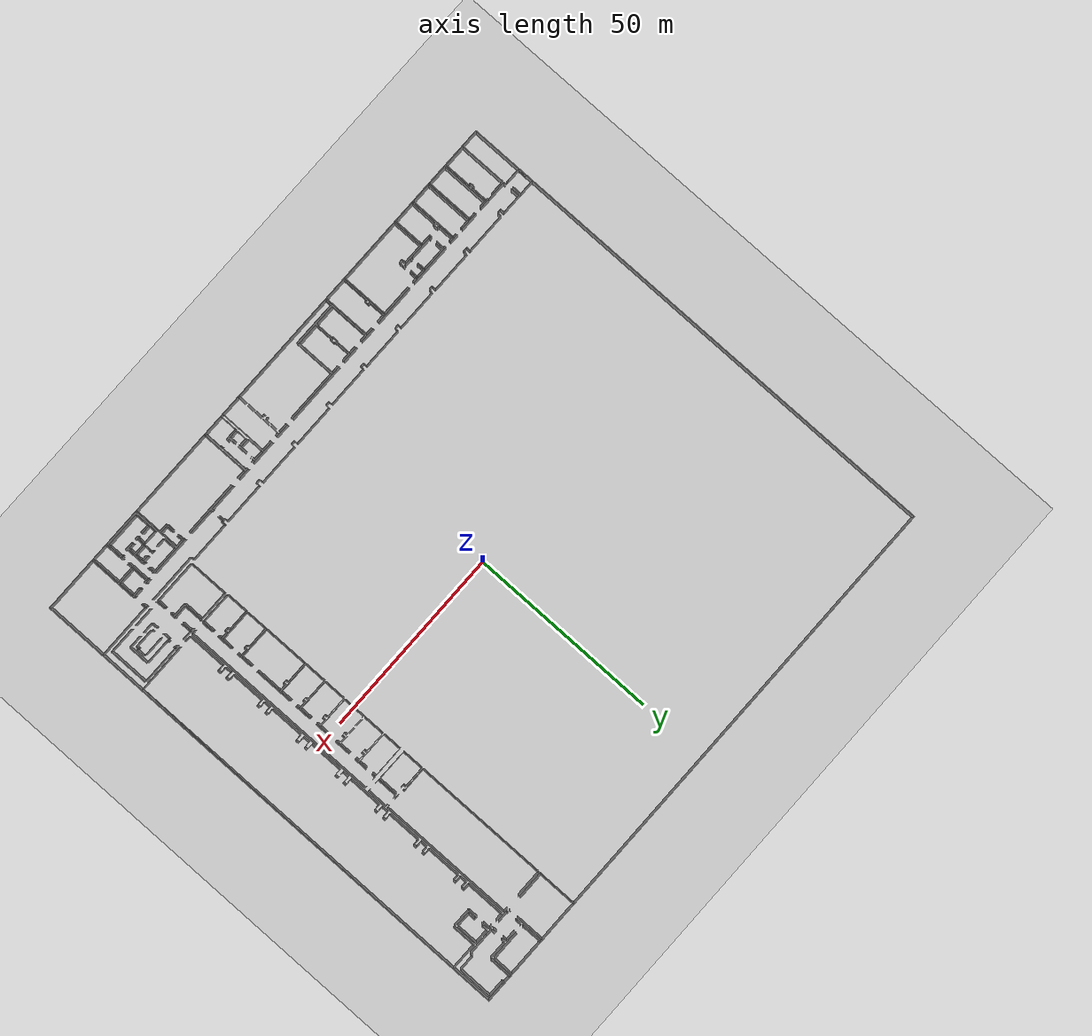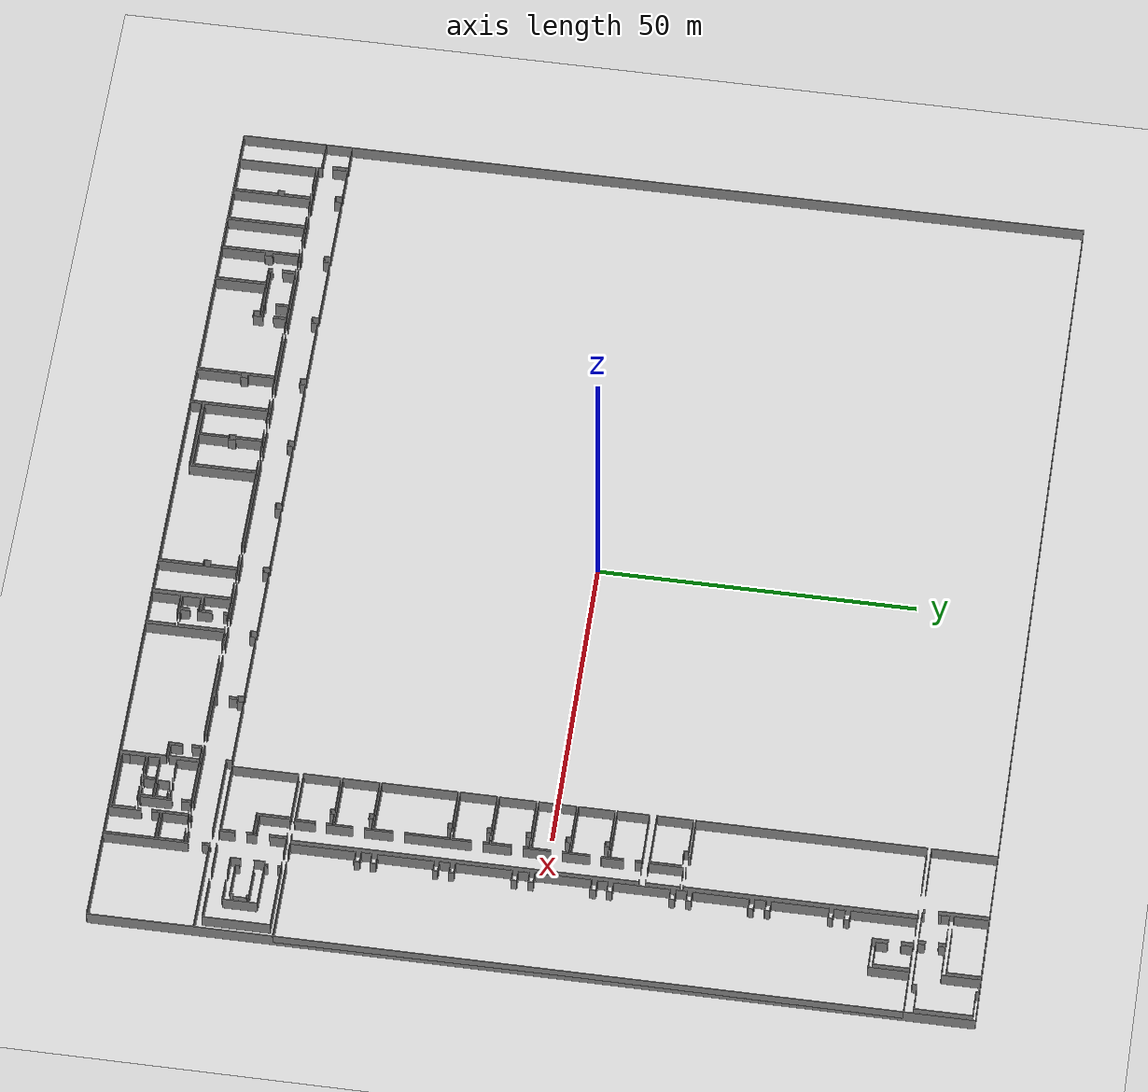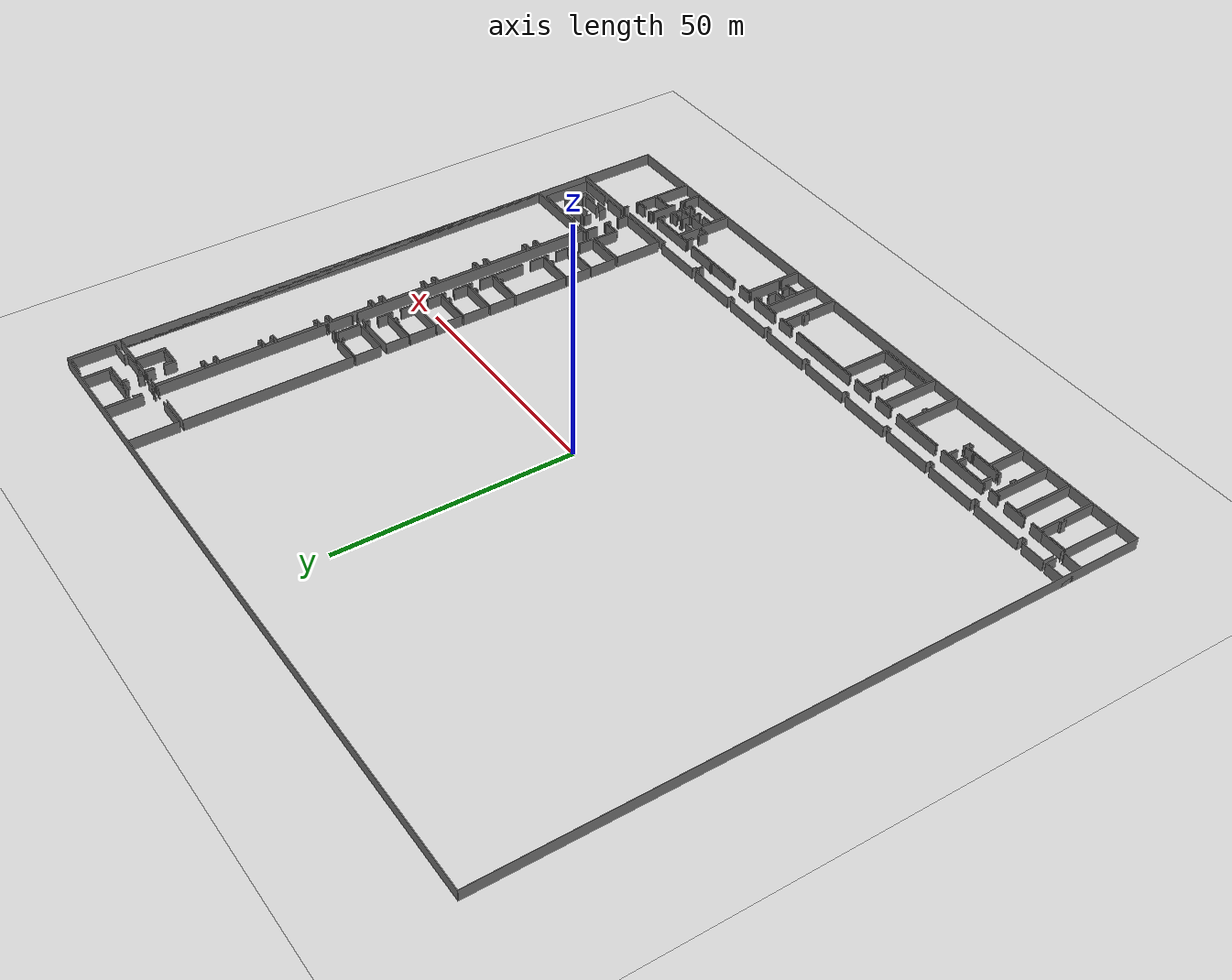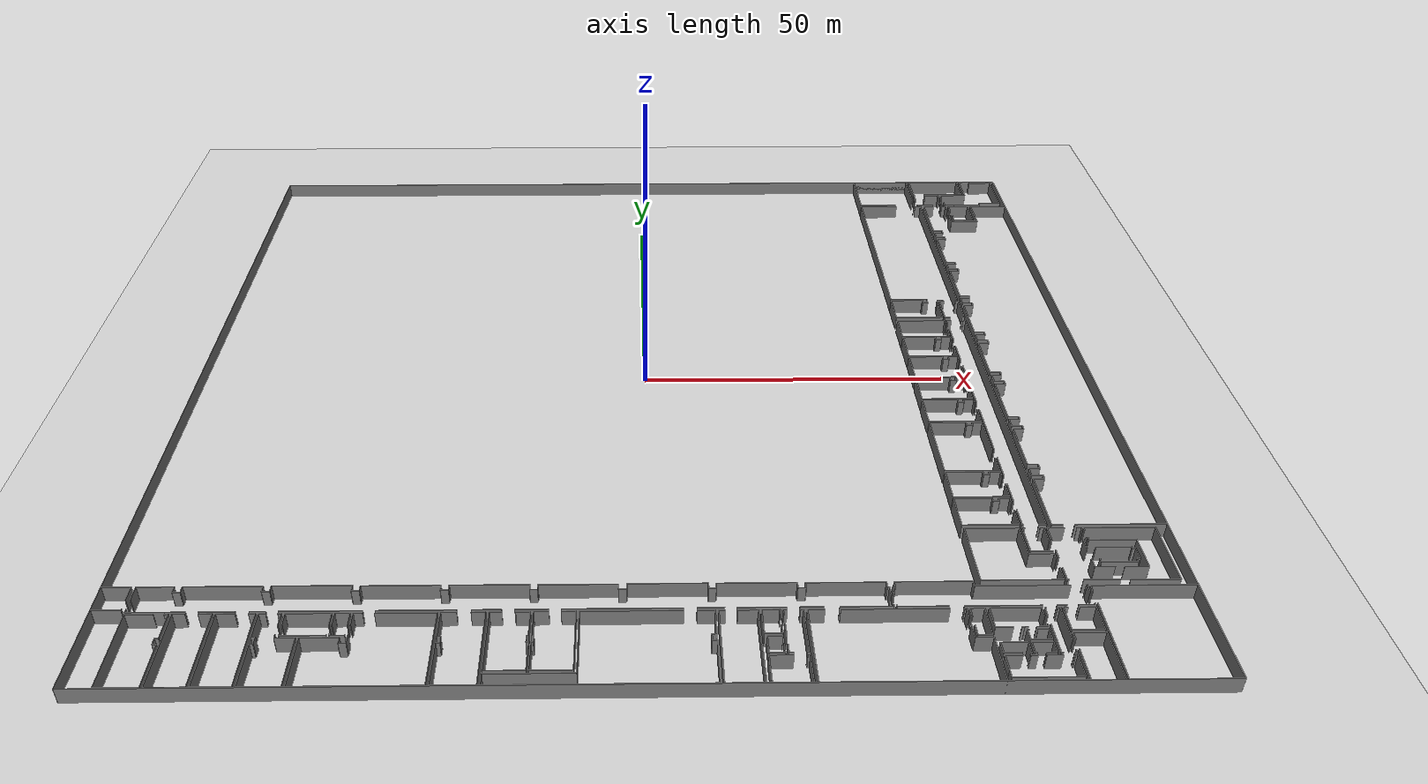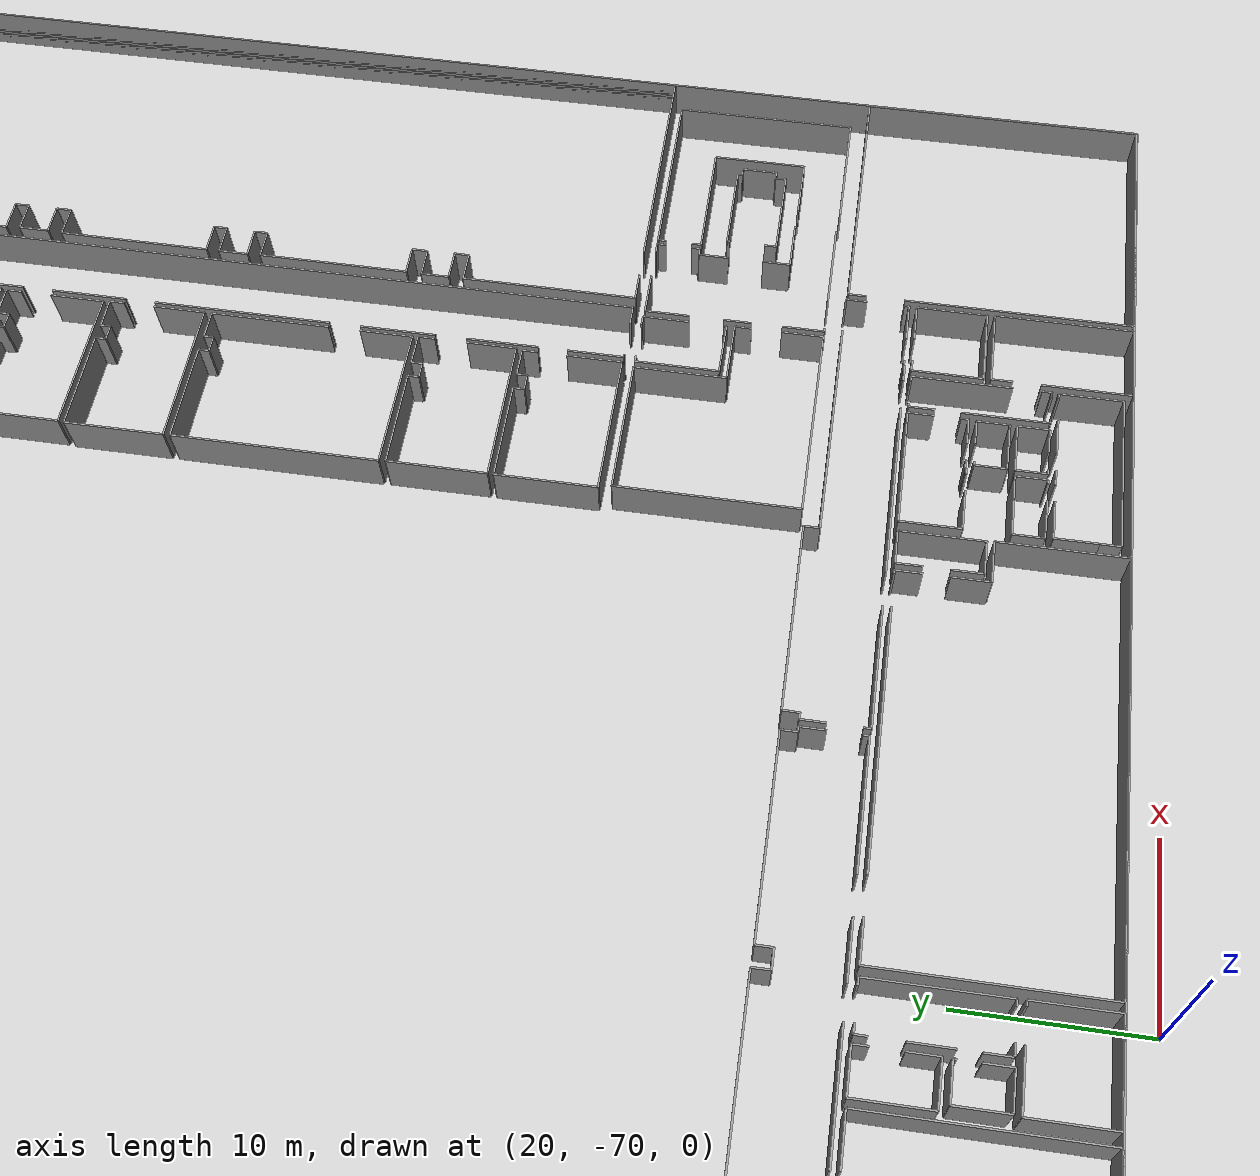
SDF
<sdf version="1.6">
  <world name="default">
    <light name="sun" type="directional">
      <cast_shadows>1</cast_shadows>
      <pose frame="">0 0 10 0 -0 0</pose>
      <diffuse>0.8 0.8 0.8 1</diffuse>
      <specular>0.1 0.1 0.1 1</specular>
      <attenuation>
        <range>1000</range>
        <constant>0.9</constant>
        <linear>0.01</linear>
        <quadratic>0.001</quadratic>
      </attenuation>
      <direction>-0.5 0.5 -1</direction>
    </light>
    <model name="ground_plane">
      <static>1</static>
      <link name="link">
        <collision name="collision">
          <geometry>
            <plane>
              <normal>0 0 1</normal>
              <size>100 100</size>
            </plane>
          </geometry>
          <surface>
            <friction>
              <ode>
                <mu>100</mu>
                <mu2>50</mu2>
              </ode>
              <torsional>
                <ode />
              </torsional>
            </friction>
            <contact>
              <ode />
            </contact>
            <bounce />
          </surface>
          <max_contacts>10</max_contacts>
        </collision>
        <visual name="visual">
          <cast_shadows>0</cast_shadows>
          <geometry>
            <plane>
              <normal>0 0 1</normal>
              <size>100 100</size>
            </plane>
          </geometry>
          <material>
            <script>
              <uri>file://media/materials/scripts/gazebo.material</uri>
              <name>Gazebo/Grey</name>
            </script>
          </material>
        </visual>
        <self_collide>0</self_collide>
        <kinematic>0</kinematic>
        <gravity>1</gravity>
      </link>
    </model>
    <gravity>0 0 -9.8</gravity>
    <magnetic_field>6e-06 2.3e-05 -4.2e-05</magnetic_field>
    <atmosphere type="adiabatic" />
    <physics default="0" name="default_physics" type="ode">
      <max_step_size>0.001</max_step_size>
      <real_time_factor>1</real_time_factor>
      <real_time_update_rate>1000</real_time_update_rate>
    </physics>
    <scene>
      <ambient>0.4 0.4 0.4 1</ambient>
      <background>0.7 0.7 0.7 1</background>
      <shadows>1</shadows>
    </scene>
    <spherical_coordinates>
      <surface_model>EARTH_WGS84</surface_model>
      <latitude_deg>0</latitude_deg>
      <longitude_deg>0</longitude_deg>
      <elevation>0</elevation>
      <heading_deg>0</heading_deg>
    </spherical_coordinates>
  <model name="50036893">
		<static>1</static>
		<link name="Wall_0">
			<collision name="Wall_0_Collision">
				<geometry>
					<box>
						<size>4.18902210922 0.1 2.5</size>
					</box>
				</geometry>
				<pose frame="">2.09451105461 0 1.25 0 0 0</pose>
			</collision>
			<visual name="Wall_0_Visual">
				<pose frame="">2.09451105461 0 1.25 0 0 0</pose>
				<geometry>
					<box>
						<size>4.18902210922 0.1 2.5</size>
					</box>
				</geometry>
				<material>
					<script>
						<uri>file://media/materials/scripts/gazebo.material</uri>
						<name>Gazebo/Grey</name>
					</script>
					<ambient>1 1 1 1</ambient>
				</material>
			</visual>
			<pose frame="">0.0 -122.381227135 0 0 0 1.57079632679</pose>
		</link>
		<link name="Wall_1">
			<collision name="Wall_1_Collision">
				<geometry>
					<box>
						<size>4.09695847626 0.1 2.5</size>
					</box>
				</geometry>
				<pose frame="">2.04847923813 0 1.25 0 0 0</pose>
			</collision>
			<visual name="Wall_1_Visual">
				<pose frame="">2.04847923813 0 1.25 0 0 0</pose>
				<geometry>
					<box>
						<size>4.09695847626 0.1 2.5</size>
					</box>
				</geometry>
				<material>
					<script>
						<uri>file://media/materials/scripts/gazebo.material</uri>
						<name>Gazebo/Grey</name>
					</script>
					<ambient>1 1 1 1</ambient>
				</material>
			</visual>
			<pose frame="">0.0 -118.192205025 0 0 0 0.0</pose>
		</link>
		<link name="Wall_2">
			<collision name="Wall_2_Collision">
				<geometry>
					<box>
						<size>2.47278352999 0.1 2.5</size>
					</box>
				</geometry>
				<pose frame="">1.236391765 0 1.25 0 0 0</pose>
			</collision>
			<visual name="Wall_2_Visual">
				<pose frame="">1.236391765 0 1.25 0 0 0</pose>
				<geometry>
					<box>
						<size>2.47278352999 0.1 2.5</size>
					</box>
				</geometry>
				<material>
					<script>
						<uri>file://media/materials/scripts/gazebo.material</uri>
						<name>Gazebo/Grey</name>
					</script>
					<ambient>1 1 1 1</ambient>
				</material>
			</visual>
			<pose frame="">4.09695847626 -118.192205025 0 0 0 -1.57079632679</pose>
		</link>
		<link name="Wall_3">
			<collision name="Wall_3_Collision">
				<geometry>
					<box>
						<size>0.189199642397 0.1 2.5</size>
					</box>
				</geometry>
				<pose frame="">0.0945998211987 0 1.25 0 0 0</pose>
			</collision>
			<visual name="Wall_3_Visual">
				<pose frame="">0.0945998211987 0 1.25 0 0 0</pose>
				<geometry>
					<box>
						<size>0.189199642397 0.1 2.5</size>
					</box>
				</geometry>
				<material>
					<script>
						<uri>file://media/materials/scripts/gazebo.material</uri>
						<name>Gazebo/Grey</name>
					</script>
					<ambient>1 1 1 1</ambient>
				</material>
			</visual>
			<pose frame="">4.09695847626 -122.262787144 0 0 0 -1.57079632679</pose>
		</link>
		<link name="Wall_4">
			<collision name="Wall_4_Collision">
				<geometry>
					<box>
						<size>4.09756948501 0.1 2.5</size>
					</box>
				</geometry>
				<pose frame="">2.04878474251 0 1.25 0 0 0</pose>
			</collision>
			<visual name="Wall_4_Visual">
				<pose frame="">2.04878474251 0 1.25 0 0 0</pose>
				<geometry>
					<box>
						<size>4.09756948501 0.1 2.5</size>
					</box>
				</geometry>
				<material>
					<script>
						<uri>file://media/materials/scripts/gazebo.material</uri>
						<name>Gazebo/Grey</name>
					</script>
					<ambient>1 1 1 1</ambient>
				</material>
			</visual>
			<pose frame="">4.09695847626 -122.451986786 0 0 0 3.12432310652</pose>
		</link>
		<link name="Wall_5">
			<collision name="Wall_5_Collision">
				<geometry>
					<box>
						<size>12.3836999182 0.1 2.5</size>
					</box>
				</geometry>
				<pose frame="">6.1918499591 0 1.25 0 0 0</pose>
			</collision>
			<visual name="Wall_5_Visual">
				<pose frame="">6.1918499591 0 1.25 0 0 0</pose>
				<geometry>
					<box>
						<size>12.3836999182 0.1 2.5</size>
					</box>
				</geometry>
				<material>
					<script>
						<uri>file://media/materials/scripts/gazebo.material</uri>
						<name>Gazebo/Grey</name>
					</script>
					<ambient>1 1 1 1</ambient>
				</material>
			</visual>
			<pose frame="">4.74013581288 -135.673389679 0 0 0 1.57079632679</pose>
		</link>
		<link name="Wall_6">
			<collision name="Wall_6_Collision">
				<geometry>
					<box>
						<size>3.85703506914 0.1 2.5</size>
					</box>
				</geometry>
				<pose frame="">1.92851753457 0 1.25 0 0 0</pose>
			</collision>
			<visual name="Wall_6_Visual">
				<pose frame="">1.92851753457 0 1.25 0 0 0</pose>
				<geometry>
					<box>
						<size>3.85703506914 0.1 2.5</size>
					</box>
				</geometry>
				<material>
					<script>
						<uri>file://media/materials/scripts/gazebo.material</uri>
						<name>Gazebo/Grey</name>
					</script>
					<ambient>1 1 1 1</ambient>
				</material>
			</visual>
			<pose frame="">4.74013581288 -123.289689761 0 0 0 0.0</pose>
		</link>
		<link name="Wall_7">
			<collision name="Wall_7_Collision">
				<geometry>
					<box>
						<size>0.567345308369 0.1 2.5</size>
					</box>
				</geometry>
				<pose frame="">0.283672654184 0 1.25 0 0 0</pose>
			</collision>
			<visual name="Wall_7_Visual">
				<pose frame="">0.283672654184 0 1.25 0 0 0</pose>
				<geometry>
					<box>
						<size>0.567345308369 0.1 2.5</size>
					</box>
				</geometry>
				<material>
					<script>
						<uri>file://media/materials/scripts/gazebo.material</uri>
						<name>Gazebo/Grey</name>
					</script>
					<ambient>1 1 1 1</ambient>
				</material>
			</visual>
			<pose frame="">10.0057698282 -123.289689761 0 0 0 0.0</pose>
		</link>
		<link name="Wall_8">
			<collision name="Wall_8_Collision">
				<geometry>
					<box>
						<size>4.20931161511 0.1 2.5</size>
					</box>
				</geometry>
				<pose frame="">2.10465580755 0 1.25 0 0 0</pose>
			</collision>
			<visual name="Wall_8_Visual">
				<pose frame="">2.10465580755 0 1.25 0 0 0</pose>
				<geometry>
					<box>
						<size>4.20931161511 0.1 2.5</size>
					</box>
				</geometry>
				<material>
					<script>
						<uri>file://media/materials/scripts/gazebo.material</uri>
						<name>Gazebo/Grey</name>
					</script>
					<ambient>1 1 1 1</ambient>
				</material>
			</visual>
			<pose frame="">10.5731151366 -123.289689761 0 0 0 -1.57079632679</pose>
		</link>
		<link name="Wall_9">
			<collision name="Wall_9_Collision">
				<geometry>
					<box>
						<size>0.533867623655 0.1 2.5</size>
					</box>
				</geometry>
				<pose frame="">0.266933811827 0 1.25 0 0 0</pose>
			</collision>
			<visual name="Wall_9_Visual">
				<pose frame="">0.266933811827 0 1.25 0 0 0</pose>
				<geometry>
					<box>
						<size>0.533867623655 0.1 2.5</size>
					</box>
				</geometry>
				<material>
					<script>
						<uri>file://media/materials/scripts/gazebo.material</uri>
						<name>Gazebo/Grey</name>
					</script>
					<ambient>1 1 1 1</ambient>
				</material>
			</visual>
			<pose frame="">10.5731151366 -127.499001376 0 0 0 3.14159265359</pose>
		</link>
		<link name="Wall_10">
			<collision name="Wall_10_Collision">
				<geometry>
					<box>
						<size>1.09639417438 0.1 2.5</size>
					</box>
				</geometry>
				<pose frame="">0.548197087188 0 1.25 0 0 0</pose>
			</collision>
			<visual name="Wall_10_Visual">
				<pose frame="">0.548197087188 0 1.25 0 0 0</pose>
				<geometry>
					<box>
						<size>1.09639417438 0.1 2.5</size>
					</box>
				</geometry>
				<material>
					<script>
						<uri>file://media/materials/scripts/gazebo.material</uri>
						<name>Gazebo/Grey</name>
					</script>
					<ambient>1 1 1 1</ambient>
				</material>
			</visual>
			<pose frame="">10.039247513 -127.499001376 0 0 0 -1.57079632679</pose>
		</link>
		<link name="Wall_11">
			<collision name="Wall_11_Collision">
				<geometry>
					<box>
						<size>0.55897588719 0.1 2.5</size>
					</box>
				</geometry>
				<pose frame="">0.279487943595 0 1.25 0 0 0</pose>
			</collision>
			<visual name="Wall_11_Visual">
				<pose frame="">0.279487943595 0 1.25 0 0 0</pose>
				<geometry>
					<box>
						<size>0.55897588719 0.1 2.5</size>
					</box>
				</geometry>
				<material>
					<script>
						<uri>file://media/materials/scripts/gazebo.material</uri>
						<name>Gazebo/Grey</name>
					</script>
					<ambient>1 1 1 1</ambient>
				</material>
			</visual>
			<pose frame="">10.039247513 -128.59539555 0 0 0 0.0</pose>
		</link>
		<link name="Wall_12">
			<collision name="Wall_12_Collision">
				<geometry>
					<box>
						<size>7.06658128166 0.1 2.5</size>
					</box>
				</geometry>
				<pose frame="">3.53329064083 0 1.25 0 0 0</pose>
			</collision>
			<visual name="Wall_12_Visual">
				<pose frame="">3.53329064083 0 1.25 0 0 0</pose>
				<geometry>
					<box>
						<size>7.06658128166 0.1 2.5</size>
					</box>
				</geometry>
				<material>
					<script>
						<uri>file://media/materials/scripts/gazebo.material</uri>
						<name>Gazebo/Grey</name>
					</script>
					<ambient>1 1 1 1</ambient>
				</material>
			</visual>
			<pose frame="">10.5982234001 -128.59539555 0 0 0 -1.57079632679</pose>
		</link>
		<link name="Wall_13">
			<collision name="Wall_13_Collision">
				<geometry>
					<box>
						<size>5.85809870462 0.1 2.5</size>
					</box>
				</geometry>
				<pose frame="">2.92904935231 0 1.25 0 0 0</pose>
			</collision>
			<visual name="Wall_13_Visual">
				<pose frame="">2.92904935231 0 1.25 0 0 0</pose>
				<geometry>
					<box>
						<size>5.85809870462 0.1 2.5</size>
					</box>
				</geometry>
				<material>
					<script>
						<uri>file://media/materials/scripts/gazebo.material</uri>
						<name>Gazebo/Grey</name>
					</script>
					<ambient>1 1 1 1</ambient>
				</material>
			</visual>
			<pose frame="">10.5982234001 -135.661976832 0 0 0 -3.13964443543</pose>
		</link>
		<link name="Wall_14">
			<collision name="Wall_14_Collision">
				<geometry>
					<box>
						<size>12.3735551653 0.1 2.5</size>
					</box>
				</geometry>
				<pose frame="">6.18677758263 0 1.25 0 0 0</pose>
			</collision>
			<visual name="Wall_14_Visual">
				<pose frame="">6.18677758263 0 1.25 0 0 0</pose>
				<geometry>
					<box>
						<size>12.3735551653 0.1 2.5</size>
					</box>
				</geometry>
				<material>
					<script>
						<uri>file://media/materials/scripts/gazebo.material</uri>
						<name>Gazebo/Grey</name>
					</script>
					<ambient>1 1 1 1</ambient>
				</material>
			</visual>
			<pose frame="">11.0207523602 -135.661976832 0 0 0 1.57079632679</pose>
		</link>
		<link name="Wall_15">
			<collision name="Wall_15_Collision">
				<geometry>
					<box>
						<size>1.75960739806 0.1 2.5</size>
					</box>
				</geometry>
				<pose frame="">0.879803699031 0 1.25 0 0 0</pose>
			</collision>
			<visual name="Wall_15_Visual">
				<pose frame="">0.879803699031 0 1.25 0 0 0</pose>
				<geometry>
					<box>
						<size>1.75960739806 0.1 2.5</size>
					</box>
				</geometry>
				<material>
					<script>
						<uri>file://media/materials/scripts/gazebo.material</uri>
						<name>Gazebo/Grey</name>
					</script>
					<ambient>1 1 1 1</ambient>
				</material>
			</visual>
			<pose frame="">11.0207523602 -123.288421667 0 0 0 0.0</pose>
		</link>
		<link name="Wall_16">
			<collision name="Wall_16_Collision">
				<geometry>
					<box>
						<size>1.86384473456 0.1 2.5</size>
					</box>
				</geometry>
				<pose frame="">0.931922367278 0 1.25 0 0 0</pose>
			</collision>
			<visual name="Wall_16_Visual">
				<pose frame="">0.931922367278 0 1.25 0 0 0</pose>
				<geometry>
					<box>
						<size>1.86384473456 0.1 2.5</size>
					</box>
				</geometry>
				<material>
					<script>
						<uri>file://media/materials/scripts/gazebo.material</uri>
						<name>Gazebo/Grey</name>
					</script>
					<ambient>1 1 1 1</ambient>
				</material>
			</visual>
			<pose frame="">14.4798594952 -123.288421667 0 0 0 0.0</pose>
		</link>
		<link name="Wall_17">
			<collision name="Wall_17_Collision">
				<geometry>
					<box>
						<size>12.3864897253 0.1 2.5</size>
					</box>
				</geometry>
				<pose frame="">6.19324486263 0 1.25 0 0 0</pose>
			</collision>
			<visual name="Wall_17_Visual">
				<pose frame="">6.19324486263 0 1.25 0 0 0</pose>
				<geometry>
					<box>
						<size>12.3864897253 0.1 2.5</size>
					</box>
				</geometry>
				<material>
					<script>
						<uri>file://media/materials/scripts/gazebo.material</uri>
						<name>Gazebo/Grey</name>
					</script>
					<ambient>1 1 1 1</ambient>
				</material>
			</visual>
			<pose frame="">16.3437042297 -123.288421667 0 0 0 -1.57079632679</pose>
		</link>
		<link name="Wall_18">
			<collision name="Wall_18_Collision">
				<geometry>
					<box>
						<size>5.3229675847 0.1 2.5</size>
					</box>
				</geometry>
				<pose frame="">2.66148379235 0 1.25 0 0 0</pose>
			</collision>
			<visual name="Wall_18_Visual">
				<pose frame="">2.66148379235 0 1.25 0 0 0</pose>
				<geometry>
					<box>
						<size>5.3229675847 0.1 2.5</size>
					</box>
				</geometry>
				<material>
					<script>
						<uri>file://media/materials/scripts/gazebo.material</uri>
						<name>Gazebo/Grey</name>
					</script>
					<ambient>1 1 1 1</ambient>
				</material>
			</visual>
			<pose frame="">16.3437042297 -135.674911392 0 0 0 3.1391626984</pose>
		</link>
		<link name="Wall_19">
			<collision name="Wall_19_Collision">
				<geometry>
					<box>
						<size>12.3484469017 0.1 2.5</size>
					</box>
				</geometry>
				<pose frame="">6.17422345086 0 1.25 0 0 0</pose>
			</collision>
			<visual name="Wall_19_Visual">
				<pose frame="">6.17422345086 0 1.25 0 0 0</pose>
				<geometry>
					<box>
						<size>12.3484469017 0.1 2.5</size>
					</box>
				</geometry>
				<material>
					<script>
						<uri>file://media/materials/scripts/gazebo.material</uri>
						<name>Gazebo/Grey</name>
					</script>
					<ambient>1 1 1 1</ambient>
				</material>
			</visual>
			<pose frame="">16.7806894628 -135.663244926 0 0 0 1.57079632679</pose>
		</link>
		<link name="Wall_20">
			<collision name="Wall_20_Collision">
				<geometry>
					<box>
						<size>2.57321658413 0.1 2.5</size>
					</box>
				</geometry>
				<pose frame="">1.28660829207 0 1.25 0 0 0</pose>
			</collision>
			<visual name="Wall_20_Visual">
				<pose frame="">1.28660829207 0 1.25 0 0 0</pose>
				<geometry>
					<box>
						<size>2.57321658413 0.1 2.5</size>
					</box>
				</geometry>
				<material>
					<script>
						<uri>file://media/materials/scripts/gazebo.material</uri>
						<name>Gazebo/Grey</name>
					</script>
					<ambient>1 1 1 1</ambient>
				</material>
			</visual>
			<pose frame="">16.7806894628 -123.314798024 0 0 0 0.0</pose>
		</link>
		<link name="Wall_21">
			<collision name="Wall_21_Collision">
				<geometry>
					<box>
						<size>0.920636329628 0.1 2.5</size>
					</box>
				</geometry>
				<pose frame="">0.460318164814 0 1.25 0 0 0</pose>
			</collision>
			<visual name="Wall_21_Visual">
				<pose frame="">0.460318164814 0 1.25 0 0 0</pose>
				<geometry>
					<box>
						<size>0.920636329628 0.1 2.5</size>
					</box>
				</geometry>
				<material>
					<script>
						<uri>file://media/materials/scripts/gazebo.material</uri>
						<name>Gazebo/Grey</name>
					</script>
					<ambient>1 1 1 1</ambient>
				</material>
			</visual>
			<pose frame="">21.1348174261 -123.314798024 0 0 0 0.0</pose>
		</link>
		<link name="Wall_22">
			<collision name="Wall_22_Collision">
				<geometry>
					<box>
						<size>12.3400774806 0.1 2.5</size>
					</box>
				</geometry>
				<pose frame="">6.17003874028 0 1.25 0 0 0</pose>
			</collision>
			<visual name="Wall_22_Visual">
				<pose frame="">6.17003874028 0 1.25 0 0 0</pose>
				<geometry>
					<box>
						<size>12.3400774806 0.1 2.5</size>
					</box>
				</geometry>
				<material>
					<script>
						<uri>file://media/materials/scripts/gazebo.material</uri>
						<name>Gazebo/Grey</name>
					</script>
					<ambient>1 1 1 1</ambient>
				</material>
			</visual>
			<pose frame="">22.0554537558 -123.314798024 0 0 0 -1.57079632679</pose>
		</link>
		<link name="Wall_23">
			<collision name="Wall_23_Collision">
				<geometry>
					<box>
						<size>5.27477093284 0.1 2.5</size>
					</box>
				</geometry>
				<pose frame="">2.63738546642 0 1.25 0 0 0</pose>
			</collision>
			<visual name="Wall_23_Visual">
				<pose frame="">2.63738546642 0 1.25 0 0 0</pose>
				<geometry>
					<box>
						<size>5.27477093284 0.1 2.5</size>
					</box>
				</geometry>
				<material>
					<script>
						<uri>file://media/materials/scripts/gazebo.material</uri>
						<name>Gazebo/Grey</name>
					</script>
					<ambient>1 1 1 1</ambient>
				</material>
			</visual>
			<pose frame="">22.0554537558 -135.654875505 0 0 0 -3.14000596389</pose>
		</link>
		<link name="Wall_24">
			<collision name="Wall_24_Collision">
				<geometry>
					<box>
						<size>7.03462530989 0.1 2.5</size>
					</box>
				</geometry>
				<pose frame="">3.51731265495 0 1.25 0 0 0</pose>
			</collision>
			<visual name="Wall_24_Visual">
				<pose frame="">3.51731265495 0 1.25 0 0 0</pose>
				<geometry>
					<box>
						<size>7.03462530989 0.1 2.5</size>
					</box>
				</geometry>
				<material>
					<script>
						<uri>file://media/materials/scripts/gazebo.material</uri>
						<name>Gazebo/Grey</name>
					</script>
					<ambient>1 1 1 1</ambient>
				</material>
			</visual>
			<pose frame="">22.5043590735 -135.703570319 0 0 0 1.57079632679</pose>
		</link>
		<link name="Wall_25">
			<collision name="Wall_25_Collision">
				<geometry>
					<box>
						<size>0.504701458942 0.1 2.5</size>
					</box>
				</geometry>
				<pose frame="">0.252350729471 0 1.25 0 0 0</pose>
			</collision>
			<visual name="Wall_25_Visual">
				<pose frame="">0.252350729471 0 1.25 0 0 0</pose>
				<geometry>
					<box>
						<size>0.504701458942 0.1 2.5</size>
					</box>
				</geometry>
				<material>
					<script>
						<uri>file://media/materials/scripts/gazebo.material</uri>
						<name>Gazebo/Grey</name>
					</script>
					<ambient>1 1 1 1</ambient>
				</material>
			</visual>
			<pose frame="">22.5043590735 -128.668945009 0 0 0 0.0</pose>
		</link>
		<link name="Wall_26">
			<collision name="Wall_26_Collision">
				<geometry>
					<box>
						<size>1.21737035323 0.1 2.5</size>
					</box>
				</geometry>
				<pose frame="">0.608685176614 0 1.25 0 0 0</pose>
			</collision>
			<visual name="Wall_26_Visual">
				<pose frame="">0.608685176614 0 1.25 0 0 0</pose>
				<geometry>
					<box>
						<size>1.21737035323 0.1 2.5</size>
					</box>
				</geometry>
				<material>
					<script>
						<uri>file://media/materials/scripts/gazebo.material</uri>
						<name>Gazebo/Grey</name>
					</script>
					<ambient>1 1 1 1</ambient>
				</material>
			</visual>
			<pose frame="">23.0090605325 -128.668945009 0 0 0 1.57079632679</pose>
		</link>
		<link name="Wall_27">
			<collision name="Wall_27_Collision">
				<geometry>
					<box>
						<size>0.550352847188 0.1 2.5</size>
					</box>
				</geometry>
				<pose frame="">0.275176423594 0 1.25 0 0 0</pose>
			</collision>
			<visual name="Wall_27_Visual">
				<pose frame="">0.275176423594 0 1.25 0 0 0</pose>
				<geometry>
					<box>
						<size>0.550352847188 0.1 2.5</size>
					</box>
				</geometry>
				<material>
					<script>
						<uri>file://media/materials/scripts/gazebo.material</uri>
						<name>Gazebo/Grey</name>
					</script>
					<ambient>1 1 1 1</ambient>
				</material>
			</visual>
			<pose frame="">23.0090605325 -127.451574656 0 0 0 3.14159265359</pose>
		</link>
		<link name="Wall_28">
			<collision name="Wall_28_Collision">
				<geometry>
					<box>
						<size>4.1081177045 0.1 2.5</size>
					</box>
				</geometry>
				<pose frame="">2.05405885225 0 1.25 0 0 0</pose>
			</collision>
			<visual name="Wall_28_Visual">
				<pose frame="">2.05405885225 0 1.25 0 0 0</pose>
				<geometry>
					<box>
						<size>4.1081177045 0.1 2.5</size>
					</box>
				</geometry>
				<material>
					<script>
						<uri>file://media/materials/scripts/gazebo.material</uri>
						<name>Gazebo/Grey</name>
					</script>
					<ambient>1 1 1 1</ambient>
				</material>
			</visual>
			<pose frame="">22.4587076853 -127.451574656 0 0 0 1.57079632679</pose>
		</link>
		<link name="Wall_29">
			<collision name="Wall_29_Collision">
				<geometry>
					<box>
						<size>0.935853459044 0.1 2.5</size>
					</box>
				</geometry>
				<pose frame="">0.467926729522 0 1.25 0 0 0</pose>
			</collision>
			<visual name="Wall_29_Visual">
				<pose frame="">0.467926729522 0 1.25 0 0 0</pose>
				<geometry>
					<box>
						<size>0.935853459044 0.1 2.5</size>
					</box>
				</geometry>
				<material>
					<script>
						<uri>file://media/materials/scripts/gazebo.material</uri>
						<name>Gazebo/Grey</name>
					</script>
					<ambient>1 1 1 1</ambient>
				</material>
			</visual>
			<pose frame="">22.4587076853 -123.343456951 0 0 0 0.0</pose>
		</link>
		<link name="Wall_30">
			<collision name="Wall_30_Collision">
				<geometry>
					<box>
						<size>0.471731011876 0.1 2.5</size>
					</box>
				</geometry>
				<pose frame="">0.235865505938 0 1.25 0 0 0</pose>
			</collision>
			<visual name="Wall_30_Visual">
				<pose frame="">0.235865505938 0 1.25 0 0 0</pose>
				<geometry>
					<box>
						<size>0.471731011876 0.1 2.5</size>
					</box>
				</geometry>
				<material>
					<script>
						<uri>file://media/materials/scripts/gazebo.material</uri>
						<name>Gazebo/Grey</name>
					</script>
					<ambient>1 1 1 1</ambient>
				</material>
			</visual>
			<pose frame="">24.9847511682 -123.343456951 0 0 0 0.0</pose>
		</link>
		<link name="Wall_31">
			<collision name="Wall_31_Collision">
				<geometry>
					<box>
						<size>2.09235529461 0.1 2.5</size>
					</box>
				</geometry>
				<pose frame="">1.0461776473 0 1.25 0 0 0</pose>
			</collision>
			<visual name="Wall_31_Visual">
				<pose frame="">1.0461776473 0 1.25 0 0 0</pose>
				<geometry>
					<box>
						<size>2.09235529461 0.1 2.5</size>
					</box>
				</geometry>
				<material>
					<script>
						<uri>file://media/materials/scripts/gazebo.material</uri>
						<name>Gazebo/Grey</name>
					</script>
					<ambient>1 1 1 1</ambient>
				</material>
			</visual>
			<pose frame="">25.4564821801 -123.343456951 0 0 0 -1.57079632679</pose>
		</link>
		<link name="Wall_32">
			<collision name="Wall_32_Collision">
				<geometry>
					<box>
						<size>0.701763284871 0.1 2.5</size>
					</box>
				</geometry>
				<pose frame="">0.350881642436 0 1.25 0 0 0</pose>
			</collision>
			<visual name="Wall_32_Visual">
				<pose frame="">0.350881642436 0 1.25 0 0 0</pose>
				<geometry>
					<box>
						<size>0.701763284871 0.1 2.5</size>
					</box>
				</geometry>
				<material>
					<script>
						<uri>file://media/materials/scripts/gazebo.material</uri>
						<name>Gazebo/Grey</name>
					</script>
					<ambient>1 1 1 1</ambient>
				</material>
			</visual>
			<pose frame="">25.4564821801 -126.950677479 0 0 0 -1.57079632679</pose>
		</link>
		<link name="Wall_33">
			<collision name="Wall_33_Collision">
				<geometry>
					<box>
						<size>2.73908329476 0.1 2.5</size>
					</box>
				</geometry>
				<pose frame="">1.36954164738 0 1.25 0 0 0</pose>
			</collision>
			<visual name="Wall_33_Visual">
				<pose frame="">1.36954164738 0 1.25 0 0 0</pose>
				<geometry>
					<box>
						<size>2.73908329476 0.1 2.5</size>
					</box>
				</geometry>
				<material>
					<script>
						<uri>file://media/materials/scripts/gazebo.material</uri>
						<name>Gazebo/Grey</name>
					</script>
					<ambient>1 1 1 1</ambient>
				</material>
			</visual>
			<pose frame="">25.4564821801 -127.652440764 0 0 0 0.0</pose>
		</link>
		<link name="Wall_34">
			<collision name="Wall_34_Collision">
				<geometry>
					<box>
						<size>8.0356588066 0.1 2.5</size>
					</box>
				</geometry>
				<pose frame="">4.0178294033 0 1.25 0 0 0</pose>
			</collision>
			<visual name="Wall_34_Visual">
				<pose frame="">4.0178294033 0 1.25 0 0 0</pose>
				<geometry>
					<box>
						<size>8.0356588066 0.1 2.5</size>
					</box>
				</geometry>
				<material>
					<script>
						<uri>file://media/materials/scripts/gazebo.material</uri>
						<name>Gazebo/Grey</name>
					</script>
					<ambient>1 1 1 1</ambient>
				</material>
			</visual>
			<pose frame="">28.1955654749 -127.652440764 0 0 0 -1.57079632679</pose>
		</link>
		<link name="Wall_35">
			<collision name="Wall_35_Collision">
				<geometry>
					<box>
						<size>5.69122742883 0.1 2.5</size>
					</box>
				</geometry>
				<pose frame="">2.84561371442 0 1.25 0 0 0</pose>
			</collision>
			<visual name="Wall_35_Visual">
				<pose frame="">2.84561371442 0 1.25 0 0 0</pose>
				<geometry>
					<box>
						<size>5.69122742883 0.1 2.5</size>
					</box>
				</geometry>
				<material>
					<script>
						<uri>file://media/materials/scripts/gazebo.material</uri>
						<name>Gazebo/Grey</name>
					</script>
					<ambient>1 1 1 1</ambient>
				</material>
			</visual>
			<pose frame="">28.1955654749 -135.688099571 0 0 0 -3.13887430021</pose>
		</link>
		<link name="Wall_36">
			<collision name="Wall_36_Collision">
				<geometry>
					<box>
						<size>6.15025647204 0.1 2.5</size>
					</box>
				</geometry>
				<pose frame="">3.07512823602 0 1.25 0 0 0</pose>
			</collision>
			<visual name="Wall_36_Visual">
				<pose frame="">3.07512823602 0 1.25 0 0 0</pose>
				<geometry>
					<box>
						<size>6.15025647204 0.1 2.5</size>
					</box>
				</geometry>
				<material>
					<script>
						<uri>file://media/materials/scripts/gazebo.material</uri>
						<name>Gazebo/Grey</name>
					</script>
					<ambient>1 1 1 1</ambient>
				</material>
			</visual>
			<pose frame="">25.961183639 -123.352840848 0 0 0 0.0</pose>
		</link>
		<link name="Wall_37">
			<collision name="Wall_37_Collision">
				<geometry>
					<box>
						<size>2.10655794873 0.1 2.5</size>
					</box>
				</geometry>
				<pose frame="">1.05327897437 0 1.25 0 0 0</pose>
			</collision>
			<visual name="Wall_37_Visual">
				<pose frame="">1.05327897437 0 1.25 0 0 0</pose>
				<geometry>
					<box>
						<size>2.10655794873 0.1 2.5</size>
					</box>
				</geometry>
				<material>
					<script>
						<uri>file://media/materials/scripts/gazebo.material</uri>
						<name>Gazebo/Grey</name>
					</script>
					<ambient>1 1 1 1</ambient>
				</material>
			</visual>
			<pose frame="">32.1114401111 -123.352840848 0 0 0 -1.57079632679</pose>
		</link>
		<link name="Wall_38">
			<collision name="Wall_38_Collision">
				<geometry>
					<box>
						<size>0.169163755334 0.1 2.5</size>
					</box>
				</geometry>
				<pose frame="">0.0845818776669 0 1.25 0 0 0</pose>
			</collision>
			<visual name="Wall_38_Visual">
				<pose frame="">0.0845818776669 0 1.25 0 0 0</pose>
				<geometry>
					<box>
						<size>0.169163755334 0.1 2.5</size>
					</box>
				</geometry>
				<material>
					<script>
						<uri>file://media/materials/scripts/gazebo.material</uri>
						<name>Gazebo/Grey</name>
					</script>
					<ambient>1 1 1 1</ambient>
				</material>
			</visual>
			<pose frame="">32.1114401111 -127.080276698 0 0 0 -1.57079632679</pose>
		</link>
		<link name="Wall_39">
			<collision name="Wall_39_Collision">
				<geometry>
					<box>
						<size>6.14011171909 0.1 2.5</size>
					</box>
				</geometry>
				<pose frame="">3.07005585955 0 1.25 0 0 0</pose>
			</collision>
			<visual name="Wall_39_Visual">
				<pose frame="">3.07005585955 0 1.25 0 0 0</pose>
				<geometry>
					<box>
						<size>6.14011171909 0.1 2.5</size>
					</box>
				</geometry>
				<material>
					<script>
						<uri>file://media/materials/scripts/gazebo.material</uri>
						<name>Gazebo/Grey</name>
					</script>
					<ambient>1 1 1 1</ambient>
				</material>
			</visual>
			<pose frame="">32.1114401111 -127.249440453 0 0 0 3.14159265359</pose>
		</link>
		<link name="Wall_40">
			<collision name="Wall_40_Collision">
				<geometry>
					<box>
						<size>0.302060018895 0.1 2.5</size>
					</box>
				</geometry>
				<pose frame="">0.151030009447 0 1.25 0 0 0</pose>
			</collision>
			<visual name="Wall_40_Visual">
				<pose frame="">0.151030009447 0 1.25 0 0 0</pose>
				<geometry>
					<box>
						<size>0.302060018895 0.1 2.5</size>
					</box>
				</geometry>
				<material>
					<script>
						<uri>file://media/materials/scripts/gazebo.material</uri>
						<name>Gazebo/Grey</name>
					</script>
					<ambient>1 1 1 1</ambient>
				</material>
			</visual>
			<pose frame="">25.971328392 -127.249440453 0 0 0 1.57079632679</pose>
		</link>
		<link name="Wall_41">
			<collision name="Wall_41_Collision">
				<geometry>
					<box>
						<size>1.99930292449 0.1 2.5</size>
					</box>
				</geometry>
				<pose frame="">0.999651462246 0 1.25 0 0 0</pose>
			</collision>
			<visual name="Wall_41_Visual">
				<pose frame="">0.999651462246 0 1.25 0 0 0</pose>
				<geometry>
					<box>
						<size>1.99930292449 0.1 2.5</size>
					</box>
				</geometry>
				<material>
					<script>
						<uri>file://media/materials/scripts/gazebo.material</uri>
						<name>Gazebo/Grey</name>
					</script>
					<ambient>1 1 1 1</ambient>
				</material>
			</visual>
			<pose frame="">25.971328392 -125.352118034 0 0 0 1.57587049357</pose>
		</link>
		<link name="Wall_42">
			<collision name="Wall_42_Collision">
				<geometry>
					<box>
						<size>1.96300969458 0.1 2.5</size>
					</box>
				</geometry>
				<pose frame="">0.98150484729 0 1.25 0 0 0</pose>
			</collision>
			<visual name="Wall_42_Visual">
				<pose frame="">0.98150484729 0 1.25 0 0 0</pose>
				<geometry>
					<box>
						<size>1.96300969458 0.1 2.5</size>
					</box>
				</geometry>
				<material>
					<script>
						<uri>file://media/materials/scripts/gazebo.material</uri>
						<name>Gazebo/Grey</name>
					</script>
					<ambient>1 1 1 1</ambient>
				</material>
			</visual>
			<pose frame="">32.5603454288 -123.37617378 0 0 0 0.0</pose>
		</link>
		<link name="Wall_43">
			<collision name="Wall_43_Collision">
				<geometry>
					<box>
						<size>2.0396025793 0.1 2.5</size>
					</box>
				</geometry>
				<pose frame="">1.01980128965 0 1.25 0 0 0</pose>
			</collision>
			<visual name="Wall_43_Visual">
				<pose frame="">1.01980128965 0 1.25 0 0 0</pose>
				<geometry>
					<box>
						<size>2.0396025793 0.1 2.5</size>
					</box>
				</geometry>
				<material>
					<script>
						<uri>file://media/materials/scripts/gazebo.material</uri>
						<name>Gazebo/Grey</name>
					</script>
					<ambient>1 1 1 1</ambient>
				</material>
			</visual>
			<pose frame="">34.5233551234 -123.37617378 0 0 0 -1.57079632679</pose>
		</link>
		<link name="Wall_44">
			<collision name="Wall_44_Collision">
				<geometry>
					<box>
						<size>0.186409835338 0.1 2.5</size>
					</box>
				</geometry>
				<pose frame="">0.093204917669 0 1.25 0 0 0</pose>
			</collision>
			<visual name="Wall_44_Visual">
				<pose frame="">0.093204917669 0 1.25 0 0 0</pose>
				<geometry>
					<box>
						<size>0.186409835338 0.1 2.5</size>
					</box>
				</geometry>
				<material>
					<script>
						<uri>file://media/materials/scripts/gazebo.material</uri>
						<name>Gazebo/Grey</name>
					</script>
					<ambient>1 1 1 1</ambient>
				</material>
			</visual>
			<pose frame="">34.5233551234 -127.071400039 0 0 0 -1.57079632679</pose>
		</link>
		<link name="Wall_45">
			<collision name="Wall_45_Collision">
				<geometry>
					<box>
						<size>2.03148677695 0.1 2.5</size>
					</box>
				</geometry>
				<pose frame="">1.01574338847 0 1.25 0 0 0</pose>
			</collision>
			<visual name="Wall_45_Visual">
				<pose frame="">1.01574338847 0 1.25 0 0 0</pose>
				<geometry>
					<box>
						<size>2.03148677695 0.1 2.5</size>
					</box>
				</geometry>
				<material>
					<script>
						<uri>file://media/materials/scripts/gazebo.material</uri>
						<name>Gazebo/Grey</name>
					</script>
					<ambient>1 1 1 1</ambient>
				</material>
			</visual>
			<pose frame="">34.5233551234 -127.257809875 0 0 0 3.14159265359</pose>
		</link>
		<link name="Wall_46">
			<collision name="Wall_46_Collision">
				<geometry>
					<box>
						<size>0.250321778882 0.1 2.5</size>
					</box>
				</geometry>
				<pose frame="">0.125160889441 0 1.25 0 0 0</pose>
			</collision>
			<visual name="Wall_46_Visual">
				<pose frame="">0.125160889441 0 1.25 0 0 0</pose>
				<geometry>
					<box>
						<size>0.250321778882 0.1 2.5</size>
					</box>
				</geometry>
				<material>
					<script>
						<uri>file://media/materials/scripts/gazebo.material</uri>
						<name>Gazebo/Grey</name>
					</script>
					<ambient>1 1 1 1</ambient>
				</material>
			</visual>
			<pose frame="">32.4918683465 -127.257809875 0 0 0 1.57079632679</pose>
		</link>
		<link name="Wall_47">
			<collision name="Wall_47_Collision">
				<geometry>
					<box>
						<size>2.04036343577 0.1 2.5</size>
					</box>
				</geometry>
				<pose frame="">1.02018171789 0 1.25 0 0 0</pose>
			</collision>
			<visual name="Wall_47_Visual">
				<pose frame="">1.02018171789 0 1.25 0 0 0</pose>
				<geometry>
					<box>
						<size>2.04036343577 0.1 2.5</size>
					</box>
				</geometry>
				<material>
					<script>
						<uri>file://media/materials/scripts/gazebo.material</uri>
						<name>Gazebo/Grey</name>
					</script>
					<ambient>1 1 1 1</ambient>
				</material>
			</visual>
			<pose frame="">32.4918683465 -125.412225695 0 0 0 1.57079632679</pose>
		</link>
		<link name="Wall_48">
			<collision name="Wall_48_Collision">
				<geometry>
					<box>
						<size>0.0686126811493 0.1 2.5</size>
					</box>
				</geometry>
				<pose frame="">0.0343063405747 0 1.25 0 0 0</pose>
			</collision>
			<visual name="Wall_48_Visual">
				<pose frame="">0.0343063405747 0 1.25 0 0 0</pose>
				<geometry>
					<box>
						<size>0.0686126811493 0.1 2.5</size>
					</box>
				</geometry>
				<material>
					<script>
						<uri>file://media/materials/scripts/gazebo.material</uri>
						<name>Gazebo/Grey</name>
					</script>
					<ambient>1 1 1 1</ambient>
				</material>
			</visual>
			<pose frame="">32.4918683465 -123.37186226 0 0 0 -0.0628799582224</pose>
		</link>
		<link name="Wall_49">
			<collision name="Wall_49_Collision">
				<geometry>
					<box>
						<size>7.97783371482 0.1 2.5</size>
					</box>
				</geometry>
				<pose frame="">3.98891685741 0 1.25 0 0 0</pose>
			</collision>
			<visual name="Wall_49_Visual">
				<pose frame="">3.98891685741 0 1.25 0 0 0</pose>
				<geometry>
					<box>
						<size>7.97783371482 0.1 2.5</size>
					</box>
				</geometry>
				<material>
					<script>
						<uri>file://media/materials/scripts/gazebo.material</uri>
						<name>Gazebo/Grey</name>
					</script>
					<ambient>1 1 1 1</ambient>
				</material>
			</visual>
			<pose frame="">28.6495431691 -135.652339317 0 0 0 1.57079632679</pose>
		</link>
		<link name="Wall_50">
			<collision name="Wall_50_Collision">
				<geometry>
					<box>
						<size>5.27019915418 0.1 2.5</size>
					</box>
				</geometry>
				<pose frame="">2.63509957709 0 1.25 0 0 0</pose>
			</collision>
			<visual name="Wall_50_Visual">
				<pose frame="">2.63509957709 0 1.25 0 0 0</pose>
				<geometry>
					<box>
						<size>5.27019915418 0.1 2.5</size>
					</box>
				</geometry>
				<material>
					<script>
						<uri>file://media/materials/scripts/gazebo.material</uri>
						<name>Gazebo/Grey</name>
					</script>
					<ambient>1 1 1 1</ambient>
				</material>
			</visual>
			<pose frame="">28.6495431691 -127.674505602 0 0 0 0.0</pose>
		</link>
		<link name="Wall_51">
			<collision name="Wall_51_Collision">
				<geometry>
					<box>
						<size>0.964766004933 0.1 2.5</size>
					</box>
				</geometry>
				<pose frame="">0.482383002466 0 1.25 0 0 0</pose>
			</collision>
			<visual name="Wall_51_Visual">
				<pose frame="">0.482383002466 0 1.25 0 0 0</pose>
				<geometry>
					<box>
						<size>0.964766004933 0.1 2.5</size>
					</box>
				</geometry>
				<material>
					<script>
						<uri>file://media/materials/scripts/gazebo.material</uri>
						<name>Gazebo/Grey</name>
					</script>
					<ambient>1 1 1 1</ambient>
				</material>
			</visual>
			<pose frame="">33.9197423233 -127.674505602 0 0 0 -1.57079632679</pose>
		</link>
		<link name="Wall_52">
			<collision name="Wall_52_Collision">
				<geometry>
					<box>
						<size>1.01954767083 0.1 2.5</size>
					</box>
				</geometry>
				<pose frame="">0.509773835414 0 1.25 0 0 0</pose>
			</collision>
			<visual name="Wall_52_Visual">
				<pose frame="">0.509773835414 0 1.25 0 0 0</pose>
				<geometry>
					<box>
						<size>1.01954767083 0.1 2.5</size>
					</box>
				</geometry>
				<material>
					<script>
						<uri>file://media/materials/scripts/gazebo.material</uri>
						<name>Gazebo/Grey</name>
					</script>
					<ambient>1 1 1 1</ambient>
				</material>
			</visual>
			<pose frame="">33.9197423233 -128.639271607 0 0 0 0.0</pose>
		</link>
		<link name="Wall_53">
			<collision name="Wall_53_Collision">
				<geometry>
					<box>
						<size>1.58993640508 0.1 2.5</size>
					</box>
				</geometry>
				<pose frame="">0.79496820254 0 1.25 0 0 0</pose>
			</collision>
			<visual name="Wall_53_Visual">
				<pose frame="">0.79496820254 0 1.25 0 0 0</pose>
				<geometry>
					<box>
						<size>1.58993640508 0.1 2.5</size>
					</box>
				</geometry>
				<material>
					<script>
						<uri>file://media/materials/scripts/gazebo.material</uri>
						<name>Gazebo/Grey</name>
					</script>
					<ambient>1 1 1 1</ambient>
				</material>
			</visual>
			<pose frame="">34.9392899941 -128.639271607 0 0 0 1.57079632679</pose>
		</link>
		<link name="Wall_54">
			<collision name="Wall_54_Collision">
				<geometry>
					<box>
						<size>2.01170450871 0.1 2.5</size>
					</box>
				</geometry>
				<pose frame="">1.00585225435 0 1.25 0 0 0</pose>
			</collision>
			<visual name="Wall_54_Visual">
				<pose frame="">1.00585225435 0 1.25 0 0 0</pose>
				<geometry>
					<box>
						<size>2.01170450871 0.1 2.5</size>
					</box>
				</geometry>
				<material>
					<script>
						<uri>file://media/materials/scripts/gazebo.material</uri>
						<name>Gazebo/Grey</name>
					</script>
					<ambient>1 1 1 1</ambient>
				</material>
			</visual>
			<pose frame="">34.9392899941 -125.402841799 0 0 0 1.57079632679</pose>
		</link>
		<link name="Wall_55">
			<collision name="Wall_55_Collision">
				<geometry>
					<box>
						<size>1.24273223559 0.1 2.5</size>
					</box>
				</geometry>
				<pose frame="">0.621366117793 0 1.25 0 0 0</pose>
			</collision>
			<visual name="Wall_55_Visual">
				<pose frame="">0.621366117793 0 1.25 0 0 0</pose>
				<geometry>
					<box>
						<size>1.24273223559 0.1 2.5</size>
					</box>
				</geometry>
				<material>
					<script>
						<uri>file://media/materials/scripts/gazebo.material</uri>
						<name>Gazebo/Grey</name>
					</script>
					<ambient>1 1 1 1</ambient>
				</material>
			</visual>
			<pose frame="">34.9392899941 -123.39113729 0 0 0 0.0</pose>
		</link>
		<link name="Wall_56">
			<collision name="Wall_56_Collision">
				<geometry>
					<box>
						<size>8.28319077842 0.1 2.5</size>
					</box>
				</geometry>
				<pose frame="">4.14159538921 0 1.25 0 0 0</pose>
			</collision>
			<visual name="Wall_56_Visual">
				<pose frame="">4.14159538921 0 1.25 0 0 0</pose>
				<geometry>
					<box>
						<size>8.28319077842 0.1 2.5</size>
					</box>
				</geometry>
				<material>
					<script>
						<uri>file://media/materials/scripts/gazebo.material</uri>
						<name>Gazebo/Grey</name>
					</script>
					<ambient>1 1 1 1</ambient>
				</material>
			</visual>
			<pose frame="">37.7468503712 -123.39113729 0 0 0 0.0</pose>
		</link>
		<link name="Wall_57">
			<collision name="Wall_57_Collision">
				<geometry>
					<box>
						<size>12.3185198805 0.1 2.5</size>
					</box>
				</geometry>
				<pose frame="">6.15925994027 0 1.25 0 0 0</pose>
			</collision>
			<visual name="Wall_57_Visual">
				<pose frame="">6.15925994027 0 1.25 0 0 0</pose>
				<geometry>
					<box>
						<size>12.3185198805 0.1 2.5</size>
					</box>
				</geometry>
				<material>
					<script>
						<uri>file://media/materials/scripts/gazebo.material</uri>
						<name>Gazebo/Grey</name>
					</script>
					<ambient>1 1 1 1</ambient>
				</material>
			</visual>
			<pose frame="">46.0300411497 -123.39113729 0 0 0 -1.57079632679</pose>
		</link>
		<link name="Wall_58">
			<collision name="Wall_58_Collision">
				<geometry>
					<box>
						<size>17.3779617923 0.1 2.5</size>
					</box>
				</geometry>
				<pose frame="">8.68898089616 0 1.25 0 0 0</pose>
			</collision>
			<visual name="Wall_58_Visual">
				<pose frame="">8.68898089616 0 1.25 0 0 0</pose>
				<geometry>
					<box>
						<size>17.3779617923 0.1 2.5</size>
					</box>
				</geometry>
				<material>
					<script>
						<uri>file://media/materials/scripts/gazebo.material</uri>
						<name>Gazebo/Grey</name>
					</script>
					<ambient>1 1 1 1</ambient>
				</material>
			</visual>
			<pose frame="">46.0300411497 -135.709657171 0 0 0 3.14159265359</pose>
		</link>
		<link name="Wall_59">
			<collision name="Wall_59_Collision">
				<geometry>
					<box>
						<size>0.057373937053 0.1 2.5</size>
					</box>
				</geometry>
				<pose frame="">0.0286869685265 0 1.25 0 0 0</pose>
			</collision>
			<visual name="Wall_59_Visual">
				<pose frame="">0.0286869685265 0 1.25 0 0 0</pose>
				<geometry>
					<box>
						<size>0.057373937053 0.1 2.5</size>
					</box>
				</geometry>
				<material>
					<script>
						<uri>file://media/materials/scripts/gazebo.material</uri>
						<name>Gazebo/Grey</name>
					</script>
					<ambient>1 1 1 1</ambient>
				</material>
			</visual>
			<pose frame="">28.6520793573 -135.709657171 0 0 0 1.61501527119</pose>
		</link>
		<link name="Wall_60">
			<collision name="Wall_60_Collision">
				<geometry>
					<box>
						<size>7.0239733193 0.1 2.5</size>
					</box>
				</geometry>
				<pose frame="">3.51198665965 0 1.25 0 0 0</pose>
			</collision>
			<visual name="Wall_60_Visual">
				<pose frame="">3.51198665965 0 1.25 0 0 0</pose>
				<geometry>
					<box>
						<size>7.0239733193 0.1 2.5</size>
					</box>
				</geometry>
				<material>
					<script>
						<uri>file://media/materials/scripts/gazebo.material</uri>
						<name>Gazebo/Grey</name>
					</script>
					<ambient>1 1 1 1</ambient>
				</material>
			</visual>
			<pose frame="">46.453584585 -135.696215373 0 0 0 1.57079632679</pose>
		</link>
		<link name="Wall_61">
			<collision name="Wall_61_Collision">
				<geometry>
					<box>
						<size>0.547816658952 0.1 2.5</size>
					</box>
				</geometry>
				<pose frame="">0.273908329476 0 1.25 0 0 0</pose>
			</collision>
			<visual name="Wall_61_Visual">
				<pose frame="">0.273908329476 0 1.25 0 0 0</pose>
				<geometry>
					<box>
						<size>0.547816658952 0.1 2.5</size>
					</box>
				</geometry>
				<material>
					<script>
						<uri>file://media/materials/scripts/gazebo.material</uri>
						<name>Gazebo/Grey</name>
					</script>
					<ambient>1 1 1 1</ambient>
				</material>
			</visual>
			<pose frame="">46.453584585 -128.672242054 0 0 0 0.0</pose>
		</link>
		<link name="Wall_62">
			<collision name="Wall_62_Collision">
				<geometry>
					<box>
						<size>1.0966477932 0.1 2.5</size>
					</box>
				</geometry>
				<pose frame="">0.5483238966 0 1.25 0 0 0</pose>
			</collision>
			<visual name="Wall_62_Visual">
				<pose frame="">0.5483238966 0 1.25 0 0 0</pose>
				<geometry>
					<box>
						<size>1.0966477932 0.1 2.5</size>
					</box>
				</geometry>
				<material>
					<script>
						<uri>file://media/materials/scripts/gazebo.material</uri>
						<name>Gazebo/Grey</name>
					</script>
					<ambient>1 1 1 1</ambient>
				</material>
			</visual>
			<pose frame="">47.001401244 -128.672242054 0 0 0 1.57079632679</pose>
		</link>
		<link name="Wall_63">
			<collision name="Wall_63_Collision">
				<geometry>
					<box>
						<size>0.537671906009 0.1 2.5</size>
					</box>
				</geometry>
				<pose frame="">0.268835953004 0 1.25 0 0 0</pose>
			</collision>
			<visual name="Wall_63_Visual">
				<pose frame="">0.268835953004 0 1.25 0 0 0</pose>
				<geometry>
					<box>
						<size>0.537671906009 0.1 2.5</size>
					</box>
				</geometry>
				<material>
					<script>
						<uri>file://media/materials/scripts/gazebo.material</uri>
						<name>Gazebo/Grey</name>
					</script>
					<ambient>1 1 1 1</ambient>
				</material>
			</visual>
			<pose frame="">47.001401244 -127.575594261 0 0 0 3.14159265359</pose>
		</link>
		<link name="Wall_64">
			<collision name="Wall_64_Collision">
				<geometry>
					<box>
						<size>4.19409448569 0.1 2.5</size>
					</box>
				</geometry>
				<pose frame="">2.09704724285 0 1.25 0 0 0</pose>
			</collision>
			<visual name="Wall_64_Visual">
				<pose frame="">2.09704724285 0 1.25 0 0 0</pose>
				<geometry>
					<box>
						<size>4.19409448569 0.1 2.5</size>
					</box>
				</geometry>
				<material>
					<script>
						<uri>file://media/materials/scripts/gazebo.material</uri>
						<name>Gazebo/Grey</name>
					</script>
					<ambient>1 1 1 1</ambient>
				</material>
			</visual>
			<pose frame="">46.463729338 -127.575594261 0 0 0 1.57079632679</pose>
		</link>
		<link name="Wall_65">
			<collision name="Wall_65_Collision">
				<geometry>
					<box>
						<size>2.14307905933 0.1 2.5</size>
					</box>
				</geometry>
				<pose frame="">1.07153952966 0 1.25 0 0 0</pose>
			</collision>
			<visual name="Wall_65_Visual">
				<pose frame="">1.07153952966 0 1.25 0 0 0</pose>
				<geometry>
					<box>
						<size>2.14307905933 0.1 2.5</size>
					</box>
				</geometry>
				<material>
					<script>
						<uri>file://media/materials/scripts/gazebo.material</uri>
						<name>Gazebo/Grey</name>
					</script>
					<ambient>1 1 1 1</ambient>
				</material>
			</visual>
			<pose frame="">46.463729338 -123.381499775 0 0 0 0.0</pose>
		</link>
		<link name="Wall_66">
			<collision name="Wall_66_Collision">
				<geometry>
					<box>
						<size>1.93257543575 0.1 2.5</size>
					</box>
				</geometry>
				<pose frame="">0.966287717874 0 1.25 0 0 0</pose>
			</collision>
			<visual name="Wall_66_Visual">
				<pose frame="">0.966287717874 0 1.25 0 0 0</pose>
				<geometry>
					<box>
						<size>1.93257543575 0.1 2.5</size>
					</box>
				</geometry>
				<material>
					<script>
						<uri>file://media/materials/scripts/gazebo.material</uri>
						<name>Gazebo/Grey</name>
					</script>
					<ambient>1 1 1 1</ambient>
				</material>
			</visual>
			<pose frame="">50.4911962566 -123.381499775 0 0 0 0.0</pose>
		</link>
		<link name="Wall_67">
			<collision name="Wall_67_Collision">
				<geometry>
					<box>
						<size>12.3750768782 0.1 2.5</size>
					</box>
				</geometry>
				<pose frame="">6.1875384391 0 1.25 0 0 0</pose>
			</collision>
			<visual name="Wall_67_Visual">
				<pose frame="">6.1875384391 0 1.25 0 0 0</pose>
				<geometry>
					<box>
						<size>12.3750768782 0.1 2.5</size>
					</box>
				</geometry>
				<material>
					<script>
						<uri>file://media/materials/scripts/gazebo.material</uri>
						<name>Gazebo/Grey</name>
					</script>
					<ambient>1 1 1 1</ambient>
				</material>
			</visual>
			<pose frame="">52.4237716923 -123.381499775 0 0 0 -1.57079632679</pose>
		</link>
		<link name="Wall_68">
			<collision name="Wall_68_Collision">
				<geometry>
					<box>
						<size>5.97049223935 0.1 2.5</size>
					</box>
				</geometry>
				<pose frame="">2.98524611968 0 1.25 0 0 0</pose>
			</collision>
			<visual name="Wall_68_Visual">
				<pose frame="">2.98524611968 0 1.25 0 0 0</pose>
				<geometry>
					<box>
						<size>5.97049223935 0.1 2.5</size>
					</box>
				</geometry>
				<material>
					<script>
						<uri>file://media/materials/scripts/gazebo.material</uri>
						<name>Gazebo/Grey</name>
					</script>
					<ambient>1 1 1 1</ambient>
				</material>
			</visual>
			<pose frame="">52.4237716923 -135.756576653 0 0 0 3.13148254777</pose>
		</link>
		<link name="Wall_69">
			<collision name="Wall_69_Collision">
				<geometry>
					<box>
						<size>10.07221796 0.1 2.5</size>
					</box>
				</geometry>
				<pose frame="">5.03610898001 0 1.25 0 0 0</pose>
			</collision>
			<visual name="Wall_69_Visual">
				<pose frame="">5.03610898001 0 1.25 0 0 0</pose>
				<geometry>
					<box>
						<size>10.07221796 0.1 2.5</size>
					</box>
				</geometry>
				<material>
					<script>
						<uri>file://media/materials/scripts/gazebo.material</uri>
						<name>Gazebo/Grey</name>
					</script>
					<ambient>1 1 1 1</ambient>
				</material>
			</visual>
			<pose frame="">52.8777493866 -133.438246987 0 0 0 1.57079632679</pose>
		</link>
		<link name="Wall_70">
			<collision name="Wall_70_Collision">
				<geometry>
					<box>
						<size>1.7169994357 0.1 2.5</size>
					</box>
				</geometry>
				<pose frame="">0.858499717849 0 1.25 0 0 0</pose>
			</collision>
			<visual name="Wall_70_Visual">
				<pose frame="">0.858499717849 0 1.25 0 0 0</pose>
				<geometry>
					<box>
						<size>1.7169994357 0.1 2.5</size>
					</box>
				</geometry>
				<material>
					<script>
						<uri>file://media/materials/scripts/gazebo.material</uri>
						<name>Gazebo/Grey</name>
					</script>
					<ambient>1 1 1 1</ambient>
				</material>
			</visual>
			<pose frame="">52.8777493866 -123.366029027 0 0 0 0.0</pose>
		</link>
		<link name="Wall_71">
			<collision name="Wall_71_Collision">
				<geometry>
					<box>
						<size>1.92496687104 0.1 2.5</size>
					</box>
				</geometry>
				<pose frame="">0.962483435521 0 1.25 0 0 0</pose>
			</collision>
			<visual name="Wall_71_Visual">
				<pose frame="">0.962483435521 0 1.25 0 0 0</pose>
				<geometry>
					<box>
						<size>1.92496687104 0.1 2.5</size>
					</box>
				</geometry>
				<material>
					<script>
						<uri>file://media/materials/scripts/gazebo.material</uri>
						<name>Gazebo/Grey</name>
					</script>
					<ambient>1 1 1 1</ambient>
				</material>
			</visual>
			<pose frame="">56.4055872227 -123.366029027 0 0 0 0.0</pose>
		</link>
		<link name="Wall_72">
			<collision name="Wall_72_Collision">
				<geometry>
					<box>
						<size>4.18192078216 0.1 2.5</size>
					</box>
				</geometry>
				<pose frame="">2.09096039108 0 1.25 0 0 0</pose>
			</collision>
			<visual name="Wall_72_Visual">
				<pose frame="">2.09096039108 0 1.25 0 0 0</pose>
				<geometry>
					<box>
						<size>4.18192078216 0.1 2.5</size>
					</box>
				</geometry>
				<material>
					<script>
						<uri>file://media/materials/scripts/gazebo.material</uri>
						<name>Gazebo/Grey</name>
					</script>
					<ambient>1 1 1 1</ambient>
				</material>
			</visual>
			<pose frame="">58.3305540937 -123.366029027 0 0 0 -1.57079632679</pose>
		</link>
		<link name="Wall_73">
			<collision name="Wall_73_Collision">
				<geometry>
					<box>
						<size>0.22825694123 0.1 2.5</size>
					</box>
				</geometry>
				<pose frame="">0.114128470615 0 1.25 0 0 0</pose>
			</collision>
			<visual name="Wall_73_Visual">
				<pose frame="">0.114128470615 0 1.25 0 0 0</pose>
				<geometry>
					<box>
						<size>0.22825694123 0.1 2.5</size>
					</box>
				</geometry>
				<material>
					<script>
						<uri>file://media/materials/scripts/gazebo.material</uri>
						<name>Gazebo/Grey</name>
					</script>
					<ambient>1 1 1 1</ambient>
				</material>
			</visual>
			<pose frame="">58.3305540937 -127.547949809 0 0 0 3.14159265359</pose>
		</link>
		<link name="Wall_74">
			<collision name="Wall_74_Collision">
				<geometry>
					<box>
						<size>1.12505310144 0.1 2.5</size>
					</box>
				</geometry>
				<pose frame="">0.562526550721 0 1.25 0 0 0</pose>
			</collision>
			<visual name="Wall_74_Visual">
				<pose frame="">0.562526550721 0 1.25 0 0 0</pose>
				<geometry>
					<box>
						<size>1.12505310144 0.1 2.5</size>
					</box>
				</geometry>
				<material>
					<script>
						<uri>file://media/materials/scripts/gazebo.material</uri>
						<name>Gazebo/Grey</name>
					</script>
					<ambient>1 1 1 1</ambient>
				</material>
			</visual>
			<pose frame="">58.1022971525 -127.547949809 0 0 0 -1.57079632679</pose>
		</link>
		<link name="Wall_75">
			<collision name="Wall_75_Collision">
				<geometry>
					<box>
						<size>0.294197835363 0.1 2.5</size>
					</box>
				</geometry>
				<pose frame="">0.147098917682 0 1.25 0 0 0</pose>
			</collision>
			<visual name="Wall_75_Visual">
				<pose frame="">0.147098917682 0 1.25 0 0 0</pose>
				<geometry>
					<box>
						<size>0.294197835363 0.1 2.5</size>
					</box>
				</geometry>
				<material>
					<script>
						<uri>file://media/materials/scripts/gazebo.material</uri>
						<name>Gazebo/Grey</name>
					</script>
					<ambient>1 1 1 1</ambient>
				</material>
			</visual>
			<pose frame="">58.1022971525 -128.67300291 0 0 0 0.0</pose>
		</link>
		<link name="Wall_76">
			<collision name="Wall_76_Collision">
				<geometry>
					<box>
						<size>4.75788913053 0.1 2.5</size>
					</box>
				</geometry>
				<pose frame="">2.37894456527 0 1.25 0 0 0</pose>
			</collision>
			<visual name="Wall_76_Visual">
				<pose frame="">2.37894456527 0 1.25 0 0 0</pose>
				<geometry>
					<box>
						<size>4.75788913053 0.1 2.5</size>
					</box>
				</geometry>
				<material>
					<script>
						<uri>file://media/materials/scripts/gazebo.material</uri>
						<name>Gazebo/Grey</name>
					</script>
					<ambient>1 1 1 1</ambient>
				</material>
			</visual>
			<pose frame="">58.3964949879 -128.67300291 0 0 0 -1.57079632679</pose>
		</link>
		<link name="Wall_77">
			<collision name="Wall_77_Collision">
				<geometry>
					<box>
						<size>5.51875050234 0.1 2.5</size>
					</box>
				</geometry>
				<pose frame="">2.75937525117 0 1.25 0 0 0</pose>
			</collision>
			<visual name="Wall_77_Visual">
				<pose frame="">2.75937525117 0 1.25 0 0 0</pose>
				<geometry>
					<box>
						<size>5.51875050234 0.1 2.5</size>
					</box>
				</geometry>
				<material>
					<script>
						<uri>file://media/materials/scripts/gazebo.material</uri>
						<name>Gazebo/Grey</name>
					</script>
					<ambient>1 1 1 1</ambient>
				</material>
			</visual>
			<pose frame="">58.3964949879 -133.430892041 0 0 0 -3.14025993379</pose>
		</link>
		<link name="Wall_78">
			<collision name="Wall_78_Collision">
				<geometry>
					<box>
						<size>4.75712827406 0.1 2.5</size>
					</box>
				</geometry>
				<pose frame="">2.37856413703 0 1.25 0 0 0</pose>
			</collision>
			<visual name="Wall_78_Visual">
				<pose frame="">2.37856413703 0 1.25 0 0 0</pose>
				<geometry>
					<box>
						<size>4.75712827406 0.1 2.5</size>
					</box>
				</geometry>
				<material>
					<script>
						<uri>file://media/materials/scripts/gazebo.material</uri>
						<name>Gazebo/Grey</name>
					</script>
					<ambient>1 1 1 1</ambient>
				</material>
			</visual>
			<pose frame="">58.7261994585 -133.440275937 0 0 0 1.57079632679</pose>
		</link>
		<link name="Wall_79">
			<collision name="Wall_79_Collision">
				<geometry>
					<box>
						<size>0.324632094194 0.1 2.5</size>
					</box>
				</geometry>
				<pose frame="">0.162316047097 0 1.25 0 0 0</pose>
			</collision>
			<visual name="Wall_79_Visual">
				<pose frame="">0.162316047097 0 1.25 0 0 0</pose>
				<geometry>
					<box>
						<size>0.324632094194 0.1 2.5</size>
					</box>
				</geometry>
				<material>
					<script>
						<uri>file://media/materials/scripts/gazebo.material</uri>
						<name>Gazebo/Grey</name>
					</script>
					<ambient>1 1 1 1</ambient>
				</material>
			</visual>
			<pose frame="">58.7261994585 -128.683147663 0 0 0 0.0</pose>
		</link>
		<link name="Wall_80">
			<collision name="Wall_80_Collision">
				<geometry>
					<box>
						<size>1.11845901203 0.1 2.5</size>
					</box>
				</geometry>
				<pose frame="">0.559229506014 0 1.25 0 0 0</pose>
			</collision>
			<visual name="Wall_80_Visual">
				<pose frame="">0.559229506014 0 1.25 0 0 0</pose>
				<geometry>
					<box>
						<size>1.11845901203 0.1 2.5</size>
					</box>
				</geometry>
				<material>
					<script>
						<uri>file://media/materials/scripts/gazebo.material</uri>
						<name>Gazebo/Grey</name>
					</script>
					<ambient>1 1 1 1</ambient>
				</material>
			</visual>
			<pose frame="">59.0508315527 -128.683147663 0 0 0 1.57079632679</pose>
		</link>
		<link name="Wall_81">
			<collision name="Wall_81_Collision">
				<geometry>
					<box>
						<size>0.317023529486 0.1 2.5</size>
					</box>
				</geometry>
				<pose frame="">0.158511764743 0 1.25 0 0 0</pose>
			</collision>
			<visual name="Wall_81_Visual">
				<pose frame="">0.158511764743 0 1.25 0 0 0</pose>
				<geometry>
					<box>
						<size>0.317023529486 0.1 2.5</size>
					</box>
				</geometry>
				<material>
					<script>
						<uri>file://media/materials/scripts/gazebo.material</uri>
						<name>Gazebo/Grey</name>
					</script>
					<ambient>1 1 1 1</ambient>
				</material>
			</visual>
			<pose frame="">59.0508315527 -127.564688651 0 0 0 3.14159265359</pose>
		</link>
		<link name="Wall_82">
			<collision name="Wall_82_Collision">
				<geometry>
					<box>
						<size>4.20221028805 0.1 2.5</size>
					</box>
				</geometry>
				<pose frame="">2.10110514402 0 1.25 0 0 0</pose>
			</collision>
			<visual name="Wall_82_Visual">
				<pose frame="">2.10110514402 0 1.25 0 0 0</pose>
				<geometry>
					<box>
						<size>4.20221028805 0.1 2.5</size>
					</box>
				</geometry>
				<material>
					<script>
						<uri>file://media/materials/scripts/gazebo.material</uri>
						<name>Gazebo/Grey</name>
					</script>
					<ambient>1 1 1 1</ambient>
				</material>
			</visual>
			<pose frame="">58.7338080232 -127.564688651 0 0 0 1.57079632679</pose>
		</link>
		<link name="Wall_83">
			<collision name="Wall_83_Collision">
				<geometry>
					<box>
						<size>2.07713816519 0.1 2.5</size>
					</box>
				</geometry>
				<pose frame="">1.0385690826 0 1.25 0 0 0</pose>
			</collision>
			<visual name="Wall_83_Visual">
				<pose frame="">1.0385690826 0 1.25 0 0 0</pose>
				<geometry>
					<box>
						<size>2.07713816519 0.1 2.5</size>
					</box>
				</geometry>
				<material>
					<script>
						<uri>file://media/materials/scripts/gazebo.material</uri>
						<name>Gazebo/Grey</name>
					</script>
					<ambient>1 1 1 1</ambient>
				</material>
			</visual>
			<pose frame="">58.7338080232 -123.362478363 0 0 0 0.0</pose>
		</link>
		<link name="Wall_84">
			<collision name="Wall_84_Collision">
				<geometry>
					<box>
						<size>1.9503287534 0.1 2.5</size>
					</box>
				</geometry>
				<pose frame="">0.9751643767 0 1.25 0 0 0</pose>
			</collision>
			<visual name="Wall_84_Visual">
				<pose frame="">0.9751643767 0 1.25 0 0 0</pose>
				<geometry>
					<box>
						<size>1.9503287534 0.1 2.5</size>
					</box>
				</geometry>
				<material>
					<script>
						<uri>file://media/materials/scripts/gazebo.material</uri>
						<name>Gazebo/Grey</name>
					</script>
					<ambient>1 1 1 1</ambient>
				</material>
			</visual>
			<pose frame="">62.4290342829 -123.362478363 0 0 0 0.0</pose>
		</link>
		<link name="Wall_85">
			<collision name="Wall_85_Collision">
				<geometry>
					<box>
						<size>10.0745005294 0.1 2.5</size>
					</box>
				</geometry>
				<pose frame="">5.03725026471 0 1.25 0 0 0</pose>
			</collision>
			<visual name="Wall_85_Visual">
				<pose frame="">5.03725026471 0 1.25 0 0 0</pose>
				<geometry>
					<box>
						<size>10.0745005294 0.1 2.5</size>
					</box>
				</geometry>
				<material>
					<script>
						<uri>file://media/materials/scripts/gazebo.material</uri>
						<name>Gazebo/Grey</name>
					</script>
					<ambient>1 1 1 1</ambient>
				</material>
			</visual>
			<pose frame="">64.3793630363 -123.362478363 0 0 0 -1.57079632679</pose>
		</link>
		<link name="Wall_86">
			<collision name="Wall_86_Collision">
				<geometry>
					<box>
						<size>5.65316453925 0.1 2.5</size>
					</box>
				</geometry>
				<pose frame="">2.82658226963 0 1.25 0 0 0</pose>
			</collision>
			<visual name="Wall_86_Visual">
				<pose frame="">2.82658226963 0 1.25 0 0 0</pose>
				<geometry>
					<box>
						<size>5.65316453925 0.1 2.5</size>
					</box>
				</geometry>
				<material>
					<script>
						<uri>file://media/materials/scripts/gazebo.material</uri>
						<name>Gazebo/Grey</name>
					</script>
					<ambient>1 1 1 1</ambient>
				</material>
			</visual>
			<pose frame="">64.3793630363 -133.436978893 0 0 0 -3.14100943248</pose>
		</link>
		<link name="Wall_87">
			<collision name="Wall_87_Collision">
				<geometry>
					<box>
						<size>1.77786795336 0.1 2.5</size>
					</box>
				</geometry>
				<pose frame="">0.88893397668 0 1.25 0 0 0</pose>
			</collision>
			<visual name="Wall_87_Visual">
				<pose frame="">0.88893397668 0 1.25 0 0 0</pose>
				<geometry>
					<box>
						<size>1.77786795336 0.1 2.5</size>
					</box>
				</geometry>
				<material>
					<script>
						<uri>file://media/materials/scripts/gazebo.material</uri>
						<name>Gazebo/Grey</name>
					</script>
					<ambient>1 1 1 1</ambient>
				</material>
			</visual>
			<pose frame="">52.839706563 -135.729439439 0 0 0 1.57079632679</pose>
		</link>
		<link name="Wall_88">
			<collision name="Wall_88_Collision">
				<geometry>
					<box>
						<size>11.9784170381 0.1 2.5</size>
					</box>
				</geometry>
				<pose frame="">5.98920851906 0 1.25 0 0 0</pose>
			</collision>
			<visual name="Wall_88_Visual">
				<pose frame="">5.98920851906 0 1.25 0 0 0</pose>
				<geometry>
					<box>
						<size>11.9784170381 0.1 2.5</size>
					</box>
				</geometry>
				<material>
					<script>
						<uri>file://media/materials/scripts/gazebo.material</uri>
						<name>Gazebo/Grey</name>
					</script>
					<ambient>1 1 1 1</ambient>
				</material>
			</visual>
			<pose frame="">52.839706563 -133.951571486 0 0 0 0.0</pose>
		</link>
		<link name="Wall_89">
			<collision name="Wall_89_Collision">
				<geometry>
					<box>
						<size>10.5918829296 0.1 2.5</size>
					</box>
				</geometry>
				<pose frame="">5.29594146478 0 1.25 0 0 0</pose>
			</collision>
			<visual name="Wall_89_Visual">
				<pose frame="">5.29594146478 0 1.25 0 0 0</pose>
				<geometry>
					<box>
						<size>10.5918829296 0.1 2.5</size>
					</box>
				</geometry>
				<material>
					<script>
						<uri>file://media/materials/scripts/gazebo.material</uri>
						<name>Gazebo/Grey</name>
					</script>
					<ambient>1 1 1 1</ambient>
				</material>
			</visual>
			<pose frame="">64.8181236011 -133.951571486 0 0 0 1.57079632679</pose>
		</link>
		<link name="Wall_90">
			<collision name="Wall_90_Collision">
				<geometry>
					<box>
						<size>13.8830944033 0.1 2.5</size>
					</box>
				</geometry>
				<pose frame="">6.94154720163 0 1.25 0 0 0</pose>
			</collision>
			<visual name="Wall_90_Visual">
				<pose frame="">6.94154720163 0 1.25 0 0 0</pose>
				<geometry>
					<box>
						<size>13.8830944033 0.1 2.5</size>
					</box>
				</geometry>
				<material>
					<script>
						<uri>file://media/materials/scripts/gazebo.material</uri>
						<name>Gazebo/Grey</name>
					</script>
					<ambient>1 1 1 1</ambient>
				</material>
			</visual>
			<pose frame="">64.8181236011 -123.359688556 0 0 0 0.0</pose>
		</link>
		<link name="Wall_91">
			<collision name="Wall_91_Collision">
				<geometry>
					<box>
						<size>2.38401694174 0.1 2.5</size>
					</box>
				</geometry>
				<pose frame="">1.19200847087 0 1.25 0 0 0</pose>
			</collision>
			<visual name="Wall_91_Visual">
				<pose frame="">1.19200847087 0 1.25 0 0 0</pose>
				<geometry>
					<box>
						<size>2.38401694174 0.1 2.5</size>
					</box>
				</geometry>
				<material>
					<script>
						<uri>file://media/materials/scripts/gazebo.material</uri>
						<name>Gazebo/Grey</name>
					</script>
					<ambient>1 1 1 1</ambient>
				</material>
			</visual>
			<pose frame="">80.4410431342 -123.359688556 0 0 0 0.0</pose>
		</link>
		<link name="Wall_92">
			<collision name="Wall_92_Collision">
				<geometry>
					<box>
						<size>4.19409448569 0.1 2.5</size>
					</box>
				</geometry>
				<pose frame="">2.09704724285 0 1.25 0 0 0</pose>
			</collision>
			<visual name="Wall_92_Visual">
				<pose frame="">2.09704724285 0 1.25 0 0 0</pose>
				<geometry>
					<box>
						<size>4.19409448569 0.1 2.5</size>
					</box>
				</geometry>
				<material>
					<script>
						<uri>file://media/materials/scripts/gazebo.material</uri>
						<name>Gazebo/Grey</name>
					</script>
					<ambient>1 1 1 1</ambient>
				</material>
			</visual>
			<pose frame="">82.825060076 -123.359688556 0 0 0 -1.57079632679</pose>
		</link>
		<link name="Wall_93">
			<collision name="Wall_93_Collision">
				<geometry>
					<box>
						<size>0.672089882511 0.1 2.5</size>
					</box>
				</geometry>
				<pose frame="">0.336044941256 0 1.25 0 0 0</pose>
			</collision>
			<visual name="Wall_93_Visual">
				<pose frame="">0.336044941256 0 1.25 0 0 0</pose>
				<geometry>
					<box>
						<size>0.672089882511 0.1 2.5</size>
					</box>
				</geometry>
				<material>
					<script>
						<uri>file://media/materials/scripts/gazebo.material</uri>
						<name>Gazebo/Grey</name>
					</script>
					<ambient>1 1 1 1</ambient>
				</material>
			</visual>
			<pose frame="">82.825060076 -127.553783042 0 0 0 3.14159265359</pose>
		</link>
		<link name="Wall_94">
			<collision name="Wall_94_Collision">
				<geometry>
					<box>
						<size>1.14027023086 0.1 2.5</size>
					</box>
				</geometry>
				<pose frame="">0.570135115428 0 1.25 0 0 0</pose>
			</collision>
			<visual name="Wall_94_Visual">
				<pose frame="">0.570135115428 0 1.25 0 0 0</pose>
				<geometry>
					<box>
						<size>1.14027023086 0.1 2.5</size>
					</box>
				</geometry>
				<material>
					<script>
						<uri>file://media/materials/scripts/gazebo.material</uri>
						<name>Gazebo/Grey</name>
					</script>
					<ambient>1 1 1 1</ambient>
				</material>
			</visual>
			<pose frame="">82.1529701934 -127.553783042 0 0 0 -1.57079632679</pose>
		</link>
		<link name="Wall_95">
			<collision name="Wall_95_Collision">
				<geometry>
					<box>
						<size>0.702524141342 0.1 2.5</size>
					</box>
				</geometry>
				<pose frame="">0.351262070671 0 1.25 0 0 0</pose>
			</collision>
			<visual name="Wall_95_Visual">
				<pose frame="">0.351262070671 0 1.25 0 0 0</pose>
				<geometry>
					<box>
						<size>0.702524141342 0.1 2.5</size>
					</box>
				</geometry>
				<material>
					<script>
						<uri>file://media/materials/scripts/gazebo.material</uri>
						<name>Gazebo/Grey</name>
					</script>
					<ambient>1 1 1 1</ambient>
				</material>
			</visual>
			<pose frame="">82.1529701934 -128.694053273 0 0 0 0.0</pose>
		</link>
		<link name="Wall_96">
			<collision name="Wall_96_Collision">
				<geometry>
					<box>
						<size>7.04806710754 0.1 2.5</size>
					</box>
				</geometry>
				<pose frame="">3.52403355377 0 1.25 0 0 0</pose>
			</collision>
			<visual name="Wall_96_Visual">
				<pose frame="">3.52403355377 0 1.25 0 0 0</pose>
				<geometry>
					<box>
						<size>7.04806710754 0.1 2.5</size>
					</box>
				</geometry>
				<material>
					<script>
						<uri>file://media/materials/scripts/gazebo.material</uri>
						<name>Gazebo/Grey</name>
					</script>
					<ambient>1 1 1 1</ambient>
				</material>
			</visual>
			<pose frame="">82.8554943348 -128.694053273 0 0 0 -1.57079632679</pose>
		</link>
		<link name="Wall_97">
			<collision name="Wall_97_Collision">
				<geometry>
					<box>
						<size>30.0157904505 0.1 2.5</size>
					</box>
				</geometry>
				<pose frame="">15.0078952252 0 1.25 0 0 0</pose>
			</collision>
			<visual name="Wall_97_Visual">
				<pose frame="">15.0078952252 0 1.25 0 0 0</pose>
				<geometry>
					<box>
						<size>30.0157904505 0.1 2.5</size>
					</box>
				</geometry>
				<material>
					<script>
						<uri>file://media/materials/scripts/gazebo.material</uri>
						<name>Gazebo/Grey</name>
					</script>
					<ambient>1 1 1 1</ambient>
				</material>
			</visual>
			<pose frame="">82.8554943348 -135.74212038 0 0 0 3.14117017791</pose>
		</link>
		<link name="Wall_98">
			<collision name="Wall_98_Collision">
				<geometry>
					<box>
						<size>12.3824318241 0.1 2.5</size>
					</box>
				</geometry>
				<pose frame="">6.19121591204 0 1.25 0 0 0</pose>
			</collision>
			<visual name="Wall_98_Visual">
				<pose frame="">6.19121591204 0 1.25 0 0 0</pose>
				<geometry>
					<box>
						<size>12.3824318241 0.1 2.5</size>
					</box>
				</geometry>
				<material>
					<script>
						<uri>file://media/materials/scripts/gazebo.material</uri>
						<name>Gazebo/Grey</name>
					</script>
					<ambient>1 1 1 1</ambient>
				</material>
			</visual>
			<pose frame="">83.2917187114 -135.767482263 0 0 0 1.57079632679</pose>
		</link>
		<link name="Wall_99">
			<collision name="Wall_99_Collision">
				<geometry>
					<box>
						<size>0.907955388449 0.1 2.5</size>
					</box>
				</geometry>
				<pose frame="">0.453977694224 0 1.25 0 0 0</pose>
			</collision>
			<visual name="Wall_99_Visual">
				<pose frame="">0.453977694224 0 1.25 0 0 0</pose>
				<geometry>
					<box>
						<size>0.907955388449 0.1 2.5</size>
					</box>
				</geometry>
				<material>
					<script>
						<uri>file://media/materials/scripts/gazebo.material</uri>
						<name>Gazebo/Grey</name>
					</script>
					<ambient>1 1 1 1</ambient>
				</material>
			</visual>
			<pose frame="">83.2917187114 -123.385050438 0 0 0 0.0</pose>
		</link>
		<link name="Wall_100">
			<collision name="Wall_100_Collision">
				<geometry>
					<box>
						<size>2.72640235358 0.1 2.5</size>
					</box>
				</geometry>
				<pose frame="">1.36320117679 0 1.25 0 0 0</pose>
			</collision>
			<visual name="Wall_100_Visual">
				<pose frame="">1.36320117679 0 1.25 0 0 0</pose>
				<geometry>
					<box>
						<size>2.72640235358 0.1 2.5</size>
					</box>
				</geometry>
				<material>
					<script>
						<uri>file://media/materials/scripts/gazebo.material</uri>
						<name>Gazebo/Grey</name>
					</script>
					<ambient>1 1 1 1</ambient>
				</material>
			</visual>
			<pose frame="">85.8126898178 -123.385050438 0 0 0 0.0</pose>
		</link>
		<link name="Wall_101">
			<collision name="Wall_101_Collision">
				<geometry>
					<box>
						<size>12.3765985911 0.1 2.5</size>
					</box>
				</geometry>
				<pose frame="">6.18829929557 0 1.25 0 0 0</pose>
			</collision>
			<visual name="Wall_101_Visual">
				<pose frame="">6.18829929557 0 1.25 0 0 0</pose>
				<geometry>
					<box>
						<size>12.3765985911 0.1 2.5</size>
					</box>
				</geometry>
				<material>
					<script>
						<uri>file://media/materials/scripts/gazebo.material</uri>
						<name>Gazebo/Grey</name>
					</script>
					<ambient>1 1 1 1</ambient>
				</material>
			</visual>
			<pose frame="">88.5390921714 -123.385050438 0 0 0 -1.57079632679</pose>
		</link>
		<link name="Wall_102">
			<collision name="Wall_102_Collision">
				<geometry>
					<box>
						<size>5.24737670231 0.1 2.5</size>
					</box>
				</geometry>
				<pose frame="">2.62368835115 0 1.25 0 0 0</pose>
			</collision>
			<visual name="Wall_102_Visual">
				<pose frame="">2.62368835115 0 1.25 0 0 0</pose>
				<geometry>
					<box>
						<size>5.24737670231 0.1 2.5</size>
					</box>
				</geometry>
				<material>
					<script>
						<uri>file://media/materials/scripts/gazebo.material</uri>
						<name>Gazebo/Grey</name>
					</script>
					<ambient>1 1 1 1</ambient>
				</material>
			</visual>
			<pose frame="">88.5390921714 -135.76164903 0 0 0 -3.14048100591</pose>
		</link>
		<link name="Wall_103">
			<collision name="Wall_103_Collision">
				<geometry>
					<box>
						<size>0.486948141291 0.1 2.5</size>
					</box>
				</geometry>
				<pose frame="">0.243474070646 0 1.25 0 0 0</pose>
			</collision>
			<visual name="Wall_103_Visual">
				<pose frame="">0.243474070646 0 1.25 0 0 0</pose>
				<geometry>
					<box>
						<size>0.486948141291 0.1 2.5</size>
					</box>
				</geometry>
				<material>
					<script>
						<uri>file://media/materials/scripts/gazebo.material</uri>
						<name>Gazebo/Grey</name>
					</script>
					<ambient>1 1 1 1</ambient>
				</material>
			</visual>
			<pose frame="">91.8919330193 -123.419542598 0 0 0 0.0</pose>
		</link>
		<link name="Wall_104">
			<collision name="Wall_104_Collision">
				<geometry>
					<box>
						<size>0.395645364799 0.1 2.5</size>
					</box>
				</geometry>
				<pose frame="">0.1978226824 0 1.25 0 0 0</pose>
			</collision>
			<visual name="Wall_104_Visual">
				<pose frame="">0.1978226824 0 1.25 0 0 0</pose>
				<geometry>
					<box>
						<size>0.395645364799 0.1 2.5</size>
					</box>
				</geometry>
				<material>
					<script>
						<uri>file://media/materials/scripts/gazebo.material</uri>
						<name>Gazebo/Grey</name>
					</script>
					<ambient>1 1 1 1</ambient>
				</material>
			</visual>
			<pose frame="">94.1161701021 -123.419542598 0 0 0 0.0</pose>
		</link>
		<link name="Wall_105">
			<collision name="Wall_105_Collision">
				<geometry>
					<box>
						<size>7.3798005288 0.1 2.5</size>
					</box>
				</geometry>
				<pose frame="">3.6899002644 0 1.25 0 0 0</pose>
			</collision>
			<visual name="Wall_105_Visual">
				<pose frame="">3.6899002644 0 1.25 0 0 0</pose>
				<geometry>
					<box>
						<size>7.3798005288 0.1 2.5</size>
					</box>
				</geometry>
				<material>
					<script>
						<uri>file://media/materials/scripts/gazebo.material</uri>
						<name>Gazebo/Grey</name>
					</script>
					<ambient>1 1 1 1</ambient>
				</material>
			</visual>
			<pose frame="">94.5118154669 -123.419542598 0 0 0 -1.57079632679</pose>
		</link>
		<link name="Wall_106">
			<collision name="Wall_106_Collision">
				<geometry>
					<box>
						<size>0.329704470666 0.1 2.5</size>
					</box>
				</geometry>
				<pose frame="">0.164852235333 0 1.25 0 0 0</pose>
			</collision>
			<visual name="Wall_106_Visual">
				<pose frame="">0.164852235333 0 1.25 0 0 0</pose>
				<geometry>
					<box>
						<size>0.329704470666 0.1 2.5</size>
					</box>
				</geometry>
				<material>
					<script>
						<uri>file://media/materials/scripts/gazebo.material</uri>
						<name>Gazebo/Grey</name>
					</script>
					<ambient>1 1 1 1</ambient>
				</material>
			</visual>
			<pose frame="">94.5118154669 -130.799343127 0 0 0 3.14159265359</pose>
		</link>
		<link name="Wall_107">
			<collision name="Wall_107_Collision">
				<geometry>
					<box>
						<size>0.674626070747 0.1 2.5</size>
					</box>
				</geometry>
				<pose frame="">0.337313035374 0 1.25 0 0 0</pose>
			</collision>
			<visual name="Wall_107_Visual">
				<pose frame="">0.337313035374 0 1.25 0 0 0</pose>
				<geometry>
					<box>
						<size>0.674626070747 0.1 2.5</size>
					</box>
				</geometry>
				<material>
					<script>
						<uri>file://media/materials/scripts/gazebo.material</uri>
						<name>Gazebo/Grey</name>
					</script>
					<ambient>1 1 1 1</ambient>
				</material>
			</visual>
			<pose frame="">92.5107629488 -130.799343127 0 0 0 3.14159265359</pose>
		</link>
		<link name="Wall_108">
			<collision name="Wall_108_Collision">
				<geometry>
					<box>
						<size>1.44917795799 0.1 2.5</size>
					</box>
				</geometry>
				<pose frame="">0.724588978994 0 1.25 0 0 0</pose>
			</collision>
			<visual name="Wall_108_Visual">
				<pose frame="">0.724588978994 0 1.25 0 0 0</pose>
				<geometry>
					<box>
						<size>1.44917795799 0.1 2.5</size>
					</box>
				</geometry>
				<material>
					<script>
						<uri>file://media/materials/scripts/gazebo.material</uri>
						<name>Gazebo/Grey</name>
					</script>
					<ambient>1 1 1 1</ambient>
				</material>
			</visual>
			<pose frame="">91.8361368781 -130.799343127 0 0 0 1.57079632679</pose>
		</link>
		<link name="Wall_109">
			<collision name="Wall_109_Collision">
				<geometry>
					<box>
						<size>2.34724221232 0.1 2.5</size>
					</box>
				</geometry>
				<pose frame="">1.17362110616 0 1.25 0 0 0</pose>
			</collision>
			<visual name="Wall_109_Visual">
				<pose frame="">1.17362110616 0 1.25 0 0 0</pose>
				<geometry>
					<box>
						<size>2.34724221232 0.1 2.5</size>
					</box>
				</geometry>
				<material>
					<script>
						<uri>file://media/materials/scripts/gazebo.material</uri>
						<name>Gazebo/Grey</name>
					</script>
					<ambient>1 1 1 1</ambient>
				</material>
			</visual>
			<pose frame="">91.8361368781 -128.177431729 0 0 0 1.57079632679</pose>
		</link>
		<link name="Wall_110">
			<collision name="Wall_110_Collision">
				<geometry>
					<box>
						<size>0.676908640159 0.1 2.5</size>
					</box>
				</geometry>
				<pose frame="">0.33845432008 0 1.25 0 0 0</pose>
			</collision>
			<visual name="Wall_110_Visual">
				<pose frame="">0.33845432008 0 1.25 0 0 0</pose>
				<geometry>
					<box>
						<size>0.676908640159 0.1 2.5</size>
					</box>
				</geometry>
				<material>
					<script>
						<uri>file://media/materials/scripts/gazebo.material</uri>
						<name>Gazebo/Grey</name>
					</script>
					<ambient>1 1 1 1</ambient>
				</material>
			</visual>
			<pose frame="">91.8361368781 -124.087067342 0 0 0 1.57079632679</pose>
		</link>
		<link name="Wall_111">
			<collision name="Wall_111_Collision">
				<geometry>
					<box>
						<size>0.056579739171 0.1 2.5</size>
					</box>
				</geometry>
				<pose frame="">0.0282898695855 0 1.25 0 0 0</pose>
			</collision>
			<visual name="Wall_111_Visual">
				<pose frame="">0.0282898695855 0 1.25 0 0 0</pose>
				<geometry>
					<box>
						<size>0.056579739171 0.1 2.5</size>
					</box>
				</geometry>
				<material>
					<script>
						<uri>file://media/materials/scripts/gazebo.material</uri>
						<name>Gazebo/Grey</name>
					</script>
					<ambient>1 1 1 1</ambient>
				</material>
			</visual>
			<pose frame="">91.8361368781 -123.410158702 0 0 0 -0.166622515699</pose>
		</link>
		<link name="Wall_112">
			<collision name="Wall_112_Collision">
				<geometry>
					<box>
						<size>4.13601577509 0.1 2.5</size>
					</box>
				</geometry>
				<pose frame="">2.06800788755 0 1.25 0 0 0</pose>
			</collision>
			<visual name="Wall_112_Visual">
				<pose frame="">2.06800788755 0 1.25 0 0 0</pose>
				<geometry>
					<box>
						<size>4.13601577509 0.1 2.5</size>
					</box>
				</geometry>
				<material>
					<script>
						<uri>file://media/materials/scripts/gazebo.material</uri>
						<name>Gazebo/Grey</name>
					</script>
					<ambient>1 1 1 1</ambient>
				</material>
			</visual>
			<pose frame="">88.9778527362 -127.495704331 0 0 0 1.57079632679</pose>
		</link>
		<link name="Wall_113">
			<collision name="Wall_113_Collision">
				<geometry>
					<box>
						<size>2.42205976528 0.1 2.5</size>
					</box>
				</geometry>
				<pose frame="">1.21102988264 0 1.25 0 0 0</pose>
			</collision>
			<visual name="Wall_113_Visual">
				<pose frame="">1.21102988264 0 1.25 0 0 0</pose>
				<geometry>
					<box>
						<size>2.42205976528 0.1 2.5</size>
					</box>
				</geometry>
				<material>
					<script>
						<uri>file://media/materials/scripts/gazebo.material</uri>
						<name>Gazebo/Grey</name>
					</script>
					<ambient>1 1 1 1</ambient>
				</material>
			</visual>
			<pose frame="">88.9778527362 -123.359688556 0 0 0 0.0</pose>
		</link>
		<link name="Wall_114">
			<collision name="Wall_114_Collision">
				<geometry>
					<box>
						<size>0.81969603784 0.1 2.5</size>
					</box>
				</geometry>
				<pose frame="">0.40984801892 0 1.25 0 0 0</pose>
			</collision>
			<visual name="Wall_114_Visual">
				<pose frame="">0.40984801892 0 1.25 0 0 0</pose>
				<geometry>
					<box>
						<size>0.81969603784 0.1 2.5</size>
					</box>
				</geometry>
				<material>
					<script>
						<uri>file://media/materials/scripts/gazebo.material</uri>
						<name>Gazebo/Grey</name>
					</script>
					<ambient>1 1 1 1</ambient>
				</material>
			</visual>
			<pose frame="">91.3999125015 -123.359688556 0 0 0 -1.57079632679</pose>
		</link>
		<link name="Wall_115">
			<collision name="Wall_115_Collision">
				<geometry>
					<box>
						<size>1.68935498393 0.1 2.5</size>
					</box>
				</geometry>
				<pose frame="">0.844677491963 0 1.25 0 0 0</pose>
			</collision>
			<visual name="Wall_115_Visual">
				<pose frame="">0.844677491963 0 1.25 0 0 0</pose>
				<geometry>
					<box>
						<size>1.68935498393 0.1 2.5</size>
					</box>
				</geometry>
				<material>
					<script>
						<uri>file://media/materials/scripts/gazebo.material</uri>
						<name>Gazebo/Grey</name>
					</script>
					<ambient>1 1 1 1</ambient>
				</material>
			</visual>
			<pose frame="">91.3999125015 -125.841348745 0 0 0 -1.57079632679</pose>
		</link>
		<link name="Wall_116">
			<collision name="Wall_116_Collision">
				<geometry>
					<box>
						<size>2.42231262731 0.1 2.5</size>
					</box>
				</geometry>
				<pose frame="">1.21115631365 0 1.25 0 0 0</pose>
			</collision>
			<visual name="Wall_116_Visual">
				<pose frame="">1.21115631365 0 1.25 0 0 0</pose>
				<geometry>
					<box>
						<size>2.42231262731 0.1 2.5</size>
					</box>
				</geometry>
				<material>
					<script>
						<uri>file://media/materials/scripts/gazebo.material</uri>
						<name>Gazebo/Grey</name>
					</script>
					<ambient>1 1 1 1</ambient>
				</material>
			</visual>
			<pose frame="">91.3999125015 -127.530703729 0 0 0 3.12714339747</pose>
		</link>
		<link name="Wall_117">
			<collision name="Wall_117_Collision">
				<geometry>
					<box>
						<size>2.84991472067 0.1 2.5</size>
					</box>
				</geometry>
				<pose frame="">1.42495736034 0 1.25 0 0 0</pose>
			</collision>
			<visual name="Wall_117_Visual">
				<pose frame="">1.42495736034 0 1.25 0 0 0</pose>
				<geometry>
					<box>
						<size>2.84991472067 0.1 2.5</size>
					</box>
				</geometry>
				<material>
					<script>
						<uri>file://media/materials/scripts/gazebo.material</uri>
						<name>Gazebo/Grey</name>
					</script>
					<ambient>1 1 1 1</ambient>
				</material>
			</visual>
			<pose frame="">89.3024848304 -130.865030403 0 0 0 1.57079632679</pose>
		</link>
		<link name="Wall_118">
			<collision name="Wall_118_Collision">
				<geometry>
					<box>
						<size>2.07460197696 0.1 2.5</size>
					</box>
				</geometry>
				<pose frame="">1.03730098848 0 1.25 0 0 0</pose>
			</collision>
			<visual name="Wall_118_Visual">
				<pose frame="">1.03730098848 0 1.25 0 0 0</pose>
				<geometry>
					<box>
						<size>2.07460197696 0.1 2.5</size>
					</box>
				</geometry>
				<material>
					<script>
						<uri>file://media/materials/scripts/gazebo.material</uri>
						<name>Gazebo/Grey</name>
					</script>
					<ambient>1 1 1 1</ambient>
				</material>
			</visual>
			<pose frame="">89.3024848304 -128.015115682 0 0 0 0.0</pose>
		</link>
		<link name="Wall_119">
			<collision name="Wall_119_Collision">
				<geometry>
					<box>
						<size>0.181337458866 0.1 2.5</size>
					</box>
				</geometry>
				<pose frame="">0.0906687294331 0 1.25 0 0 0</pose>
			</collision>
			<visual name="Wall_119_Visual">
				<pose frame="">0.0906687294331 0 1.25 0 0 0</pose>
				<geometry>
					<box>
						<size>0.181337458866 0.1 2.5</size>
					</box>
				</geometry>
				<material>
					<script>
						<uri>file://media/materials/scripts/gazebo.material</uri>
						<name>Gazebo/Grey</name>
					</script>
					<ambient>1 1 1 1</ambient>
				</material>
			</visual>
			<pose frame="">91.3770868074 -128.015115682 0 0 0 -1.57079632679</pose>
		</link>
		<link name="Wall_120">
			<collision name="Wall_120_Collision">
				<geometry>
					<box>
						<size>1.52120570389 0.1 2.5</size>
					</box>
				</geometry>
				<pose frame="">0.760602851944 0 1.25 0 0 0</pose>
			</collision>
			<visual name="Wall_120_Visual">
				<pose frame="">0.760602851944 0 1.25 0 0 0</pose>
				<geometry>
					<box>
						<size>1.52120570389 0.1 2.5</size>
					</box>
				</geometry>
				<material>
					<script>
						<uri>file://media/materials/scripts/gazebo.material</uri>
						<name>Gazebo/Grey</name>
					</script>
					<ambient>1 1 1 1</ambient>
				</material>
			</visual>
			<pose frame="">91.3770868074 -129.359549066 0 0 0 -1.57079632679</pose>
		</link>
		<link name="Wall_121">
			<collision name="Wall_121_Collision">
				<geometry>
					<box>
						<size>2.07466156723 0.1 2.5</size>
					</box>
				</geometry>
				<pose frame="">1.03733078361 0 1.25 0 0 0</pose>
			</collision>
			<visual name="Wall_121_Visual">
				<pose frame="">1.03733078361 0 1.25 0 0 0</pose>
				<geometry>
					<box>
						<size>2.07466156723 0.1 2.5</size>
					</box>
				</geometry>
				<material>
					<script>
						<uri>file://media/materials/scripts/gazebo.material</uri>
						<name>Gazebo/Grey</name>
					</script>
					<ambient>1 1 1 1</ambient>
				</material>
			</visual>
			<pose frame="">91.3770868074 -130.88075477 0 0 0 3.13401333662</pose>
		</link>
		<link name="Wall_122">
			<collision name="Wall_122_Collision">
				<geometry>
					<box>
						<size>4.48245908811 0.1 2.5</size>
					</box>
				</geometry>
				<pose frame="">2.24122954406 0 1.25 0 0 0</pose>
			</collision>
			<visual name="Wall_122_Visual">
				<pose frame="">2.24122954406 0 1.25 0 0 0</pose>
				<geometry>
					<box>
						<size>4.48245908811 0.1 2.5</size>
					</box>
				</geometry>
				<material>
					<script>
						<uri>file://media/materials/scripts/gazebo.material</uri>
						<name>Gazebo/Grey</name>
					</script>
					<ambient>1 1 1 1</ambient>
				</material>
			</visual>
			<pose frame="">89.2340077481 -135.73780886 0 0 0 1.57079632679</pose>
		</link>
		<link name="Wall_123">
			<collision name="Wall_123_Collision">
				<geometry>
					<box>
						<size>3.22856762429 0.1 2.5</size>
					</box>
				</geometry>
				<pose frame="">1.61428381214 0 1.25 0 0 0</pose>
			</collision>
			<visual name="Wall_123_Visual">
				<pose frame="">1.61428381214 0 1.25 0 0 0</pose>
				<geometry>
					<box>
						<size>3.22856762429 0.1 2.5</size>
					</box>
				</geometry>
				<material>
					<script>
						<uri>file://media/materials/scripts/gazebo.material</uri>
						<name>Gazebo/Grey</name>
					</script>
					<ambient>1 1 1 1</ambient>
				</material>
			</visual>
			<pose frame="">89.2340077481 -131.255349772 0 0 0 0.0</pose>
		</link>
		<link name="Wall_124">
			<collision name="Wall_124_Collision">
				<geometry>
					<box>
						<size>0.317023529486 0.1 2.5</size>
					</box>
				</geometry>
				<pose frame="">0.158511764743 0 1.25 0 0 0</pose>
			</collision>
			<visual name="Wall_124_Visual">
				<pose frame="">0.158511764743 0 1.25 0 0 0</pose>
				<geometry>
					<box>
						<size>0.317023529486 0.1 2.5</size>
					</box>
				</geometry>
				<material>
					<script>
						<uri>file://media/materials/scripts/gazebo.material</uri>
						<name>Gazebo/Grey</name>
					</script>
					<ambient>1 1 1 1</ambient>
				</material>
			</visual>
			<pose frame="">94.2201538198 -131.255349772 0 0 0 0.0</pose>
		</link>
		<link name="Wall_125">
			<collision name="Wall_125_Collision">
				<geometry>
					<box>
						<size>4.50198773753 0.1 2.5</size>
					</box>
				</geometry>
				<pose frame="">2.25099386876 0 1.25 0 0 0</pose>
			</collision>
			<visual name="Wall_125_Visual">
				<pose frame="">2.25099386876 0 1.25 0 0 0</pose>
				<geometry>
					<box>
						<size>4.50198773753 0.1 2.5</size>
					</box>
				</geometry>
				<material>
					<script>
						<uri>file://media/materials/scripts/gazebo.material</uri>
						<name>Gazebo/Grey</name>
					</script>
					<ambient>1 1 1 1</ambient>
				</material>
			</visual>
			<pose frame="">94.5371773493 -131.255349772 0 0 0 -1.57079632679</pose>
		</link>
		<link name="Wall_126">
			<collision name="Wall_126_Collision">
				<geometry>
					<box>
						<size>5.30320555775 0.1 2.5</size>
					</box>
				</geometry>
				<pose frame="">2.65160277887 0 1.25 0 0 0</pose>
			</collision>
			<visual name="Wall_126_Visual">
				<pose frame="">2.65160277887 0 1.25 0 0 0</pose>
				<geometry>
					<box>
						<size>5.30320555775 0.1 2.5</size>
					</box>
				</geometry>
				<material>
					<script>
						<uri>file://media/materials/scripts/gazebo.material</uri>
						<name>Gazebo/Grey</name>
					</script>
					<ambient>1 1 1 1</ambient>
				</material>
			</visual>
			<pose frame="">94.5371773493 -135.75733751 0 0 0 3.13791022165</pose>
		</link>
		<link name="Wall_127">
			<collision name="Wall_127_Collision">
				<geometry>
					<box>
						<size>12.3641712688 0.1 2.5</size>
					</box>
				</geometry>
				<pose frame="">6.1820856344 0 1.25 0 0 0</pose>
			</collision>
			<visual name="Wall_127_Visual">
				<pose frame="">6.1820856344 0 1.25 0 0 0</pose>
				<geometry>
					<box>
						<size>12.3641712688 0.1 2.5</size>
					</box>
				</geometry>
				<material>
					<script>
						<uri>file://media/materials/scripts/gazebo.material</uri>
						<name>Gazebo/Grey</name>
					</script>
					<ambient>1 1 1 1</ambient>
				</material>
			</visual>
			<pose frame="">95.049487373 -135.780163204 0 0 0 1.57079632679</pose>
		</link>
		<link name="Wall_128">
			<collision name="Wall_128_Collision">
				<geometry>
					<box>
						<size>2.33582936526 0.1 2.5</size>
					</box>
				</geometry>
				<pose frame="">1.16791468263 0 1.25 0 0 0</pose>
			</collision>
			<visual name="Wall_128_Visual">
				<pose frame="">1.16791468263 0 1.25 0 0 0</pose>
				<geometry>
					<box>
						<size>2.33582936526 0.1 2.5</size>
					</box>
				</geometry>
				<material>
					<script>
						<uri>file://media/materials/scripts/gazebo.material</uri>
						<name>Gazebo/Grey</name>
					</script>
					<ambient>1 1 1 1</ambient>
				</material>
			</visual>
			<pose frame="">95.049487373 -123.415991935 0 0 0 0.0</pose>
		</link>
		<link name="Wall_129">
			<collision name="Wall_129_Collision">
				<geometry>
					<box>
						<size>14.557720474 0.1 2.5</size>
					</box>
				</geometry>
				<pose frame="">7.27886023701 0 1.25 0 0 0</pose>
			</collision>
			<visual name="Wall_129_Visual">
				<pose frame="">7.27886023701 0 1.25 0 0 0</pose>
				<geometry>
					<box>
						<size>14.557720474 0.1 2.5</size>
					</box>
				</geometry>
				<material>
					<script>
						<uri>file://media/materials/scripts/gazebo.material</uri>
						<name>Gazebo/Grey</name>
					</script>
					<ambient>1 1 1 1</ambient>
				</material>
			</visual>
			<pose frame="">99.4827444093 -123.415991935 0 0 0 0.0</pose>
		</link>
		<link name="Wall_130">
			<collision name="Wall_130_Collision">
				<geometry>
					<box>
						<size>0.233329317702 0.1 2.5</size>
					</box>
				</geometry>
				<pose frame="">0.116664658851 0 1.25 0 0 0</pose>
			</collision>
			<visual name="Wall_130_Visual">
				<pose frame="">0.116664658851 0 1.25 0 0 0</pose>
				<geometry>
					<box>
						<size>0.233329317702 0.1 2.5</size>
					</box>
				</geometry>
				<material>
					<script>
						<uri>file://media/materials/scripts/gazebo.material</uri>
						<name>Gazebo/Grey</name>
					</script>
					<ambient>1 1 1 1</ambient>
				</material>
			</visual>
			<pose frame="">115.980648884 -123.415991935 0 0 0 0.0</pose>
		</link>
		<link name="Wall_131">
			<collision name="Wall_131_Collision">
				<geometry>
					<box>
						<size>1.49482934623 0.1 2.5</size>
					</box>
				</geometry>
				<pose frame="">0.747414673117 0 1.25 0 0 0</pose>
			</collision>
			<visual name="Wall_131_Visual">
				<pose frame="">0.747414673117 0 1.25 0 0 0</pose>
				<geometry>
					<box>
						<size>1.49482934623 0.1 2.5</size>
					</box>
				</geometry>
				<material>
					<script>
						<uri>file://media/materials/scripts/gazebo.material</uri>
						<name>Gazebo/Grey</name>
					</script>
					<ambient>1 1 1 1</ambient>
				</material>
			</visual>
			<pose frame="">116.213978201 -123.415991935 0 0 0 -1.57079632679</pose>
		</link>
		<link name="Wall_132">
			<collision name="Wall_132_Collision">
				<geometry>
					<box>
						<size>2.18188273934 0.1 2.5</size>
					</box>
				</geometry>
				<pose frame="">1.09094136967 0 1.25 0 0 0</pose>
			</collision>
			<visual name="Wall_132_Visual">
				<pose frame="">1.09094136967 0 1.25 0 0 0</pose>
				<geometry>
					<box>
						<size>2.18188273934 0.1 2.5</size>
					</box>
				</geometry>
				<material>
					<script>
						<uri>file://media/materials/scripts/gazebo.material</uri>
						<name>Gazebo/Grey</name>
					</script>
					<ambient>1 1 1 1</ambient>
				</material>
			</visual>
			<pose frame="">116.213978201 -126.369636754 0 0 0 -1.57079632679</pose>
		</link>
		<link name="Wall_133">
			<collision name="Wall_133_Collision">
				<geometry>
					<box>
						<size>2.46263877705 0.1 2.5</size>
					</box>
				</geometry>
				<pose frame="">1.23131938853 0 1.25 0 0 0</pose>
			</collision>
			<visual name="Wall_133_Visual">
				<pose frame="">1.23131938853 0 1.25 0 0 0</pose>
				<geometry>
					<box>
						<size>2.46263877705 0.1 2.5</size>
					</box>
				</geometry>
				<material>
					<script>
						<uri>file://media/materials/scripts/gazebo.material</uri>
						<name>Gazebo/Grey</name>
					</script>
					<ambient>1 1 1 1</ambient>
				</material>
			</visual>
			<pose frame="">116.213978201 -128.551519494 0 0 0 0.0</pose>
		</link>
		<link name="Wall_134">
			<collision name="Wall_134_Collision">
				<geometry>
					<box>
						<size>7.24107103229 0.1 2.5</size>
					</box>
				</geometry>
				<pose frame="">3.62053551615 0 1.25 0 0 0</pose>
			</collision>
			<visual name="Wall_134_Visual">
				<pose frame="">3.62053551615 0 1.25 0 0 0</pose>
				<geometry>
					<box>
						<size>7.24107103229 0.1 2.5</size>
					</box>
				</geometry>
				<material>
					<script>
						<uri>file://media/materials/scripts/gazebo.material</uri>
						<name>Gazebo/Grey</name>
					</script>
					<ambient>1 1 1 1</ambient>
				</material>
			</visual>
			<pose frame="">118.676616979 -128.551519494 0 0 0 -1.57079632679</pose>
		</link>
		<link name="Wall_135">
			<collision name="Wall_135_Collision">
				<geometry>
					<box>
						<size>23.6271328738 0.1 2.5</size>
					</box>
				</geometry>
				<pose frame="">11.8135664369 0 1.25 0 0 0</pose>
			</collision>
			<visual name="Wall_135_Visual">
				<pose frame="">11.8135664369 0 1.25 0 0 0</pose>
				<geometry>
					<box>
						<size>23.6271328738 0.1 2.5</size>
					</box>
				</geometry>
				<material>
					<script>
						<uri>file://media/materials/scripts/gazebo.material</uri>
						<name>Gazebo/Grey</name>
					</script>
					<ambient>1 1 1 1</ambient>
				</material>
			</visual>
			<pose frame="">118.676616979 -135.792590526 0 0 0 3.14106667682</pose>
		</link>
		<link name="Wall_136">
			<collision name="Wall_136_Collision">
				<geometry>
					<box>
						<size>5.18244704122 0.1 2.5</size>
					</box>
				</geometry>
				<pose frame="">2.59122352061 0 1.25 0 0 0</pose>
			</collision>
			<visual name="Wall_136_Visual">
				<pose frame="">2.59122352061 0 1.25 0 0 0</pose>
				<geometry>
					<box>
						<size>5.18244704122 0.1 2.5</size>
					</box>
				</geometry>
				<material>
					<script>
						<uri>file://media/materials/scripts/gazebo.material</uri>
						<name>Gazebo/Grey</name>
					</script>
					<ambient>1 1 1 1</ambient>
				</material>
			</visual>
			<pose frame="">4.72238249523 -118.227711661 0 0 0 0.0</pose>
		</link>
		<link name="Wall_137">
			<collision name="Wall_137_Collision">
				<geometry>
					<box>
						<size>1.07762638143 0.1 2.5</size>
					</box>
				</geometry>
				<pose frame="">0.538813190715 0 1.25 0 0 0</pose>
			</collision>
			<visual name="Wall_137_Visual">
				<pose frame="">0.538813190715 0 1.25 0 0 0</pose>
				<geometry>
					<box>
						<size>1.07762638143 0.1 2.5</size>
					</box>
				</geometry>
				<material>
					<script>
						<uri>file://media/materials/scripts/gazebo.material</uri>
						<name>Gazebo/Grey</name>
					</script>
					<ambient>1 1 1 1</ambient>
				</material>
			</visual>
			<pose frame="">9.90482953645 -118.227711661 0 0 0 -1.57079632679</pose>
		</link>
		<link name="Wall_138">
			<collision name="Wall_138_Collision">
				<geometry>
					<box>
						<size>1.09715503085 0.1 2.5</size>
					</box>
				</geometry>
				<pose frame="">0.548577515423 0 1.25 0 0 0</pose>
			</collision>
			<visual name="Wall_138_Visual">
				<pose frame="">0.548577515423 0 1.25 0 0 0</pose>
				<geometry>
					<box>
						<size>1.09715503085 0.1 2.5</size>
					</box>
				</geometry>
				<material>
					<script>
						<uri>file://media/materials/scripts/gazebo.material</uri>
						<name>Gazebo/Grey</name>
					</script>
					<ambient>1 1 1 1</ambient>
				</material>
			</visual>
			<pose frame="">9.90482953645 -119.305338042 0 0 0 0.0</pose>
		</link>
		<link name="Wall_139">
			<collision name="Wall_139_Collision">
				<geometry>
					<box>
						<size>1.07788000025 0.1 2.5</size>
					</box>
				</geometry>
				<pose frame="">0.538940000127 0 1.25 0 0 0</pose>
			</collision>
			<visual name="Wall_139_Visual">
				<pose frame="">0.538940000127 0 1.25 0 0 0</pose>
				<geometry>
					<box>
						<size>1.07788000025 0.1 2.5</size>
					</box>
				</geometry>
				<material>
					<script>
						<uri>file://media/materials/scripts/gazebo.material</uri>
						<name>Gazebo/Grey</name>
					</script>
					<ambient>1 1 1 1</ambient>
				</material>
			</visual>
			<pose frame="">11.0019845673 -119.305338042 0 0 0 1.57079632679</pose>
		</link>
		<link name="Wall_140">
			<collision name="Wall_140_Collision">
				<geometry>
					<box>
						<size>10.8936893296 0.1 2.5</size>
					</box>
				</geometry>
				<pose frame="">5.44684466481 0 1.25 0 0 0</pose>
			</collision>
			<visual name="Wall_140_Visual">
				<pose frame="">5.44684466481 0 1.25 0 0 0</pose>
				<geometry>
					<box>
						<size>10.8936893296 0.1 2.5</size>
					</box>
				</geometry>
				<material>
					<script>
						<uri>file://media/materials/scripts/gazebo.material</uri>
						<name>Gazebo/Grey</name>
					</script>
					<ambient>1 1 1 1</ambient>
				</material>
			</visual>
			<pose frame="">11.0019845673 -118.227458042 0 0 0 0.0</pose>
		</link>
		<link name="Wall_141">
			<collision name="Wall_141_Collision">
				<geometry>
					<box>
						<size>1.01980128965 0.1 2.5</size>
					</box>
				</geometry>
				<pose frame="">0.509900644826 0 1.25 0 0 0</pose>
			</collision>
			<visual name="Wall_141_Visual">
				<pose frame="">0.509900644826 0 1.25 0 0 0</pose>
				<geometry>
					<box>
						<size>1.01980128965 0.1 2.5</size>
					</box>
				</geometry>
				<material>
					<script>
						<uri>file://media/materials/scripts/gazebo.material</uri>
						<name>Gazebo/Grey</name>
					</script>
					<ambient>1 1 1 1</ambient>
				</material>
			</visual>
			<pose frame="">21.8956738969 -118.227458042 0 0 0 -1.57079632679</pose>
		</link>
		<link name="Wall_142">
			<collision name="Wall_142_Collision">
				<geometry>
					<box>
						<size>1.10324188261 0.1 2.5</size>
					</box>
				</geometry>
				<pose frame="">0.551620941306 0 1.25 0 0 0</pose>
			</collision>
			<visual name="Wall_142_Visual">
				<pose frame="">0.551620941306 0 1.25 0 0 0</pose>
				<geometry>
					<box>
						<size>1.10324188261 0.1 2.5</size>
					</box>
				</geometry>
				<material>
					<script>
						<uri>file://media/materials/scripts/gazebo.material</uri>
						<name>Gazebo/Grey</name>
					</script>
					<ambient>1 1 1 1</ambient>
				</material>
			</visual>
			<pose frame="">21.8956738969 -119.247259332 0 0 0 0.0</pose>
		</link>
		<link name="Wall_143">
			<collision name="Wall_143_Collision">
				<geometry>
					<box>
						<size>1.01980128965 0.1 2.5</size>
					</box>
				</geometry>
				<pose frame="">0.509900644826 0 1.25 0 0 0</pose>
			</collision>
			<visual name="Wall_143_Visual">
				<pose frame="">0.509900644826 0 1.25 0 0 0</pose>
				<geometry>
					<box>
						<size>1.01980128965 0.1 2.5</size>
					</box>
				</geometry>
				<material>
					<script>
						<uri>file://media/materials/scripts/gazebo.material</uri>
						<name>Gazebo/Grey</name>
					</script>
					<ambient>1 1 1 1</ambient>
				</material>
			</visual>
			<pose frame="">22.9989157795 -119.247259332 0 0 0 1.57079632679</pose>
		</link>
		<link name="Wall_144">
			<collision name="Wall_144_Collision">
				<geometry>
					<box>
						<size>10.9512608026 0.1 2.5</size>
					</box>
				</geometry>
				<pose frame="">5.47563040129 0 1.25 0 0 0</pose>
			</collision>
			<visual name="Wall_144_Visual">
				<pose frame="">5.47563040129 0 1.25 0 0 0</pose>
				<geometry>
					<box>
						<size>10.9512608026 0.1 2.5</size>
					</box>
				</geometry>
				<material>
					<script>
						<uri>file://media/materials/scripts/gazebo.material</uri>
						<name>Gazebo/Grey</name>
					</script>
					<ambient>1 1 1 1</ambient>
				</material>
			</visual>
			<pose frame="">22.9989157795 -118.227458042 0 0 0 0.0</pose>
		</link>
		<link name="Wall_145">
			<collision name="Wall_145_Collision">
				<geometry>
					<box>
						<size>1.0611411579 0.1 2.5</size>
					</box>
				</geometry>
				<pose frame="">0.530570578948 0 1.25 0 0 0</pose>
			</collision>
			<visual name="Wall_145_Visual">
				<pose frame="">0.530570578948 0 1.25 0 0 0</pose>
				<geometry>
					<box>
						<size>1.0611411579 0.1 2.5</size>
					</box>
				</geometry>
				<material>
					<script>
						<uri>file://media/materials/scripts/gazebo.material</uri>
						<name>Gazebo/Grey</name>
					</script>
					<ambient>1 1 1 1</ambient>
				</material>
			</visual>
			<pose frame="">33.9501765821 -118.227458042 0 0 0 -1.57079632679</pose>
		</link>
		<link name="Wall_146">
			<collision name="Wall_146_Collision">
				<geometry>
					<box>
						<size>1.0880247532 0.1 2.5</size>
					</box>
				</geometry>
				<pose frame="">0.544012376599 0 1.25 0 0 0</pose>
			</collision>
			<visual name="Wall_146_Visual">
				<pose frame="">0.544012376599 0 1.25 0 0 0</pose>
				<geometry>
					<box>
						<size>1.0880247532 0.1 2.5</size>
					</box>
				</geometry>
				<material>
					<script>
						<uri>file://media/materials/scripts/gazebo.material</uri>
						<name>Gazebo/Grey</name>
					</script>
					<ambient>1 1 1 1</ambient>
				</material>
			</visual>
			<pose frame="">33.9501765821 -119.2885992 0 0 0 0.0</pose>
		</link>
		<link name="Wall_147">
			<collision name="Wall_147_Collision">
				<geometry>
					<box>
						<size>0.969838381405 0.1 2.5</size>
					</box>
				</geometry>
				<pose frame="">0.484919190702 0 1.25 0 0 0</pose>
			</collision>
			<visual name="Wall_147_Visual">
				<pose frame="">0.484919190702 0 1.25 0 0 0</pose>
				<geometry>
					<box>
						<size>0.969838381405 0.1 2.5</size>
					</box>
				</geometry>
				<material>
					<script>
						<uri>file://media/materials/scripts/gazebo.material</uri>
						<name>Gazebo/Grey</name>
					</script>
					<ambient>1 1 1 1</ambient>
				</material>
			</visual>
			<pose frame="">35.0382013353 -119.2885992 0 0 0 1.57079632679</pose>
		</link>
		<link name="Wall_148">
			<collision name="Wall_148_Collision">
				<geometry>
					<box>
						<size>10.9056094143 0.1 2.5</size>
					</box>
				</geometry>
				<pose frame="">5.45280470717 0 1.25 0 0 0</pose>
			</collision>
			<visual name="Wall_148_Visual">
				<pose frame="">5.45280470717 0 1.25 0 0 0</pose>
				<geometry>
					<box>
						<size>10.9056094143 0.1 2.5</size>
					</box>
				</geometry>
				<material>
					<script>
						<uri>file://media/materials/scripts/gazebo.material</uri>
						<name>Gazebo/Grey</name>
					</script>
					<ambient>1 1 1 1</ambient>
				</material>
			</visual>
			<pose frame="">35.0382013353 -118.318760818 0 0 0 0.0</pose>
		</link>
		<link name="Wall_149">
			<collision name="Wall_149_Collision">
				<geometry>
					<box>
						<size>0.912520527274 0.1 2.5</size>
					</box>
				</geometry>
				<pose frame="">0.456260263637 0 1.25 0 0 0</pose>
			</collision>
			<visual name="Wall_149_Visual">
				<pose frame="">0.456260263637 0 1.25 0 0 0</pose>
				<geometry>
					<box>
						<size>0.912520527274 0.1 2.5</size>
					</box>
				</geometry>
				<material>
					<script>
						<uri>file://media/materials/scripts/gazebo.material</uri>
						<name>Gazebo/Grey</name>
					</script>
					<ambient>1 1 1 1</ambient>
				</material>
			</visual>
			<pose frame="">45.9438107496 -118.318760818 0 0 0 -1.57079632679</pose>
		</link>
		<link name="Wall_150">
			<collision name="Wall_150_Collision">
				<geometry>
					<box>
						<size>1.0956333179 0.1 2.5</size>
					</box>
				</geometry>
				<pose frame="">0.547816658952 0 1.25 0 0 0</pose>
			</collision>
			<visual name="Wall_150_Visual">
				<pose frame="">0.547816658952 0 1.25 0 0 0</pose>
				<geometry>
					<box>
						<size>1.0956333179 0.1 2.5</size>
					</box>
				</geometry>
				<material>
					<script>
						<uri>file://media/materials/scripts/gazebo.material</uri>
						<name>Gazebo/Grey</name>
					</script>
					<ambient>1 1 1 1</ambient>
				</material>
			</visual>
			<pose frame="">45.9438107496 -119.231281346 0 0 0 0.0</pose>
		</link>
		<link name="Wall_151">
			<collision name="Wall_151_Collision">
				<geometry>
					<box>
						<size>0.900600442565 0.1 2.5</size>
					</box>
				</geometry>
				<pose frame="">0.450300221282 0 1.25 0 0 0</pose>
			</collision>
			<visual name="Wall_151_Visual">
				<pose frame="">0.450300221282 0 1.25 0 0 0</pose>
				<geometry>
					<box>
						<size>0.900600442565 0.1 2.5</size>
					</box>
				</geometry>
				<material>
					<script>
						<uri>file://media/materials/scripts/gazebo.material</uri>
						<name>Gazebo/Grey</name>
					</script>
					<ambient>1 1 1 1</ambient>
				</material>
			</visual>
			<pose frame="">47.0394440675 -119.231281346 0 0 0 1.57079632679</pose>
		</link>
		<link name="Wall_152">
			<collision name="Wall_152_Collision">
				<geometry>
					<box>
						<size>10.9461884261 0.1 2.5</size>
					</box>
				</geometry>
				<pose frame="">5.47309421305 0 1.25 0 0 0</pose>
			</collision>
			<visual name="Wall_152_Visual">
				<pose frame="">5.47309421305 0 1.25 0 0 0</pose>
				<geometry>
					<box>
						<size>10.9461884261 0.1 2.5</size>
					</box>
				</geometry>
				<material>
					<script>
						<uri>file://media/materials/scripts/gazebo.material</uri>
						<name>Gazebo/Grey</name>
					</script>
					<ambient>1 1 1 1</ambient>
				</material>
			</visual>
			<pose frame="">47.0394440675 -118.330680903 0 0 0 0.0</pose>
		</link>
		<link name="Wall_153">
			<collision name="Wall_153_Collision">
				<geometry>
					<box>
						<size>0.952845920224 0.1 2.5</size>
					</box>
				</geometry>
				<pose frame="">0.476422960112 0 1.25 0 0 0</pose>
			</collision>
			<visual name="Wall_153_Visual">
				<pose frame="">0.476422960112 0 1.25 0 0 0</pose>
				<geometry>
					<box>
						<size>0.952845920224 0.1 2.5</size>
					</box>
				</geometry>
				<material>
					<script>
						<uri>file://media/materials/scripts/gazebo.material</uri>
						<name>Gazebo/Grey</name>
					</script>
					<ambient>1 1 1 1</ambient>
				</material>
			</visual>
			<pose frame="">57.9856324936 -118.330680903 0 0 0 -1.57079632679</pose>
		</link>
		<link name="Wall_154">
			<collision name="Wall_154_Collision">
				<geometry>
					<box>
						<size>1.05505430613 0.1 2.5</size>
					</box>
				</geometry>
				<pose frame="">0.527527153065 0 1.25 0 0 0</pose>
			</collision>
			<visual name="Wall_154_Visual">
				<pose frame="">0.527527153065 0 1.25 0 0 0</pose>
				<geometry>
					<box>
						<size>1.05505430613 0.1 2.5</size>
					</box>
				</geometry>
				<material>
					<script>
						<uri>file://media/materials/scripts/gazebo.material</uri>
						<name>Gazebo/Grey</name>
					</script>
					<ambient>1 1 1 1</ambient>
				</material>
			</visual>
			<pose frame="">57.9856324936 -119.283526823 0 0 0 0.0</pose>
		</link>
		<link name="Wall_155">
			<collision name="Wall_155_Collision">
				<geometry>
					<box>
						<size>0.886397788444 0.1 2.5</size>
					</box>
				</geometry>
				<pose frame="">0.443198894222 0 1.25 0 0 0</pose>
			</collision>
			<visual name="Wall_155_Visual">
				<pose frame="">0.443198894222 0 1.25 0 0 0</pose>
				<geometry>
					<box>
						<size>0.886397788444 0.1 2.5</size>
					</box>
				</geometry>
				<material>
					<script>
						<uri>file://media/materials/scripts/gazebo.material</uri>
						<name>Gazebo/Grey</name>
					</script>
					<ambient>1 1 1 1</ambient>
				</material>
			</visual>
			<pose frame="">59.0406867998 -119.283526823 0 0 0 1.57079632679</pose>
		</link>
		<link name="Wall_156">
			<collision name="Wall_156_Collision">
				<geometry>
					<box>
						<size>10.9411160496 0.1 2.5</size>
					</box>
				</geometry>
				<pose frame="">5.47055802482 0 1.25 0 0 0</pose>
			</collision>
			<visual name="Wall_156_Visual">
				<pose frame="">5.47055802482 0 1.25 0 0 0</pose>
				<geometry>
					<box>
						<size>10.9411160496 0.1 2.5</size>
					</box>
				</geometry>
				<material>
					<script>
						<uri>file://media/materials/scripts/gazebo.material</uri>
						<name>Gazebo/Grey</name>
					</script>
					<ambient>1 1 1 1</ambient>
				</material>
			</visual>
			<pose frame="">59.0406867998 -118.397129035 0 0 0 0.0</pose>
		</link>
		<link name="Wall_157">
			<collision name="Wall_157_Collision">
				<geometry>
					<box>
						<size>0.915563953157 0.1 2.5</size>
					</box>
				</geometry>
				<pose frame="">0.457781976578 0 1.25 0 0 0</pose>
			</collision>
			<visual name="Wall_157_Visual">
				<pose frame="">0.457781976578 0 1.25 0 0 0</pose>
				<geometry>
					<box>
						<size>0.915563953157 0.1 2.5</size>
					</box>
				</geometry>
				<material>
					<script>
						<uri>file://media/materials/scripts/gazebo.material</uri>
						<name>Gazebo/Grey</name>
					</script>
					<ambient>1 1 1 1</ambient>
				</material>
			</visual>
			<pose frame="">69.9818028494 -118.397129035 0 0 0 -1.57079632679</pose>
		</link>
		<link name="Wall_158">
			<collision name="Wall_158_Collision">
				<geometry>
					<box>
						<size>1.10324188261 0.1 2.5</size>
					</box>
				</geometry>
				<pose frame="">0.551620941306 0 1.25 0 0 0</pose>
			</collision>
			<visual name="Wall_158_Visual">
				<pose frame="">0.551620941306 0 1.25 0 0 0</pose>
				<geometry>
					<box>
						<size>1.10324188261 0.1 2.5</size>
					</box>
				</geometry>
				<material>
					<script>
						<uri>file://media/materials/scripts/gazebo.material</uri>
						<name>Gazebo/Grey</name>
					</script>
					<ambient>1 1 1 1</ambient>
				</material>
			</visual>
			<pose frame="">69.9818028494 -119.312692988 0 0 0 0.0</pose>
		</link>
		<link name="Wall_159">
			<collision name="Wall_159_Collision">
				<geometry>
					<box>
						<size>0.97161371317 0.1 2.5</size>
					</box>
				</geometry>
				<pose frame="">0.485806856585 0 1.25 0 0 0</pose>
			</collision>
			<visual name="Wall_159_Visual">
				<pose frame="">0.485806856585 0 1.25 0 0 0</pose>
				<geometry>
					<box>
						<size>0.97161371317 0.1 2.5</size>
					</box>
				</geometry>
				<material>
					<script>
						<uri>file://media/materials/scripts/gazebo.material</uri>
						<name>Gazebo/Grey</name>
					</script>
					<ambient>1 1 1 1</ambient>
				</material>
			</visual>
			<pose frame="">71.085044732 -119.312692988 0 0 0 1.57079632679</pose>
		</link>
		<link name="Wall_160">
			<collision name="Wall_160_Collision">
				<geometry>
					<box>
						<size>11.0907511556 0.1 2.5</size>
					</box>
				</geometry>
				<pose frame="">5.54537557778 0 1.25 0 0 0</pose>
			</collision>
			<visual name="Wall_160_Visual">
				<pose frame="">5.54537557778 0 1.25 0 0 0</pose>
				<geometry>
					<box>
						<size>11.0907511556 0.1 2.5</size>
					</box>
				</geometry>
				<material>
					<script>
						<uri>file://media/materials/scripts/gazebo.material</uri>
						<name>Gazebo/Grey</name>
					</script>
					<ambient>1 1 1 1</ambient>
				</material>
			</visual>
			<pose frame="">71.085044732 -118.341079275 0 0 0 0.0</pose>
		</link>
		<link name="Wall_161">
			<collision name="Wall_161_Collision">
				<geometry>
					<box>
						<size>0.959693628461 0.1 2.5</size>
					</box>
				</geometry>
				<pose frame="">0.479846814231 0 1.25 0 0 0</pose>
			</collision>
			<visual name="Wall_161_Visual">
				<pose frame="">0.479846814231 0 1.25 0 0 0</pose>
				<geometry>
					<box>
						<size>0.959693628461 0.1 2.5</size>
					</box>
				</geometry>
				<material>
					<script>
						<uri>file://media/materials/scripts/gazebo.material</uri>
						<name>Gazebo/Grey</name>
					</script>
					<ambient>1 1 1 1</ambient>
				</material>
			</visual>
			<pose frame="">82.1757958876 -118.341079275 0 0 0 -1.57079632679</pose>
		</link>
		<link name="Wall_162">
			<collision name="Wall_162_Collision">
				<geometry>
					<box>
						<size>1.00179435318 0.1 2.5</size>
					</box>
				</geometry>
				<pose frame="">0.500897176588 0 1.25 0 0 0</pose>
			</collision>
			<visual name="Wall_162_Visual">
				<pose frame="">0.500897176588 0 1.25 0 0 0</pose>
				<geometry>
					<box>
						<size>1.00179435318 0.1 2.5</size>
					</box>
				</geometry>
				<material>
					<script>
						<uri>file://media/materials/scripts/gazebo.material</uri>
						<name>Gazebo/Grey</name>
					</script>
					<ambient>1 1 1 1</ambient>
				</material>
			</visual>
			<pose frame="">82.1757958876 -119.300772903 0 0 0 0.0</pose>
		</link>
		<link name="Wall_163">
			<collision name="Wall_163_Collision">
				<geometry>
					<box>
						<size>0.924947849629 0.1 2.5</size>
					</box>
				</geometry>
				<pose frame="">0.462473924815 0 1.25 0 0 0</pose>
			</collision>
			<visual name="Wall_163_Visual">
				<pose frame="">0.462473924815 0 1.25 0 0 0</pose>
				<geometry>
					<box>
						<size>0.924947849629 0.1 2.5</size>
					</box>
				</geometry>
				<material>
					<script>
						<uri>file://media/materials/scripts/gazebo.material</uri>
						<name>Gazebo/Grey</name>
					</script>
					<ambient>1 1 1 1</ambient>
				</material>
			</visual>
			<pose frame="">83.1775902407 -119.300772903 0 0 0 1.57079632679</pose>
		</link>
		<link name="Wall_164">
			<collision name="Wall_164_Collision">
				<geometry>
					<box>
						<size>11.0729978379 0.1 2.5</size>
					</box>
				</geometry>
				<pose frame="">5.53649891895 0 1.25 0 0 0</pose>
			</collision>
			<visual name="Wall_164_Visual">
				<pose frame="">5.53649891895 0 1.25 0 0 0</pose>
				<geometry>
					<box>
						<size>11.0729978379 0.1 2.5</size>
					</box>
				</geometry>
				<material>
					<script>
						<uri>file://media/materials/scripts/gazebo.material</uri>
						<name>Gazebo/Grey</name>
					</script>
					<ambient>1 1 1 1</ambient>
				</material>
			</visual>
			<pose frame="">83.1775902407 -118.375825054 0 0 0 0.0</pose>
		</link>
		<link name="Wall_165">
			<collision name="Wall_165_Collision">
				<geometry>
					<box>
						<size>0.987591699056 0.1 2.5</size>
					</box>
				</geometry>
				<pose frame="">0.493795849528 0 1.25 0 0 0</pose>
			</collision>
			<visual name="Wall_165_Visual">
				<pose frame="">0.493795849528 0 1.25 0 0 0</pose>
				<geometry>
					<box>
						<size>0.987591699056 0.1 2.5</size>
					</box>
				</geometry>
				<material>
					<script>
						<uri>file://media/materials/scripts/gazebo.material</uri>
						<name>Gazebo/Grey</name>
					</script>
					<ambient>1 1 1 1</ambient>
				</material>
			</visual>
			<pose frame="">94.2505880786 -118.375825054 0 0 0 -1.57079632679</pose>
		</link>
		<link name="Wall_166">
			<collision name="Wall_166_Collision">
				<geometry>
					<box>
						<size>1.07788000025 0.1 2.5</size>
					</box>
				</geometry>
				<pose frame="">0.538940000127 0 1.25 0 0 0</pose>
			</collision>
			<visual name="Wall_166_Visual">
				<pose frame="">0.538940000127 0 1.25 0 0 0</pose>
				<geometry>
					<box>
						<size>1.07788000025 0.1 2.5</size>
					</box>
				</geometry>
				<material>
					<script>
						<uri>file://media/materials/scripts/gazebo.material</uri>
						<name>Gazebo/Grey</name>
					</script>
					<ambient>1 1 1 1</ambient>
				</material>
			</visual>
			<pose frame="">94.2505880786 -119.363416753 0 0 0 0.0</pose>
		</link>
		<link name="Wall_167">
			<collision name="Wall_167_Collision">
				<geometry>
					<box>
						<size>0.936867934338 0.1 2.5</size>
					</box>
				</geometry>
				<pose frame="">0.468433967169 0 1.25 0 0 0</pose>
			</collision>
			<visual name="Wall_167_Visual">
				<pose frame="">0.468433967169 0 1.25 0 0 0</pose>
				<geometry>
					<box>
						<size>0.936867934338 0.1 2.5</size>
					</box>
				</geometry>
				<material>
					<script>
						<uri>file://media/materials/scripts/gazebo.material</uri>
						<name>Gazebo/Grey</name>
					</script>
					<ambient>1 1 1 1</ambient>
				</material>
			</visual>
			<pose frame="">95.3284680789 -119.363416753 0 0 0 1.57079632679</pose>
		</link>
		<link name="Wall_168">
			<collision name="Wall_168_Collision">
				<geometry>
					<box>
						<size>11.0273464497 0.1 2.5</size>
					</box>
				</geometry>
				<pose frame="">5.51367322483 0 1.25 0 0 0</pose>
			</collision>
			<visual name="Wall_168_Visual">
				<pose frame="">5.51367322483 0 1.25 0 0 0</pose>
				<geometry>
					<box>
						<size>11.0273464497 0.1 2.5</size>
					</box>
				</geometry>
				<material>
					<script>
						<uri>file://media/materials/scripts/gazebo.material</uri>
						<name>Gazebo/Grey</name>
					</script>
					<ambient>1 1 1 1</ambient>
				</material>
			</visual>
			<pose frame="">95.3284680789 -118.426548818 0 0 0 0.0</pose>
		</link>
		<link name="Wall_169">
			<collision name="Wall_169_Collision">
				<geometry>
					<box>
						<size>0.912013289626 0.1 2.5</size>
					</box>
				</geometry>
				<pose frame="">0.456006644813 0 1.25 0 0 0</pose>
			</collision>
			<visual name="Wall_169_Visual">
				<pose frame="">0.456006644813 0 1.25 0 0 0</pose>
				<geometry>
					<box>
						<size>0.912013289626 0.1 2.5</size>
					</box>
				</geometry>
				<material>
					<script>
						<uri>file://media/materials/scripts/gazebo.material</uri>
						<name>Gazebo/Grey</name>
					</script>
					<ambient>1 1 1 1</ambient>
				</material>
			</visual>
			<pose frame="">106.355814529 -118.426548818 0 0 0 -1.57079632679</pose>
		</link>
		<link name="Wall_170">
			<collision name="Wall_170_Collision">
				<geometry>
					<box>
						<size>0.289125458892 0.1 2.5</size>
					</box>
				</geometry>
				<pose frame="">0.144562729446 0 1.25 0 0 0</pose>
			</collision>
			<visual name="Wall_170_Visual">
				<pose frame="">0.144562729446 0 1.25 0 0 0</pose>
				<geometry>
					<box>
						<size>0.289125458892 0.1 2.5</size>
					</box>
				</geometry>
				<material>
					<script>
						<uri>file://media/materials/scripts/gazebo.material</uri>
						<name>Gazebo/Grey</name>
					</script>
					<ambient>1 1 1 1</ambient>
				</material>
			</visual>
			<pose frame="">106.355814529 -119.338562108 0 0 0 0.0</pose>
		</link>
		<link name="Wall_171">
			<collision name="Wall_171_Collision">
				<geometry>
					<box>
						<size>1.41772922386 0.1 2.5</size>
					</box>
				</geometry>
				<pose frame="">0.708864611931 0 1.25 0 0 0</pose>
			</collision>
			<visual name="Wall_171_Visual">
				<pose frame="">0.708864611931 0 1.25 0 0 0</pose>
				<geometry>
					<box>
						<size>1.41772922386 0.1 2.5</size>
					</box>
				</geometry>
				<material>
					<script>
						<uri>file://media/materials/scripts/gazebo.material</uri>
						<name>Gazebo/Grey</name>
					</script>
					<ambient>1 1 1 1</ambient>
				</material>
			</visual>
			<pose frame="">106.644939987 -119.338562108 0 0 0 -1.57079632679</pose>
		</link>
		<link name="Wall_172">
			<collision name="Wall_172_Collision">
				<geometry>
					<box>
						<size>0.338834748315 0.1 2.5</size>
					</box>
				</geometry>
				<pose frame="">0.169417374158 0 1.25 0 0 0</pose>
			</collision>
			<visual name="Wall_172_Visual">
				<pose frame="">0.169417374158 0 1.25 0 0 0</pose>
				<geometry>
					<box>
						<size>0.338834748315 0.1 2.5</size>
					</box>
				</geometry>
				<material>
					<script>
						<uri>file://media/materials/scripts/gazebo.material</uri>
						<name>Gazebo/Grey</name>
					</script>
					<ambient>1 1 1 1</ambient>
				</material>
			</visual>
			<pose frame="">106.644939987 -122.575499154 0 0 0 -1.57079632679</pose>
		</link>
		<link name="Wall_173">
			<collision name="Wall_173_Collision">
				<geometry>
					<box>
						<size>7.25349835465 0.1 2.5</size>
					</box>
				</geometry>
				<pose frame="">3.62674917732 0 1.25 0 0 0</pose>
			</collision>
			<visual name="Wall_173_Visual">
				<pose frame="">3.62674917732 0 1.25 0 0 0</pose>
				<geometry>
					<box>
						<size>7.25349835465 0.1 2.5</size>
					</box>
				</geometry>
				<material>
					<script>
						<uri>file://media/materials/scripts/gazebo.material</uri>
						<name>Gazebo/Grey</name>
					</script>
					<ambient>1 1 1 1</ambient>
				</material>
			</visual>
			<pose frame="">106.644939987 -122.914333902 0 0 0 3.14159265359</pose>
		</link>
		<link name="Wall_174">
			<collision name="Wall_174_Collision">
				<geometry>
					<box>
						<size>3.24124856547 0.1 2.5</size>
					</box>
				</geometry>
				<pose frame="">1.62062428273 0 1.25 0 0 0</pose>
			</collision>
			<visual name="Wall_174_Visual">
				<pose frame="">1.62062428273 0 1.25 0 0 0</pose>
				<geometry>
					<box>
						<size>3.24124856547 0.1 2.5</size>
					</box>
				</geometry>
				<material>
					<script>
						<uri>file://media/materials/scripts/gazebo.material</uri>
						<name>Gazebo/Grey</name>
					</script>
					<ambient>1 1 1 1</ambient>
				</material>
			</visual>
			<pose frame="">97.3422015382 -122.914333902 0 0 0 3.14159265359</pose>
		</link>
		<link name="Wall_175">
			<collision name="Wall_175_Collision">
				<geometry>
					<box>
						<size>6.61691510744 0.1 2.5</size>
					</box>
				</geometry>
				<pose frame="">3.30845755372 0 1.25 0 0 0</pose>
			</collision>
			<visual name="Wall_175_Visual">
				<pose frame="">3.30845755372 0 1.25 0 0 0</pose>
				<geometry>
					<box>
						<size>6.61691510744 0.1 2.5</size>
					</box>
				</geometry>
				<material>
					<script>
						<uri>file://media/materials/scripts/gazebo.material</uri>
						<name>Gazebo/Grey</name>
					</script>
					<ambient>1 1 1 1</ambient>
				</material>
			</visual>
			<pose frame="">92.3687364076 -122.914333902 0 0 0 3.14159265359</pose>
		</link>
		<link name="Wall_176">
			<collision name="Wall_176_Collision">
				<geometry>
					<box>
						<size>3.72566051852 0.1 2.5</size>
					</box>
				</geometry>
				<pose frame="">1.86283025926 0 1.25 0 0 0</pose>
			</collision>
			<visual name="Wall_176_Visual">
				<pose frame="">1.86283025926 0 1.25 0 0 0</pose>
				<geometry>
					<box>
						<size>3.72566051852 0.1 2.5</size>
					</box>
				</geometry>
				<material>
					<script>
						<uri>file://media/materials/scripts/gazebo.material</uri>
						<name>Gazebo/Grey</name>
					</script>
					<ambient>1 1 1 1</ambient>
				</material>
			</visual>
			<pose frame="">84.1210522645 -122.914333902 0 0 0 3.14159265359</pose>
		</link>
		<link name="Wall_177">
			<collision name="Wall_177_Collision">
				<geometry>
					<box>
						<size>16.3051541685 0.1 2.5</size>
					</box>
				</geometry>
				<pose frame="">8.15257708427 0 1.25 0 0 0</pose>
			</collision>
			<visual name="Wall_177_Visual">
				<pose frame="">8.15257708427 0 1.25 0 0 0</pose>
				<geometry>
					<box>
						<size>16.3051541685 0.1 2.5</size>
					</box>
				</geometry>
				<material>
					<script>
						<uri>file://media/materials/scripts/gazebo.material</uri>
						<name>Gazebo/Grey</name>
					</script>
					<ambient>1 1 1 1</ambient>
				</material>
			</visual>
			<pose frame="">78.6657113691 -122.914333902 0 0 0 3.14159265359</pose>
		</link>
		<link name="Wall_178">
			<collision name="Wall_178_Collision">
				<geometry>
					<box>
						<size>4.53470456577 0.1 2.5</size>
					</box>
				</geometry>
				<pose frame="">2.26735228289 0 1.25 0 0 0</pose>
			</collision>
			<visual name="Wall_178_Visual">
				<pose frame="">2.26735228289 0 1.25 0 0 0</pose>
				<geometry>
					<box>
						<size>4.53470456577 0.1 2.5</size>
					</box>
				</geometry>
				<material>
					<script>
						<uri>file://media/materials/scripts/gazebo.material</uri>
						<name>Gazebo/Grey</name>
					</script>
					<ambient>1 1 1 1</ambient>
				</material>
			</visual>
			<pose frame="">60.7805119296 -122.914333902 0 0 0 3.14159265359</pose>
		</link>
		<link name="Wall_179">
			<collision name="Wall_179_Collision">
				<geometry>
					<box>
						<size>4.0705821186 0.1 2.5</size>
					</box>
				</geometry>
				<pose frame="">2.0352910593 0 1.25 0 0 0</pose>
			</collision>
			<visual name="Wall_179_Visual">
				<pose frame="">2.0352910593 0 1.25 0 0 0</pose>
				<geometry>
					<box>
						<size>4.0705821186 0.1 2.5</size>
					</box>
				</geometry>
				<material>
					<script>
						<uri>file://media/materials/scripts/gazebo.material</uri>
						<name>Gazebo/Grey</name>
					</script>
					<ambient>1 1 1 1</ambient>
				</material>
			</visual>
			<pose frame="">54.5161269869 -122.914333902 0 0 0 3.14159265359</pose>
		</link>
		<link name="Wall_180">
			<collision name="Wall_180_Collision">
				<geometry>
					<box>
						<size>10.8219152025 0.1 2.5</size>
					</box>
				</geometry>
				<pose frame="">5.41095760127 0 1.25 0 0 0</pose>
			</collision>
			<visual name="Wall_180_Visual">
				<pose frame="">5.41095760127 0 1.25 0 0 0</pose>
				<geometry>
					<box>
						<size>10.8219152025 0.1 2.5</size>
					</box>
				</geometry>
				<material>
					<script>
						<uri>file://media/materials/scripts/gazebo.material</uri>
						<name>Gazebo/Grey</name>
					</script>
					<ambient>1 1 1 1</ambient>
				</material>
			</visual>
			<pose frame="">48.5687655738 -122.914333902 0 0 0 3.14159265359</pose>
		</link>
		<link name="Wall_181">
			<collision name="Wall_181_Collision">
				<geometry>
					<box>
						<size>11.1845901203 0.1 2.5</size>
					</box>
				</geometry>
				<pose frame="">5.59229506014 0 1.25 0 0 0</pose>
			</collision>
			<visual name="Wall_181_Visual">
				<pose frame="">5.59229506014 0 1.25 0 0 0</pose>
				<geometry>
					<box>
						<size>11.1845901203 0.1 2.5</size>
					</box>
				</geometry>
				<material>
					<script>
						<uri>file://media/materials/scripts/gazebo.material</uri>
						<name>Gazebo/Grey</name>
					</script>
					<ambient>1 1 1 1</ambient>
				</material>
			</visual>
			<pose frame="">36.1566603473 -122.914333902 0 0 0 3.14159265359</pose>
		</link>
		<link name="Wall_182">
			<collision name="Wall_182_Collision">
				<geometry>
					<box>
						<size>2.25467134171 0.1 2.5</size>
					</box>
				</geometry>
				<pose frame="">1.12733567085 0 1.25 0 0 0</pose>
			</collision>
			<visual name="Wall_182_Visual">
				<pose frame="">1.12733567085 0 1.25 0 0 0</pose>
				<geometry>
					<box>
						<size>2.25467134171 0.1 2.5</size>
					</box>
				</geometry>
				<material>
					<script>
						<uri>file://media/materials/scripts/gazebo.material</uri>
						<name>Gazebo/Grey</name>
					</script>
					<ambient>1 1 1 1</ambient>
				</material>
			</visual>
			<pose frame="">23.3463735678 -122.914333902 0 0 0 3.14159265359</pose>
		</link>
		<link name="Wall_183">
			<collision name="Wall_183_Collision">
				<geometry>
					<box>
						<size>4.89205348821 0.1 2.5</size>
					</box>
				</geometry>
				<pose frame="">2.4460267441 0 1.25 0 0 0</pose>
			</collision>
			<visual name="Wall_183_Visual">
				<pose frame="">2.4460267441 0 1.25 0 0 0</pose>
				<geometry>
					<box>
						<size>4.89205348821 0.1 2.5</size>
					</box>
				</geometry>
				<material>
					<script>
						<uri>file://media/materials/scripts/gazebo.material</uri>
						<name>Gazebo/Grey</name>
					</script>
					<ambient>1 1 1 1</ambient>
				</material>
			</visual>
			<pose frame="">19.3260079763 -122.914333902 0 0 0 3.14159265359</pose>
		</link>
		<link name="Wall_184">
			<collision name="Wall_184_Collision">
				<geometry>
					<box>
						<size>2.82683540772 0.1 2.5</size>
					</box>
				</geometry>
				<pose frame="">1.41341770386 0 1.25 0 0 0</pose>
			</collision>
			<visual name="Wall_184_Visual">
				<pose frame="">1.41341770386 0 1.25 0 0 0</pose>
				<geometry>
					<box>
						<size>2.82683540772 0.1 2.5</size>
					</box>
				</geometry>
				<material>
					<script>
						<uri>file://media/materials/scripts/gazebo.material</uri>
						<name>Gazebo/Grey</name>
					</script>
					<ambient>1 1 1 1</ambient>
				</material>
			</visual>
			<pose frame="">12.7694541489 -122.914333902 0 0 0 3.14159265359</pose>
		</link>
		<link name="Wall_185">
			<collision name="Wall_185_Collision">
				<geometry>
					<box>
						<size>5.22429414711 0.1 2.5</size>
					</box>
				</geometry>
				<pose frame="">2.61214707356 0 1.25 0 0 0</pose>
			</collision>
			<visual name="Wall_185_Visual">
				<pose frame="">2.61214707356 0 1.25 0 0 0</pose>
				<geometry>
					<box>
						<size>5.22429414711 0.1 2.5</size>
					</box>
				</geometry>
				<material>
					<script>
						<uri>file://media/materials/scripts/gazebo.material</uri>
						<name>Gazebo/Grey</name>
					</script>
					<ambient>1 1 1 1</ambient>
				</material>
			</visual>
			<pose frame="">9.94261874116 -122.914333902 0 0 0 3.14159265359</pose>
		</link>
		<link name="Wall_186">
			<collision name="Wall_186_Collision">
				<geometry>
					<box>
						<size>0.65788722839 0.1 2.5</size>
					</box>
				</geometry>
				<pose frame="">0.328943614195 0 1.25 0 0 0</pose>
			</collision>
			<visual name="Wall_186_Visual">
				<pose frame="">0.328943614195 0 1.25 0 0 0</pose>
				<geometry>
					<box>
						<size>0.65788722839 0.1 2.5</size>
					</box>
				</geometry>
				<material>
					<script>
						<uri>file://media/materials/scripts/gazebo.material</uri>
						<name>Gazebo/Grey</name>
					</script>
					<ambient>1 1 1 1</ambient>
				</material>
			</visual>
			<pose frame="">4.71832459405 -122.914333902 0 0 0 1.57079632679</pose>
		</link>
		<link name="Wall_187">
			<collision name="Wall_187_Collision">
				<geometry>
					<box>
						<size>2.3705786172 0.1 2.5</size>
					</box>
				</geometry>
				<pose frame="">1.1852893086 0 1.25 0 0 0</pose>
			</collision>
			<visual name="Wall_187_Visual">
				<pose frame="">1.1852893086 0 1.25 0 0 0</pose>
				<geometry>
					<box>
						<size>2.3705786172 0.1 2.5</size>
					</box>
				</geometry>
				<material>
					<script>
						<uri>file://media/materials/scripts/gazebo.material</uri>
						<name>Gazebo/Grey</name>
					</script>
					<ambient>1 1 1 1</ambient>
				</material>
			</visual>
			<pose frame="">4.71832459405 -120.598286805 0 0 0 1.56908454929</pose>
		</link>
		<link name="Wall_188">
			<collision name="Wall_188_Collision">
				<geometry>
					<box>
						<size>1.98329920047 0.1 2.5</size>
					</box>
				</geometry>
				<pose frame="">0.991649600233 0 1.25 0 0 0</pose>
			</collision>
			<visual name="Wall_188_Visual">
				<pose frame="">0.991649600233 0 1.25 0 0 0</pose>
				<geometry>
					<box>
						<size>1.98329920047 0.1 2.5</size>
					</box>
				</geometry>
				<material>
					<script>
						<uri>file://media/materials/scripts/gazebo.material</uri>
						<name>Gazebo/Grey</name>
					</script>
					<ambient>1 1 1 1</ambient>
				</material>
			</visual>
			<pose frame="">116.637521637 -123.409144227 0 0 0 0.0</pose>
		</link>
		<link name="Wall_189">
			<collision name="Wall_189_Collision">
				<geometry>
					<box>
						<size>4.74216476347 0.1 2.5</size>
					</box>
				</geometry>
				<pose frame="">2.37108238173 0 1.25 0 0 0</pose>
			</collision>
			<visual name="Wall_189_Visual">
				<pose frame="">2.37108238173 0 1.25 0 0 0</pose>
				<geometry>
					<box>
						<size>4.74216476347 0.1 2.5</size>
					</box>
				</geometry>
				<material>
					<script>
						<uri>file://media/materials/scripts/gazebo.material</uri>
						<name>Gazebo/Grey</name>
					</script>
					<ambient>1 1 1 1</ambient>
				</material>
			</visual>
			<pose frame="">118.620820837 -123.409144227 0 0 0 -1.57079632679</pose>
		</link>
		<link name="Wall_190">
			<collision name="Wall_190_Collision">
				<geometry>
					<box>
						<size>1.97822682399 0.1 2.5</size>
					</box>
				</geometry>
				<pose frame="">0.989113411997 0 1.25 0 0 0</pose>
			</collision>
			<visual name="Wall_190_Visual">
				<pose frame="">0.989113411997 0 1.25 0 0 0</pose>
				<geometry>
					<box>
						<size>1.97822682399 0.1 2.5</size>
					</box>
				</geometry>
				<material>
					<script>
						<uri>file://media/materials/scripts/gazebo.material</uri>
						<name>Gazebo/Grey</name>
					</script>
					<ambient>1 1 1 1</ambient>
				</material>
			</visual>
			<pose frame="">118.620820837 -128.15130899 0 0 0 3.14159265359</pose>
		</link>
		<link name="Wall_191">
			<collision name="Wall_191_Collision">
				<geometry>
					<box>
						<size>1.79054889454 0.1 2.5</size>
					</box>
				</geometry>
				<pose frame="">0.895274447269 0 1.25 0 0 0</pose>
			</collision>
			<visual name="Wall_191_Visual">
				<pose frame="">0.895274447269 0 1.25 0 0 0</pose>
				<geometry>
					<box>
						<size>1.79054889454 0.1 2.5</size>
					</box>
				</geometry>
				<material>
					<script>
						<uri>file://media/materials/scripts/gazebo.material</uri>
						<name>Gazebo/Grey</name>
					</script>
					<ambient>1 1 1 1</ambient>
				</material>
			</visual>
			<pose frame="">116.642594013 -128.15130899 0 0 0 1.57079632679</pose>
		</link>
		<link name="Wall_192">
			<collision name="Wall_192_Collision">
				<geometry>
					<box>
						<size>1.46922260107 0.1 2.5</size>
					</box>
				</geometry>
				<pose frame="">0.734611300535 0 1.25 0 0 0</pose>
			</collision>
			<visual name="Wall_192_Visual">
				<pose frame="">0.734611300535 0 1.25 0 0 0</pose>
				<geometry>
					<box>
						<size>1.46922260107 0.1 2.5</size>
					</box>
				</geometry>
				<material>
					<script>
						<uri>file://media/materials/scripts/gazebo.material</uri>
						<name>Gazebo/Grey</name>
					</script>
					<ambient>1 1 1 1</ambient>
				</material>
			</visual>
			<pose frame="">116.642594013 -124.878358072 0 0 0 1.57424875568</pose>
		</link>
		<link name="Wall_193">
			<collision name="Wall_193_Collision">
				<geometry>
					<box>
						<size>10.7762638143 0.1 2.5</size>
					</box>
				</geometry>
				<pose frame="">5.38813190715 0 1.25 0 0 0</pose>
			</collision>
			<visual name="Wall_193_Visual">
				<pose frame="">5.38813190715 0 1.25 0 0 0</pose>
				<geometry>
					<box>
						<size>10.7762638143 0.1 2.5</size>
					</box>
				</geometry>
				<material>
					<script>
						<uri>file://media/materials/scripts/gazebo.material</uri>
						<name>Gazebo/Grey</name>
					</script>
					<ambient>1 1 1 1</ambient>
				</material>
			</visual>
			<pose frame="">107.421013588 -118.386477044 0 0 0 0.0</pose>
		</link>
		<link name="Wall_194">
			<collision name="Wall_194_Collision">
				<geometry>
					<box>
						<size>0.882086268443 0.1 2.5</size>
					</box>
				</geometry>
				<pose frame="">0.441043134221 0 1.25 0 0 0</pose>
			</collision>
			<visual name="Wall_194_Visual">
				<pose frame="">0.441043134221 0 1.25 0 0 0</pose>
				<geometry>
					<box>
						<size>0.882086268443 0.1 2.5</size>
					</box>
				</geometry>
				<material>
					<script>
						<uri>file://media/materials/scripts/gazebo.material</uri>
						<name>Gazebo/Grey</name>
					</script>
					<ambient>1 1 1 1</ambient>
				</material>
			</visual>
			<pose frame="">118.197277402 -118.386477044 0 0 0 -1.57079632679</pose>
		</link>
		<link name="Wall_195">
			<collision name="Wall_195_Collision">
				<geometry>
					<box>
						<size>13.1044846148 0.1 2.5</size>
					</box>
				</geometry>
				<pose frame="">6.55224230742 0 1.25 0 0 0</pose>
			</collision>
			<visual name="Wall_195_Visual">
				<pose frame="">6.55224230742 0 1.25 0 0 0</pose>
				<geometry>
					<box>
						<size>13.1044846148 0.1 2.5</size>
					</box>
				</geometry>
				<material>
					<script>
						<uri>file://media/materials/scripts/gazebo.material</uri>
						<name>Gazebo/Grey</name>
					</script>
					<ambient>1 1 1 1</ambient>
				</material>
			</visual>
			<pose frame="">118.197277402 -119.268563313 0 0 0 0.0</pose>
		</link>
		<link name="Wall_196">
			<collision name="Wall_196_Collision">
				<geometry>
					<box>
						<size>0.18514174122 0.1 2.5</size>
					</box>
				</geometry>
				<pose frame="">0.09257087061 0 1.25 0 0 0</pose>
			</collision>
			<visual name="Wall_196_Visual">
				<pose frame="">0.09257087061 0 1.25 0 0 0</pose>
				<geometry>
					<box>
						<size>0.18514174122 0.1 2.5</size>
					</box>
				</geometry>
				<material>
					<script>
						<uri>file://media/materials/scripts/gazebo.material</uri>
						<name>Gazebo/Grey</name>
					</script>
					<ambient>1 1 1 1</ambient>
				</material>
			</visual>
			<pose frame="">133.325640229 -119.268563313 0 0 0 0.0</pose>
		</link>
		<link name="Wall_197">
			<collision name="Wall_197_Collision">
				<geometry>
					<box>
						<size>1.21407330852 0.1 2.5</size>
					</box>
				</geometry>
				<pose frame="">0.60703665426 0 1.25 0 0 0</pose>
			</collision>
			<visual name="Wall_197_Visual">
				<pose frame="">0.60703665426 0 1.25 0 0 0</pose>
				<geometry>
					<box>
						<size>1.21407330852 0.1 2.5</size>
					</box>
				</geometry>
				<material>
					<script>
						<uri>file://media/materials/scripts/gazebo.material</uri>
						<name>Gazebo/Grey</name>
					</script>
					<ambient>1 1 1 1</ambient>
				</material>
			</visual>
			<pose frame="">133.51078197 -119.268563313 0 0 0 -1.57079632679</pose>
		</link>
		<link name="Wall_198">
			<collision name="Wall_198_Collision">
				<geometry>
					<box>
						<size>0.273908329476 0.1 2.5</size>
					</box>
				</geometry>
				<pose frame="">0.136954164738 0 1.25 0 0 0</pose>
			</collision>
			<visual name="Wall_198_Visual">
				<pose frame="">0.136954164738 0 1.25 0 0 0</pose>
				<geometry>
					<box>
						<size>0.273908329476 0.1 2.5</size>
					</box>
				</geometry>
				<material>
					<script>
						<uri>file://media/materials/scripts/gazebo.material</uri>
						<name>Gazebo/Grey</name>
					</script>
					<ambient>1 1 1 1</ambient>
				</material>
			</visual>
			<pose frame="">133.51078197 -122.641693667 0 0 0 -1.57079632679</pose>
		</link>
		<link name="Wall_199">
			<collision name="Wall_199_Collision">
				<geometry>
					<box>
						<size>2.26735228289 0.1 2.5</size>
					</box>
				</geometry>
				<pose frame="">1.13367614144 0 1.25 0 0 0</pose>
			</collision>
			<visual name="Wall_199_Visual">
				<pose frame="">1.13367614144 0 1.25 0 0 0</pose>
				<geometry>
					<box>
						<size>2.26735228289 0.1 2.5</size>
					</box>
				</geometry>
				<material>
					<script>
						<uri>file://media/materials/scripts/gazebo.material</uri>
						<name>Gazebo/Grey</name>
					</script>
					<ambient>1 1 1 1</ambient>
				</material>
			</visual>
			<pose frame="">133.51078197 -122.915601996 0 0 0 3.14159265359</pose>
		</link>
		<link name="Wall_200">
			<collision name="Wall_200_Collision">
				<geometry>
					<box>
						<size>0.339849223609 0.1 2.5</size>
					</box>
				</geometry>
				<pose frame="">0.169924611805 0 1.25 0 0 0</pose>
			</collision>
			<visual name="Wall_200_Visual">
				<pose frame="">0.169924611805 0 1.25 0 0 0</pose>
				<geometry>
					<box>
						<size>0.339849223609 0.1 2.5</size>
					</box>
				</geometry>
				<material>
					<script>
						<uri>file://media/materials/scripts/gazebo.material</uri>
						<name>Gazebo/Grey</name>
					</script>
					<ambient>1 1 1 1</ambient>
				</material>
			</visual>
			<pose frame="">129.726789122 -122.915601996 0 0 0 3.14159265359</pose>
		</link>
		<link name="Wall_201">
			<collision name="Wall_201_Collision">
				<geometry>
					<box>
						<size>0.054274428248 0.1 2.5</size>
					</box>
				</geometry>
				<pose frame="">0.027137214124 0 1.25 0 0 0</pose>
			</collision>
			<visual name="Wall_201_Visual">
				<pose frame="">0.027137214124 0 1.25 0 0 0</pose>
				<geometry>
					<box>
						<size>0.054274428248 0.1 2.5</size>
					</box>
				</geometry>
				<material>
					<script>
						<uri>file://media/materials/scripts/gazebo.material</uri>
						<name>Gazebo/Grey</name>
					</script>
					<ambient>1 1 1 1</ambient>
				</material>
			</visual>
			<pose frame="">129.386939899 -122.915601996 0 0 0 -1.57079632679</pose>
		</link>
		<link name="Wall_202">
			<collision name="Wall_202_Collision">
				<geometry>
					<box>
						<size>1.05251811789 0.1 2.5</size>
					</box>
				</geometry>
				<pose frame="">0.526259058947 0 1.25 0 0 0</pose>
			</collision>
			<visual name="Wall_202_Visual">
				<pose frame="">0.526259058947 0 1.25 0 0 0</pose>
				<geometry>
					<box>
						<size>1.05251811789 0.1 2.5</size>
					</box>
				</geometry>
				<material>
					<script>
						<uri>file://media/materials/scripts/gazebo.material</uri>
						<name>Gazebo/Grey</name>
					</script>
					<ambient>1 1 1 1</ambient>
				</material>
			</visual>
			<pose frame="">129.386939899 -122.969876424 0 0 0 3.14159265359</pose>
		</link>
		<link name="Wall_203">
			<collision name="Wall_203_Collision">
				<geometry>
					<box>
						<size>10.4972831084 0.1 2.5</size>
					</box>
				</geometry>
				<pose frame="">5.24864155418 0 1.25 0 0 0</pose>
			</collision>
			<visual name="Wall_203_Visual">
				<pose frame="">5.24864155418 0 1.25 0 0 0</pose>
				<geometry>
					<box>
						<size>10.4972831084 0.1 2.5</size>
					</box>
				</geometry>
				<material>
					<script>
						<uri>file://media/materials/scripts/gazebo.material</uri>
						<name>Gazebo/Grey</name>
					</script>
					<ambient>1 1 1 1</ambient>
				</material>
			</visual>
			<pose frame="">126.472859616 -122.969876424 0 0 0 3.14159265359</pose>
		</link>
		<link name="Wall_204">
			<collision name="Wall_204_Collision">
				<geometry>
					<box>
						<size>6.98466240164 0.1 2.5</size>
					</box>
				</geometry>
				<pose frame="">3.49233120082 0 1.25 0 0 0</pose>
			</collision>
			<visual name="Wall_204_Visual">
				<pose frame="">3.49233120082 0 1.25 0 0 0</pose>
				<geometry>
					<box>
						<size>6.98466240164 0.1 2.5</size>
					</box>
				</geometry>
				<material>
					<script>
						<uri>file://media/materials/scripts/gazebo.material</uri>
						<name>Gazebo/Grey</name>
					</script>
					<ambient>1 1 1 1</ambient>
				</material>
			</visual>
			<pose frame="">114.027783942 -122.969876424 0 0 0 3.14159265359</pose>
		</link>
		<link name="Wall_205">
			<collision name="Wall_205_Collision">
				<geometry>
					<box>
						<size>0.405029261272 0.1 2.5</size>
					</box>
				</geometry>
				<pose frame="">0.202514630636 0 1.25 0 0 0</pose>
			</collision>
			<visual name="Wall_205_Visual">
				<pose frame="">0.202514630636 0 1.25 0 0 0</pose>
				<geometry>
					<box>
						<size>0.405029261272 0.1 2.5</size>
					</box>
				</geometry>
				<material>
					<script>
						<uri>file://media/materials/scripts/gazebo.material</uri>
						<name>Gazebo/Grey</name>
					</script>
					<ambient>1 1 1 1</ambient>
				</material>
			</visual>
			<pose frame="">107.04312154 -122.969876424 0 0 0 1.57079632679</pose>
		</link>
		<link name="Wall_206">
			<collision name="Wall_206_Collision">
				<geometry>
					<box>
						<size>1.37385316738 0.1 2.5</size>
					</box>
				</geometry>
				<pose frame="">0.686926583691 0 1.25 0 0 0</pose>
			</collision>
			<visual name="Wall_206_Visual">
				<pose frame="">0.686926583691 0 1.25 0 0 0</pose>
				<geometry>
					<box>
						<size>1.37385316738 0.1 2.5</size>
					</box>
				</geometry>
				<material>
					<script>
						<uri>file://media/materials/scripts/gazebo.material</uri>
						<name>Gazebo/Grey</name>
					</script>
					<ambient>1 1 1 1</ambient>
				</material>
			</visual>
			<pose frame="">107.04312154 -120.704045854 0 0 0 1.57079632679</pose>
		</link>
		<link name="Wall_207">
			<collision name="Wall_207_Collision">
				<geometry>
					<box>
						<size>0.362674917732 0.1 2.5</size>
					</box>
				</geometry>
				<pose frame="">0.181337458866 0 1.25 0 0 0</pose>
			</collision>
			<visual name="Wall_207_Visual">
				<pose frame="">0.181337458866 0 1.25 0 0 0</pose>
				<geometry>
					<box>
						<size>0.362674917732 0.1 2.5</size>
					</box>
				</geometry>
				<material>
					<script>
						<uri>file://media/materials/scripts/gazebo.material</uri>
						<name>Gazebo/Grey</name>
					</script>
					<ambient>1 1 1 1</ambient>
				</material>
			</visual>
			<pose frame="">107.04312154 -119.330192687 0 0 0 0.0</pose>
		</link>
		<link name="Wall_208">
			<collision name="Wall_208_Collision">
				<geometry>
					<box>
						<size>0.943838320407 0.1 2.5</size>
					</box>
				</geometry>
				<pose frame="">0.471919160203 0 1.25 0 0 0</pose>
			</collision>
			<visual name="Wall_208_Visual">
				<pose frame="">0.471919160203 0 1.25 0 0 0</pose>
				<geometry>
					<box>
						<size>0.943838320407 0.1 2.5</size>
					</box>
				</geometry>
				<material>
					<script>
						<uri>file://media/materials/scripts/gazebo.material</uri>
						<name>Gazebo/Grey</name>
					</script>
					<ambient>1 1 1 1</ambient>
				</material>
			</visual>
			<pose frame="">107.405796458 -119.330192687 0 0 0 1.55467302642</pose>
		</link>
		<link name="Wall_209">
			<collision name="Wall_209_Collision">
				<geometry>
					<box>
						<size>3.44287553022 0.1 2.5</size>
					</box>
				</geometry>
				<pose frame="">1.72143776511 0 1.25 0 0 0</pose>
			</collision>
			<visual name="Wall_209_Visual">
				<pose frame="">1.72143776511 0 1.25 0 0 0</pose>
				<geometry>
					<box>
						<size>3.44287553022 0.1 2.5</size>
					</box>
				</geometry>
				<material>
					<script>
						<uri>file://media/materials/scripts/gazebo.material</uri>
						<name>Gazebo/Grey</name>
					</script>
					<ambient>1 1 1 1</ambient>
				</material>
			</visual>
			<pose frame="">119.214288885 -126.81904931 0 0 0 1.57079632679</pose>
		</link>
		<link name="Wall_210">
			<collision name="Wall_210_Collision">
				<geometry>
					<box>
						<size>7.00495190753 0.1 2.5</size>
					</box>
				</geometry>
				<pose frame="">3.50247595377 0 1.25 0 0 0</pose>
			</collision>
			<visual name="Wall_210_Visual">
				<pose frame="">3.50247595377 0 1.25 0 0 0</pose>
				<geometry>
					<box>
						<size>7.00495190753 0.1 2.5</size>
					</box>
				</geometry>
				<material>
					<script>
						<uri>file://media/materials/scripts/gazebo.material</uri>
						<name>Gazebo/Grey</name>
					</script>
					<ambient>1 1 1 1</ambient>
				</material>
			</visual>
			<pose frame="">119.214288885 -123.37617378 0 0 0 0.0</pose>
		</link>
		<link name="Wall_211">
			<collision name="Wall_211_Collision">
				<geometry>
					<box>
						<size>1.45830823564 0.1 2.5</size>
					</box>
				</geometry>
				<pose frame="">0.729154117819 0 1.25 0 0 0</pose>
			</collision>
			<visual name="Wall_211_Visual">
				<pose frame="">0.729154117819 0 1.25 0 0 0</pose>
				<geometry>
					<box>
						<size>1.45830823564 0.1 2.5</size>
					</box>
				</geometry>
				<material>
					<script>
						<uri>file://media/materials/scripts/gazebo.material</uri>
						<name>Gazebo/Grey</name>
					</script>
					<ambient>1 1 1 1</ambient>
				</material>
			</visual>
			<pose frame="">126.219240792 -123.37617378 0 0 0 -1.57079632679</pose>
		</link>
		<link name="Wall_212">
			<collision name="Wall_212_Collision">
				<geometry>
					<box>
						<size>0.429123049513 0.1 2.5</size>
					</box>
				</geometry>
				<pose frame="">0.214561524756 0 1.25 0 0 0</pose>
			</collision>
			<visual name="Wall_212_Visual">
				<pose frame="">0.214561524756 0 1.25 0 0 0</pose>
				<geometry>
					<box>
						<size>0.429123049513 0.1 2.5</size>
					</box>
				</geometry>
				<material>
					<script>
						<uri>file://media/materials/scripts/gazebo.material</uri>
						<name>Gazebo/Grey</name>
					</script>
					<ambient>1 1 1 1</ambient>
				</material>
			</visual>
			<pose frame="">126.219240792 -126.32753603 0 0 0 -1.57079632679</pose>
		</link>
		<link name="Wall_213">
			<collision name="Wall_213_Collision">
				<geometry>
					<box>
						<size>1.59526240038 0.1 2.5</size>
					</box>
				</geometry>
				<pose frame="">0.797631200188 0 1.25 0 0 0</pose>
			</collision>
			<visual name="Wall_213_Visual">
				<pose frame="">0.797631200188 0 1.25 0 0 0</pose>
				<geometry>
					<box>
						<size>1.59526240038 0.1 2.5</size>
					</box>
				</geometry>
				<material>
					<script>
						<uri>file://media/materials/scripts/gazebo.material</uri>
						<name>Gazebo/Grey</name>
					</script>
					<ambient>1 1 1 1</ambient>
				</material>
			</visual>
			<pose frame="">126.219240792 -126.756659079 0 0 0 3.14159265359</pose>
		</link>
		<link name="Wall_214">
			<collision name="Wall_214_Collision">
				<geometry>
					<box>
						<size>0.527527153065 0.1 2.5</size>
					</box>
				</geometry>
				<pose frame="">0.263763576533 0 1.25 0 0 0</pose>
			</collision>
			<visual name="Wall_214_Visual">
				<pose frame="">0.263763576533 0 1.25 0 0 0</pose>
				<geometry>
					<box>
						<size>0.527527153065 0.1 2.5</size>
					</box>
				</geometry>
				<material>
					<script>
						<uri>file://media/materials/scripts/gazebo.material</uri>
						<name>Gazebo/Grey</name>
					</script>
					<ambient>1 1 1 1</ambient>
				</material>
			</visual>
			<pose frame="">123.571460274 -126.756659079 0 0 0 3.14159265359</pose>
		</link>
		<link name="Wall_215">
			<collision name="Wall_215_Collision">
				<geometry>
					<box>
						<size>0.0664481317803 0.1 2.5</size>
					</box>
				</geometry>
				<pose frame="">0.0332240658902 0 1.25 0 0 0</pose>
			</collision>
			<visual name="Wall_215_Visual">
				<pose frame="">0.0332240658902 0 1.25 0 0 0</pose>
				<geometry>
					<box>
						<size>0.0664481317803 0.1 2.5</size>
					</box>
				</geometry>
				<material>
					<script>
						<uri>file://media/materials/scripts/gazebo.material</uri>
						<name>Gazebo/Grey</name>
					</script>
					<ambient>1 1 1 1</ambient>
				</material>
			</visual>
			<pose frame="">123.043933121 -126.756659079 0 0 0 -1.57079632679</pose>
		</link>
		<link name="Wall_216">
			<collision name="Wall_216_Collision">
				<geometry>
					<box>
						<size>0.37028348244 0.1 2.5</size>
					</box>
				</geometry>
				<pose frame="">0.18514174122 0 1.25 0 0 0</pose>
			</collision>
			<visual name="Wall_216_Visual">
				<pose frame="">0.18514174122 0 1.25 0 0 0</pose>
				<geometry>
					<box>
						<size>0.37028348244 0.1 2.5</size>
					</box>
				</geometry>
				<material>
					<script>
						<uri>file://media/materials/scripts/gazebo.material</uri>
						<name>Gazebo/Grey</name>
					</script>
					<ambient>1 1 1 1</ambient>
				</material>
			</visual>
			<pose frame="">123.043933121 -126.823107211 0 0 0 3.14159265359</pose>
		</link>
		<link name="Wall_217">
			<collision name="Wall_217_Collision">
				<geometry>
					<box>
						<size>2.39670131817 0.1 2.5</size>
					</box>
				</geometry>
				<pose frame="">1.19835065909 0 1.25 0 0 0</pose>
			</collision>
			<visual name="Wall_217_Visual">
				<pose frame="">1.19835065909 0 1.25 0 0 0</pose>
				<geometry>
					<box>
						<size>2.39670131817 0.1 2.5</size>
					</box>
				</geometry>
				<material>
					<script>
						<uri>file://media/materials/scripts/gazebo.material</uri>
						<name>Gazebo/Grey</name>
					</script>
					<ambient>1 1 1 1</ambient>
				</material>
			</visual>
			<pose frame="">121.610986767 -126.823107211 0 0 0 3.13989953351</pose>
		</link>
		<link name="Wall_218">
			<collision name="Wall_218_Collision">
				<geometry>
					<box>
						<size>1.77406367101 0.1 2.5</size>
					</box>
				</geometry>
				<pose frame="">0.887031835503 0 1.25 0 0 0</pose>
			</collision>
			<visual name="Wall_218_Visual">
				<pose frame="">0.887031835503 0 1.25 0 0 0</pose>
				<geometry>
					<box>
						<size>1.77406367101 0.1 2.5</size>
					</box>
				</geometry>
				<material>
					<script>
						<uri>file://media/materials/scripts/gazebo.material</uri>
						<name>Gazebo/Grey</name>
					</script>
					<ambient>1 1 1 1</ambient>
				</material>
			</visual>
			<pose frame="">119.247259332 -131.227451701 0 0 0 1.57079632679</pose>
		</link>
		<link name="Wall_219">
			<collision name="Wall_219_Collision">
				<geometry>
					<box>
						<size>3.67240056557 0.1 2.5</size>
					</box>
				</geometry>
				<pose frame="">1.83620028279 0 1.25 0 0 0</pose>
			</collision>
			<visual name="Wall_219_Visual">
				<pose frame="">1.83620028279 0 1.25 0 0 0</pose>
				<geometry>
					<box>
						<size>3.67240056557 0.1 2.5</size>
					</box>
				</geometry>
				<material>
					<script>
						<uri>file://media/materials/scripts/gazebo.material</uri>
						<name>Gazebo/Grey</name>
					</script>
					<ambient>1 1 1 1</ambient>
				</material>
			</visual>
			<pose frame="">119.247259332 -129.45338803 0 0 0 0.0</pose>
		</link>
		<link name="Wall_220">
			<collision name="Wall_220_Collision">
				<geometry>
					<box>
						<size>1.8072877369 0.1 2.5</size>
					</box>
				</geometry>
				<pose frame="">0.903643868448 0 1.25 0 0 0</pose>
			</collision>
			<visual name="Wall_220_Visual">
				<pose frame="">0.903643868448 0 1.25 0 0 0</pose>
				<geometry>
					<box>
						<size>1.8072877369 0.1 2.5</size>
					</box>
				</geometry>
				<material>
					<script>
						<uri>file://media/materials/scripts/gazebo.material</uri>
						<name>Gazebo/Grey</name>
					</script>
					<ambient>1 1 1 1</ambient>
				</material>
			</visual>
			<pose frame="">122.919659897 -129.45338803 0 0 0 -1.57079632679</pose>
		</link>
		<link name="Wall_221">
			<collision name="Wall_221_Collision">
				<geometry>
					<box>
						<size>0.256155011825 0.1 2.5</size>
					</box>
				</geometry>
				<pose frame="">0.128077505912 0 1.25 0 0 0</pose>
			</collision>
			<visual name="Wall_221_Visual">
				<pose frame="">0.128077505912 0 1.25 0 0 0</pose>
				<geometry>
					<box>
						<size>0.256155011825 0.1 2.5</size>
					</box>
				</geometry>
				<material>
					<script>
						<uri>file://media/materials/scripts/gazebo.material</uri>
						<name>Gazebo/Grey</name>
					</script>
					<ambient>1 1 1 1</ambient>
				</material>
			</visual>
			<pose frame="">122.919659897 -131.260675767 0 0 0 3.14159265359</pose>
		</link>
		<link name="Wall_222">
			<collision name="Wall_222_Collision">
				<geometry>
					<box>
						<size>2.37156873527 0.1 2.5</size>
					</box>
				</geometry>
				<pose frame="">1.18578436763 0 1.25 0 0 0</pose>
			</collision>
			<visual name="Wall_222_Visual">
				<pose frame="">1.18578436763 0 1.25 0 0 0</pose>
				<geometry>
					<box>
						<size>2.37156873527 0.1 2.5</size>
					</box>
				</geometry>
				<material>
					<script>
						<uri>file://media/materials/scripts/gazebo.material</uri>
						<name>Gazebo/Grey</name>
					</script>
					<ambient>1 1 1 1</ambient>
				</material>
			</visual>
			<pose frame="">121.618595332 -131.260675767 0 0 0 3.12758287506</pose>
		</link>
		<link name="Wall_223">
			<collision name="Wall_223_Collision">
				<geometry>
					<box>
						<size>1.82098315337 0.1 2.5</size>
					</box>
				</geometry>
				<pose frame="">0.910491576685 0 1.25 0 0 0</pose>
			</collision>
			<visual name="Wall_223_Visual">
				<pose frame="">0.910491576685 0 1.25 0 0 0</pose>
				<geometry>
					<box>
						<size>1.82098315337 0.1 2.5</size>
					</box>
				</geometry>
				<material>
					<script>
						<uri>file://media/materials/scripts/gazebo.material</uri>
						<name>Gazebo/Grey</name>
					</script>
					<ambient>1 1 1 1</ambient>
				</material>
			</visual>
			<pose frame="">123.307696697 -129.025786694 0 0 0 1.57079632679</pose>
		</link>
		<link name="Wall_224">
			<collision name="Wall_224_Collision">
				<geometry>
					<box>
						<size>0.248546447117 0.1 2.5</size>
					</box>
				</geometry>
				<pose frame="">0.124273223559 0 1.25 0 0 0</pose>
			</collision>
			<visual name="Wall_224_Visual">
				<pose frame="">0.124273223559 0 1.25 0 0 0</pose>
				<geometry>
					<box>
						<size>0.248546447117 0.1 2.5</size>
					</box>
				</geometry>
				<material>
					<script>
						<uri>file://media/materials/scripts/gazebo.material</uri>
						<name>Gazebo/Grey</name>
					</script>
					<ambient>1 1 1 1</ambient>
				</material>
			</visual>
			<pose frame="">123.307696697 -127.204803541 0 0 0 0.0</pose>
		</link>
		<link name="Wall_225">
			<collision name="Wall_225_Collision">
				<geometry>
					<box>
						<size>1.47606155329 0.1 2.5</size>
					</box>
				</geometry>
				<pose frame="">0.738030776644 0 1.25 0 0 0</pose>
			</collision>
			<visual name="Wall_225_Visual">
				<pose frame="">0.738030776644 0 1.25 0 0 0</pose>
				<geometry>
					<box>
						<size>1.47606155329 0.1 2.5</size>
					</box>
				</geometry>
				<material>
					<script>
						<uri>file://media/materials/scripts/gazebo.material</uri>
						<name>Gazebo/Grey</name>
					</script>
					<ambient>1 1 1 1</ambient>
				</material>
			</visual>
			<pose frame="">124.702600227 -127.204803541 0 0 0 0.0</pose>
		</link>
		<link name="Wall_226">
			<collision name="Wall_226_Collision">
				<geometry>
					<box>
						<size>1.83138152514 0.1 2.5</size>
					</box>
				</geometry>
				<pose frame="">0.915690762568 0 1.25 0 0 0</pose>
			</collision>
			<visual name="Wall_226_Visual">
				<pose frame="">0.915690762568 0 1.25 0 0 0</pose>
				<geometry>
					<box>
						<size>1.83138152514 0.1 2.5</size>
					</box>
				</geometry>
				<material>
					<script>
						<uri>file://media/materials/scripts/gazebo.material</uri>
						<name>Gazebo/Grey</name>
					</script>
					<ambient>1 1 1 1</ambient>
				</material>
			</visual>
			<pose frame="">126.17866178 -127.204803541 0 0 0 -1.57079632679</pose>
		</link>
		<link name="Wall_227">
			<collision name="Wall_227_Collision">
				<geometry>
					<box>
						<size>2.87098391394 0.1 2.5</size>
					</box>
				</geometry>
				<pose frame="">1.43549195697 0 1.25 0 0 0</pose>
			</collision>
			<visual name="Wall_227_Visual">
				<pose frame="">1.43549195697 0 1.25 0 0 0</pose>
				<geometry>
					<box>
						<size>2.87098391394 0.1 2.5</size>
					</box>
				</geometry>
				<material>
					<script>
						<uri>file://media/materials/scripts/gazebo.material</uri>
						<name>Gazebo/Grey</name>
					</script>
					<ambient>1 1 1 1</ambient>
				</material>
			</visual>
			<pose frame="">126.17866178 -129.036185066 0 0 0 3.1379707613</pose>
		</link>
		<link name="Wall_228">
			<collision name="Wall_228_Collision">
				<geometry>
					<box>
						<size>2.45604468764 0.1 2.5</size>
					</box>
				</geometry>
				<pose frame="">1.22802234382 0 1.25 0 0 0</pose>
			</collision>
			<visual name="Wall_228_Visual">
				<pose frame="">1.22802234382 0 1.25 0 0 0</pose>
				<geometry>
					<box>
						<size>2.45604468764 0.1 2.5</size>
					</box>
				</geometry>
				<material>
					<script>
						<uri>file://media/materials/scripts/gazebo.material</uri>
						<name>Gazebo/Grey</name>
					</script>
					<ambient>1 1 1 1</ambient>
				</material>
			</visual>
			<pose frame="">119.313200226 -134.110590488 0 0 0 1.57079632679</pose>
		</link>
		<link name="Wall_229">
			<collision name="Wall_229_Collision">
				<geometry>
					<box>
						<size>2.31300367113 0.1 2.5</size>
					</box>
				</geometry>
				<pose frame="">1.15650183557 0 1.25 0 0 0</pose>
			</collision>
			<visual name="Wall_229_Visual">
				<pose frame="">1.15650183557 0 1.25 0 0 0</pose>
				<geometry>
					<box>
						<size>2.31300367113 0.1 2.5</size>
					</box>
				</geometry>
				<material>
					<script>
						<uri>file://media/materials/scripts/gazebo.material</uri>
						<name>Gazebo/Grey</name>
					</script>
					<ambient>1 1 1 1</ambient>
				</material>
			</visual>
			<pose frame="">119.313200226 -131.6545458 0 0 0 0.0</pose>
		</link>
		<link name="Wall_230">
			<collision name="Wall_230_Collision">
				<geometry>
					<box>
						<size>0.935853459044 0.1 2.5</size>
					</box>
				</geometry>
				<pose frame="">0.467926729522 0 1.25 0 0 0</pose>
			</collision>
			<visual name="Wall_230_Visual">
				<pose frame="">0.467926729522 0 1.25 0 0 0</pose>
				<geometry>
					<box>
						<size>0.935853459044 0.1 2.5</size>
					</box>
				</geometry>
				<material>
					<script>
						<uri>file://media/materials/scripts/gazebo.material</uri>
						<name>Gazebo/Grey</name>
					</script>
					<ambient>1 1 1 1</ambient>
				</material>
			</visual>
			<pose frame="">122.655896321 -131.6545458 0 0 0 0.0</pose>
		</link>
		<link name="Wall_231">
			<collision name="Wall_231_Collision">
				<geometry>
					<box>
						<size>2.17097712992 0.1 2.5</size>
					</box>
				</geometry>
				<pose frame="">1.08548856496 0 1.25 0 0 0</pose>
			</collision>
			<visual name="Wall_231_Visual">
				<pose frame="">1.08548856496 0 1.25 0 0 0</pose>
				<geometry>
					<box>
						<size>2.17097712992 0.1 2.5</size>
					</box>
				</geometry>
				<material>
					<script>
						<uri>file://media/materials/scripts/gazebo.material</uri>
						<name>Gazebo/Grey</name>
					</script>
					<ambient>1 1 1 1</ambient>
				</material>
			</visual>
			<pose frame="">124.687383098 -131.6545458 0 0 0 0.0</pose>
		</link>
		<link name="Wall_232">
			<collision name="Wall_232_Collision">
				<geometry>
					<box>
						<size>0.296734023599 0.1 2.5</size>
					</box>
				</geometry>
				<pose frame="">0.1483670118 0 1.25 0 0 0</pose>
			</collision>
			<visual name="Wall_232_Visual">
				<pose frame="">0.1483670118 0 1.25 0 0 0</pose>
				<geometry>
					<box>
						<size>0.296734023599 0.1 2.5</size>
					</box>
				</geometry>
				<material>
					<script>
						<uri>file://media/materials/scripts/gazebo.material</uri>
						<name>Gazebo/Grey</name>
					</script>
					<ambient>1 1 1 1</ambient>
				</material>
			</visual>
			<pose frame="">128.347102722 -131.6545458 0 0 0 0.0</pose>
		</link>
		<link name="Wall_233">
			<collision name="Wall_233_Collision">
				<geometry>
					<box>
						<size>3.61837975615 0.1 2.5</size>
					</box>
				</geometry>
				<pose frame="">1.80918987807 0 1.25 0 0 0</pose>
			</collision>
			<visual name="Wall_233_Visual">
				<pose frame="">1.80918987807 0 1.25 0 0 0</pose>
				<geometry>
					<box>
						<size>3.61837975615 0.1 2.5</size>
					</box>
				</geometry>
				<material>
					<script>
						<uri>file://media/materials/scripts/gazebo.material</uri>
						<name>Gazebo/Grey</name>
					</script>
					<ambient>1 1 1 1</ambient>
				</material>
			</visual>
			<pose frame="">128.643836746 -131.6545458 0 0 0 -1.57079632679</pose>
		</link>
		<link name="Wall_234">
			<collision name="Wall_234_Collision">
				<geometry>
					<box>
						<size>9.34078127279 0.1 2.5</size>
					</box>
				</geometry>
				<pose frame="">4.67039063639 0 1.25 0 0 0</pose>
			</collision>
			<visual name="Wall_234_Visual">
				<pose frame="">4.67039063639 0 1.25 0 0 0</pose>
				<geometry>
					<box>
						<size>9.34078127279 0.1 2.5</size>
					</box>
				</geometry>
				<material>
					<script>
						<uri>file://media/materials/scripts/gazebo.material</uri>
						<name>Gazebo/Grey</name>
					</script>
					<ambient>1 1 1 1</ambient>
				</material>
			</visual>
			<pose frame="">128.643836746 -135.272925557 0 0 0 3.14159265359</pose>
		</link>
		<link name="Wall_235">
			<collision name="Wall_235_Collision">
				<geometry>
					<box>
						<size>1.1623793389 0.1 2.5</size>
					</box>
				</geometry>
				<pose frame="">0.581189669449 0 1.25 0 0 0</pose>
			</collision>
			<visual name="Wall_235_Visual">
				<pose frame="">0.581189669449 0 1.25 0 0 0</pose>
				<geometry>
					<box>
						<size>1.1623793389 0.1 2.5</size>
					</box>
				</geometry>
				<material>
					<script>
						<uri>file://media/materials/scripts/gazebo.material</uri>
						<name>Gazebo/Grey</name>
					</script>
					<ambient>1 1 1 1</ambient>
				</material>
			</visual>
			<pose frame="">119.303055473 -135.272925557 0 0 0 1.56206864092</pose>
		</link>
		<link name="Wall_236">
			<collision name="Wall_236_Collision">
				<geometry>
					<box>
						<size>1.8019617416 0.1 2.5</size>
					</box>
				</geometry>
				<pose frame="">0.9009808708 0 1.25 0 0 0</pose>
			</collision>
			<visual name="Wall_236_Visual">
				<pose frame="">0.9009808708 0 1.25 0 0 0</pose>
				<geometry>
					<box>
						<size>1.8019617416 0.1 2.5</size>
					</box>
				</geometry>
				<material>
					<script>
						<uri>file://media/materials/scripts/gazebo.material</uri>
						<name>Gazebo/Grey</name>
					</script>
					<ambient>1 1 1 1</ambient>
				</material>
			</visual>
			<pose frame="">123.297551944 -131.247487589 0 0 0 1.57079632679</pose>
		</link>
		<link name="Wall_237">
			<collision name="Wall_237_Collision">
				<geometry>
					<box>
						<size>2.87096508303 0.1 2.5</size>
					</box>
				</geometry>
				<pose frame="">1.43548254151 0 1.25 0 0 0</pose>
			</collision>
			<visual name="Wall_237_Visual">
				<pose frame="">1.43548254151 0 1.25 0 0 0</pose>
				<geometry>
					<box>
						<size>2.87096508303 0.1 2.5</size>
					</box>
				</geometry>
				<material>
					<script>
						<uri>file://media/materials/scripts/gazebo.material</uri>
						<name>Gazebo/Grey</name>
					</script>
					<ambient>1 1 1 1</ambient>
				</material>
			</visual>
			<pose frame="">123.297551944 -129.445525847 0 0 0 0.0</pose>
		</link>
		<link name="Wall_238">
			<collision name="Wall_238_Collision">
				<geometry>
					<box>
						<size>1.7923242263 0.1 2.5</size>
					</box>
				</geometry>
				<pose frame="">0.896162113152 0 1.25 0 0 0</pose>
			</collision>
			<visual name="Wall_238_Visual">
				<pose frame="">0.896162113152 0 1.25 0 0 0</pose>
				<geometry>
					<box>
						<size>1.7923242263 0.1 2.5</size>
					</box>
				</geometry>
				<material>
					<script>
						<uri>file://media/materials/scripts/gazebo.material</uri>
						<name>Gazebo/Grey</name>
					</script>
					<ambient>1 1 1 1</ambient>
				</material>
			</visual>
			<pose frame="">126.168517027 -129.445525847 0 0 0 -1.57079632679</pose>
		</link>
		<link name="Wall_239">
			<collision name="Wall_239_Collision">
				<geometry>
					<box>
						<size>1.46845298858 0.1 2.5</size>
					</box>
				</geometry>
				<pose frame="">0.73422649429 0 1.25 0 0 0</pose>
			</collision>
			<visual name="Wall_239_Visual">
				<pose frame="">0.73422649429 0 1.25 0 0 0</pose>
				<geometry>
					<box>
						<size>1.46845298858 0.1 2.5</size>
					</box>
				</geometry>
				<material>
					<script>
						<uri>file://media/materials/scripts/gazebo.material</uri>
						<name>Gazebo/Grey</name>
					</script>
					<ambient>1 1 1 1</ambient>
				</material>
			</visual>
			<pose frame="">126.168517027 -131.237850073 0 0 0 3.14159265359</pose>
		</link>
		<link name="Wall_240">
			<collision name="Wall_240_Collision">
				<geometry>
					<box>
						<size>0.289286039553 0.1 2.5</size>
					</box>
				</geometry>
				<pose frame="">0.144643019777 0 1.25 0 0 0</pose>
			</collision>
			<visual name="Wall_240_Visual">
				<pose frame="">0.144643019777 0 1.25 0 0 0</pose>
				<geometry>
					<box>
						<size>0.289286039553 0.1 2.5</size>
					</box>
				</geometry>
				<material>
					<script>
						<uri>file://media/materials/scripts/gazebo.material</uri>
						<name>Gazebo/Grey</name>
					</script>
					<ambient>1 1 1 1</ambient>
				</material>
			</visual>
			<pose frame="">123.586677403 -131.237850073 0 0 0 -3.10827165771</pose>
		</link>
		<link name="Wall_241">
			<collision name="Wall_241_Collision">
				<geometry>
					<box>
						<size>4.87987978468 0.1 2.5</size>
					</box>
				</geometry>
				<pose frame="">2.43993989234 0 1.25 0 0 0</pose>
			</collision>
			<visual name="Wall_241_Visual">
				<pose frame="">2.43993989234 0 1.25 0 0 0</pose>
				<geometry>
					<box>
						<size>4.87987978468 0.1 2.5</size>
					</box>
				</geometry>
				<material>
					<script>
						<uri>file://media/materials/scripts/gazebo.material</uri>
						<name>Gazebo/Grey</name>
					</script>
					<ambient>1 1 1 1</ambient>
				</material>
			</visual>
			<pose frame="">126.617422345 -131.190169734 0 0 0 1.57079632679</pose>
		</link>
		<link name="Wall_242">
			<collision name="Wall_242_Collision">
				<geometry>
					<box>
						<size>1.46921384505 0.1 2.5</size>
					</box>
				</geometry>
				<pose frame="">0.734606922526 0 1.25 0 0 0</pose>
			</collision>
			<visual name="Wall_242_Visual">
				<pose frame="">0.734606922526 0 1.25 0 0 0</pose>
				<geometry>
					<box>
						<size>1.46921384505 0.1 2.5</size>
					</box>
				</geometry>
				<material>
					<script>
						<uri>file://media/materials/scripts/gazebo.material</uri>
						<name>Gazebo/Grey</name>
					</script>
					<ambient>1 1 1 1</ambient>
				</material>
			</visual>
			<pose frame="">126.617422345 -124.856546853 0 0 0 1.57079632679</pose>
		</link>
		<link name="Wall_243">
			<collision name="Wall_243_Collision">
				<geometry>
					<box>
						<size>0.22825694123 0.1 2.5</size>
					</box>
				</geometry>
				<pose frame="">0.114128470615 0 1.25 0 0 0</pose>
			</collision>
			<visual name="Wall_243_Visual">
				<pose frame="">0.114128470615 0 1.25 0 0 0</pose>
				<geometry>
					<box>
						<size>0.22825694123 0.1 2.5</size>
					</box>
				</geometry>
				<material>
					<script>
						<uri>file://media/materials/scripts/gazebo.material</uri>
						<name>Gazebo/Grey</name>
					</script>
					<ambient>1 1 1 1</ambient>
				</material>
			</visual>
			<pose frame="">126.617422345 -123.387333008 0 0 0 0.0</pose>
		</link>
		<link name="Wall_244">
			<collision name="Wall_244_Collision">
				<geometry>
					<box>
						<size>0.332240658902 0.1 2.5</size>
					</box>
				</geometry>
				<pose frame="">0.166120329451 0 1.25 0 0 0</pose>
			</collision>
			<visual name="Wall_244_Visual">
				<pose frame="">0.166120329451 0 1.25 0 0 0</pose>
				<geometry>
					<box>
						<size>0.332240658902 0.1 2.5</size>
					</box>
				</geometry>
				<material>
					<script>
						<uri>file://media/materials/scripts/gazebo.material</uri>
						<name>Gazebo/Grey</name>
					</script>
					<ambient>1 1 1 1</ambient>
				</material>
			</visual>
			<pose frame="">128.342030345 -123.387333008 0 0 0 0.0</pose>
		</link>
		<link name="Wall_245">
			<collision name="Wall_245_Collision">
				<geometry>
					<box>
						<size>5.70540905546 0.1 2.5</size>
					</box>
				</geometry>
				<pose frame="">2.85270452773 0 1.25 0 0 0</pose>
			</collision>
			<visual name="Wall_245_Visual">
				<pose frame="">2.85270452773 0 1.25 0 0 0</pose>
				<geometry>
					<box>
						<size>5.70540905546 0.1 2.5</size>
					</box>
				</geometry>
				<material>
					<script>
						<uri>file://media/materials/scripts/gazebo.material</uri>
						<name>Gazebo/Grey</name>
					</script>
					<ambient>1 1 1 1</ambient>
				</material>
			</visual>
			<pose frame="">128.674271004 -123.387333008 0 0 0 -1.57079632679</pose>
		</link>
		<link name="Wall_246">
			<collision name="Wall_246_Collision">
				<geometry>
					<box>
						<size>0.543251520128 0.1 2.5</size>
					</box>
				</geometry>
				<pose frame="">0.271625760064 0 1.25 0 0 0</pose>
			</collision>
			<visual name="Wall_246_Visual">
				<pose frame="">0.271625760064 0 1.25 0 0 0</pose>
				<geometry>
					<box>
						<size>0.543251520128 0.1 2.5</size>
					</box>
				</geometry>
				<material>
					<script>
						<uri>file://media/materials/scripts/gazebo.material</uri>
						<name>Gazebo/Grey</name>
					</script>
					<ambient>1 1 1 1</ambient>
				</material>
			</visual>
			<pose frame="">128.674271004 -130.713619965 0 0 0 -1.57079632679</pose>
		</link>
		<link name="Wall_247">
			<collision name="Wall_247_Collision">
				<geometry>
					<box>
						<size>0.342385411845 0.1 2.5</size>
					</box>
				</geometry>
				<pose frame="">0.171192705923 0 1.25 0 0 0</pose>
			</collision>
			<visual name="Wall_247_Visual">
				<pose frame="">0.171192705923 0 1.25 0 0 0</pose>
				<geometry>
					<box>
						<size>0.342385411845 0.1 2.5</size>
					</box>
				</geometry>
				<material>
					<script>
						<uri>file://media/materials/scripts/gazebo.material</uri>
						<name>Gazebo/Grey</name>
					</script>
					<ambient>1 1 1 1</ambient>
				</material>
			</visual>
			<pose frame="">128.674271004 -131.256871485 0 0 0 3.14159265359</pose>
		</link>
		<link name="Wall_248">
			<collision name="Wall_248_Collision">
				<geometry>
					<box>
						<size>0.294197835363 0.1 2.5</size>
					</box>
				</geometry>
				<pose frame="">0.147098917682 0 1.25 0 0 0</pose>
			</collision>
			<visual name="Wall_248_Visual">
				<pose frame="">0.147098917682 0 1.25 0 0 0</pose>
				<geometry>
					<box>
						<size>0.294197835363 0.1 2.5</size>
					</box>
				</geometry>
				<material>
					<script>
						<uri>file://media/materials/scripts/gazebo.material</uri>
						<name>Gazebo/Grey</name>
					</script>
					<ambient>1 1 1 1</ambient>
				</material>
			</visual>
			<pose frame="">126.901475428 -131.256871485 0 0 0 3.14159265359</pose>
		</link>
		<link name="Wall_249">
			<collision name="Wall_249_Collision">
				<geometry>
					<box>
						<size>0.0674688042425 0.1 2.5</size>
					</box>
				</geometry>
				<pose frame="">0.0337344021213 0 1.25 0 0 0</pose>
			</collision>
			<visual name="Wall_249_Visual">
				<pose frame="">0.0337344021213 0 1.25 0 0 0</pose>
				<geometry>
					<box>
						<size>0.0674688042425 0.1 2.5</size>
					</box>
				</geometry>
				<material>
					<script>
						<uri>file://media/materials/scripts/gazebo.material</uri>
						<name>Gazebo/Grey</name>
					</script>
					<ambient>1 1 1 1</ambient>
				</material>
			</visual>
			<pose frame="">126.607277592 -131.256871485 0 0 0 1.41986177237</pose>
		</link>
		<link name="Wall_250">
			<collision name="Wall_250_Collision">
				<geometry>
					<box>
						<size>5.13324498944 0.1 2.5</size>
					</box>
				</geometry>
				<pose frame="">2.56662249472 0 1.25 0 0 0</pose>
			</collision>
			<visual name="Wall_250_Visual">
				<pose frame="">2.56662249472 0 1.25 0 0 0</pose>
				<geometry>
					<box>
						<size>5.13324498944 0.1 2.5</size>
					</box>
				</geometry>
				<material>
					<script>
						<uri>file://media/materials/scripts/gazebo.material</uri>
						<name>Gazebo/Grey</name>
					</script>
					<ambient>1 1 1 1</ambient>
				</material>
			</visual>
			<pose frame="">129.09781444 -135.7895471 0 0 0 1.57079632679</pose>
		</link>
		<link name="Wall_251">
			<collision name="Wall_251_Collision">
				<geometry>
					<box>
						<size>1.21052264499 0.1 2.5</size>
					</box>
				</geometry>
				<pose frame="">0.605261322495 0 1.25 0 0 0</pose>
			</collision>
			<visual name="Wall_251_Visual">
				<pose frame="">0.605261322495 0 1.25 0 0 0</pose>
				<geometry>
					<box>
						<size>1.21052264499 0.1 2.5</size>
					</box>
				</geometry>
				<material>
					<script>
						<uri>file://media/materials/scripts/gazebo.material</uri>
						<name>Gazebo/Grey</name>
					</script>
					<ambient>1 1 1 1</ambient>
				</material>
			</visual>
			<pose frame="">129.09781444 -129.059264379 0 0 0 1.57079632679</pose>
		</link>
		<link name="Wall_252">
			<collision name="Wall_252_Collision">
				<geometry>
					<box>
						<size>4.45354654222 0.1 2.5</size>
					</box>
				</geometry>
				<pose frame="">2.22677327111 0 1.25 0 0 0</pose>
			</collision>
			<visual name="Wall_252_Visual">
				<pose frame="">2.22677327111 0 1.25 0 0 0</pose>
				<geometry>
					<box>
						<size>4.45354654222 0.1 2.5</size>
					</box>
				</geometry>
				<material>
					<script>
						<uri>file://media/materials/scripts/gazebo.material</uri>
						<name>Gazebo/Grey</name>
					</script>
					<ambient>1 1 1 1</ambient>
				</material>
			</visual>
			<pose frame="">129.09781444 -127.848741734 0 0 0 0.0</pose>
		</link>
		<link name="Wall_253">
			<collision name="Wall_253_Collision">
				<geometry>
					<box>
						<size>7.93953727246 0.1 2.5</size>
					</box>
				</geometry>
				<pose frame="">3.96976863623 0 1.25 0 0 0</pose>
			</collision>
			<visual name="Wall_253_Visual">
				<pose frame="">3.96976863623 0 1.25 0 0 0</pose>
				<geometry>
					<box>
						<size>7.93953727246 0.1 2.5</size>
					</box>
				</geometry>
				<material>
					<script>
						<uri>file://media/materials/scripts/gazebo.material</uri>
						<name>Gazebo/Grey</name>
					</script>
					<ambient>1 1 1 1</ambient>
				</material>
			</visual>
			<pose frame="">133.551360982 -127.848741734 0 0 0 -1.57079632679</pose>
		</link>
		<link name="Wall_254">
			<collision name="Wall_254_Collision">
				<geometry>
					<box>
						<size>4.45354672276 0.1 2.5</size>
					</box>
				</geometry>
				<pose frame="">2.22677336138 0 1.25 0 0 0</pose>
			</collision>
			<visual name="Wall_254_Visual">
				<pose frame="">2.22677336138 0 1.25 0 0 0</pose>
				<geometry>
					<box>
						<size>4.45354672276 0.1 2.5</size>
					</box>
				</geometry>
				<material>
					<script>
						<uri>file://media/materials/scripts/gazebo.material</uri>
						<name>Gazebo/Grey</name>
					</script>
					<ambient>1 1 1 1</ambient>
				</material>
			</visual>
			<pose frame="">133.551360982 -135.788279006 0 0 0 -3.14130791556</pose>
		</link>
		<link name="Wall_255">
			<collision name="Wall_255_Collision">
				<geometry>
					<box>
						<size>4.05384327625 0.1 2.5</size>
					</box>
				</geometry>
				<pose frame="">2.02692163812 0 1.25 0 0 0</pose>
			</collision>
			<visual name="Wall_255_Visual">
				<pose frame="">2.02692163812 0 1.25 0 0 0</pose>
				<geometry>
					<box>
						<size>4.05384327625 0.1 2.5</size>
					</box>
				</geometry>
				<material>
					<script>
						<uri>file://media/materials/scripts/gazebo.material</uri>
						<name>Gazebo/Grey</name>
					</script>
					<ambient>1 1 1 1</ambient>
				</material>
			</visual>
			<pose frame="">129.069916369 -127.419111446 0 0 0 1.57079632679</pose>
		</link>
		<link name="Wall_256">
			<collision name="Wall_256_Collision">
				<geometry>
					<box>
						<size>0.692379388398 0.1 2.5</size>
					</box>
				</geometry>
				<pose frame="">0.346189694199 0 1.25 0 0 0</pose>
			</collision>
			<visual name="Wall_256_Visual">
				<pose frame="">0.346189694199 0 1.25 0 0 0</pose>
				<geometry>
					<box>
						<size>0.692379388398 0.1 2.5</size>
					</box>
				</geometry>
				<material>
					<script>
						<uri>file://media/materials/scripts/gazebo.material</uri>
						<name>Gazebo/Grey</name>
					</script>
					<ambient>1 1 1 1</ambient>
				</material>
			</visual>
			<pose frame="">129.069916369 -123.36526817 0 0 0 0.0</pose>
		</link>
		<link name="Wall_257">
			<collision name="Wall_257_Collision">
				<geometry>
					<box>
						<size>2.21662851817 0.1 2.5</size>
					</box>
				</geometry>
				<pose frame="">1.10831425908 0 1.25 0 0 0</pose>
			</collision>
			<visual name="Wall_257_Visual">
				<pose frame="">1.10831425908 0 1.25 0 0 0</pose>
				<geometry>
					<box>
						<size>2.21662851817 0.1 2.5</size>
					</box>
				</geometry>
				<material>
					<script>
						<uri>file://media/materials/scripts/gazebo.material</uri>
						<name>Gazebo/Grey</name>
					</script>
					<ambient>1 1 1 1</ambient>
				</material>
			</visual>
			<pose frame="">131.289081076 -123.36526817 0 0 0 0.0</pose>
		</link>
		<link name="Wall_258">
			<collision name="Wall_258_Collision">
				<geometry>
					<box>
						<size>4.04851728095 0.1 2.5</size>
					</box>
				</geometry>
				<pose frame="">2.02425864048 0 1.25 0 0 0</pose>
			</collision>
			<visual name="Wall_258_Visual">
				<pose frame="">2.02425864048 0 1.25 0 0 0</pose>
				<geometry>
					<box>
						<size>4.04851728095 0.1 2.5</size>
					</box>
				</geometry>
				<material>
					<script>
						<uri>file://media/materials/scripts/gazebo.material</uri>
						<name>Gazebo/Grey</name>
					</script>
					<ambient>1 1 1 1</ambient>
				</material>
			</visual>
			<pose frame="">133.505709594 -123.36526817 0 0 0 -1.57079632679</pose>
		</link>
		<link name="Wall_259">
			<collision name="Wall_259_Collision">
				<geometry>
					<box>
						<size>4.435796422 0.1 2.5</size>
					</box>
				</geometry>
				<pose frame="">2.217898211 0 1.25 0 0 0</pose>
			</collision>
			<visual name="Wall_259_Visual">
				<pose frame="">2.217898211 0 1.25 0 0 0</pose>
				<geometry>
					<box>
						<size>4.435796422 0.1 2.5</size>
					</box>
				</geometry>
				<material>
					<script>
						<uri>file://media/materials/scripts/gazebo.material</uri>
						<name>Gazebo/Grey</name>
					</script>
					<ambient>1 1 1 1</ambient>
				</material>
			</visual>
			<pose frame="">133.505709594 -127.413785451 0 0 0 -3.14039196806</pose>
		</link>
		<link name="Wall_260">
			<collision name="Wall_260_Collision">
				<geometry>
					<box>
						<size>13.1547011419 0.1 2.5</size>
					</box>
				</geometry>
				<pose frame="">6.57735057096 0 1.25 0 0 0</pose>
			</collision>
			<visual name="Wall_260_Visual">
				<pose frame="">6.57735057096 0 1.25 0 0 0</pose>
				<geometry>
					<box>
						<size>13.1547011419 0.1 2.5</size>
					</box>
				</geometry>
				<material>
					<script>
						<uri>file://media/materials/scripts/gazebo.material</uri>
						<name>Gazebo/Grey</name>
					</script>
					<ambient>1 1 1 1</ambient>
				</material>
			</visual>
			<pose frame="">133.896282582 -135.777373397 0 0 0 1.57079632679</pose>
		</link>
		<link name="Wall_261">
			<collision name="Wall_261_Collision">
				<geometry>
					<box>
						<size>1.05860496966 0.1 2.5</size>
					</box>
				</geometry>
				<pose frame="">0.52930248483 0 1.25 0 0 0</pose>
			</collision>
			<visual name="Wall_261_Visual">
				<pose frame="">0.52930248483 0 1.25 0 0 0</pose>
				<geometry>
					<box>
						<size>1.05860496966 0.1 2.5</size>
					</box>
				</geometry>
				<material>
					<script>
						<uri>file://media/materials/scripts/gazebo.material</uri>
						<name>Gazebo/Grey</name>
					</script>
					<ambient>1 1 1 1</ambient>
				</material>
			</visual>
			<pose frame="">133.896282582 -120.433180951 0 0 0 1.57079632679</pose>
		</link>
		<link name="Wall_262">
			<collision name="Wall_262_Collision">
				<geometry>
					<box>
						<size>14.6236613681 0.1 2.5</size>
					</box>
				</geometry>
				<pose frame="">7.31183068407 0 1.25 0 0 0</pose>
			</collision>
			<visual name="Wall_262_Visual">
				<pose frame="">7.31183068407 0 1.25 0 0 0</pose>
				<geometry>
					<box>
						<size>14.6236613681 0.1 2.5</size>
					</box>
				</geometry>
				<material>
					<script>
						<uri>file://media/materials/scripts/gazebo.material</uri>
						<name>Gazebo/Grey</name>
					</script>
					<ambient>1 1 1 1</ambient>
				</material>
			</visual>
			<pose frame="">133.896282582 -119.374575981 0 0 0 0.0</pose>
		</link>
		<link name="Wall_263">
			<collision name="Wall_263_Collision">
				<geometry>
					<box>
						<size>16.3802253403 0.1 2.5</size>
					</box>
				</geometry>
				<pose frame="">8.19011267016 0 1.25 0 0 0</pose>
			</collision>
			<visual name="Wall_263_Visual">
				<pose frame="">8.19011267016 0 1.25 0 0 0</pose>
				<geometry>
					<box>
						<size>16.3802253403 0.1 2.5</size>
					</box>
				</geometry>
				<material>
					<script>
						<uri>file://media/materials/scripts/gazebo.material</uri>
						<name>Gazebo/Grey</name>
					</script>
					<ambient>1 1 1 1</ambient>
				</material>
			</visual>
			<pose frame="">148.51994395 -119.374575981 0 0 0 -1.57079632679</pose>
		</link>
		<link name="Wall_264">
			<collision name="Wall_264_Collision">
				<geometry>
					<box>
						<size>14.6236787885 0.1 2.5</size>
					</box>
				</geometry>
				<pose frame="">7.31183939424 0 1.25 0 0 0</pose>
			</collision>
			<visual name="Wall_264_Visual">
				<pose frame="">7.31183939424 0 1.25 0 0 0</pose>
				<geometry>
					<box>
						<size>14.6236787885 0.1 2.5</size>
					</box>
				</geometry>
				<material>
					<script>
						<uri>file://media/materials/scripts/gazebo.material</uri>
						<name>Gazebo/Grey</name>
					</script>
					<ambient>1 1 1 1</ambient>
				</material>
			</visual>
			<pose frame="">148.51994395 -135.754801321 0 0 0 -3.14004912377</pose>
		</link>
		<link name="Wall_265">
			<collision name="Wall_265_Collision">
				<geometry>
					<box>
						<size>2.43550156293 0.1 2.5</size>
					</box>
				</geometry>
				<pose frame="">1.21775078146 0 1.25 0 0 0</pose>
			</collision>
			<visual name="Wall_265_Visual">
				<pose frame="">1.21775078146 0 1.25 0 0 0</pose>
				<geometry>
					<box>
						<size>2.43550156293 0.1 2.5</size>
					</box>
				</geometry>
				<material>
					<script>
						<uri>file://media/materials/scripts/gazebo.material</uri>
						<name>Gazebo/Grey</name>
					</script>
					<ambient>1 1 1 1</ambient>
				</material>
			</visual>
			<pose frame="">131.065896511 -118.252312687 0 0 0 1.57079632679</pose>
		</link>
		<link name="Wall_266">
			<collision name="Wall_266_Collision">
				<geometry>
					<box>
						<size>1.59526240038 0.1 2.5</size>
					</box>
				</geometry>
				<pose frame="">0.797631200188 0 1.25 0 0 0</pose>
			</collision>
			<visual name="Wall_266_Visual">
				<pose frame="">0.797631200188 0 1.25 0 0 0</pose>
				<geometry>
					<box>
						<size>1.59526240038 0.1 2.5</size>
					</box>
				</geometry>
				<material>
					<script>
						<uri>file://media/materials/scripts/gazebo.material</uri>
						<name>Gazebo/Grey</name>
					</script>
					<ambient>1 1 1 1</ambient>
				</material>
			</visual>
			<pose frame="">131.065896511 -114.038435933 0 0 0 1.57079632679</pose>
		</link>
		<link name="Wall_267">
			<collision name="Wall_267_Collision">
				<geometry>
					<box>
						<size>2.58488305002 0.1 2.5</size>
					</box>
				</geometry>
				<pose frame="">1.29244152501 0 1.25 0 0 0</pose>
			</collision>
			<visual name="Wall_267_Visual">
				<pose frame="">1.29244152501 0 1.25 0 0 0</pose>
				<geometry>
					<box>
						<size>2.58488305002 0.1 2.5</size>
					</box>
				</geometry>
				<material>
					<script>
						<uri>file://media/materials/scripts/gazebo.material</uri>
						<name>Gazebo/Grey</name>
					</script>
					<ambient>1 1 1 1</ambient>
				</material>
			</visual>
			<pose frame="">131.065896511 -110.473062511 0 0 0 1.57079632679</pose>
		</link>
		<link name="Wall_268">
			<collision name="Wall_268_Collision">
				<geometry>
					<box>
						<size>2.53618823589 0.1 2.5</size>
					</box>
				</geometry>
				<pose frame="">1.26809411795 0 1.25 0 0 0</pose>
			</collision>
			<visual name="Wall_268_Visual">
				<pose frame="">1.26809411795 0 1.25 0 0 0</pose>
				<geometry>
					<box>
						<size>2.53618823589 0.1 2.5</size>
					</box>
				</geometry>
				<material>
					<script>
						<uri>file://media/materials/scripts/gazebo.material</uri>
						<name>Gazebo/Grey</name>
					</script>
					<ambient>1 1 1 1</ambient>
				</material>
			</visual>
			<pose frame="">131.065896511 -107.888179461 0 0 0 0.0</pose>
		</link>
		<link name="Wall_269">
			<collision name="Wall_269_Collision">
				<geometry>
					<box>
						<size>0.649264188388 0.1 2.5</size>
					</box>
				</geometry>
				<pose frame="">0.324632094194 0 1.25 0 0 0</pose>
			</collision>
			<visual name="Wall_269_Visual">
				<pose frame="">0.324632094194 0 1.25 0 0 0</pose>
				<geometry>
					<box>
						<size>0.649264188388 0.1 2.5</size>
					</box>
				</geometry>
				<material>
					<script>
						<uri>file://media/materials/scripts/gazebo.material</uri>
						<name>Gazebo/Grey</name>
					</script>
					<ambient>1 1 1 1</ambient>
				</material>
			</visual>
			<pose frame="">135.339373688 -107.888179461 0 0 0 0.0</pose>
		</link>
		<link name="Wall_270">
			<collision name="Wall_270_Collision">
				<geometry>
					<box>
						<size>0.536150193067 0.1 2.5</size>
					</box>
				</geometry>
				<pose frame="">0.268075096534 0 1.25 0 0 0</pose>
			</collision>
			<visual name="Wall_270_Visual">
				<pose frame="">0.268075096534 0 1.25 0 0 0</pose>
				<geometry>
					<box>
						<size>0.536150193067 0.1 2.5</size>
					</box>
				</geometry>
				<material>
					<script>
						<uri>file://media/materials/scripts/gazebo.material</uri>
						<name>Gazebo/Grey</name>
					</script>
					<ambient>1 1 1 1</ambient>
				</material>
			</visual>
			<pose frame="">135.988637877 -107.888179461 0 0 0 -1.57079632679</pose>
		</link>
		<link name="Wall_271">
			<collision name="Wall_271_Collision">
				<geometry>
					<box>
						<size>0.507491266002 0.1 2.5</size>
					</box>
				</geometry>
				<pose frame="">0.253745633001 0 1.25 0 0 0</pose>
			</collision>
			<visual name="Wall_271_Visual">
				<pose frame="">0.253745633001 0 1.25 0 0 0</pose>
				<geometry>
					<box>
						<size>0.507491266002 0.1 2.5</size>
					</box>
				</geometry>
				<material>
					<script>
						<uri>file://media/materials/scripts/gazebo.material</uri>
						<name>Gazebo/Grey</name>
					</script>
					<ambient>1 1 1 1</ambient>
				</material>
			</visual>
			<pose frame="">135.988637877 -109.920173475 0 0 0 -1.57079632679</pose>
		</link>
		<link name="Wall_272">
			<collision name="Wall_272_Collision">
				<geometry>
					<box>
						<size>0.436224376573 0.1 2.5</size>
					</box>
				</geometry>
				<pose frame="">0.218112188287 0 1.25 0 0 0</pose>
			</collision>
			<visual name="Wall_272_Visual">
				<pose frame="">0.218112188287 0 1.25 0 0 0</pose>
				<geometry>
					<box>
						<size>0.436224376573 0.1 2.5</size>
					</box>
				</geometry>
				<material>
					<script>
						<uri>file://media/materials/scripts/gazebo.material</uri>
						<name>Gazebo/Grey</name>
					</script>
					<ambient>1 1 1 1</ambient>
				</material>
			</visual>
			<pose frame="">135.988637877 -110.427664741 0 0 0 3.14159265359</pose>
		</link>
		<link name="Wall_273">
			<collision name="Wall_273_Collision">
				<geometry>
					<box>
						<size>1.74007874864 0.1 2.5</size>
					</box>
				</geometry>
				<pose frame="">0.870039374322 0 1.25 0 0 0</pose>
			</collision>
			<visual name="Wall_273_Visual">
				<pose frame="">0.870039374322 0 1.25 0 0 0</pose>
				<geometry>
					<box>
						<size>1.74007874864 0.1 2.5</size>
					</box>
				</geometry>
				<material>
					<script>
						<uri>file://media/materials/scripts/gazebo.material</uri>
						<name>Gazebo/Grey</name>
					</script>
					<ambient>1 1 1 1</ambient>
				</material>
			</visual>
			<pose frame="">135.5524135 -110.427664741 0 0 0 -1.57079632679</pose>
		</link>
		<link name="Wall_274">
			<collision name="Wall_274_Collision">
				<geometry>
					<box>
						<size>1.60211010861 0.1 2.5</size>
					</box>
				</geometry>
				<pose frame="">0.801055054306 0 1.25 0 0 0</pose>
			</collision>
			<visual name="Wall_274_Visual">
				<pose frame="">0.801055054306 0 1.25 0 0 0</pose>
				<geometry>
					<box>
						<size>1.60211010861 0.1 2.5</size>
					</box>
				</geometry>
				<material>
					<script>
						<uri>file://media/materials/scripts/gazebo.material</uri>
						<name>Gazebo/Grey</name>
					</script>
					<ambient>1 1 1 1</ambient>
				</material>
			</visual>
			<pose frame="">135.5524135 -114.192889796 0 0 0 -1.57079632679</pose>
		</link>
		<link name="Wall_275">
			<collision name="Wall_275_Collision">
				<geometry>
					<box>
						<size>2.85574795361 0.1 2.5</size>
					</box>
				</geometry>
				<pose frame="">1.42787397681 0 1.25 0 0 0</pose>
			</collision>
			<visual name="Wall_275_Visual">
				<pose frame="">1.42787397681 0 1.25 0 0 0</pose>
				<geometry>
					<box>
						<size>2.85574795361 0.1 2.5</size>
					</box>
				</geometry>
				<material>
					<script>
						<uri>file://media/materials/scripts/gazebo.material</uri>
						<name>Gazebo/Grey</name>
					</script>
					<ambient>1 1 1 1</ambient>
				</material>
			</visual>
			<pose frame="">135.5524135 -115.794999905 0 0 0 0.0</pose>
		</link>
		<link name="Wall_276">
			<collision name="Wall_276_Collision">
				<geometry>
					<box>
						<size>5.13324498944 0.1 2.5</size>
					</box>
				</geometry>
				<pose frame="">2.56662249472 0 1.25 0 0 0</pose>
			</collision>
			<visual name="Wall_276_Visual">
				<pose frame="">2.56662249472 0 1.25 0 0 0</pose>
				<geometry>
					<box>
						<size>5.13324498944 0.1 2.5</size>
					</box>
				</geometry>
				<material>
					<script>
						<uri>file://media/materials/scripts/gazebo.material</uri>
						<name>Gazebo/Grey</name>
					</script>
					<ambient>1 1 1 1</ambient>
				</material>
			</visual>
			<pose frame="">138.408161454 -118.235320225 0 0 0 3.14159265359</pose>
		</link>
		<link name="Wall_277">
			<collision name="Wall_277_Collision">
				<geometry>
					<box>
						<size>0.223830502129 0.1 2.5</size>
					</box>
				</geometry>
				<pose frame="">0.111915251065 0 1.25 0 0 0</pose>
			</collision>
			<visual name="Wall_277_Visual">
				<pose frame="">0.111915251065 0 1.25 0 0 0</pose>
				<geometry>
					<box>
						<size>0.223830502129 0.1 2.5</size>
					</box>
				</geometry>
				<material>
					<script>
						<uri>file://media/materials/scripts/gazebo.material</uri>
						<name>Gazebo/Grey</name>
					</script>
					<ambient>1 1 1 1</ambient>
				</material>
			</visual>
			<pose frame="">131.289081076 -118.235320225 0 0 0 -3.06560289478</pose>
		</link>
		<link name="Wall_278">
			<collision name="Wall_278_Collision">
				<geometry>
					<box>
						<size>10.3501841907 0.1 2.5</size>
					</box>
				</geometry>
				<pose frame="">5.17509209534 0 1.25 0 0 0</pose>
			</collision>
			<visual name="Wall_278_Visual">
				<pose frame="">5.17509209534 0 1.25 0 0 0</pose>
				<geometry>
					<box>
						<size>10.3501841907 0.1 2.5</size>
					</box>
				</geometry>
				<material>
					<script>
						<uri>file://media/materials/scripts/gazebo.material</uri>
						<name>Gazebo/Grey</name>
					</script>
					<ambient>1 1 1 1</ambient>
				</material>
			</visual>
			<pose frame="">136.262546206 -107.889954792 0 0 0 0.0</pose>
		</link>
		<link name="Wall_279">
			<collision name="Wall_279_Collision">
				<geometry>
					<box>
						<size>10.4534070519 0.1 2.5</size>
					</box>
				</geometry>
				<pose frame="">5.22670352594 0 1.25 0 0 0</pose>
			</collision>
			<visual name="Wall_279_Visual">
				<pose frame="">5.22670352594 0 1.25 0 0 0</pose>
				<geometry>
					<box>
						<size>10.4534070519 0.1 2.5</size>
					</box>
				</geometry>
				<material>
					<script>
						<uri>file://media/materials/scripts/gazebo.material</uri>
						<name>Gazebo/Grey</name>
					</script>
					<ambient>1 1 1 1</ambient>
				</material>
			</visual>
			<pose frame="">146.612730397 -107.889954792 0 0 0 -1.57079632679</pose>
		</link>
		<link name="Wall_280">
			<collision name="Wall_280_Collision">
				<geometry>
					<box>
						<size>6.9390110134 0.1 2.5</size>
					</box>
				</geometry>
				<pose frame="">3.4695055067 0 1.25 0 0 0</pose>
			</collision>
			<visual name="Wall_280_Visual">
				<pose frame="">3.4695055067 0 1.25 0 0 0</pose>
				<geometry>
					<box>
						<size>6.9390110134 0.1 2.5</size>
					</box>
				</geometry>
				<material>
					<script>
						<uri>file://media/materials/scripts/gazebo.material</uri>
						<name>Gazebo/Grey</name>
					</script>
					<ambient>1 1 1 1</ambient>
				</material>
			</visual>
			<pose frame="">146.612730397 -118.343361844 0 0 0 3.14159265359</pose>
		</link>
		<link name="Wall_281">
			<collision name="Wall_281_Collision">
				<geometry>
					<box>
						<size>3.41878174198 0.1 2.5</size>
					</box>
				</geometry>
				<pose frame="">1.70939087099 0 1.25 0 0 0</pose>
			</collision>
			<visual name="Wall_281_Visual">
				<pose frame="">1.70939087099 0 1.25 0 0 0</pose>
				<geometry>
					<box>
						<size>3.41878174198 0.1 2.5</size>
					</box>
				</geometry>
				<material>
					<script>
						<uri>file://media/materials/scripts/gazebo.material</uri>
						<name>Gazebo/Grey</name>
					</script>
					<ambient>1 1 1 1</ambient>
				</material>
			</visual>
			<pose frame="">139.673719383 -115.839636818 0 0 0 0.0</pose>
		</link>
		<link name="Wall_282">
			<collision name="Wall_282_Collision">
				<geometry>
					<box>
						<size>5.39066809539 0.1 2.5</size>
					</box>
				</geometry>
				<pose frame="">2.69533404769 0 1.25 0 0 0</pose>
			</collision>
			<visual name="Wall_282_Visual">
				<pose frame="">2.69533404769 0 1.25 0 0 0</pose>
				<geometry>
					<box>
						<size>5.39066809539 0.1 2.5</size>
					</box>
				</geometry>
				<material>
					<script>
						<uri>file://media/materials/scripts/gazebo.material</uri>
						<name>Gazebo/Grey</name>
					</script>
					<ambient>1 1 1 1</ambient>
				</material>
			</visual>
			<pose frame="">143.092501125 -115.839636818 0 0 0 1.57079632679</pose>
		</link>
		<link name="Wall_283">
			<collision name="Wall_283_Collision">
				<geometry>
					<box>
						<size>6.79952066042 0.1 2.5</size>
					</box>
				</geometry>
				<pose frame="">3.39976033021 0 1.25 0 0 0</pose>
			</collision>
			<visual name="Wall_283_Visual">
				<pose frame="">3.39976033021 0 1.25 0 0 0</pose>
				<geometry>
					<box>
						<size>6.79952066042 0.1 2.5</size>
					</box>
				</geometry>
				<material>
					<script>
						<uri>file://media/materials/scripts/gazebo.material</uri>
						<name>Gazebo/Grey</name>
					</script>
					<ambient>1 1 1 1</ambient>
				</material>
			</visual>
			<pose frame="">143.092501125 -110.448968722 0 0 0 3.14159265359</pose>
		</link>
		<link name="Wall_284">
			<collision name="Wall_284_Collision">
				<geometry>
					<box>
						<size>0.54553408954 0.1 2.5</size>
					</box>
				</geometry>
				<pose frame="">0.27276704477 0 1.25 0 0 0</pose>
			</collision>
			<visual name="Wall_284_Visual">
				<pose frame="">0.27276704477 0 1.25 0 0 0</pose>
				<geometry>
					<box>
						<size>0.54553408954 0.1 2.5</size>
					</box>
				</geometry>
				<material>
					<script>
						<uri>file://media/materials/scripts/gazebo.material</uri>
						<name>Gazebo/Grey</name>
					</script>
					<ambient>1 1 1 1</ambient>
				</material>
			</visual>
			<pose frame="">136.292980465 -110.448968722 0 0 0 1.57079632679</pose>
		</link>
		<link name="Wall_285">
			<collision name="Wall_285_Collision">
				<geometry>
					<box>
						<size>0.470209298934 0.1 2.5</size>
					</box>
				</geometry>
				<pose frame="">0.235104649467 0 1.25 0 0 0</pose>
			</collision>
			<visual name="Wall_285_Visual">
				<pose frame="">0.235104649467 0 1.25 0 0 0</pose>
				<geometry>
					<box>
						<size>0.470209298934 0.1 2.5</size>
					</box>
				</geometry>
				<material>
					<script>
						<uri>file://media/materials/scripts/gazebo.material</uri>
						<name>Gazebo/Grey</name>
					</script>
					<ambient>1 1 1 1</ambient>
				</material>
			</visual>
			<pose frame="">136.292980465 -108.398206915 0 0 0 1.57079632679</pose>
		</link>
		<link name="Wall_286">
			<collision name="Wall_286_Collision">
				<geometry>
					<box>
						<size>0.0487185850918 0.1 2.5</size>
					</box>
				</geometry>
				<pose frame="">0.0243592925459 0 1.25 0 0 0</pose>
			</collision>
			<visual name="Wall_286_Visual">
				<pose frame="">0.0243592925459 0 1.25 0 0 0</pose>
				<geometry>
					<box>
						<size>0.0487185850918 0.1 2.5</size>
					</box>
				</geometry>
				<material>
					<script>
						<uri>file://media/materials/scripts/gazebo.material</uri>
						<name>Gazebo/Grey</name>
					</script>
					<ambient>1 1 1 1</ambient>
				</material>
			</visual>
			<pose frame="">136.292980465 -107.927997616 0 0 0 2.24553726902</pose>
		</link>
		<link name="Wall_287">
			<collision name="Wall_287_Collision">
				<geometry>
					<box>
						<size>5.10534691885 0.1 2.5</size>
					</box>
				</geometry>
				<pose frame="">2.55267345942 0 1.25 0 0 0</pose>
			</collision>
			<visual name="Wall_287_Visual">
				<pose frame="">2.55267345942 0 1.25 0 0 0</pose>
				<geometry>
					<box>
						<size>5.10534691885 0.1 2.5</size>
					</box>
				</geometry>
				<material>
					<script>
						<uri>file://media/materials/scripts/gazebo.material</uri>
						<name>Gazebo/Grey</name>
					</script>
					<ambient>1 1 1 1</ambient>
				</material>
			</visual>
			<pose frame="">136.812899053 -111.935682266 0 0 0 0.0</pose>
		</link>
		<link name="Wall_288">
			<collision name="Wall_288_Collision">
				<geometry>
					<box>
						<size>0.275683661241 0.1 2.5</size>
					</box>
				</geometry>
				<pose frame="">0.137841830621 0 1.25 0 0 0</pose>
			</collision>
			<visual name="Wall_288_Visual">
				<pose frame="">0.137841830621 0 1.25 0 0 0</pose>
				<geometry>
					<box>
						<size>0.275683661241 0.1 2.5</size>
					</box>
				</geometry>
				<material>
					<script>
						<uri>file://media/materials/scripts/gazebo.material</uri>
						<name>Gazebo/Grey</name>
					</script>
					<ambient>1 1 1 1</ambient>
				</material>
			</visual>
			<pose frame="">141.918245972 -111.935682266 0 0 0 -1.57079632679</pose>
		</link>
		<link name="Wall_289">
			<collision name="Wall_289_Collision">
				<geometry>
					<box>
						<size>0.461586258932 0.1 2.5</size>
					</box>
				</geometry>
				<pose frame="">0.230793129466 0 1.25 0 0 0</pose>
			</collision>
			<visual name="Wall_289_Visual">
				<pose frame="">0.230793129466 0 1.25 0 0 0</pose>
				<geometry>
					<box>
						<size>0.461586258932 0.1 2.5</size>
					</box>
				</geometry>
				<material>
					<script>
						<uri>file://media/materials/scripts/gazebo.material</uri>
						<name>Gazebo/Grey</name>
					</script>
					<ambient>1 1 1 1</ambient>
				</material>
			</visual>
			<pose frame="">141.918245972 -112.211365928 0 0 0 0.0</pose>
		</link>
		<link name="Wall_290">
			<collision name="Wall_290_Collision">
				<geometry>
					<box>
						<size>2.02996506401 0.1 2.5</size>
					</box>
				</geometry>
				<pose frame="">1.014982532 0 1.25 0 0 0</pose>
			</collision>
			<visual name="Wall_290_Visual">
				<pose frame="">1.014982532 0 1.25 0 0 0</pose>
				<geometry>
					<box>
						<size>2.02996506401 0.1 2.5</size>
					</box>
				</geometry>
				<material>
					<script>
						<uri>file://media/materials/scripts/gazebo.material</uri>
						<name>Gazebo/Grey</name>
					</script>
					<ambient>1 1 1 1</ambient>
				</material>
			</visual>
			<pose frame="">142.379832231 -112.211365928 0 0 0 -1.57079632679</pose>
		</link>
		<link name="Wall_291">
			<collision name="Wall_291_Collision">
				<geometry>
					<box>
						<size>0.448905317753 0.1 2.5</size>
					</box>
				</geometry>
				<pose frame="">0.224452658876 0 1.25 0 0 0</pose>
			</collision>
			<visual name="Wall_291_Visual">
				<pose frame="">0.224452658876 0 1.25 0 0 0</pose>
				<geometry>
					<box>
						<size>0.448905317753 0.1 2.5</size>
					</box>
				</geometry>
				<material>
					<script>
						<uri>file://media/materials/scripts/gazebo.material</uri>
						<name>Gazebo/Grey</name>
					</script>
					<ambient>1 1 1 1</ambient>
				</material>
			</visual>
			<pose frame="">142.379832231 -114.241330992 0 0 0 3.14159265359</pose>
		</link>
		<link name="Wall_292">
			<collision name="Wall_292_Collision">
				<geometry>
					<box>
						<size>0.608938795437 0.1 2.5</size>
					</box>
				</geometry>
				<pose frame="">0.304469397719 0 1.25 0 0 0</pose>
			</collision>
			<visual name="Wall_292_Visual">
				<pose frame="">0.304469397719 0 1.25 0 0 0</pose>
				<geometry>
					<box>
						<size>0.608938795437 0.1 2.5</size>
					</box>
				</geometry>
				<material>
					<script>
						<uri>file://media/materials/scripts/gazebo.material</uri>
						<name>Gazebo/Grey</name>
					</script>
					<ambient>1 1 1 1</ambient>
				</material>
			</visual>
			<pose frame="">141.930926913 -114.241330992 0 0 0 -1.57079632679</pose>
		</link>
		<link name="Wall_293">
			<collision name="Wall_293_Collision">
				<geometry>
					<box>
						<size>5.16114306004 0.1 2.5</size>
					</box>
				</geometry>
				<pose frame="">2.58057153002 0 1.25 0 0 0</pose>
			</collision>
			<visual name="Wall_293_Visual">
				<pose frame="">2.58057153002 0 1.25 0 0 0</pose>
				<geometry>
					<box>
						<size>5.16114306004 0.1 2.5</size>
					</box>
				</geometry>
				<material>
					<script>
						<uri>file://media/materials/scripts/gazebo.material</uri>
						<name>Gazebo/Grey</name>
					</script>
					<ambient>1 1 1 1</ambient>
				</material>
			</visual>
			<pose frame="">141.930926913 -114.850269787 0 0 0 3.14159265359</pose>
		</link>
		<link name="Wall_294">
			<collision name="Wall_294_Collision">
				<geometry>
					<box>
						<size>0.695930051928 0.1 2.5</size>
					</box>
				</geometry>
				<pose frame="">0.347965025964 0 1.25 0 0 0</pose>
			</collision>
			<visual name="Wall_294_Visual">
				<pose frame="">0.347965025964 0 1.25 0 0 0</pose>
				<geometry>
					<box>
						<size>0.695930051928 0.1 2.5</size>
					</box>
				</geometry>
				<material>
					<script>
						<uri>file://media/materials/scripts/gazebo.material</uri>
						<name>Gazebo/Grey</name>
					</script>
					<ambient>1 1 1 1</ambient>
				</material>
			</visual>
			<pose frame="">136.769783853 -114.850269787 0 0 0 1.57079632679</pose>
		</link>
		<link name="Wall_295">
			<collision name="Wall_295_Collision">
				<geometry>
					<box>
						<size>0.165866710627 0.1 2.5</size>
					</box>
				</geometry>
				<pose frame="">0.0829333553136 0 1.25 0 0 0</pose>
			</collision>
			<visual name="Wall_295_Visual">
				<pose frame="">0.0829333553136 0 1.25 0 0 0</pose>
				<geometry>
					<box>
						<size>0.165866710627 0.1 2.5</size>
					</box>
				</geometry>
				<material>
					<script>
						<uri>file://media/materials/scripts/gazebo.material</uri>
						<name>Gazebo/Grey</name>
					</script>
					<ambient>1 1 1 1</ambient>
				</material>
			</visual>
			<pose frame="">136.769783853 -112.100280883 0 0 0 1.57079632679</pose>
		</link>
		<link name="Wall_296">
			<collision name="Wall_296_Collision">
				<geometry>
					<box>
						<size>0.0431338444219 0.1 2.5</size>
					</box>
				</geometry>
				<pose frame="">0.0215669222109 0 1.25 0 0 0</pose>
			</collision>
			<visual name="Wall_296_Visual">
				<pose frame="">0.0215669222109 0 1.25 0 0 0</pose>
				<geometry>
					<box>
						<size>0.0431338444219 0.1 2.5</size>
					</box>
				</geometry>
				<material>
					<script>
						<uri>file://media/materials/scripts/gazebo.material</uri>
						<name>Gazebo/Grey</name>
					</script>
					<ambient>1 1 1 1</ambient>
				</material>
			</visual>
			<pose frame="">136.769783853 -111.934414172 0 0 0 -0.0294032882044</pose>
		</link>
		<link name="Wall_297">
			<collision name="Wall_297_Collision">
				<geometry>
					<box>
						<size>10.3699664589 0.1 2.5</size>
					</box>
				</geometry>
				<pose frame="">5.18498322946 0 1.25 0 0 0</pose>
			</collision>
			<visual name="Wall_297_Visual">
				<pose frame="">5.18498322946 0 1.25 0 0 0</pose>
				<geometry>
					<box>
						<size>10.3699664589 0.1 2.5</size>
					</box>
				</geometry>
				<material>
					<script>
						<uri>file://media/materials/scripts/gazebo.material</uri>
						<name>Gazebo/Grey</name>
					</script>
					<ambient>1 1 1 1</ambient>
				</material>
			</visual>
			<pose frame="">119.237114579 -118.20209616 0 0 0 1.57079632679</pose>
		</link>
		<link name="Wall_298">
			<collision name="Wall_298_Collision">
				<geometry>
					<box>
						<size>7.87486447244 0.1 2.5</size>
					</box>
				</geometry>
				<pose frame="">3.93743223622 0 1.25 0 0 0</pose>
			</collision>
			<visual name="Wall_298_Visual">
				<pose frame="">3.93743223622 0 1.25 0 0 0</pose>
				<geometry>
					<box>
						<size>7.87486447244 0.1 2.5</size>
					</box>
				</geometry>
				<material>
					<script>
						<uri>file://media/materials/scripts/gazebo.material</uri>
						<name>Gazebo/Grey</name>
					</script>
					<ambient>1 1 1 1</ambient>
				</material>
			</visual>
			<pose frame="">119.237114579 -107.832129701 0 0 0 0.0</pose>
		</link>
		<link name="Wall_299">
			<collision name="Wall_299_Collision">
				<geometry>
					<box>
						<size>5.29277122948 0.1 2.5</size>
					</box>
				</geometry>
				<pose frame="">2.64638561474 0 1.25 0 0 0</pose>
			</collision>
			<visual name="Wall_299_Visual">
				<pose frame="">2.64638561474 0 1.25 0 0 0</pose>
				<geometry>
					<box>
						<size>5.29277122948 0.1 2.5</size>
					</box>
				</geometry>
				<material>
					<script>
						<uri>file://media/materials/scripts/gazebo.material</uri>
						<name>Gazebo/Grey</name>
					</script>
					<ambient>1 1 1 1</ambient>
				</material>
			</visual>
			<pose frame="">127.111979051 -107.832129701 0 0 0 -1.57079632679</pose>
		</link>
		<link name="Wall_300">
			<collision name="Wall_300_Collision">
				<geometry>
					<box>
						<size>3.58109778908 0.1 2.5</size>
					</box>
				</geometry>
				<pose frame="">1.79054889454 0 1.25 0 0 0</pose>
			</collision>
			<visual name="Wall_300_Visual">
				<pose frame="">1.79054889454 0 1.25 0 0 0</pose>
				<geometry>
					<box>
						<size>3.58109778908 0.1 2.5</size>
					</box>
				</geometry>
				<material>
					<script>
						<uri>file://media/materials/scripts/gazebo.material</uri>
						<name>Gazebo/Grey</name>
					</script>
					<ambient>1 1 1 1</ambient>
				</material>
			</visual>
			<pose frame="">127.111979051 -113.12490093 0 0 0 0.0</pose>
		</link>
		<link name="Wall_301">
			<collision name="Wall_301_Collision">
				<geometry>
					<box>
						<size>0.986069986114 0.1 2.5</size>
					</box>
				</geometry>
				<pose frame="">0.493034993057 0 1.25 0 0 0</pose>
			</collision>
			<visual name="Wall_301_Visual">
				<pose frame="">0.493034993057 0 1.25 0 0 0</pose>
				<geometry>
					<box>
						<size>0.986069986114 0.1 2.5</size>
					</box>
				</geometry>
				<material>
					<script>
						<uri>file://media/materials/scripts/gazebo.material</uri>
						<name>Gazebo/Grey</name>
					</script>
					<ambient>1 1 1 1</ambient>
				</material>
			</visual>
			<pose frame="">130.69307684 -113.12490093 0 0 0 -1.57079632679</pose>
		</link>
		<link name="Wall_302">
			<collision name="Wall_302_Collision">
				<geometry>
					<box>
						<size>2.39314721939 0.1 2.5</size>
					</box>
				</geometry>
				<pose frame="">1.19657360969 0 1.25 0 0 0</pose>
			</collision>
			<visual name="Wall_302_Visual">
				<pose frame="">1.19657360969 0 1.25 0 0 0</pose>
				<geometry>
					<box>
						<size>2.39314721939 0.1 2.5</size>
					</box>
				</geometry>
				<material>
					<script>
						<uri>file://media/materials/scripts/gazebo.material</uri>
						<name>Gazebo/Grey</name>
					</script>
					<ambient>1 1 1 1</ambient>
				</material>
			</visual>
			<pose frame="">130.69307684 -115.830252921 0 0 0 -1.57079632679</pose>
		</link>
		<link name="Wall_303">
			<collision name="Wall_303_Collision">
				<geometry>
					<box>
						<size>11.4559820704 0.1 2.5</size>
					</box>
				</geometry>
				<pose frame="">5.72799103519 0 1.25 0 0 0</pose>
			</collision>
			<visual name="Wall_303_Visual">
				<pose frame="">5.72799103519 0 1.25 0 0 0</pose>
				<geometry>
					<box>
						<size>11.4559820704 0.1 2.5</size>
					</box>
				</geometry>
				<material>
					<script>
						<uri>file://media/materials/scripts/gazebo.material</uri>
						<name>Gazebo/Grey</name>
					</script>
					<ambient>1 1 1 1</ambient>
				</material>
			</visual>
			<pose frame="">130.69307684 -118.223400141 0 0 0 3.13973301438</pose>
		</link>
		<link name="Wall_304">
			<collision name="Wall_304_Collision">
				<geometry>
					<box>
						<size>10.129789433 0.1 2.5</size>
					</box>
				</geometry>
				<pose frame="">5.06489471649 0 1.25 0 0 0</pose>
			</collision>
			<visual name="Wall_304_Visual">
				<pose frame="">5.06489471649 0 1.25 0 0 0</pose>
				<geometry>
					<box>
						<size>10.129789433 0.1 2.5</size>
					</box>
				</geometry>
				<material>
					<script>
						<uri>file://media/materials/scripts/gazebo.material</uri>
						<name>Gazebo/Grey</name>
					</script>
					<ambient>1 1 1 1</ambient>
				</material>
			</visual>
			<pose frame="">131.90030244 -21.0097833461 0 0 0 1.57079632679</pose>
		</link>
		<link name="Wall_305">
			<collision name="Wall_305_Collision">
				<geometry>
					<box>
						<size>1.96808207105 0.1 2.5</size>
					</box>
				</geometry>
				<pose frame="">0.984041035526 0 1.25 0 0 0</pose>
			</collision>
			<visual name="Wall_305_Visual">
				<pose frame="">0.984041035526 0 1.25 0 0 0</pose>
				<geometry>
					<box>
						<size>1.96808207105 0.1 2.5</size>
					</box>
				</geometry>
				<material>
					<script>
						<uri>file://media/materials/scripts/gazebo.material</uri>
						<name>Gazebo/Grey</name>
					</script>
					<ambient>1 1 1 1</ambient>
				</material>
			</visual>
			<pose frame="">131.90030244 -10.8799939131 0 0 0 0.0</pose>
		</link>
		<link name="Wall_306">
			<collision name="Wall_306_Collision">
				<geometry>
					<box>
						<size>0.712668894285 0.1 2.5</size>
					</box>
				</geometry>
				<pose frame="">0.356334447143 0 1.25 0 0 0</pose>
			</collision>
			<visual name="Wall_306_Visual">
				<pose frame="">0.356334447143 0 1.25 0 0 0</pose>
				<geometry>
					<box>
						<size>0.712668894285 0.1 2.5</size>
					</box>
				</geometry>
				<material>
					<script>
						<uri>file://media/materials/scripts/gazebo.material</uri>
						<name>Gazebo/Grey</name>
					</script>
					<ambient>1 1 1 1</ambient>
				</material>
			</visual>
			<pose frame="">135.5524135 -10.8799939131 0 0 0 0.0</pose>
		</link>
		<link name="Wall_307">
			<collision name="Wall_307_Collision">
				<geometry>
					<box>
						<size>1.8739894875 0.1 2.5</size>
					</box>
				</geometry>
				<pose frame="">0.93699474375 0 1.25 0 0 0</pose>
			</collision>
			<visual name="Wall_307_Visual">
				<pose frame="">0.93699474375 0 1.25 0 0 0</pose>
				<geometry>
					<box>
						<size>1.8739894875 0.1 2.5</size>
					</box>
				</geometry>
				<material>
					<script>
						<uri>file://media/materials/scripts/gazebo.material</uri>
						<name>Gazebo/Grey</name>
					</script>
					<ambient>1 1 1 1</ambient>
				</material>
			</visual>
			<pose frame="">136.265082394 -10.8799939131 0 0 0 -1.57079632679</pose>
		</link>
		<link name="Wall_308">
			<collision name="Wall_308_Collision">
				<geometry>
					<box>
						<size>2.4933266547 0.1 2.5</size>
					</box>
				</geometry>
				<pose frame="">1.24666332735 0 1.25 0 0 0</pose>
			</collision>
			<visual name="Wall_308_Visual">
				<pose frame="">1.24666332735 0 1.25 0 0 0</pose>
				<geometry>
					<box>
						<size>2.4933266547 0.1 2.5</size>
					</box>
				</geometry>
				<material>
					<script>
						<uri>file://media/materials/scripts/gazebo.material</uri>
						<name>Gazebo/Grey</name>
					</script>
					<ambient>1 1 1 1</ambient>
				</material>
			</visual>
			<pose frame="">136.265082394 -14.6946746388 0 0 0 -1.57079632679</pose>
		</link>
		<link name="Wall_309">
			<collision name="Wall_309_Collision">
				<geometry>
					<box>
						<size>5.1586068718 0.1 2.5</size>
					</box>
				</geometry>
				<pose frame="">2.5793034359 0 1.25 0 0 0</pose>
			</collision>
			<visual name="Wall_309_Visual">
				<pose frame="">2.5793034359 0 1.25 0 0 0</pose>
				<geometry>
					<box>
						<size>5.1586068718 0.1 2.5</size>
					</box>
				</geometry>
				<material>
					<script>
						<uri>file://media/materials/scripts/gazebo.material</uri>
						<name>Gazebo/Grey</name>
					</script>
					<ambient>1 1 1 1</ambient>
				</material>
			</visual>
			<pose frame="">136.265082394 -17.1880012935 0 0 0 0.0</pose>
		</link>
		<link name="Wall_310">
			<collision name="Wall_310_Collision">
				<geometry>
					<box>
						<size>6.24992866971 0.1 2.5</size>
					</box>
				</geometry>
				<pose frame="">3.12496433485 0 1.25 0 0 0</pose>
			</collision>
			<visual name="Wall_310_Visual">
				<pose frame="">3.12496433485 0 1.25 0 0 0</pose>
				<geometry>
					<box>
						<size>6.24992866971 0.1 2.5</size>
					</box>
				</geometry>
				<material>
					<script>
						<uri>file://media/materials/scripts/gazebo.material</uri>
						<name>Gazebo/Grey</name>
					</script>
					<ambient>1 1 1 1</ambient>
				</material>
			</visual>
			<pose frame="">141.423689266 -17.1880012935 0 0 0 1.57079632679</pose>
		</link>
		<link name="Wall_311">
			<collision name="Wall_311_Collision">
				<geometry>
					<box>
						<size>7.13429750756 0.1 2.5</size>
					</box>
				</geometry>
				<pose frame="">3.56714875378 0 1.25 0 0 0</pose>
			</collision>
			<visual name="Wall_311_Visual">
				<pose frame="">3.56714875378 0 1.25 0 0 0</pose>
				<geometry>
					<box>
						<size>7.13429750756 0.1 2.5</size>
					</box>
				</geometry>
				<material>
					<script>
						<uri>file://media/materials/scripts/gazebo.material</uri>
						<name>Gazebo/Grey</name>
					</script>
					<ambient>1 1 1 1</ambient>
				</material>
			</visual>
			<pose frame="">141.423689266 -10.9380726238 0 0 0 0.0</pose>
		</link>
		<link name="Wall_312">
			<collision name="Wall_312_Collision">
				<geometry>
					<box>
						<size>96.2559521168 0.1 2.5</size>
					</box>
				</geometry>
				<pose frame="">48.1279760584 0 1.25 0 0 0</pose>
			</collision>
			<visual name="Wall_312_Visual">
				<pose frame="">48.1279760584 0 1.25 0 0 0</pose>
				<geometry>
					<box>
						<size>96.2559521168 0.1 2.5</size>
					</box>
				</geometry>
				<material>
					<script>
						<uri>file://media/materials/scripts/gazebo.material</uri>
						<name>Gazebo/Grey</name>
					</script>
					<ambient>1 1 1 1</ambient>
				</material>
			</visual>
			<pose frame="">148.557986774 -10.9380726238 0 0 0 -1.57079632679</pose>
		</link>
		<link name="Wall_313">
			<collision name="Wall_313_Collision">
				<geometry>
					<box>
						<size>13.3251329914 0.1 2.5</size>
					</box>
				</geometry>
				<pose frame="">6.66256649569 0 1.25 0 0 0</pose>
			</collision>
			<visual name="Wall_313_Visual">
				<pose frame="">6.66256649569 0 1.25 0 0 0</pose>
				<geometry>
					<box>
						<size>13.3251329914 0.1 2.5</size>
					</box>
				</geometry>
				<material>
					<script>
						<uri>file://media/materials/scripts/gazebo.material</uri>
						<name>Gazebo/Grey</name>
					</script>
					<ambient>1 1 1 1</ambient>
				</material>
			</visual>
			<pose frame="">148.557986774 -107.194024741 0 0 0 3.14159265359</pose>
		</link>
		<link name="Wall_314">
			<collision name="Wall_314_Collision">
				<geometry>
					<box>
						<size>1.67642042392 0.1 2.5</size>
					</box>
				</geometry>
				<pose frame="">0.838210211962 0 1.25 0 0 0</pose>
			</collision>
			<visual name="Wall_314_Visual">
				<pose frame="">0.838210211962 0 1.25 0 0 0</pose>
				<geometry>
					<box>
						<size>1.67642042392 0.1 2.5</size>
					</box>
				</geometry>
				<material>
					<script>
						<uri>file://media/materials/scripts/gazebo.material</uri>
						<name>Gazebo/Grey</name>
					</script>
					<ambient>1 1 1 1</ambient>
				</material>
			</visual>
			<pose frame="">133.576722864 -107.194024741 0 0 0 3.14159265359</pose>
		</link>
		<link name="Wall_315">
			<collision name="Wall_315_Collision">
				<geometry>
					<box>
						<size>10.1373979977 0.1 2.5</size>
					</box>
				</geometry>
				<pose frame="">5.06869899884 0 1.25 0 0 0</pose>
			</collision>
			<visual name="Wall_315_Visual">
				<pose frame="">5.06869899884 0 1.25 0 0 0</pose>
				<geometry>
					<box>
						<size>10.1373979977 0.1 2.5</size>
					</box>
				</geometry>
				<material>
					<script>
						<uri>file://media/materials/scripts/gazebo.material</uri>
						<name>Gazebo/Grey</name>
					</script>
					<ambient>1 1 1 1</ambient>
				</material>
			</visual>
			<pose frame="">131.90030244 -107.194024741 0 0 0 1.57079632679</pose>
		</link>
		<link name="Wall_316">
			<collision name="Wall_316_Collision">
				<geometry>
					<box>
						<size>1.71446324746 0.1 2.5</size>
					</box>
				</geometry>
				<pose frame="">0.857231623731 0 1.25 0 0 0</pose>
			</collision>
			<visual name="Wall_316_Visual">
				<pose frame="">0.857231623731 0 1.25 0 0 0</pose>
				<geometry>
					<box>
						<size>1.71446324746 0.1 2.5</size>
					</box>
				</geometry>
				<material>
					<script>
						<uri>file://media/materials/scripts/gazebo.material</uri>
						<name>Gazebo/Grey</name>
					</script>
					<ambient>1 1 1 1</ambient>
				</material>
			</visual>
			<pose frame="">131.90030244 -97.0566267428 0 0 0 0.0</pose>
		</link>
		<link name="Wall_317">
			<collision name="Wall_317_Collision">
				<geometry>
					<box>
						<size>0.844804301375 0.1 2.5</size>
					</box>
				</geometry>
				<pose frame="">0.422402150688 0 1.25 0 0 0</pose>
			</collision>
			<visual name="Wall_317_Visual">
				<pose frame="">0.422402150688 0 1.25 0 0 0</pose>
				<geometry>
					<box>
						<size>0.844804301375 0.1 2.5</size>
					</box>
				</geometry>
				<material>
					<script>
						<uri>file://media/materials/scripts/gazebo.material</uri>
						<name>Gazebo/Grey</name>
					</script>
					<ambient>1 1 1 1</ambient>
				</material>
			</visual>
			<pose frame="">133.614765688 -97.0566267428 0 0 0 1.57079632679</pose>
		</link>
		<link name="Wall_318">
			<collision name="Wall_318_Collision">
				<geometry>
					<box>
						<size>1.72714418864 0.1 2.5</size>
					</box>
				</geometry>
				<pose frame="">0.863572094321 0 1.25 0 0 0</pose>
			</collision>
			<visual name="Wall_318_Visual">
				<pose frame="">0.863572094321 0 1.25 0 0 0</pose>
				<geometry>
					<box>
						<size>1.72714418864 0.1 2.5</size>
					</box>
				</geometry>
				<material>
					<script>
						<uri>file://media/materials/scripts/gazebo.material</uri>
						<name>Gazebo/Grey</name>
					</script>
					<ambient>1 1 1 1</ambient>
				</material>
			</visual>
			<pose frame="">133.614765688 -96.2118224415 0 0 0 3.14159265359</pose>
		</link>
		<link name="Wall_319">
			<collision name="Wall_319_Collision">
				<geometry>
					<box>
						<size>1.62645751568 0.1 2.5</size>
					</box>
				</geometry>
				<pose frame="">0.813228757838 0 1.25 0 0 0</pose>
			</collision>
			<visual name="Wall_319_Visual">
				<pose frame="">0.813228757838 0 1.25 0 0 0</pose>
				<geometry>
					<box>
						<size>1.62645751568 0.1 2.5</size>
					</box>
				</geometry>
				<material>
					<script>
						<uri>file://media/materials/scripts/gazebo.material</uri>
						<name>Gazebo/Grey</name>
					</script>
					<ambient>1 1 1 1</ambient>
				</material>
			</visual>
			<pose frame="">131.887621499 -96.2118224415 0 0 0 1.57079632679</pose>
		</link>
		<link name="Wall_320">
			<collision name="Wall_320_Collision">
				<geometry>
					<box>
						<size>1.6891013651 0.1 2.5</size>
					</box>
				</geometry>
				<pose frame="">0.844550682552 0 1.25 0 0 0</pose>
			</collision>
			<visual name="Wall_320_Visual">
				<pose frame="">0.844550682552 0 1.25 0 0 0</pose>
				<geometry>
					<box>
						<size>1.6891013651 0.1 2.5</size>
					</box>
				</geometry>
				<material>
					<script>
						<uri>file://media/materials/scripts/gazebo.material</uri>
						<name>Gazebo/Grey</name>
					</script>
					<ambient>1 1 1 1</ambient>
				</material>
			</visual>
			<pose frame="">131.887621499 -94.5853649258 0 0 0 0.0</pose>
		</link>
		<link name="Wall_321">
			<collision name="Wall_321_Collision">
				<geometry>
					<box>
						<size>0.907955388449 0.1 2.5</size>
					</box>
				</geometry>
				<pose frame="">0.453977694224 0 1.25 0 0 0</pose>
			</collision>
			<visual name="Wall_321_Visual">
				<pose frame="">0.453977694224 0 1.25 0 0 0</pose>
				<geometry>
					<box>
						<size>0.907955388449 0.1 2.5</size>
					</box>
				</geometry>
				<material>
					<script>
						<uri>file://media/materials/scripts/gazebo.material</uri>
						<name>Gazebo/Grey</name>
					</script>
					<ambient>1 1 1 1</ambient>
				</material>
			</visual>
			<pose frame="">133.576722864 -94.5853649258 0 0 0 1.57079632679</pose>
		</link>
		<link name="Wall_322">
			<collision name="Wall_322_Collision">
				<geometry>
					<box>
						<size>1.66373948274 0.1 2.5</size>
					</box>
				</geometry>
				<pose frame="">0.831869741372 0 1.25 0 0 0</pose>
			</collision>
			<visual name="Wall_322_Visual">
				<pose frame="">0.831869741372 0 1.25 0 0 0</pose>
				<geometry>
					<box>
						<size>1.66373948274 0.1 2.5</size>
					</box>
				</geometry>
				<material>
					<script>
						<uri>file://media/materials/scripts/gazebo.material</uri>
						<name>Gazebo/Grey</name>
					</script>
					<ambient>1 1 1 1</ambient>
				</material>
			</visual>
			<pose frame="">133.576722864 -93.6774095373 0 0 0 3.14159265359</pose>
		</link>
		<link name="Wall_323">
			<collision name="Wall_323_Collision">
				<geometry>
					<box>
						<size>8.73818294794 0.1 2.5</size>
					</box>
				</geometry>
				<pose frame="">4.36909147397 0 1.25 0 0 0</pose>
			</collision>
			<visual name="Wall_323_Visual">
				<pose frame="">4.36909147397 0 1.25 0 0 0</pose>
				<geometry>
					<box>
						<size>8.73818294794 0.1 2.5</size>
					</box>
				</geometry>
				<material>
					<script>
						<uri>file://media/materials/scripts/gazebo.material</uri>
						<name>Gazebo/Grey</name>
					</script>
					<ambient>1 1 1 1</ambient>
				</material>
			</visual>
			<pose frame="">131.912983382 -93.6774095373 0 0 0 1.57079632679</pose>
		</link>
		<link name="Wall_324">
			<collision name="Wall_324_Collision">
				<geometry>
					<box>
						<size>1.65105854156 0.1 2.5</size>
					</box>
				</geometry>
				<pose frame="">0.825529270782 0 1.25 0 0 0</pose>
			</collision>
			<visual name="Wall_324_Visual">
				<pose frame="">0.825529270782 0 1.25 0 0 0</pose>
				<geometry>
					<box>
						<size>1.65105854156 0.1 2.5</size>
					</box>
				</geometry>
				<material>
					<script>
						<uri>file://media/materials/scripts/gazebo.material</uri>
						<name>Gazebo/Grey</name>
					</script>
					<ambient>1 1 1 1</ambient>
				</material>
			</visual>
			<pose frame="">131.912983382 -84.9392265894 0 0 0 0.0</pose>
		</link>
		<link name="Wall_325">
			<collision name="Wall_325_Collision">
				<geometry>
					<box>
						<size>0.769225891946 0.1 2.5</size>
					</box>
				</geometry>
				<pose frame="">0.384612945973 0 1.25 0 0 0</pose>
			</collision>
			<visual name="Wall_325_Visual">
				<pose frame="">0.384612945973 0 1.25 0 0 0</pose>
				<geometry>
					<box>
						<size>0.769225891946 0.1 2.5</size>
					</box>
				</geometry>
				<material>
					<script>
						<uri>file://media/materials/scripts/gazebo.material</uri>
						<name>Gazebo/Grey</name>
					</script>
					<ambient>1 1 1 1</ambient>
				</material>
			</visual>
			<pose frame="">133.564041923 -84.9392265894 0 0 0 1.57079632679</pose>
		</link>
		<link name="Wall_326">
			<collision name="Wall_326_Collision">
				<geometry>
					<box>
						<size>1.6891013651 0.1 2.5</size>
					</box>
				</geometry>
				<pose frame="">0.844550682552 0 1.25 0 0 0</pose>
			</collision>
			<visual name="Wall_326_Visual">
				<pose frame="">0.844550682552 0 1.25 0 0 0</pose>
				<geometry>
					<box>
						<size>1.6891013651 0.1 2.5</size>
					</box>
				</geometry>
				<material>
					<script>
						<uri>file://media/materials/scripts/gazebo.material</uri>
						<name>Gazebo/Grey</name>
					</script>
					<ambient>1 1 1 1</ambient>
				</material>
			</visual>
			<pose frame="">133.564041923 -84.1700006975 0 0 0 3.14159265359</pose>
		</link>
		<link name="Wall_327">
			<collision name="Wall_327_Collision">
				<geometry>
					<box>
						<size>1.70228954393 0.1 2.5</size>
					</box>
				</geometry>
				<pose frame="">0.851144771965 0 1.25 0 0 0</pose>
			</collision>
			<visual name="Wall_327_Visual">
				<pose frame="">0.851144771965 0 1.25 0 0 0</pose>
				<geometry>
					<box>
						<size>1.70228954393 0.1 2.5</size>
					</box>
				</geometry>
				<material>
					<script>
						<uri>file://media/materials/scripts/gazebo.material</uri>
						<name>Gazebo/Grey</name>
					</script>
					<ambient>1 1 1 1</ambient>
				</material>
			</visual>
			<pose frame="">131.874940558 -84.1700006975 0 0 0 1.57079632679</pose>
		</link>
		<link name="Wall_328">
			<collision name="Wall_328_Collision">
				<geometry>
					<box>
						<size>1.70178230628 0.1 2.5</size>
					</box>
				</geometry>
				<pose frame="">0.850891153141 0 1.25 0 0 0</pose>
			</collision>
			<visual name="Wall_328_Visual">
				<pose frame="">0.850891153141 0 1.25 0 0 0</pose>
				<geometry>
					<box>
						<size>1.70178230628 0.1 2.5</size>
					</box>
				</geometry>
				<material>
					<script>
						<uri>file://media/materials/scripts/gazebo.material</uri>
						<name>Gazebo/Grey</name>
					</script>
					<ambient>1 1 1 1</ambient>
				</material>
			</visual>
			<pose frame="">131.874940558 -82.4677111535 0 0 0 0.0</pose>
		</link>
		<link name="Wall_329">
			<collision name="Wall_329_Collision">
				<geometry>
					<box>
						<size>0.769225891946 0.1 2.5</size>
					</box>
				</geometry>
				<pose frame="">0.384612945973 0 1.25 0 0 0</pose>
			</collision>
			<visual name="Wall_329_Visual">
				<pose frame="">0.384612945973 0 1.25 0 0 0</pose>
				<geometry>
					<box>
						<size>0.769225891946 0.1 2.5</size>
					</box>
				</geometry>
				<material>
					<script>
						<uri>file://media/materials/scripts/gazebo.material</uri>
						<name>Gazebo/Grey</name>
					</script>
					<ambient>1 1 1 1</ambient>
				</material>
			</visual>
			<pose frame="">133.576722864 -82.4677111535 0 0 0 1.57079632679</pose>
		</link>
		<link name="Wall_330">
			<collision name="Wall_330_Collision">
				<geometry>
					<box>
						<size>1.70178230628 0.1 2.5</size>
					</box>
				</geometry>
				<pose frame="">0.850891153141 0 1.25 0 0 0</pose>
			</collision>
			<visual name="Wall_330_Visual">
				<pose frame="">0.850891153141 0 1.25 0 0 0</pose>
				<geometry>
					<box>
						<size>1.70178230628 0.1 2.5</size>
					</box>
				</geometry>
				<material>
					<script>
						<uri>file://media/materials/scripts/gazebo.material</uri>
						<name>Gazebo/Grey</name>
					</script>
					<ambient>1 1 1 1</ambient>
				</material>
			</visual>
			<pose frame="">133.576722864 -81.6984852616 0 0 0 3.14159265359</pose>
		</link>
		<link name="Wall_331">
			<collision name="Wall_331_Collision">
				<geometry>
					<box>
						<size>8.80133403501 0.1 2.5</size>
					</box>
				</geometry>
				<pose frame="">4.40066701751 0 1.25 0 0 0</pose>
			</collision>
			<visual name="Wall_331_Visual">
				<pose frame="">4.40066701751 0 1.25 0 0 0</pose>
				<geometry>
					<box>
						<size>8.80133403501 0.1 2.5</size>
					</box>
				</geometry>
				<material>
					<script>
						<uri>file://media/materials/scripts/gazebo.material</uri>
						<name>Gazebo/Grey</name>
					</script>
					<ambient>1 1 1 1</ambient>
				</material>
			</visual>
			<pose frame="">131.874940558 -81.6984852616 0 0 0 1.57079632679</pose>
		</link>
		<link name="Wall_332">
			<collision name="Wall_332_Collision">
				<geometry>
					<box>
						<size>1.73982512982 0.1 2.5</size>
					</box>
				</geometry>
				<pose frame="">0.869912564911 0 1.25 0 0 0</pose>
			</collision>
			<visual name="Wall_332_Visual">
				<pose frame="">0.869912564911 0 1.25 0 0 0</pose>
				<geometry>
					<box>
						<size>1.73982512982 0.1 2.5</size>
					</box>
				</geometry>
				<material>
					<script>
						<uri>file://media/materials/scripts/gazebo.material</uri>
						<name>Gazebo/Grey</name>
					</script>
					<ambient>1 1 1 1</ambient>
				</material>
			</visual>
			<pose frame="">131.874940558 -72.8971512266 0 0 0 0.0</pose>
		</link>
		<link name="Wall_333">
			<collision name="Wall_333_Collision">
				<geometry>
					<box>
						<size>0.869912564911 0.1 2.5</size>
					</box>
				</geometry>
				<pose frame="">0.434956282455 0 1.25 0 0 0</pose>
			</collision>
			<visual name="Wall_333_Visual">
				<pose frame="">0.434956282455 0 1.25 0 0 0</pose>
				<geometry>
					<box>
						<size>0.869912564911 0.1 2.5</size>
					</box>
				</geometry>
				<material>
					<script>
						<uri>file://media/materials/scripts/gazebo.material</uri>
						<name>Gazebo/Grey</name>
					</script>
					<ambient>1 1 1 1</ambient>
				</material>
			</visual>
			<pose frame="">133.614765688 -72.8971512266 0 0 0 1.57079632679</pose>
		</link>
		<link name="Wall_334">
			<collision name="Wall_334_Collision">
				<geometry>
					<box>
						<size>1.6891013651 0.1 2.5</size>
					</box>
				</geometry>
				<pose frame="">0.844550682552 0 1.25 0 0 0</pose>
			</collision>
			<visual name="Wall_334_Visual">
				<pose frame="">0.844550682552 0 1.25 0 0 0</pose>
				<geometry>
					<box>
						<size>1.6891013651 0.1 2.5</size>
					</box>
				</geometry>
				<material>
					<script>
						<uri>file://media/materials/scripts/gazebo.material</uri>
						<name>Gazebo/Grey</name>
					</script>
					<ambient>1 1 1 1</ambient>
				</material>
			</visual>
			<pose frame="">133.614765688 -72.0272386617 0 0 0 3.14159265359</pose>
		</link>
		<link name="Wall_335">
			<collision name="Wall_335_Collision">
				<geometry>
					<box>
						<size>1.72765142629 0.1 2.5</size>
					</box>
				</geometry>
				<pose frame="">0.863825713144 0 1.25 0 0 0</pose>
			</collision>
			<visual name="Wall_335_Visual">
				<pose frame="">0.863825713144 0 1.25 0 0 0</pose>
				<geometry>
					<box>
						<size>1.72765142629 0.1 2.5</size>
					</box>
				</geometry>
				<material>
					<script>
						<uri>file://media/materials/scripts/gazebo.material</uri>
						<name>Gazebo/Grey</name>
					</script>
					<ambient>1 1 1 1</ambient>
				</material>
			</visual>
			<pose frame="">131.925664323 -72.0272386617 0 0 0 1.57079632679</pose>
		</link>
		<link name="Wall_336">
			<collision name="Wall_336_Collision">
				<geometry>
					<box>
						<size>1.66373948274 0.1 2.5</size>
					</box>
				</geometry>
				<pose frame="">0.831869741372 0 1.25 0 0 0</pose>
			</collision>
			<visual name="Wall_336_Visual">
				<pose frame="">0.831869741372 0 1.25 0 0 0</pose>
				<geometry>
					<box>
						<size>1.66373948274 0.1 2.5</size>
					</box>
				</geometry>
				<material>
					<script>
						<uri>file://media/materials/scripts/gazebo.material</uri>
						<name>Gazebo/Grey</name>
					</script>
					<ambient>1 1 1 1</ambient>
				</material>
			</visual>
			<pose frame="">131.925664323 -70.2995872354 0 0 0 0.0</pose>
		</link>
		<link name="Wall_337">
			<collision name="Wall_337_Collision">
				<geometry>
					<box>
						<size>0.806761477837 0.1 2.5</size>
					</box>
				</geometry>
				<pose frame="">0.403380738918 0 1.25 0 0 0</pose>
			</collision>
			<visual name="Wall_337_Visual">
				<pose frame="">0.403380738918 0 1.25 0 0 0</pose>
				<geometry>
					<box>
						<size>0.806761477837 0.1 2.5</size>
					</box>
				</geometry>
				<material>
					<script>
						<uri>file://media/materials/scripts/gazebo.material</uri>
						<name>Gazebo/Grey</name>
					</script>
					<ambient>1 1 1 1</ambient>
				</material>
			</visual>
			<pose frame="">133.589403806 -70.2995872354 0 0 0 1.57079632679</pose>
		</link>
		<link name="Wall_338">
			<collision name="Wall_338_Collision">
				<geometry>
					<box>
						<size>1.73982512982 0.1 2.5</size>
					</box>
				</geometry>
				<pose frame="">0.869912564911 0 1.25 0 0 0</pose>
			</collision>
			<visual name="Wall_338_Visual">
				<pose frame="">0.869912564911 0 1.25 0 0 0</pose>
				<geometry>
					<box>
						<size>1.73982512982 0.1 2.5</size>
					</box>
				</geometry>
				<material>
					<script>
						<uri>file://media/materials/scripts/gazebo.material</uri>
						<name>Gazebo/Grey</name>
					</script>
					<ambient>1 1 1 1</ambient>
				</material>
			</visual>
			<pose frame="">133.589403806 -69.4928257575 0 0 0 3.14159265359</pose>
		</link>
		<link name="Wall_339">
			<collision name="Wall_339_Collision">
				<geometry>
					<box>
						<size>8.7356467597 0.1 2.5</size>
					</box>
				</geometry>
				<pose frame="">4.36782337985 0 1.25 0 0 0</pose>
			</collision>
			<visual name="Wall_339_Visual">
				<pose frame="">4.36782337985 0 1.25 0 0 0</pose>
				<geometry>
					<box>
						<size>8.7356467597 0.1 2.5</size>
					</box>
				</geometry>
				<material>
					<script>
						<uri>file://media/materials/scripts/gazebo.material</uri>
						<name>Gazebo/Grey</name>
					</script>
					<ambient>1 1 1 1</ambient>
				</material>
			</visual>
			<pose frame="">131.849578676 -69.4928257575 0 0 0 1.57079632679</pose>
		</link>
		<link name="Wall_340">
			<collision name="Wall_340_Collision">
				<geometry>
					<box>
						<size>1.79308508277 0.1 2.5</size>
					</box>
				</geometry>
				<pose frame="">0.896542541387 0 1.25 0 0 0</pose>
			</collision>
			<visual name="Wall_340_Visual">
				<pose frame="">0.896542541387 0 1.25 0 0 0</pose>
				<geometry>
					<box>
						<size>1.79308508277 0.1 2.5</size>
					</box>
				</geometry>
				<material>
					<script>
						<uri>file://media/materials/scripts/gazebo.material</uri>
						<name>Gazebo/Grey</name>
					</script>
					<ambient>1 1 1 1</ambient>
				</material>
			</visual>
			<pose frame="">131.849578676 -60.7571789978 0 0 0 0.0</pose>
		</link>
		<link name="Wall_341">
			<collision name="Wall_341_Collision">
				<geometry>
					<box>
						<size>0.909984339038 0.1 2.5</size>
					</box>
				</geometry>
				<pose frame="">0.454992169519 0 1.25 0 0 0</pose>
			</collision>
			<visual name="Wall_341_Visual">
				<pose frame="">0.454992169519 0 1.25 0 0 0</pose>
				<geometry>
					<box>
						<size>0.909984339038 0.1 2.5</size>
					</box>
				</geometry>
				<material>
					<script>
						<uri>file://media/materials/scripts/gazebo.material</uri>
						<name>Gazebo/Grey</name>
					</script>
					<ambient>1 1 1 1</ambient>
				</material>
			</visual>
			<pose frame="">133.642663759 -60.7571789978 0 0 0 1.57079632679</pose>
		</link>
		<link name="Wall_342">
			<collision name="Wall_342_Collision">
				<geometry>
					<box>
						<size>1.74236131806 0.1 2.5</size>
					</box>
				</geometry>
				<pose frame="">0.871180659029 0 1.25 0 0 0</pose>
			</collision>
			<visual name="Wall_342_Visual">
				<pose frame="">0.871180659029 0 1.25 0 0 0</pose>
				<geometry>
					<box>
						<size>1.74236131806 0.1 2.5</size>
					</box>
				</geometry>
				<material>
					<script>
						<uri>file://media/materials/scripts/gazebo.material</uri>
						<name>Gazebo/Grey</name>
					</script>
					<ambient>1 1 1 1</ambient>
				</material>
			</visual>
			<pose frame="">133.642663759 -59.8471946588 0 0 0 3.14159265359</pose>
		</link>
		<link name="Wall_343">
			<collision name="Wall_343_Collision">
				<geometry>
					<box>
						<size>1.63381246156 0.1 2.5</size>
					</box>
				</geometry>
				<pose frame="">0.81690623078 0 1.25 0 0 0</pose>
			</collision>
			<visual name="Wall_343_Visual">
				<pose frame="">0.81690623078 0 1.25 0 0 0</pose>
				<geometry>
					<box>
						<size>1.63381246156 0.1 2.5</size>
					</box>
				</geometry>
				<material>
					<script>
						<uri>file://media/materials/scripts/gazebo.material</uri>
						<name>Gazebo/Grey</name>
					</script>
					<ambient>1 1 1 1</ambient>
				</material>
			</visual>
			<pose frame="">131.90030244 -59.8471946588 0 0 0 1.57079632679</pose>
		</link>
		<link name="Wall_344">
			<collision name="Wall_344_Collision">
				<geometry>
					<box>
						<size>1.70939087099 0.1 2.5</size>
					</box>
				</geometry>
				<pose frame="">0.854695435495 0 1.25 0 0 0</pose>
			</collision>
			<visual name="Wall_344_Visual">
				<pose frame="">0.854695435495 0 1.25 0 0 0</pose>
				<geometry>
					<box>
						<size>1.70939087099 0.1 2.5</size>
					</box>
				</geometry>
				<material>
					<script>
						<uri>file://media/materials/scripts/gazebo.material</uri>
						<name>Gazebo/Grey</name>
					</script>
					<ambient>1 1 1 1</ambient>
				</material>
			</visual>
			<pose frame="">131.90030244 -58.2133821972 0 0 0 0.0</pose>
		</link>
		<link name="Wall_345">
			<collision name="Wall_345_Collision">
				<geometry>
					<box>
						<size>0.833391454314 0.1 2.5</size>
					</box>
				</geometry>
				<pose frame="">0.416695727157 0 1.25 0 0 0</pose>
			</collision>
			<visual name="Wall_345_Visual">
				<pose frame="">0.416695727157 0 1.25 0 0 0</pose>
				<geometry>
					<box>
						<size>0.833391454314 0.1 2.5</size>
					</box>
				</geometry>
				<material>
					<script>
						<uri>file://media/materials/scripts/gazebo.material</uri>
						<name>Gazebo/Grey</name>
					</script>
					<ambient>1 1 1 1</ambient>
				</material>
			</visual>
			<pose frame="">133.609693311 -58.2133821972 0 0 0 1.57079632679</pose>
		</link>
		<link name="Wall_346">
			<collision name="Wall_346_Collision">
				<geometry>
					<box>
						<size>1.68656517687 0.1 2.5</size>
					</box>
				</geometry>
				<pose frame="">0.843282588434 0 1.25 0 0 0</pose>
			</collision>
			<visual name="Wall_346_Visual">
				<pose frame="">0.843282588434 0 1.25 0 0 0</pose>
				<geometry>
					<box>
						<size>1.68656517687 0.1 2.5</size>
					</box>
				</geometry>
				<material>
					<script>
						<uri>file://media/materials/scripts/gazebo.material</uri>
						<name>Gazebo/Grey</name>
					</script>
					<ambient>1 1 1 1</ambient>
				</material>
			</visual>
			<pose frame="">133.609693311 -57.3799907429 0 0 0 3.14159265359</pose>
		</link>
		<link name="Wall_347">
			<collision name="Wall_347_Collision">
				<geometry>
					<box>
						<size>8.73919742323 0.1 2.5</size>
					</box>
				</geometry>
				<pose frame="">4.36959871162 0 1.25 0 0 0</pose>
			</collision>
			<visual name="Wall_347_Visual">
				<pose frame="">4.36959871162 0 1.25 0 0 0</pose>
				<geometry>
					<box>
						<size>8.73919742323 0.1 2.5</size>
					</box>
				</geometry>
				<material>
					<script>
						<uri>file://media/materials/scripts/gazebo.material</uri>
						<name>Gazebo/Grey</name>
					</script>
					<ambient>1 1 1 1</ambient>
				</material>
			</visual>
			<pose frame="">131.923128135 -57.3799907429 0 0 0 1.57079632679</pose>
		</link>
		<link name="Wall_348">
			<collision name="Wall_348_Collision">
				<geometry>
					<box>
						<size>1.71192705923 0.1 2.5</size>
					</box>
				</geometry>
				<pose frame="">0.855963529613 0 1.25 0 0 0</pose>
			</collision>
			<visual name="Wall_348_Visual">
				<pose frame="">0.855963529613 0 1.25 0 0 0</pose>
				<geometry>
					<box>
						<size>1.71192705923 0.1 2.5</size>
					</box>
				</geometry>
				<material>
					<script>
						<uri>file://media/materials/scripts/gazebo.material</uri>
						<name>Gazebo/Grey</name>
					</script>
					<ambient>1 1 1 1</ambient>
				</material>
			</visual>
			<pose frame="">131.923128135 -48.6407933197 0 0 0 0.0</pose>
		</link>
		<link name="Wall_349">
			<collision name="Wall_349_Collision">
				<geometry>
					<box>
						<size>0.867629995498 0.1 2.5</size>
					</box>
				</geometry>
				<pose frame="">0.433814997749 0 1.25 0 0 0</pose>
			</collision>
			<visual name="Wall_349_Visual">
				<pose frame="">0.433814997749 0 1.25 0 0 0</pose>
				<geometry>
					<box>
						<size>0.867629995498 0.1 2.5</size>
					</box>
				</geometry>
				<material>
					<script>
						<uri>file://media/materials/scripts/gazebo.material</uri>
						<name>Gazebo/Grey</name>
					</script>
					<ambient>1 1 1 1</ambient>
				</material>
			</visual>
			<pose frame="">133.635055194 -48.6407933197 0 0 0 1.57079632679</pose>
		</link>
		<link name="Wall_350">
			<collision name="Wall_350_Collision">
				<geometry>
					<box>
						<size>1.75504225924 0.1 2.5</size>
					</box>
				</geometry>
				<pose frame="">0.877521129618 0 1.25 0 0 0</pose>
			</collision>
			<visual name="Wall_350_Visual">
				<pose frame="">0.877521129618 0 1.25 0 0 0</pose>
				<geometry>
					<box>
						<size>1.75504225924 0.1 2.5</size>
					</box>
				</geometry>
				<material>
					<script>
						<uri>file://media/materials/scripts/gazebo.material</uri>
						<name>Gazebo/Grey</name>
					</script>
					<ambient>1 1 1 1</ambient>
				</material>
			</visual>
			<pose frame="">133.635055194 -47.7731633242 0 0 0 3.14159265359</pose>
		</link>
		<link name="Wall_351">
			<collision name="Wall_351_Collision">
				<geometry>
					<box>
						<size>1.69772440511 0.1 2.5</size>
					</box>
				</geometry>
				<pose frame="">0.848862202553 0 1.25 0 0 0</pose>
			</collision>
			<visual name="Wall_351_Visual">
				<pose frame="">0.848862202553 0 1.25 0 0 0</pose>
				<geometry>
					<box>
						<size>1.69772440511 0.1 2.5</size>
					</box>
				</geometry>
				<material>
					<script>
						<uri>file://media/materials/scripts/gazebo.material</uri>
						<name>Gazebo/Grey</name>
					</script>
					<ambient>1 1 1 1</ambient>
				</material>
			</visual>
			<pose frame="">131.880012935 -47.7731633242 0 0 0 1.57079632679</pose>
		</link>
		<link name="Wall_352">
			<collision name="Wall_352_Collision">
				<geometry>
					<box>
						<size>1.70939087099 0.1 2.5</size>
					</box>
				</geometry>
				<pose frame="">0.854695435495 0 1.25 0 0 0</pose>
			</collision>
			<visual name="Wall_352_Visual">
				<pose frame="">0.854695435495 0 1.25 0 0 0</pose>
				<geometry>
					<box>
						<size>1.70939087099 0.1 2.5</size>
					</box>
				</geometry>
				<material>
					<script>
						<uri>file://media/materials/scripts/gazebo.material</uri>
						<name>Gazebo/Grey</name>
					</script>
					<ambient>1 1 1 1</ambient>
				</material>
			</visual>
			<pose frame="">131.880012935 -46.0754389191 0 0 0 0.0</pose>
		</link>
		<link name="Wall_353">
			<collision name="Wall_353_Collision">
				<geometry>
					<box>
						<size>0.822232226076 0.1 2.5</size>
					</box>
				</geometry>
				<pose frame="">0.411116113038 0 1.25 0 0 0</pose>
			</collision>
			<visual name="Wall_353_Visual">
				<pose frame="">0.411116113038 0 1.25 0 0 0</pose>
				<geometry>
					<box>
						<size>0.822232226076 0.1 2.5</size>
					</box>
				</geometry>
				<material>
					<script>
						<uri>file://media/materials/scripts/gazebo.material</uri>
						<name>Gazebo/Grey</name>
					</script>
					<ambient>1 1 1 1</ambient>
				</material>
			</visual>
			<pose frame="">133.589403806 -46.0754389191 0 0 0 1.57079632679</pose>
		</link>
		<link name="Wall_354">
			<collision name="Wall_354_Collision">
				<geometry>
					<box>
						<size>1.65613091804 0.1 2.5</size>
					</box>
				</geometry>
				<pose frame="">0.828065459018 0 1.25 0 0 0</pose>
			</collision>
			<visual name="Wall_354_Visual">
				<pose frame="">0.828065459018 0 1.25 0 0 0</pose>
				<geometry>
					<box>
						<size>1.65613091804 0.1 2.5</size>
					</box>
				</geometry>
				<material>
					<script>
						<uri>file://media/materials/scripts/gazebo.material</uri>
						<name>Gazebo/Grey</name>
					</script>
					<ambient>1 1 1 1</ambient>
				</material>
			</visual>
			<pose frame="">133.589403806 -45.253206693 0 0 0 3.14159265359</pose>
		</link>
		<link name="Wall_355">
			<collision name="Wall_355_Collision">
				<geometry>
					<box>
						<size>8.71510363499 0.1 2.5</size>
					</box>
				</geometry>
				<pose frame="">4.3575518175 0 1.25 0 0 0</pose>
			</collision>
			<visual name="Wall_355_Visual">
				<pose frame="">4.3575518175 0 1.25 0 0 0</pose>
				<geometry>
					<box>
						<size>8.71510363499 0.1 2.5</size>
					</box>
				</geometry>
				<material>
					<script>
						<uri>file://media/materials/scripts/gazebo.material</uri>
						<name>Gazebo/Grey</name>
					</script>
					<ambient>1 1 1 1</ambient>
				</material>
			</visual>
			<pose frame="">131.933272888 -45.253206693 0 0 0 1.57079632679</pose>
		</link>
		<link name="Wall_356">
			<collision name="Wall_356_Collision">
				<geometry>
					<box>
						<size>1.70178230628 0.1 2.5</size>
					</box>
				</geometry>
				<pose frame="">0.850891153141 0 1.25 0 0 0</pose>
			</collision>
			<visual name="Wall_356_Visual">
				<pose frame="">0.850891153141 0 1.25 0 0 0</pose>
				<geometry>
					<box>
						<size>1.70178230628 0.1 2.5</size>
					</box>
				</geometry>
				<material>
					<script>
						<uri>file://media/materials/scripts/gazebo.material</uri>
						<name>Gazebo/Grey</name>
					</script>
					<ambient>1 1 1 1</ambient>
				</material>
			</visual>
			<pose frame="">131.933272888 -36.538103058 0 0 0 0.0</pose>
		</link>
		<link name="Wall_357">
			<collision name="Wall_357_Collision">
				<geometry>
					<box>
						<size>0.824514795488 0.1 2.5</size>
					</box>
				</geometry>
				<pose frame="">0.412257397744 0 1.25 0 0 0</pose>
			</collision>
			<visual name="Wall_357_Visual">
				<pose frame="">0.412257397744 0 1.25 0 0 0</pose>
				<geometry>
					<box>
						<size>0.824514795488 0.1 2.5</size>
					</box>
				</geometry>
				<material>
					<script>
						<uri>file://media/materials/scripts/gazebo.material</uri>
						<name>Gazebo/Grey</name>
					</script>
					<ambient>1 1 1 1</ambient>
				</material>
			</visual>
			<pose frame="">133.635055194 -36.538103058 0 0 0 1.57079632679</pose>
		</link>
		<link name="Wall_358">
			<collision name="Wall_358_Collision">
				<geometry>
					<box>
						<size>1.74489750629 0.1 2.5</size>
					</box>
				</geometry>
				<pose frame="">0.872448753146 0 1.25 0 0 0</pose>
			</collision>
			<visual name="Wall_358_Visual">
				<pose frame="">0.872448753146 0 1.25 0 0 0</pose>
				<geometry>
					<box>
						<size>1.74489750629 0.1 2.5</size>
					</box>
				</geometry>
				<material>
					<script>
						<uri>file://media/materials/scripts/gazebo.material</uri>
						<name>Gazebo/Grey</name>
					</script>
					<ambient>1 1 1 1</ambient>
				</material>
			</visual>
			<pose frame="">133.635055194 -35.7135882625 0 0 0 3.14159265359</pose>
		</link>
		<link name="Wall_359">
			<collision name="Wall_359_Collision">
				<geometry>
					<box>
						<size>1.74515112512 0.1 2.5</size>
					</box>
				</geometry>
				<pose frame="">0.872575562558 0 1.25 0 0 0</pose>
			</collision>
			<visual name="Wall_359_Visual">
				<pose frame="">0.872575562558 0 1.25 0 0 0</pose>
				<geometry>
					<box>
						<size>1.74515112512 0.1 2.5</size>
					</box>
				</geometry>
				<material>
					<script>
						<uri>file://media/materials/scripts/gazebo.material</uri>
						<name>Gazebo/Grey</name>
					</script>
					<ambient>1 1 1 1</ambient>
				</material>
			</visual>
			<pose frame="">131.890157688 -35.7135882625 0 0 0 1.57079632679</pose>
		</link>
		<link name="Wall_360">
			<collision name="Wall_360_Collision">
				<geometry>
					<box>
						<size>1.70685468275 0.1 2.5</size>
					</box>
				</geometry>
				<pose frame="">0.853427341377 0 1.25 0 0 0</pose>
			</collision>
			<visual name="Wall_360_Visual">
				<pose frame="">0.853427341377 0 1.25 0 0 0</pose>
				<geometry>
					<box>
						<size>1.70685468275 0.1 2.5</size>
					</box>
				</geometry>
				<material>
					<script>
						<uri>file://media/materials/scripts/gazebo.material</uri>
						<name>Gazebo/Grey</name>
					</script>
					<ambient>1 1 1 1</ambient>
				</material>
			</visual>
			<pose frame="">131.890157688 -33.9684371374 0 0 0 0.0</pose>
		</link>
		<link name="Wall_361">
			<collision name="Wall_361_Collision">
				<geometry>
					<box>
						<size>0.786218353126 0.1 2.5</size>
					</box>
				</geometry>
				<pose frame="">0.393109176563 0 1.25 0 0 0</pose>
			</collision>
			<visual name="Wall_361_Visual">
				<pose frame="">0.393109176563 0 1.25 0 0 0</pose>
				<geometry>
					<box>
						<size>0.786218353126 0.1 2.5</size>
					</box>
				</geometry>
				<material>
					<script>
						<uri>file://media/materials/scripts/gazebo.material</uri>
						<name>Gazebo/Grey</name>
					</script>
					<ambient>1 1 1 1</ambient>
				</material>
			</visual>
			<pose frame="">133.59701237 -33.9684371374 0 0 0 1.57079632679</pose>
		</link>
		<link name="Wall_362">
			<collision name="Wall_362_Collision">
				<geometry>
					<box>
						<size>1.66881185922 0.1 2.5</size>
					</box>
				</geometry>
				<pose frame="">0.834405929608 0 1.25 0 0 0</pose>
			</collision>
			<visual name="Wall_362_Visual">
				<pose frame="">0.834405929608 0 1.25 0 0 0</pose>
				<geometry>
					<box>
						<size>1.66881185922 0.1 2.5</size>
					</box>
				</geometry>
				<material>
					<script>
						<uri>file://media/materials/scripts/gazebo.material</uri>
						<name>Gazebo/Grey</name>
					</script>
					<ambient>1 1 1 1</ambient>
				</material>
			</visual>
			<pose frame="">133.59701237 -33.1822187843 0 0 0 3.14159265359</pose>
		</link>
		<link name="Wall_363">
			<collision name="Wall_363_Collision">
				<geometry>
					<box>
						<size>8.87437625621 0.1 2.5</size>
					</box>
				</geometry>
				<pose frame="">4.4371881281 0 1.25 0 0 0</pose>
			</collision>
			<visual name="Wall_363_Visual">
				<pose frame="">4.4371881281 0 1.25 0 0 0</pose>
				<geometry>
					<box>
						<size>8.87437625621 0.1 2.5</size>
					</box>
				</geometry>
				<material>
					<script>
						<uri>file://media/materials/scripts/gazebo.material</uri>
						<name>Gazebo/Grey</name>
					</script>
					<ambient>1 1 1 1</ambient>
				</material>
			</visual>
			<pose frame="">131.928200511 -33.1822187843 0 0 0 1.57079632679</pose>
		</link>
		<link name="Wall_364">
			<collision name="Wall_364_Collision">
				<geometry>
					<box>
						<size>1.66627567098 0.1 2.5</size>
					</box>
				</geometry>
				<pose frame="">0.83313783549 0 1.25 0 0 0</pose>
			</collision>
			<visual name="Wall_364_Visual">
				<pose frame="">0.83313783549 0 1.25 0 0 0</pose>
				<geometry>
					<box>
						<size>1.66627567098 0.1 2.5</size>
					</box>
				</geometry>
				<material>
					<script>
						<uri>file://media/materials/scripts/gazebo.material</uri>
						<name>Gazebo/Grey</name>
					</script>
					<ambient>1 1 1 1</ambient>
				</material>
			</visual>
			<pose frame="">131.928200511 -24.3078425281 0 0 0 0.0</pose>
		</link>
		<link name="Wall_365">
			<collision name="Wall_365_Collision">
				<geometry>
					<box>
						<size>0.725096216641 0.1 2.5</size>
					</box>
				</geometry>
				<pose frame="">0.362548108321 0 1.25 0 0 0</pose>
			</collision>
			<visual name="Wall_365_Visual">
				<pose frame="">0.362548108321 0 1.25 0 0 0</pose>
				<geometry>
					<box>
						<size>0.725096216641 0.1 2.5</size>
					</box>
				</geometry>
				<material>
					<script>
						<uri>file://media/materials/scripts/gazebo.material</uri>
						<name>Gazebo/Grey</name>
					</script>
					<ambient>1 1 1 1</ambient>
				</material>
			</visual>
			<pose frame="">133.594476182 -24.3078425281 0 0 0 1.57079632679</pose>
		</link>
		<link name="Wall_366">
			<collision name="Wall_366_Collision">
				<geometry>
					<box>
						<size>1.6535947298 0.1 2.5</size>
					</box>
				</geometry>
				<pose frame="">0.8267973649 0 1.25 0 0 0</pose>
			</collision>
			<visual name="Wall_366_Visual">
				<pose frame="">0.8267973649 0 1.25 0 0 0</pose>
				<geometry>
					<box>
						<size>1.6535947298 0.1 2.5</size>
					</box>
				</geometry>
				<material>
					<script>
						<uri>file://media/materials/scripts/gazebo.material</uri>
						<name>Gazebo/Grey</name>
					</script>
					<ambient>1 1 1 1</ambient>
				</material>
			</visual>
			<pose frame="">133.594476182 -23.5827463114 0 0 0 3.14159265359</pose>
		</link>
		<link name="Wall_367">
			<collision name="Wall_367_Collision">
				<geometry>
					<box>
						<size>1.74007874864 0.1 2.5</size>
					</box>
				</geometry>
				<pose frame="">0.870039374322 0 1.25 0 0 0</pose>
			</collision>
			<visual name="Wall_367_Visual">
				<pose frame="">0.870039374322 0 1.25 0 0 0</pose>
				<geometry>
					<box>
						<size>1.74007874864 0.1 2.5</size>
					</box>
				</geometry>
				<material>
					<script>
						<uri>file://media/materials/scripts/gazebo.material</uri>
						<name>Gazebo/Grey</name>
					</script>
					<ambient>1 1 1 1</ambient>
				</material>
			</visual>
			<pose frame="">131.940881452 -23.5827463114 0 0 0 1.57079632679</pose>
		</link>
		<link name="Wall_368">
			<collision name="Wall_368_Collision">
				<geometry>
					<box>
						<size>1.62316047097 0.1 2.5</size>
					</box>
				</geometry>
				<pose frame="">0.811580235485 0 1.25 0 0 0</pose>
			</collision>
			<visual name="Wall_368_Visual">
				<pose frame="">0.811580235485 0 1.25 0 0 0</pose>
				<geometry>
					<box>
						<size>1.62316047097 0.1 2.5</size>
					</box>
				</geometry>
				<material>
					<script>
						<uri>file://media/materials/scripts/gazebo.material</uri>
						<name>Gazebo/Grey</name>
					</script>
					<ambient>1 1 1 1</ambient>
				</material>
			</visual>
			<pose frame="">131.940881452 -21.8426675628 0 0 0 0.0</pose>
		</link>
		<link name="Wall_369">
			<collision name="Wall_369_Collision">
				<geometry>
					<box>
						<size>0.812087473132 0.1 2.5</size>
					</box>
				</geometry>
				<pose frame="">0.406043736566 0 1.25 0 0 0</pose>
			</collision>
			<visual name="Wall_369_Visual">
				<pose frame="">0.406043736566 0 1.25 0 0 0</pose>
				<geometry>
					<box>
						<size>0.812087473132 0.1 2.5</size>
					</box>
				</geometry>
				<material>
					<script>
						<uri>file://media/materials/scripts/gazebo.material</uri>
						<name>Gazebo/Grey</name>
					</script>
					<ambient>1 1 1 1</ambient>
				</material>
			</visual>
			<pose frame="">133.564041923 -21.8426675628 0 0 0 1.57079632679</pose>
		</link>
		<link name="Wall_370">
			<collision name="Wall_370_Collision">
				<geometry>
					<box>
						<size>1.66386945731 0.1 2.5</size>
					</box>
				</geometry>
				<pose frame="">0.831934728657 0 1.25 0 0 0</pose>
			</collision>
			<visual name="Wall_370_Visual">
				<pose frame="">0.831934728657 0 1.25 0 0 0</pose>
				<geometry>
					<box>
						<size>1.66386945731 0.1 2.5</size>
					</box>
				</geometry>
				<material>
					<script>
						<uri>file://media/materials/scripts/gazebo.material</uri>
						<name>Gazebo/Grey</name>
					</script>
					<ambient>1 1 1 1</ambient>
				</material>
			</visual>
			<pose frame="">133.564041923 -21.0305800897 0 0 0 3.12909330457</pose>
		</link>
		<link name="Wall_371">
			<collision name="Wall_371_Collision">
				<geometry>
					<box>
						<size>4.80049709289 0.1 2.5</size>
					</box>
				</geometry>
				<pose frame="">2.40024854645 0 1.25 0 0 0</pose>
			</collision>
			<visual name="Wall_371_Visual">
				<pose frame="">2.40024854645 0 1.25 0 0 0</pose>
				<geometry>
					<box>
						<size>4.80049709289 0.1 2.5</size>
					</box>
				</geometry>
				<material>
					<script>
						<uri>file://media/materials/scripts/gazebo.material</uri>
						<name>Gazebo/Grey</name>
					</script>
					<ambient>1 1 1 1</ambient>
				</material>
			</visual>
			<pose frame="">127.505088228 -112.639474502 0 0 0 1.57079632679</pose>
		</link>
		<link name="Wall_372">
			<collision name="Wall_372_Collision">
				<geometry>
					<box>
						<size>0.405790117743 0.1 2.5</size>
					</box>
				</geometry>
				<pose frame="">0.202895058871 0 1.25 0 0 0</pose>
			</collision>
			<visual name="Wall_372_Visual">
				<pose frame="">0.202895058871 0 1.25 0 0 0</pose>
				<geometry>
					<box>
						<size>0.405790117743 0.1 2.5</size>
					</box>
				</geometry>
				<material>
					<script>
						<uri>file://media/materials/scripts/gazebo.material</uri>
						<name>Gazebo/Grey</name>
					</script>
					<ambient>1 1 1 1</ambient>
				</material>
			</visual>
			<pose frame="">127.505088228 -107.838977409 0 0 0 0.0</pose>
		</link>
		<link name="Wall_373">
			<collision name="Wall_373_Collision">
				<geometry>
					<box>
						<size>0.56810616484 0.1 2.5</size>
					</box>
				</geometry>
				<pose frame="">0.28405308242 0 1.25 0 0 0</pose>
			</collision>
			<visual name="Wall_373_Visual">
				<pose frame="">0.28405308242 0 1.25 0 0 0</pose>
				<geometry>
					<box>
						<size>0.56810616484 0.1 2.5</size>
					</box>
				</geometry>
				<material>
					<script>
						<uri>file://media/materials/scripts/gazebo.material</uri>
						<name>Gazebo/Grey</name>
					</script>
					<ambient>1 1 1 1</ambient>
				</material>
			</visual>
			<pose frame="">130.092000228 -107.838977409 0 0 0 0.0</pose>
		</link>
		<link name="Wall_374">
			<collision name="Wall_374_Collision">
				<geometry>
					<box>
						<size>2.69013486181 0.1 2.5</size>
					</box>
				</geometry>
				<pose frame="">1.3450674309 0 1.25 0 0 0</pose>
			</collision>
			<visual name="Wall_374_Visual">
				<pose frame="">1.3450674309 0 1.25 0 0 0</pose>
				<geometry>
					<box>
						<size>2.69013486181 0.1 2.5</size>
					</box>
				</geometry>
				<material>
					<script>
						<uri>file://media/materials/scripts/gazebo.material</uri>
						<name>Gazebo/Grey</name>
					</script>
					<ambient>1 1 1 1</ambient>
				</material>
			</visual>
			<pose frame="">130.660106393 -107.838977409 0 0 0 -1.57079632679</pose>
		</link>
		<link name="Wall_375">
			<collision name="Wall_375_Collision">
				<geometry>
					<box>
						<size>0.152424912977 0.1 2.5</size>
					</box>
				</geometry>
				<pose frame="">0.0762124564885 0 1.25 0 0 0</pose>
			</collision>
			<visual name="Wall_375_Visual">
				<pose frame="">0.0762124564885 0 1.25 0 0 0</pose>
				<geometry>
					<box>
						<size>0.152424912977 0.1 2.5</size>
					</box>
				</geometry>
				<material>
					<script>
						<uri>file://media/materials/scripts/gazebo.material</uri>
						<name>Gazebo/Grey</name>
					</script>
					<ambient>1 1 1 1</ambient>
				</material>
			</visual>
			<pose frame="">130.660106393 -112.521795368 0 0 0 -1.57079632679</pose>
		</link>
		<link name="Wall_376">
			<collision name="Wall_376_Collision">
				<geometry>
					<box>
						<size>3.15520948488 0.1 2.5</size>
					</box>
				</geometry>
				<pose frame="">1.57760474244 0 1.25 0 0 0</pose>
			</collision>
			<visual name="Wall_376_Visual">
				<pose frame="">1.57760474244 0 1.25 0 0 0</pose>
				<geometry>
					<box>
						<size>3.15520948488 0.1 2.5</size>
					</box>
				</geometry>
				<material>
					<script>
						<uri>file://media/materials/scripts/gazebo.material</uri>
						<name>Gazebo/Grey</name>
					</script>
					<ambient>1 1 1 1</ambient>
				</material>
			</visual>
			<pose frame="">130.660106393 -112.674220281 0 0 0 3.13058023705</pose>
		</link>
		<link name="Wall_377">
			<collision name="Wall_377_Collision">
				<geometry>
					<box>
						<size>5.75689367665 0.1 2.5</size>
					</box>
				</geometry>
				<pose frame="">2.87844683832 0 1.25 0 0 0</pose>
			</collision>
			<visual name="Wall_377_Visual">
				<pose frame="">2.87844683832 0 1.25 0 0 0</pose>
				<geometry>
					<box>
						<size>5.75689367665 0.1 2.5</size>
					</box>
				</geometry>
				<material>
					<script>
						<uri>file://media/materials/scripts/gazebo.material</uri>
						<name>Gazebo/Grey</name>
					</script>
					<ambient>1 1 1 1</ambient>
				</material>
			</visual>
			<pose frame="">119.046900461 -107.107033484 0 0 0 1.57079632679</pose>
		</link>
		<link name="Wall_378">
			<collision name="Wall_378_Collision">
				<geometry>
					<box>
						<size>5.7165682837 0.1 2.5</size>
					</box>
				</geometry>
				<pose frame="">2.85828414185 0 1.25 0 0 0</pose>
			</collision>
			<visual name="Wall_378_Visual">
				<pose frame="">2.85828414185 0 1.25 0 0 0</pose>
				<geometry>
					<box>
						<size>5.7165682837 0.1 2.5</size>
					</box>
				</geometry>
				<material>
					<script>
						<uri>file://media/materials/scripts/gazebo.material</uri>
						<name>Gazebo/Grey</name>
					</script>
					<ambient>1 1 1 1</ambient>
				</material>
			</visual>
			<pose frame="">119.046900461 -101.350139807 0 0 0 0.0</pose>
		</link>
		<link name="Wall_379">
			<collision name="Wall_379_Collision">
				<geometry>
					<box>
						<size>0.63810496015 0.1 2.5</size>
					</box>
				</geometry>
				<pose frame="">0.319052480075 0 1.25 0 0 0</pose>
			</collision>
			<visual name="Wall_379_Visual">
				<pose frame="">0.319052480075 0 1.25 0 0 0</pose>
				<geometry>
					<box>
						<size>0.63810496015 0.1 2.5</size>
					</box>
				</geometry>
				<material>
					<script>
						<uri>file://media/materials/scripts/gazebo.material</uri>
						<name>Gazebo/Grey</name>
					</script>
					<ambient>1 1 1 1</ambient>
				</material>
			</visual>
			<pose frame="">124.763468745 -101.350139807 0 0 0 -1.57079632679</pose>
		</link>
		<link name="Wall_380">
			<collision name="Wall_380_Collision">
				<geometry>
					<box>
						<size>0.940925835516 0.1 2.5</size>
					</box>
				</geometry>
				<pose frame="">0.470462917758 0 1.25 0 0 0</pose>
			</collision>
			<visual name="Wall_380_Visual">
				<pose frame="">0.470462917758 0 1.25 0 0 0</pose>
				<geometry>
					<box>
						<size>0.940925835516 0.1 2.5</size>
					</box>
				</geometry>
				<material>
					<script>
						<uri>file://media/materials/scripts/gazebo.material</uri>
						<name>Gazebo/Grey</name>
					</script>
					<ambient>1 1 1 1</ambient>
				</material>
			</visual>
			<pose frame="">124.763468745 -101.988244768 0 0 0 0.0</pose>
		</link>
		<link name="Wall_381">
			<collision name="Wall_381_Collision">
				<geometry>
					<box>
						<size>0.594482522493 0.1 2.5</size>
					</box>
				</geometry>
				<pose frame="">0.297241261246 0 1.25 0 0 0</pose>
			</collision>
			<visual name="Wall_381_Visual">
				<pose frame="">0.297241261246 0 1.25 0 0 0</pose>
				<geometry>
					<box>
						<size>0.594482522493 0.1 2.5</size>
					</box>
				</geometry>
				<material>
					<script>
						<uri>file://media/materials/scripts/gazebo.material</uri>
						<name>Gazebo/Grey</name>
					</script>
					<ambient>1 1 1 1</ambient>
				</material>
			</visual>
			<pose frame="">125.70439458 -101.988244768 0 0 0 1.57079632679</pose>
		</link>
		<link name="Wall_382">
			<collision name="Wall_382_Collision">
				<geometry>
					<box>
						<size>1.6535947298 0.1 2.5</size>
					</box>
				</geometry>
				<pose frame="">0.8267973649 0 1.25 0 0 0</pose>
			</collision>
			<visual name="Wall_382_Visual">
				<pose frame="">0.8267973649 0 1.25 0 0 0</pose>
				<geometry>
					<box>
						<size>1.6535947298 0.1 2.5</size>
					</box>
				</geometry>
				<material>
					<script>
						<uri>file://media/materials/scripts/gazebo.material</uri>
						<name>Gazebo/Grey</name>
					</script>
					<ambient>1 1 1 1</ambient>
				</material>
			</visual>
			<pose frame="">125.70439458 -101.393762245 0 0 0 0.0</pose>
		</link>
		<link name="Wall_383">
			<collision name="Wall_383_Collision">
				<geometry>
					<box>
						<size>0.908462626096 0.1 2.5</size>
					</box>
				</geometry>
				<pose frame="">0.454231313048 0 1.25 0 0 0</pose>
			</collision>
			<visual name="Wall_383_Visual">
				<pose frame="">0.454231313048 0 1.25 0 0 0</pose>
				<geometry>
					<box>
						<size>0.908462626096 0.1 2.5</size>
					</box>
				</geometry>
				<material>
					<script>
						<uri>file://media/materials/scripts/gazebo.material</uri>
						<name>Gazebo/Grey</name>
					</script>
					<ambient>1 1 1 1</ambient>
				</material>
			</visual>
			<pose frame="">127.35798931 -101.393762245 0 0 0 -1.57079632679</pose>
		</link>
		<link name="Wall_384">
			<collision name="Wall_384_Collision">
				<geometry>
					<box>
						<size>3.17074253251 0.1 2.5</size>
					</box>
				</geometry>
				<pose frame="">1.58537126626 0 1.25 0 0 0</pose>
			</collision>
			<visual name="Wall_384_Visual">
				<pose frame="">1.58537126626 0 1.25 0 0 0</pose>
				<geometry>
					<box>
						<size>3.17074253251 0.1 2.5</size>
					</box>
				</geometry>
				<material>
					<script>
						<uri>file://media/materials/scripts/gazebo.material</uri>
						<name>Gazebo/Grey</name>
					</script>
					<ambient>1 1 1 1</ambient>
				</material>
			</visual>
			<pose frame="">127.35798931 -103.965203497 0 0 0 -1.57079632679</pose>
		</link>
		<link name="Wall_385">
			<collision name="Wall_385_Collision">
				<geometry>
					<box>
						<size>8.31113913922 0.1 2.5</size>
					</box>
				</geometry>
				<pose frame="">4.15556956961 0 1.25 0 0 0</pose>
			</collision>
			<visual name="Wall_385_Visual">
				<pose frame="">4.15556956961 0 1.25 0 0 0</pose>
				<geometry>
					<box>
						<size>8.31113913922 0.1 2.5</size>
					</box>
				</geometry>
				<material>
					<script>
						<uri>file://media/materials/scripts/gazebo.material</uri>
						<name>Gazebo/Grey</name>
					</script>
					<ambient>1 1 1 1</ambient>
				</material>
			</visual>
			<pose frame="">127.35798931 -107.13594603 0 0 0 3.13811387605</pose>
		</link>
		<link name="Wall_386">
			<collision name="Wall_386_Collision">
				<geometry>
					<box>
						<size>5.67167775192 0.1 2.5</size>
					</box>
				</geometry>
				<pose frame="">2.83583887596 0 1.25 0 0 0</pose>
			</collision>
			<visual name="Wall_386_Visual">
				<pose frame="">2.83583887596 0 1.25 0 0 0</pose>
				<geometry>
					<box>
						<size>5.67167775192 0.1 2.5</size>
					</box>
				</geometry>
				<material>
					<script>
						<uri>file://media/materials/scripts/gazebo.material</uri>
						<name>Gazebo/Grey</name>
					</script>
					<ambient>1 1 1 1</ambient>
				</material>
			</visual>
			<pose frame="">119.064653779 -101.013587628 0 0 0 1.57079632679</pose>
		</link>
		<link name="Wall_387">
			<collision name="Wall_387_Collision">
				<geometry>
					<box>
						<size>5.68613402487 0.1 2.5</size>
					</box>
				</geometry>
				<pose frame="">2.84306701243 0 1.25 0 0 0</pose>
			</collision>
			<visual name="Wall_387_Visual">
				<pose frame="">2.84306701243 0 1.25 0 0 0</pose>
				<geometry>
					<box>
						<size>5.68613402487 0.1 2.5</size>
					</box>
				</geometry>
				<material>
					<script>
						<uri>file://media/materials/scripts/gazebo.material</uri>
						<name>Gazebo/Grey</name>
					</script>
					<ambient>1 1 1 1</ambient>
				</material>
			</visual>
			<pose frame="">119.064653779 -95.3419098766 0 0 0 0.0</pose>
		</link>
		<link name="Wall_388">
			<collision name="Wall_388_Collision">
				<geometry>
					<box>
						<size>0.630496395442 0.1 2.5</size>
					</box>
				</geometry>
				<pose frame="">0.315248197721 0 1.25 0 0 0</pose>
			</collision>
			<visual name="Wall_388_Visual">
				<pose frame="">0.315248197721 0 1.25 0 0 0</pose>
				<geometry>
					<box>
						<size>0.630496395442 0.1 2.5</size>
					</box>
				</geometry>
				<material>
					<script>
						<uri>file://media/materials/scripts/gazebo.material</uri>
						<name>Gazebo/Grey</name>
					</script>
					<ambient>1 1 1 1</ambient>
				</material>
			</visual>
			<pose frame="">124.750787803 -95.3419098766 0 0 0 -1.57079632679</pose>
		</link>
		<link name="Wall_389">
			<collision name="Wall_389_Collision">
				<geometry>
					<box>
						<size>0.907955388449 0.1 2.5</size>
					</box>
				</geometry>
				<pose frame="">0.453977694224 0 1.25 0 0 0</pose>
			</collision>
			<visual name="Wall_389_Visual">
				<pose frame="">0.453977694224 0 1.25 0 0 0</pose>
				<geometry>
					<box>
						<size>0.907955388449 0.1 2.5</size>
					</box>
				</geometry>
				<material>
					<script>
						<uri>file://media/materials/scripts/gazebo.material</uri>
						<name>Gazebo/Grey</name>
					</script>
					<ambient>1 1 1 1</ambient>
				</material>
			</visual>
			<pose frame="">124.750787803 -95.972406272 0 0 0 0.0</pose>
		</link>
		<link name="Wall_390">
			<collision name="Wall_390_Collision">
				<geometry>
					<box>
						<size>0.630496395442 0.1 2.5</size>
					</box>
				</geometry>
				<pose frame="">0.315248197721 0 1.25 0 0 0</pose>
			</collision>
			<visual name="Wall_390_Visual">
				<pose frame="">0.315248197721 0 1.25 0 0 0</pose>
				<geometry>
					<box>
						<size>0.630496395442 0.1 2.5</size>
					</box>
				</geometry>
				<material>
					<script>
						<uri>file://media/materials/scripts/gazebo.material</uri>
						<name>Gazebo/Grey</name>
					</script>
					<ambient>1 1 1 1</ambient>
				</material>
			</visual>
			<pose frame="">125.658743192 -95.972406272 0 0 0 1.57079632679</pose>
		</link>
		<link name="Wall_391">
			<collision name="Wall_391_Collision">
				<geometry>
					<box>
						<size>1.79815745925 0.1 2.5</size>
					</box>
				</geometry>
				<pose frame="">0.899078729623 0 1.25 0 0 0</pose>
			</collision>
			<visual name="Wall_391_Visual">
				<pose frame="">0.899078729623 0 1.25 0 0 0</pose>
				<geometry>
					<box>
						<size>1.79815745925 0.1 2.5</size>
					</box>
				</geometry>
				<material>
					<script>
						<uri>file://media/materials/scripts/gazebo.material</uri>
						<name>Gazebo/Grey</name>
					</script>
					<ambient>1 1 1 1</ambient>
				</material>
			</visual>
			<pose frame="">125.658743192 -95.3419098766 0 0 0 0.0</pose>
		</link>
		<link name="Wall_392">
			<collision name="Wall_392_Collision">
				<geometry>
					<box>
						<size>0.980743990819 0.1 2.5</size>
					</box>
				</geometry>
				<pose frame="">0.49037199541 0 1.25 0 0 0</pose>
			</collision>
			<visual name="Wall_392_Visual">
				<pose frame="">0.49037199541 0 1.25 0 0 0</pose>
				<geometry>
					<box>
						<size>0.980743990819 0.1 2.5</size>
					</box>
				</geometry>
				<material>
					<script>
						<uri>file://media/materials/scripts/gazebo.material</uri>
						<name>Gazebo/Grey</name>
					</script>
					<ambient>1 1 1 1</ambient>
				</material>
			</visual>
			<pose frame="">127.456900651 -95.3419098766 0 0 0 -1.57079632679</pose>
		</link>
		<link name="Wall_393">
			<collision name="Wall_393_Collision">
				<geometry>
					<box>
						<size>2.85143643361 0.1 2.5</size>
					</box>
				</geometry>
				<pose frame="">1.42571821681 0 1.25 0 0 0</pose>
			</collision>
			<visual name="Wall_393_Visual">
				<pose frame="">1.42571821681 0 1.25 0 0 0</pose>
				<geometry>
					<box>
						<size>2.85143643361 0.1 2.5</size>
					</box>
				</geometry>
				<material>
					<script>
						<uri>file://media/materials/scripts/gazebo.material</uri>
						<name>Gazebo/Grey</name>
					</script>
					<ambient>1 1 1 1</ambient>
				</material>
			</visual>
			<pose frame="">127.456900651 -98.1854841266 0 0 0 -1.57079632679</pose>
		</link>
		<link name="Wall_394">
			<collision name="Wall_394_Collision">
				<geometry>
					<box>
						<size>8.39227930873 0.1 2.5</size>
					</box>
				</geometry>
				<pose frame="">4.19613965437 0 1.25 0 0 0</pose>
			</collision>
			<visual name="Wall_394_Visual">
				<pose frame="">4.19613965437 0 1.25 0 0 0</pose>
				<geometry>
					<box>
						<size>8.39227930873 0.1 2.5</size>
					</box>
				</geometry>
				<material>
					<script>
						<uri>file://media/materials/scripts/gazebo.material</uri>
						<name>Gazebo/Grey</name>
					</script>
					<ambient>1 1 1 1</ambient>
				</material>
			</visual>
			<pose frame="">127.456900651 -101.03692056 0 0 0 3.13881236459</pose>
		</link>
		<link name="Wall_395">
			<collision name="Wall_395_Collision">
				<geometry>
					<box>
						<size>11.760051231 0.1 2.5</size>
					</box>
				</geometry>
				<pose frame="">5.8800256155 0 1.25 0 0 0</pose>
			</collision>
			<visual name="Wall_395_Visual">
				<pose frame="">5.8800256155 0 1.25 0 0 0</pose>
				<geometry>
					<box>
						<size>11.760051231 0.1 2.5</size>
					</box>
				</geometry>
				<material>
					<script>
						<uri>file://media/materials/scripts/gazebo.material</uri>
						<name>Gazebo/Grey</name>
					</script>
					<ambient>1 1 1 1</ambient>
				</material>
			</visual>
			<pose frame="">119.03421952 -94.9553947894 0 0 0 1.57079632679</pose>
		</link>
		<link name="Wall_396">
			<collision name="Wall_396_Collision">
				<geometry>
					<box>
						<size>5.80026249548 0.1 2.5</size>
					</box>
				</geometry>
				<pose frame="">2.90013124774 0 1.25 0 0 0</pose>
			</collision>
			<visual name="Wall_396_Visual">
				<pose frame="">2.90013124774 0 1.25 0 0 0</pose>
				<geometry>
					<box>
						<size>5.80026249548 0.1 2.5</size>
					</box>
				</geometry>
				<material>
					<script>
						<uri>file://media/materials/scripts/gazebo.material</uri>
						<name>Gazebo/Grey</name>
					</script>
					<ambient>1 1 1 1</ambient>
				</material>
			</visual>
			<pose frame="">119.03421952 -83.1953435584 0 0 0 0.0</pose>
		</link>
		<link name="Wall_397">
			<collision name="Wall_397_Collision">
				<geometry>
					<box>
						<size>0.608938795437 0.1 2.5</size>
					</box>
				</geometry>
				<pose frame="">0.304469397719 0 1.25 0 0 0</pose>
			</collision>
			<visual name="Wall_397_Visual">
				<pose frame="">0.304469397719 0 1.25 0 0 0</pose>
				<geometry>
					<box>
						<size>0.608938795437 0.1 2.5</size>
					</box>
				</geometry>
				<material>
					<script>
						<uri>file://media/materials/scripts/gazebo.material</uri>
						<name>Gazebo/Grey</name>
					</script>
					<ambient>1 1 1 1</ambient>
				</material>
			</visual>
			<pose frame="">124.834482015 -83.1953435584 0 0 0 -1.57079632679</pose>
		</link>
		<link name="Wall_398">
			<collision name="Wall_398_Collision">
				<geometry>
					<box>
						<size>0.943462023751 0.1 2.5</size>
					</box>
				</geometry>
				<pose frame="">0.471731011876 0 1.25 0 0 0</pose>
			</collision>
			<visual name="Wall_398_Visual">
				<pose frame="">0.471731011876 0 1.25 0 0 0</pose>
				<geometry>
					<box>
						<size>0.943462023751 0.1 2.5</size>
					</box>
				</geometry>
				<material>
					<script>
						<uri>file://media/materials/scripts/gazebo.material</uri>
						<name>Gazebo/Grey</name>
					</script>
					<ambient>1 1 1 1</ambient>
				</material>
			</visual>
			<pose frame="">124.834482015 -83.8042823538 0 0 0 0.0</pose>
		</link>
		<link name="Wall_399">
			<collision name="Wall_399_Collision">
				<geometry>
					<box>
						<size>0.551113703659 0.1 2.5</size>
					</box>
				</geometry>
				<pose frame="">0.27555685183 0 1.25 0 0 0</pose>
			</collision>
			<visual name="Wall_399_Visual">
				<pose frame="">0.27555685183 0 1.25 0 0 0</pose>
				<geometry>
					<box>
						<size>0.551113703659 0.1 2.5</size>
					</box>
				</geometry>
				<material>
					<script>
						<uri>file://media/materials/scripts/gazebo.material</uri>
						<name>Gazebo/Grey</name>
					</script>
					<ambient>1 1 1 1</ambient>
				</material>
			</visual>
			<pose frame="">125.777944039 -83.8042823538 0 0 0 1.57079632679</pose>
		</link>
		<link name="Wall_400">
			<collision name="Wall_400_Collision">
				<geometry>
					<box>
						<size>1.63837760039 0.1 2.5</size>
					</box>
				</geometry>
				<pose frame="">0.819188800193 0 1.25 0 0 0</pose>
			</collision>
			<visual name="Wall_400_Visual">
				<pose frame="">0.819188800193 0 1.25 0 0 0</pose>
				<geometry>
					<box>
						<size>1.63837760039 0.1 2.5</size>
					</box>
				</geometry>
				<material>
					<script>
						<uri>file://media/materials/scripts/gazebo.material</uri>
						<name>Gazebo/Grey</name>
					</script>
					<ambient>1 1 1 1</ambient>
				</material>
			</visual>
			<pose frame="">125.777944039 -83.2531686502 0 0 0 0.0</pose>
		</link>
		<link name="Wall_401">
			<collision name="Wall_401_Collision">
				<geometry>
					<box>
						<size>6.87788887691 0.1 2.5</size>
					</box>
				</geometry>
				<pose frame="">3.43894443846 0 1.25 0 0 0</pose>
			</collision>
			<visual name="Wall_401_Visual">
				<pose frame="">3.43894443846 0 1.25 0 0 0</pose>
				<geometry>
					<box>
						<size>6.87788887691 0.1 2.5</size>
					</box>
				</geometry>
				<material>
					<script>
						<uri>file://media/materials/scripts/gazebo.material</uri>
						<name>Gazebo/Grey</name>
					</script>
					<ambient>1 1 1 1</ambient>
				</material>
			</visual>
			<pose frame="">127.416321639 -83.2531686502 0 0 0 -1.57079632679</pose>
		</link>
		<link name="Wall_402">
			<collision name="Wall_402_Collision">
				<geometry>
					<box>
						<size>3.05838939366 0.1 2.5</size>
					</box>
				</geometry>
				<pose frame="">1.52919469683 0 1.25 0 0 0</pose>
			</collision>
			<visual name="Wall_402_Visual">
				<pose frame="">1.52919469683 0 1.25 0 0 0</pose>
				<geometry>
					<box>
						<size>3.05838939366 0.1 2.5</size>
					</box>
				</geometry>
				<material>
					<script>
						<uri>file://media/materials/scripts/gazebo.material</uri>
						<name>Gazebo/Grey</name>
					</script>
					<ambient>1 1 1 1</ambient>
				</material>
			</visual>
			<pose frame="">127.416321639 -91.9682722852 0 0 0 -1.57079632679</pose>
		</link>
		<link name="Wall_403">
			<collision name="Wall_403_Collision">
				<geometry>
					<box>
						<size>8.38240507929 0.1 2.5</size>
					</box>
				</geometry>
				<pose frame="">4.19120253964 0 1.25 0 0 0</pose>
			</collision>
			<visual name="Wall_403_Visual">
				<pose frame="">4.19120253964 0 1.25 0 0 0</pose>
				<geometry>
					<box>
						<size>8.38240507929 0.1 2.5</size>
					</box>
				</geometry>
				<material>
					<script>
						<uri>file://media/materials/scripts/gazebo.material</uri>
						<name>Gazebo/Grey</name>
					</script>
					<ambient>1 1 1 1</ambient>
				</material>
			</visual>
			<pose frame="">127.416321639 -95.0266616788 0 0 0 3.13309058916</pose>
		</link>
		<link name="Wall_404">
			<collision name="Wall_404_Collision">
				<geometry>
					<box>
						<size>5.66356194957 0.1 2.5</size>
					</box>
				</geometry>
				<pose frame="">2.83178097478 0 1.25 0 0 0</pose>
			</collision>
			<visual name="Wall_404_Visual">
				<pose frame="">2.83178097478 0 1.25 0 0 0</pose>
				<geometry>
					<box>
						<size>5.66356194957 0.1 2.5</size>
					</box>
				</geometry>
				<material>
					<script>
						<uri>file://media/materials/scripts/gazebo.material</uri>
						<name>Gazebo/Grey</name>
					</script>
					<ambient>1 1 1 1</ambient>
				</material>
			</visual>
			<pose frame="">119.026610955 -82.8123791348 0 0 0 1.57079632679</pose>
		</link>
		<link name="Wall_405">
			<collision name="Wall_405_Collision">
				<geometry>
					<box>
						<size>5.77743680136 0.1 2.5</size>
					</box>
				</geometry>
				<pose frame="">2.88871840068 0 1.25 0 0 0</pose>
			</collision>
			<visual name="Wall_405_Visual">
				<pose frame="">2.88871840068 0 1.25 0 0 0</pose>
				<geometry>
					<box>
						<size>5.77743680136 0.1 2.5</size>
					</box>
				</geometry>
				<material>
					<script>
						<uri>file://media/materials/scripts/gazebo.material</uri>
						<name>Gazebo/Grey</name>
					</script>
					<ambient>1 1 1 1</ambient>
				</material>
			</visual>
			<pose frame="">119.026610955 -77.1488171852 0 0 0 0.0</pose>
		</link>
		<link name="Wall_406">
			<collision name="Wall_406_Collision">
				<geometry>
					<box>
						<size>0.619844404852 0.1 2.5</size>
					</box>
				</geometry>
				<pose frame="">0.309922202426 0 1.25 0 0 0</pose>
			</collision>
			<visual name="Wall_406_Visual">
				<pose frame="">0.309922202426 0 1.25 0 0 0</pose>
				<geometry>
					<box>
						<size>0.619844404852 0.1 2.5</size>
					</box>
				</geometry>
				<material>
					<script>
						<uri>file://media/materials/scripts/gazebo.material</uri>
						<name>Gazebo/Grey</name>
					</script>
					<ambient>1 1 1 1</ambient>
				</material>
			</visual>
			<pose frame="">124.804047756 -77.1488171852 0 0 0 -1.57079632679</pose>
		</link>
		<link name="Wall_407">
			<collision name="Wall_407_Collision">
				<geometry>
					<box>
						<size>0.887665882562 0.1 2.5</size>
					</box>
				</geometry>
				<pose frame="">0.443832941281 0 1.25 0 0 0</pose>
			</collision>
			<visual name="Wall_407_Visual">
				<pose frame="">0.443832941281 0 1.25 0 0 0</pose>
				<geometry>
					<box>
						<size>0.887665882562 0.1 2.5</size>
					</box>
				</geometry>
				<material>
					<script>
						<uri>file://media/materials/scripts/gazebo.material</uri>
						<name>Gazebo/Grey</name>
					</script>
					<ambient>1 1 1 1</ambient>
				</material>
			</visual>
			<pose frame="">124.804047756 -77.7686615901 0 0 0 0.0</pose>
		</link>
		<link name="Wall_408">
			<collision name="Wall_408_Collision">
				<geometry>
					<box>
						<size>0.572164066017 0.1 2.5</size>
					</box>
				</geometry>
				<pose frame="">0.286082033008 0 1.25 0 0 0</pose>
			</collision>
			<visual name="Wall_408_Visual">
				<pose frame="">0.286082033008 0 1.25 0 0 0</pose>
				<geometry>
					<box>
						<size>0.572164066017 0.1 2.5</size>
					</box>
				</geometry>
				<material>
					<script>
						<uri>file://media/materials/scripts/gazebo.material</uri>
						<name>Gazebo/Grey</name>
					</script>
					<ambient>1 1 1 1</ambient>
				</material>
			</visual>
			<pose frame="">125.691713639 -77.7686615901 0 0 0 1.57079632679</pose>
		</link>
		<link name="Wall_409">
			<collision name="Wall_409_Collision">
				<geometry>
					<box>
						<size>1.72460800041 0.1 2.5</size>
					</box>
				</geometry>
				<pose frame="">0.862304000203 0 1.25 0 0 0</pose>
			</collision>
			<visual name="Wall_409_Visual">
				<pose frame="">0.862304000203 0 1.25 0 0 0</pose>
				<geometry>
					<box>
						<size>1.72460800041 0.1 2.5</size>
					</box>
				</geometry>
				<material>
					<script>
						<uri>file://media/materials/scripts/gazebo.material</uri>
						<name>Gazebo/Grey</name>
					</script>
					<ambient>1 1 1 1</ambient>
				</material>
			</visual>
			<pose frame="">125.691713639 -77.196497524 0 0 0 0.0</pose>
		</link>
		<link name="Wall_410">
			<collision name="Wall_410_Collision">
				<geometry>
					<box>
						<size>0.873970466088 0.1 2.5</size>
					</box>
				</geometry>
				<pose frame="">0.436985233044 0 1.25 0 0 0</pose>
			</collision>
			<visual name="Wall_410_Visual">
				<pose frame="">0.436985233044 0 1.25 0 0 0</pose>
				<geometry>
					<box>
						<size>0.873970466088 0.1 2.5</size>
					</box>
				</geometry>
				<material>
					<script>
						<uri>file://media/materials/scripts/gazebo.material</uri>
						<name>Gazebo/Grey</name>
					</script>
					<ambient>1 1 1 1</ambient>
				</material>
			</visual>
			<pose frame="">127.416321639 -77.196497524 0 0 0 -1.57079632679</pose>
		</link>
		<link name="Wall_411">
			<collision name="Wall_411_Collision">
				<geometry>
					<box>
						<size>3.00335410894 0.1 2.5</size>
					</box>
				</geometry>
				<pose frame="">1.50167705447 0 1.25 0 0 0</pose>
			</collision>
			<visual name="Wall_411_Visual">
				<pose frame="">1.50167705447 0 1.25 0 0 0</pose>
				<geometry>
					<box>
						<size>3.00335410894 0.1 2.5</size>
					</box>
				</geometry>
				<material>
					<script>
						<uri>file://media/materials/scripts/gazebo.material</uri>
						<name>Gazebo/Grey</name>
					</script>
					<ambient>1 1 1 1</ambient>
				</material>
			</visual>
			<pose frame="">127.416321639 -79.8184089223 0 0 0 -1.57079632679</pose>
		</link>
		<link name="Wall_412">
			<collision name="Wall_412_Collision">
				<geometry>
					<box>
						<size>8.38971593227 0.1 2.5</size>
					</box>
				</geometry>
				<pose frame="">4.19485796614 0 1.25 0 0 0</pose>
			</collision>
			<visual name="Wall_412_Visual">
				<pose frame="">4.19485796614 0 1.25 0 0 0</pose>
				<geometry>
					<box>
						<size>8.38971593227 0.1 2.5</size>
					</box>
				</geometry>
				<material>
					<script>
						<uri>file://media/materials/scripts/gazebo.material</uri>
						<name>Gazebo/Grey</name>
					</script>
					<ambient>1 1 1 1</ambient>
				</material>
			</visual>
			<pose frame="">127.416321639 -82.8217630313 0 0 0 3.14047415345</pose>
		</link>
		<link name="Wall_413">
			<collision name="Wall_413_Collision">
				<geometry>
					<box>
						<size>5.75308939429 0.1 2.5</size>
					</box>
				</geometry>
				<pose frame="">2.87654469715 0 1.25 0 0 0</pose>
			</collision>
			<visual name="Wall_413_Visual">
				<pose frame="">2.87654469715 0 1.25 0 0 0</pose>
				<geometry>
					<box>
						<size>5.75308939429 0.1 2.5</size>
					</box>
				</geometry>
				<material>
					<script>
						<uri>file://media/materials/scripts/gazebo.material</uri>
						<name>Gazebo/Grey</name>
					</script>
					<ambient>1 1 1 1</ambient>
				</material>
			</visual>
			<pose frame="">119.079870908 -76.7902001687 0 0 0 1.57079632679</pose>
		</link>
		<link name="Wall_414">
			<collision name="Wall_414_Collision">
				<geometry>
					<box>
						<size>5.70388734252 0.1 2.5</size>
					</box>
				</geometry>
				<pose frame="">2.85194367126 0 1.25 0 0 0</pose>
			</collision>
			<visual name="Wall_414_Visual">
				<pose frame="">2.85194367126 0 1.25 0 0 0</pose>
				<geometry>
					<box>
						<size>5.70388734252 0.1 2.5</size>
					</box>
				</geometry>
				<material>
					<script>
						<uri>file://media/materials/scripts/gazebo.material</uri>
						<name>Gazebo/Grey</name>
					</script>
					<ambient>1 1 1 1</ambient>
				</material>
			</visual>
			<pose frame="">119.079870908 -71.0371107744 0 0 0 0.0</pose>
		</link>
		<link name="Wall_415">
			<collision name="Wall_415_Collision">
				<geometry>
					<box>
						<size>0.700495190753 0.1 2.5</size>
					</box>
				</geometry>
				<pose frame="">0.350247595377 0 1.25 0 0 0</pose>
			</collision>
			<visual name="Wall_415_Visual">
				<pose frame="">0.350247595377 0 1.25 0 0 0</pose>
				<geometry>
					<box>
						<size>0.700495190753 0.1 2.5</size>
					</box>
				</geometry>
				<material>
					<script>
						<uri>file://media/materials/scripts/gazebo.material</uri>
						<name>Gazebo/Grey</name>
					</script>
					<ambient>1 1 1 1</ambient>
				</material>
			</visual>
			<pose frame="">124.783758251 -71.0371107744 0 0 0 -1.57079632679</pose>
		</link>
		<link name="Wall_416">
			<collision name="Wall_416_Collision">
				<geometry>
					<box>
						<size>0.933317270808 0.1 2.5</size>
					</box>
				</geometry>
				<pose frame="">0.466658635404 0 1.25 0 0 0</pose>
			</collision>
			<visual name="Wall_416_Visual">
				<pose frame="">0.466658635404 0 1.25 0 0 0</pose>
				<geometry>
					<box>
						<size>0.933317270808 0.1 2.5</size>
					</box>
				</geometry>
				<material>
					<script>
						<uri>file://media/materials/scripts/gazebo.material</uri>
						<name>Gazebo/Grey</name>
					</script>
					<ambient>1 1 1 1</ambient>
				</material>
			</visual>
			<pose frame="">124.783758251 -71.7376059651 0 0 0 0.0</pose>
		</link>
		<link name="Wall_417">
			<collision name="Wall_417_Collision">
				<geometry>
					<box>
						<size>0.700495190753 0.1 2.5</size>
					</box>
				</geometry>
				<pose frame="">0.350247595377 0 1.25 0 0 0</pose>
			</collision>
			<visual name="Wall_417_Visual">
				<pose frame="">0.350247595377 0 1.25 0 0 0</pose>
				<geometry>
					<box>
						<size>0.700495190753 0.1 2.5</size>
					</box>
				</geometry>
				<material>
					<script>
						<uri>file://media/materials/scripts/gazebo.material</uri>
						<name>Gazebo/Grey</name>
					</script>
					<ambient>1 1 1 1</ambient>
				</material>
			</visual>
			<pose frame="">125.717075521 -71.7376059651 0 0 0 1.57079632679</pose>
		</link>
		<link name="Wall_418">
			<collision name="Wall_418_Collision">
				<geometry>
					<box>
						<size>1.65105854156 0.1 2.5</size>
					</box>
				</geometry>
				<pose frame="">0.825529270782 0 1.25 0 0 0</pose>
			</collision>
			<visual name="Wall_418_Visual">
				<pose frame="">0.825529270782 0 1.25 0 0 0</pose>
				<geometry>
					<box>
						<size>1.65105854156 0.1 2.5</size>
					</box>
				</geometry>
				<material>
					<script>
						<uri>file://media/materials/scripts/gazebo.material</uri>
						<name>Gazebo/Grey</name>
					</script>
					<ambient>1 1 1 1</ambient>
				</material>
			</visual>
			<pose frame="">125.717075521 -71.0371107744 0 0 0 0.0</pose>
		</link>
		<link name="Wall_419">
			<collision name="Wall_419_Collision">
				<geometry>
					<box>
						<size>0.883861600208 0.1 2.5</size>
					</box>
				</geometry>
				<pose frame="">0.441930800104 0 1.25 0 0 0</pose>
			</collision>
			<visual name="Wall_419_Visual">
				<pose frame="">0.441930800104 0 1.25 0 0 0</pose>
				<geometry>
					<box>
						<size>0.883861600208 0.1 2.5</size>
					</box>
				</geometry>
				<material>
					<script>
						<uri>file://media/materials/scripts/gazebo.material</uri>
						<name>Gazebo/Grey</name>
					</script>
					<ambient>1 1 1 1</ambient>
				</material>
			</visual>
			<pose frame="">127.368134063 -71.0371107744 0 0 0 -1.57079632679</pose>
		</link>
		<link name="Wall_420">
			<collision name="Wall_420_Collision">
				<geometry>
					<box>
						<size>3.13777208544 0.1 2.5</size>
					</box>
				</geometry>
				<pose frame="">1.56888604272 0 1.25 0 0 0</pose>
			</collision>
			<visual name="Wall_420_Visual">
				<pose frame="">1.56888604272 0 1.25 0 0 0</pose>
				<geometry>
					<box>
						<size>3.13777208544 0.1 2.5</size>
					</box>
				</geometry>
				<material>
					<script>
						<uri>file://media/materials/scripts/gazebo.material</uri>
						<name>Gazebo/Grey</name>
					</script>
					<ambient>1 1 1 1</ambient>
				</material>
			</visual>
			<pose frame="">127.368134063 -73.6917390009 0 0 0 -1.57079632679</pose>
		</link>
		<link name="Wall_421">
			<collision name="Wall_421_Collision">
				<geometry>
					<box>
						<size>8.28835637946 0.1 2.5</size>
					</box>
				</geometry>
				<pose frame="">4.14417818973 0 1.25 0 0 0</pose>
			</collision>
			<visual name="Wall_421_Visual">
				<pose frame="">4.14417818973 0 1.25 0 0 0</pose>
				<geometry>
					<box>
						<size>8.28835637946 0.1 2.5</size>
					</box>
				</geometry>
				<material>
					<script>
						<uri>file://media/materials/scripts/gazebo.material</uri>
						<name>Gazebo/Grey</name>
					</script>
					<ambient>1 1 1 1</ambient>
				</material>
			</visual>
			<pose frame="">127.368134063 -76.8295110863 0 0 0 3.1368497271</pose>
		</link>
		<link name="Wall_422">
			<collision name="Wall_422_Collision">
				<geometry>
					<box>
						<size>5.80026249548 0.1 2.5</size>
					</box>
				</geometry>
				<pose frame="">2.90013124774 0 1.25 0 0 0</pose>
			</collision>
			<visual name="Wall_422_Visual">
				<pose frame="">2.90013124774 0 1.25 0 0 0</pose>
				<geometry>
					<box>
						<size>5.80026249548 0.1 2.5</size>
					</box>
				</geometry>
				<material>
					<script>
						<uri>file://media/materials/scripts/gazebo.material</uri>
						<name>Gazebo/Grey</name>
					</script>
					<ambient>1 1 1 1</ambient>
				</material>
			</visual>
			<pose frame="">119.107768979 -70.6665736731 0 0 0 1.57079632679</pose>
		</link>
		<link name="Wall_423">
			<collision name="Wall_423_Collision">
				<geometry>
					<box>
						<size>5.71403209546 0.1 2.5</size>
					</box>
				</geometry>
				<pose frame="">2.85701604773 0 1.25 0 0 0</pose>
			</collision>
			<visual name="Wall_423_Visual">
				<pose frame="">2.85701604773 0 1.25 0 0 0</pose>
				<geometry>
					<box>
						<size>5.71403209546 0.1 2.5</size>
					</box>
				</geometry>
				<material>
					<script>
						<uri>file://media/materials/scripts/gazebo.material</uri>
						<name>Gazebo/Grey</name>
					</script>
					<ambient>1 1 1 1</ambient>
				</material>
			</visual>
			<pose frame="">119.107768979 -64.8663111776 0 0 0 0.0</pose>
		</link>
		<link name="Wall_424">
			<collision name="Wall_424_Collision">
				<geometry>
					<box>
						<size>0.768465035475 0.1 2.5</size>
					</box>
				</geometry>
				<pose frame="">0.384232517737 0 1.25 0 0 0</pose>
			</collision>
			<visual name="Wall_424_Visual">
				<pose frame="">0.384232517737 0 1.25 0 0 0</pose>
				<geometry>
					<box>
						<size>0.768465035475 0.1 2.5</size>
					</box>
				</geometry>
				<material>
					<script>
						<uri>file://media/materials/scripts/gazebo.material</uri>
						<name>Gazebo/Grey</name>
					</script>
					<ambient>1 1 1 1</ambient>
				</material>
			</visual>
			<pose frame="">124.821801074 -64.8663111776 0 0 0 -1.57079632679</pose>
		</link>
		<link name="Wall_425">
			<collision name="Wall_425_Collision">
				<geometry>
					<box>
						<size>0.913027764921 0.1 2.5</size>
					</box>
				</geometry>
				<pose frame="">0.45651388246 0 1.25 0 0 0</pose>
			</collision>
			<visual name="Wall_425_Visual">
				<pose frame="">0.45651388246 0 1.25 0 0 0</pose>
				<geometry>
					<box>
						<size>0.913027764921 0.1 2.5</size>
					</box>
				</geometry>
				<material>
					<script>
						<uri>file://media/materials/scripts/gazebo.material</uri>
						<name>Gazebo/Grey</name>
					</script>
					<ambient>1 1 1 1</ambient>
				</material>
			</visual>
			<pose frame="">124.821801074 -65.6347762131 0 0 0 0.0</pose>
		</link>
		<link name="Wall_426">
			<collision name="Wall_426_Collision">
				<geometry>
					<box>
						<size>0.739552489586 0.1 2.5</size>
					</box>
				</geometry>
				<pose frame="">0.369776244793 0 1.25 0 0 0</pose>
			</collision>
			<visual name="Wall_426_Visual">
				<pose frame="">0.369776244793 0 1.25 0 0 0</pose>
				<geometry>
					<box>
						<size>0.739552489586 0.1 2.5</size>
					</box>
				</geometry>
				<material>
					<script>
						<uri>file://media/materials/scripts/gazebo.material</uri>
						<name>Gazebo/Grey</name>
					</script>
					<ambient>1 1 1 1</ambient>
				</material>
			</visual>
			<pose frame="">125.734828839 -65.6347762131 0 0 0 1.57079632679</pose>
		</link>
		<link name="Wall_427">
			<collision name="Wall_427_Collision">
				<geometry>
					<box>
						<size>1.70939087099 0.1 2.5</size>
					</box>
				</geometry>
				<pose frame="">0.854695435495 0 1.25 0 0 0</pose>
			</collision>
			<visual name="Wall_427_Visual">
				<pose frame="">0.854695435495 0 1.25 0 0 0</pose>
				<geometry>
					<box>
						<size>1.70939087099 0.1 2.5</size>
					</box>
				</geometry>
				<material>
					<script>
						<uri>file://media/materials/scripts/gazebo.material</uri>
						<name>Gazebo/Grey</name>
					</script>
					<ambient>1 1 1 1</ambient>
				</material>
			</visual>
			<pose frame="">125.734828839 -64.8952237235 0 0 0 0.0</pose>
		</link>
		<link name="Wall_428">
			<collision name="Wall_428_Collision">
				<geometry>
					<box>
						<size>1.00077987788 0.1 2.5</size>
					</box>
				</geometry>
				<pose frame="">0.500389938941 0 1.25 0 0 0</pose>
			</collision>
			<visual name="Wall_428_Visual">
				<pose frame="">0.500389938941 0 1.25 0 0 0</pose>
				<geometry>
					<box>
						<size>1.00077987788 0.1 2.5</size>
					</box>
				</geometry>
				<material>
					<script>
						<uri>file://media/materials/scripts/gazebo.material</uri>
						<name>Gazebo/Grey</name>
					</script>
					<ambient>1 1 1 1</ambient>
				</material>
			</visual>
			<pose frame="">127.44421971 -64.8952237235 0 0 0 -1.57079632679</pose>
		</link>
		<link name="Wall_429">
			<collision name="Wall_429_Collision">
				<geometry>
					<box>
						<size>3.05255616072 0.1 2.5</size>
					</box>
				</geometry>
				<pose frame="">1.52627808036 0 1.25 0 0 0</pose>
			</collision>
			<visual name="Wall_429_Visual">
				<pose frame="">1.52627808036 0 1.25 0 0 0</pose>
				<geometry>
					<box>
						<size>3.05255616072 0.1 2.5</size>
					</box>
				</geometry>
				<material>
					<script>
						<uri>file://media/materials/scripts/gazebo.material</uri>
						<name>Gazebo/Grey</name>
					</script>
					<ambient>1 1 1 1</ambient>
				</material>
			</visual>
			<pose frame="">127.44421971 -67.6353214936 0 0 0 -1.57079632679</pose>
		</link>
		<link name="Wall_430">
			<collision name="Wall_430_Collision">
				<geometry>
					<box>
						<size>8.33647795272 0.1 2.5</size>
					</box>
				</geometry>
				<pose frame="">4.16823897636 0 1.25 0 0 0</pose>
			</collision>
			<visual name="Wall_430_Visual">
				<pose frame="">4.16823897636 0 1.25 0 0 0</pose>
				<geometry>
					<box>
						<size>8.33647795272 0.1 2.5</size>
					</box>
				</geometry>
				<material>
					<script>
						<uri>file://media/materials/scripts/gazebo.material</uri>
						<name>Gazebo/Grey</name>
					</script>
					<ambient>1 1 1 1</ambient>
				</material>
			</visual>
			<pose frame="">127.44421971 -70.6878776543 0 0 0 3.1390371374</pose>
		</link>
		<link name="Wall_431">
			<collision name="Wall_431_Collision">
				<geometry>
					<box>
						<size>5.64961291427 0.1 2.5</size>
					</box>
				</geometry>
				<pose frame="">2.82480645714 0 1.25 0 0 0</pose>
			</collision>
			<visual name="Wall_431_Visual">
				<pose frame="">2.82480645714 0 1.25 0 0 0</pose>
				<geometry>
					<box>
						<size>5.64961291427 0.1 2.5</size>
					</box>
				</geometry>
				<material>
					<script>
						<uri>file://media/materials/scripts/gazebo.material</uri>
						<name>Gazebo/Grey</name>
					</script>
					<ambient>1 1 1 1</ambient>
				</material>
			</visual>
			<pose frame="">119.112841355 -64.553852787 0 0 0 1.57079632679</pose>
		</link>
		<link name="Wall_432">
			<collision name="Wall_432_Collision">
				<geometry>
					<box>
						<size>5.64809120133 0.1 2.5</size>
					</box>
				</geometry>
				<pose frame="">2.82404560066 0 1.25 0 0 0</pose>
			</collision>
			<visual name="Wall_432_Visual">
				<pose frame="">2.82404560066 0 1.25 0 0 0</pose>
				<geometry>
					<box>
						<size>5.64809120133 0.1 2.5</size>
					</box>
				</geometry>
				<material>
					<script>
						<uri>file://media/materials/scripts/gazebo.material</uri>
						<name>Gazebo/Grey</name>
					</script>
					<ambient>1 1 1 1</ambient>
				</material>
			</visual>
			<pose frame="">119.112841355 -58.9042398727 0 0 0 0.0</pose>
		</link>
		<link name="Wall_433">
			<collision name="Wall_433_Collision">
				<geometry>
					<box>
						<size>0.701763284871 0.1 2.5</size>
					</box>
				</geometry>
				<pose frame="">0.350881642436 0 1.25 0 0 0</pose>
			</collision>
			<visual name="Wall_433_Visual">
				<pose frame="">0.350881642436 0 1.25 0 0 0</pose>
				<geometry>
					<box>
						<size>0.701763284871 0.1 2.5</size>
					</box>
				</geometry>
				<material>
					<script>
						<uri>file://media/materials/scripts/gazebo.material</uri>
						<name>Gazebo/Grey</name>
					</script>
					<ambient>1 1 1 1</ambient>
				</material>
			</visual>
			<pose frame="">124.760932556 -58.9042398727 0 0 0 -1.57079632679</pose>
		</link>
		<link name="Wall_434">
			<collision name="Wall_434_Collision">
				<geometry>
					<box>
						<size>0.910491576685 0.1 2.5</size>
					</box>
				</geometry>
				<pose frame="">0.455245788342 0 1.25 0 0 0</pose>
			</collision>
			<visual name="Wall_434_Visual">
				<pose frame="">0.455245788342 0 1.25 0 0 0</pose>
				<geometry>
					<box>
						<size>0.910491576685 0.1 2.5</size>
					</box>
				</geometry>
				<material>
					<script>
						<uri>file://media/materials/scripts/gazebo.material</uri>
						<name>Gazebo/Grey</name>
					</script>
					<ambient>1 1 1 1</ambient>
				</material>
			</visual>
			<pose frame="">124.760932556 -59.6060031576 0 0 0 0.0</pose>
		</link>
		<link name="Wall_435">
			<collision name="Wall_435_Collision">
				<geometry>
					<box>
						<size>0.669046456628 0.1 2.5</size>
					</box>
				</geometry>
				<pose frame="">0.334523228314 0 1.25 0 0 0</pose>
			</collision>
			<visual name="Wall_435_Visual">
				<pose frame="">0.334523228314 0 1.25 0 0 0</pose>
				<geometry>
					<box>
						<size>0.669046456628 0.1 2.5</size>
					</box>
				</geometry>
				<material>
					<script>
						<uri>file://media/materials/scripts/gazebo.material</uri>
						<name>Gazebo/Grey</name>
					</script>
					<ambient>1 1 1 1</ambient>
				</material>
			</visual>
			<pose frame="">125.671424133 -59.6060031576 0 0 0 1.57079632679</pose>
		</link>
		<link name="Wall_436">
			<collision name="Wall_436_Collision">
				<geometry>
					<box>
						<size>1.7880127063 0.1 2.5</size>
					</box>
				</geometry>
				<pose frame="">0.894006353152 0 1.25 0 0 0</pose>
			</collision>
			<visual name="Wall_436_Visual">
				<pose frame="">0.894006353152 0 1.25 0 0 0</pose>
				<geometry>
					<box>
						<size>1.7880127063 0.1 2.5</size>
					</box>
				</geometry>
				<material>
					<script>
						<uri>file://media/materials/scripts/gazebo.material</uri>
						<name>Gazebo/Grey</name>
					</script>
					<ambient>1 1 1 1</ambient>
				</material>
			</visual>
			<pose frame="">125.671424133 -58.9369567009 0 0 0 0.0</pose>
		</link>
		<link name="Wall_437">
			<collision name="Wall_437_Collision">
				<geometry>
					<box>
						<size>0.888173120209 0.1 2.5</size>
					</box>
				</geometry>
				<pose frame="">0.444086560104 0 1.25 0 0 0</pose>
			</collision>
			<visual name="Wall_437_Visual">
				<pose frame="">0.444086560104 0 1.25 0 0 0</pose>
				<geometry>
					<box>
						<size>0.888173120209 0.1 2.5</size>
					</box>
				</geometry>
				<material>
					<script>
						<uri>file://media/materials/scripts/gazebo.material</uri>
						<name>Gazebo/Grey</name>
					</script>
					<ambient>1 1 1 1</ambient>
				</material>
			</visual>
			<pose frame="">127.459436839 -58.9369567009 0 0 0 -1.57079632679</pose>
		</link>
		<link name="Wall_438">
			<collision name="Wall_438_Collision">
				<geometry>
					<box>
						<size>3.01628866894 0.1 2.5</size>
					</box>
				</geometry>
				<pose frame="">1.50814433447 0 1.25 0 0 0</pose>
			</collision>
			<visual name="Wall_438_Visual">
				<pose frame="">1.50814433447 0 1.25 0 0 0</pose>
				<geometry>
					<box>
						<size>3.01628866894 0.1 2.5</size>
					</box>
				</geometry>
				<material>
					<script>
						<uri>file://media/materials/scripts/gazebo.material</uri>
						<name>Gazebo/Grey</name>
					</script>
					<ambient>1 1 1 1</ambient>
				</material>
			</visual>
			<pose frame="">127.459436839 -61.5745924663 0 0 0 -1.57079632679</pose>
		</link>
		<link name="Wall_439">
			<collision name="Wall_439_Collision">
				<geometry>
					<box>
						<size>8.34667761911 0.1 2.5</size>
					</box>
				</geometry>
				<pose frame="">4.17333880956 0 1.25 0 0 0</pose>
			</collision>
			<visual name="Wall_439_Visual">
				<pose frame="">4.17333880956 0 1.25 0 0 0</pose>
				<geometry>
					<box>
						<size>8.34667761911 0.1 2.5</size>
					</box>
				</geometry>
				<material>
					<script>
						<uri>file://media/materials/scripts/gazebo.material</uri>
						<name>Gazebo/Grey</name>
					</script>
					<ambient>1 1 1 1</ambient>
				</material>
			</visual>
			<pose frame="">127.459436839 -64.5908811352 0 0 0 3.13715634116</pose>
		</link>
		<link name="Wall_440">
			<collision name="Wall_440_Collision">
				<geometry>
					<box>
						<size>4.93998744587 0.1 2.5</size>
					</box>
				</geometry>
				<pose frame="">2.46999372293 0 1.25 0 0 0</pose>
			</collision>
			<visual name="Wall_440_Visual">
				<pose frame="">2.46999372293 0 1.25 0 0 0</pose>
				<geometry>
					<box>
						<size>4.93998744587 0.1 2.5</size>
					</box>
				</geometry>
				<material>
					<script>
						<uri>file://media/materials/scripts/gazebo.material</uri>
						<name>Gazebo/Grey</name>
					</script>
					<ambient>1 1 1 1</ambient>
				</material>
			</visual>
			<pose frame="">119.095088037 -58.548666282 0 0 0 1.57079632679</pose>
		</link>
		<link name="Wall_441">
			<collision name="Wall_441_Collision">
				<geometry>
					<box>
						<size>8.36942117844 0.1 2.5</size>
					</box>
				</geometry>
				<pose frame="">4.18471058922 0 1.25 0 0 0</pose>
			</collision>
			<visual name="Wall_441_Visual">
				<pose frame="">4.18471058922 0 1.25 0 0 0</pose>
				<geometry>
					<box>
						<size>8.36942117844 0.1 2.5</size>
					</box>
				</geometry>
				<material>
					<script>
						<uri>file://media/materials/scripts/gazebo.material</uri>
						<name>Gazebo/Grey</name>
					</script>
					<ambient>1 1 1 1</ambient>
				</material>
			</visual>
			<pose frame="">119.095088037 -53.6086788361 0 0 0 0.0</pose>
		</link>
		<link name="Wall_442">
			<collision name="Wall_442_Collision">
				<geometry>
					<box>
						<size>1.01980128965 0.1 2.5</size>
					</box>
				</geometry>
				<pose frame="">0.509900644826 0 1.25 0 0 0</pose>
			</collision>
			<visual name="Wall_442_Visual">
				<pose frame="">0.509900644826 0 1.25 0 0 0</pose>
				<geometry>
					<box>
						<size>1.01980128965 0.1 2.5</size>
					</box>
				</geometry>
				<material>
					<script>
						<uri>file://media/materials/scripts/gazebo.material</uri>
						<name>Gazebo/Grey</name>
					</script>
					<ambient>1 1 1 1</ambient>
				</material>
			</visual>
			<pose frame="">127.464509216 -53.6086788361 0 0 0 -1.57079632679</pose>
		</link>
		<link name="Wall_443">
			<collision name="Wall_443_Collision">
				<geometry>
					<box>
						<size>2.20546928993 0.1 2.5</size>
					</box>
				</geometry>
				<pose frame="">1.10273464497 0 1.25 0 0 0</pose>
			</collision>
			<visual name="Wall_443_Visual">
				<pose frame="">1.10273464497 0 1.25 0 0 0</pose>
				<geometry>
					<box>
						<size>2.20546928993 0.1 2.5</size>
					</box>
				</geometry>
				<material>
					<script>
						<uri>file://media/materials/scripts/gazebo.material</uri>
						<name>Gazebo/Grey</name>
					</script>
					<ambient>1 1 1 1</ambient>
				</material>
			</visual>
			<pose frame="">127.464509216 -56.3865658109 0 0 0 -1.57079632679</pose>
		</link>
		<link name="Wall_444">
			<collision name="Wall_444_Collision">
				<geometry>
					<box>
						<size>8.36953354235 0.1 2.5</size>
					</box>
				</geometry>
				<pose frame="">4.18476677118 0 1.25 0 0 0</pose>
			</collision>
			<visual name="Wall_444_Visual">
				<pose frame="">4.18476677118 0 1.25 0 0 0</pose>
				<geometry>
					<box>
						<size>8.36953354235 0.1 2.5</size>
					</box>
				</geometry>
				<material>
					<script>
						<uri>file://media/materials/scripts/gazebo.material</uri>
						<name>Gazebo/Grey</name>
					</script>
					<ambient>1 1 1 1</ambient>
				</material>
			</visual>
			<pose frame="">127.464509216 -58.5920351008 0 0 0 3.13641088179</pose>
		</link>
		<link name="Wall_445">
			<collision name="Wall_445_Collision">
				<geometry>
					<box>
						<size>0.88259350609 0.1 2.5</size>
					</box>
				</geometry>
				<pose frame="">0.441296753045 0 1.25 0 0 0</pose>
			</collision>
			<visual name="Wall_445_Visual">
				<pose frame="">0.441296753045 0 1.25 0 0 0</pose>
				<geometry>
					<box>
						<size>0.88259350609 0.1 2.5</size>
					</box>
				</geometry>
				<material>
					<script>
						<uri>file://media/materials/scripts/gazebo.material</uri>
						<name>Gazebo/Grey</name>
					</script>
					<ambient>1 1 1 1</ambient>
				</material>
			</visual>
			<pose frame="">127.78914131 -53.5924472314 0 0 0 0.0</pose>
		</link>
		<link name="Wall_446">
			<collision name="Wall_446_Collision">
				<geometry>
					<box>
						<size>0.436224376573 0.1 2.5</size>
					</box>
				</geometry>
				<pose frame="">0.218112188287 0 1.25 0 0 0</pose>
			</collision>
			<visual name="Wall_446_Visual">
				<pose frame="">0.218112188287 0 1.25 0 0 0</pose>
				<geometry>
					<box>
						<size>0.436224376573 0.1 2.5</size>
					</box>
				</geometry>
				<material>
					<script>
						<uri>file://media/materials/scripts/gazebo.material</uri>
						<name>Gazebo/Grey</name>
					</script>
					<ambient>1 1 1 1</ambient>
				</material>
			</visual>
			<pose frame="">130.77930724 -53.5924472314 0 0 0 0.0</pose>
		</link>
		<link name="Wall_447">
			<collision name="Wall_447_Collision">
				<geometry>
					<box>
						<size>53.5779909585 0.1 2.5</size>
					</box>
				</geometry>
				<pose frame="">26.7889954792 0 1.25 0 0 0</pose>
			</collision>
			<visual name="Wall_447_Visual">
				<pose frame="">26.7889954792 0 1.25 0 0 0</pose>
				<geometry>
					<box>
						<size>53.5779909585 0.1 2.5</size>
					</box>
				</geometry>
				<material>
					<script>
						<uri>file://media/materials/scripts/gazebo.material</uri>
						<name>Gazebo/Grey</name>
					</script>
					<ambient>1 1 1 1</ambient>
				</material>
			</visual>
			<pose frame="">131.215531617 -53.5924472314 0 0 0 -1.57079632679</pose>
		</link>
		<link name="Wall_448">
			<collision name="Wall_448_Collision">
				<geometry>
					<box>
						<size>1.15650183557 0.1 2.5</size>
					</box>
				</geometry>
				<pose frame="">0.578250917783 0 1.25 0 0 0</pose>
			</collision>
			<visual name="Wall_448_Visual">
				<pose frame="">0.578250917783 0 1.25 0 0 0</pose>
				<geometry>
					<box>
						<size>1.15650183557 0.1 2.5</size>
					</box>
				</geometry>
				<material>
					<script>
						<uri>file://media/materials/scripts/gazebo.material</uri>
						<name>Gazebo/Grey</name>
					</script>
					<ambient>1 1 1 1</ambient>
				</material>
			</visual>
			<pose frame="">131.215531617 -107.17043819 0 0 0 3.14159265359</pose>
		</link>
		<link name="Wall_449">
			<collision name="Wall_449_Collision">
				<geometry>
					<box>
						<size>0.182605552984 0.1 2.5</size>
					</box>
				</geometry>
				<pose frame="">0.0913027764921 0 1.25 0 0 0</pose>
			</collision>
			<visual name="Wall_449_Visual">
				<pose frame="">0.0913027764921 0 1.25 0 0 0</pose>
				<geometry>
					<box>
						<size>0.182605552984 0.1 2.5</size>
					</box>
				</geometry>
				<material>
					<script>
						<uri>file://media/materials/scripts/gazebo.material</uri>
						<name>Gazebo/Grey</name>
					</script>
					<ambient>1 1 1 1</ambient>
				</material>
			</visual>
			<pose frame="">127.885516463 -107.17043819 0 0 0 3.14159265359</pose>
		</link>
		<link name="Wall_450">
			<collision name="Wall_450_Collision">
				<geometry>
					<box>
						<size>3.24556008547 0.1 2.5</size>
					</box>
				</geometry>
				<pose frame="">1.62278004273 0 1.25 0 0 0</pose>
			</collision>
			<visual name="Wall_450_Visual">
				<pose frame="">1.62278004273 0 1.25 0 0 0</pose>
				<geometry>
					<box>
						<size>3.24556008547 0.1 2.5</size>
					</box>
				</geometry>
				<material>
					<script>
						<uri>file://media/materials/scripts/gazebo.material</uri>
						<name>Gazebo/Grey</name>
					</script>
					<ambient>1 1 1 1</ambient>
				</material>
			</visual>
			<pose frame="">127.70291091 -107.17043819 0 0 0 1.57079632679</pose>
		</link>
		<link name="Wall_451">
			<collision name="Wall_451_Collision">
				<geometry>
					<box>
						<size>4.15605166215 0.1 2.5</size>
					</box>
				</geometry>
				<pose frame="">2.07802583108 0 1.25 0 0 0</pose>
			</collision>
			<visual name="Wall_451_Visual">
				<pose frame="">2.07802583108 0 1.25 0 0 0</pose>
				<geometry>
					<box>
						<size>4.15605166215 0.1 2.5</size>
					</box>
				</geometry>
				<material>
					<script>
						<uri>file://media/materials/scripts/gazebo.material</uri>
						<name>Gazebo/Grey</name>
					</script>
					<ambient>1 1 1 1</ambient>
				</material>
			</visual>
			<pose frame="">127.70291091 -102.272044231 0 0 0 1.57079632679</pose>
		</link>
		<link name="Wall_452">
			<collision name="Wall_452_Collision">
				<geometry>
					<box>
						<size>4.38101155868 0.1 2.5</size>
					</box>
				</geometry>
				<pose frame="">2.19050577934 0 1.25 0 0 0</pose>
			</collision>
			<visual name="Wall_452_Visual">
				<pose frame="">2.19050577934 0 1.25 0 0 0</pose>
				<geometry>
					<box>
						<size>4.38101155868 0.1 2.5</size>
					</box>
				</geometry>
				<material>
					<script>
						<uri>file://media/materials/scripts/gazebo.material</uri>
						<name>Gazebo/Grey</name>
					</script>
					<ambient>1 1 1 1</ambient>
				</material>
			</visual>
			<pose frame="">127.70291091 -96.3183423474 0 0 0 1.57079632679</pose>
		</link>
		<link name="Wall_453">
			<collision name="Wall_453_Collision">
				<geometry>
					<box>
						<size>10.3448581954 0.1 2.5</size>
					</box>
				</geometry>
				<pose frame="">5.17242909769 0 1.25 0 0 0</pose>
			</collision>
			<visual name="Wall_453_Visual">
				<pose frame="">5.17242909769 0 1.25 0 0 0</pose>
				<geometry>
					<box>
						<size>10.3448581954 0.1 2.5</size>
					</box>
				</geometry>
				<material>
					<script>
						<uri>file://media/materials/scripts/gazebo.material</uri>
						<name>Gazebo/Grey</name>
					</script>
					<ambient>1 1 1 1</ambient>
				</material>
			</visual>
			<pose frame="">127.70291091 -90.1348618094 0 0 0 1.57079632679</pose>
		</link>
		<link name="Wall_454">
			<collision name="Wall_454_Collision">
				<geometry>
					<box>
						<size>4.38583031633 0.1 2.5</size>
					</box>
				</geometry>
				<pose frame="">2.19291515816 0 1.25 0 0 0</pose>
			</collision>
			<visual name="Wall_454_Visual">
				<pose frame="">2.19291515816 0 1.25 0 0 0</pose>
				<geometry>
					<box>
						<size>4.38583031633 0.1 2.5</size>
					</box>
				</geometry>
				<material>
					<script>
						<uri>file://media/materials/scripts/gazebo.material</uri>
						<name>Gazebo/Grey</name>
					</script>
					<ambient>1 1 1 1</ambient>
				</material>
			</visual>
			<pose frame="">127.70291091 -78.0737650348 0 0 0 1.57079632679</pose>
		</link>
		<link name="Wall_455">
			<collision name="Wall_455_Collision">
				<geometry>
					<box>
						<size>4.3371355022 0.1 2.5</size>
					</box>
				</geometry>
				<pose frame="">2.1685677511 0 1.25 0 0 0</pose>
			</collision>
			<visual name="Wall_455_Visual">
				<pose frame="">2.1685677511 0 1.25 0 0 0</pose>
				<geometry>
					<box>
						<size>4.3371355022 0.1 2.5</size>
					</box>
				</geometry>
				<material>
					<script>
						<uri>file://media/materials/scripts/gazebo.material</uri>
						<name>Gazebo/Grey</name>
					</script>
					<ambient>1 1 1 1</ambient>
				</material>
			</visual>
			<pose frame="">127.70291091 -71.9230013252 0 0 0 1.57079632679</pose>
		</link>
		<link name="Wall_456">
			<collision name="Wall_456_Collision">
				<geometry>
					<box>
						<size>4.36807699867 0.1 2.5</size>
					</box>
				</geometry>
				<pose frame="">2.18403849934 0 1.25 0 0 0</pose>
			</collision>
			<visual name="Wall_456_Visual">
				<pose frame="">2.18403849934 0 1.25 0 0 0</pose>
				<geometry>
					<box>
						<size>4.36807699867 0.1 2.5</size>
					</box>
				</geometry>
				<material>
					<script>
						<uri>file://media/materials/scripts/gazebo.material</uri>
						<name>Gazebo/Grey</name>
					</script>
					<ambient>1 1 1 1</ambient>
				</material>
			</visual>
			<pose frame="">127.70291091 -65.8790111402 0 0 0 1.57079632679</pose>
		</link>
		<link name="Wall_457">
			<collision name="Wall_457_Collision">
				<geometry>
					<box>
						<size>0.0608685176614 0.1 2.5</size>
					</box>
				</geometry>
				<pose frame="">0.0304342588307 0 1.25 0 0 0</pose>
			</collision>
			<visual name="Wall_457_Visual">
				<pose frame="">0.0304342588307 0 1.25 0 0 0</pose>
				<geometry>
					<box>
						<size>0.0608685176614 0.1 2.5</size>
					</box>
				</geometry>
				<material>
					<script>
						<uri>file://media/materials/scripts/gazebo.material</uri>
						<name>Gazebo/Grey</name>
					</script>
					<ambient>1 1 1 1</ambient>
				</material>
			</visual>
			<pose frame="">127.70291091 -59.8142242117 0 0 0 0.0</pose>
		</link>
		<link name="Wall_458">
			<collision name="Wall_458_Collision">
				<geometry>
					<box>
						<size>3.51084537494 0.1 2.5</size>
					</box>
				</geometry>
				<pose frame="">1.75542268747 0 1.25 0 0 0</pose>
			</collision>
			<visual name="Wall_458_Visual">
				<pose frame="">1.75542268747 0 1.25 0 0 0</pose>
				<geometry>
					<box>
						<size>3.51084537494 0.1 2.5</size>
					</box>
				</geometry>
				<material>
					<script>
						<uri>file://media/materials/scripts/gazebo.material</uri>
						<name>Gazebo/Grey</name>
					</script>
					<ambient>1 1 1 1</ambient>
				</material>
			</visual>
			<pose frame="">127.763779428 -59.8142242117 0 0 0 1.57079632679</pose>
		</link>
		<link name="Wall_459">
			<collision name="Wall_459_Collision">
				<geometry>
					<box>
						<size>1.03634327483 0.1 2.5</size>
					</box>
				</geometry>
				<pose frame="">0.518171637413 0 1.25 0 0 0</pose>
			</collision>
			<visual name="Wall_459_Visual">
				<pose frame="">0.518171637413 0 1.25 0 0 0</pose>
				<geometry>
					<box>
						<size>1.03634327483 0.1 2.5</size>
					</box>
				</geometry>
				<material>
					<script>
						<uri>file://media/materials/scripts/gazebo.material</uri>
						<name>Gazebo/Grey</name>
					</script>
					<ambient>1 1 1 1</ambient>
				</material>
			</visual>
			<pose frame="">127.763779428 -54.6284801258 0 0 0 1.5463214108</pose>
		</link>
		<link name="Wall_460">
			<collision name="Wall_460_Collision">
				<geometry>
					<box>
						<size>5.24001851417 0.1 2.5</size>
					</box>
				</geometry>
				<pose frame="">2.62000925709 0 1.25 0 0 0</pose>
			</collision>
			<visual name="Wall_460_Visual">
				<pose frame="">2.62000925709 0 1.25 0 0 0</pose>
				<geometry>
					<box>
						<size>5.24001851417 0.1 2.5</size>
					</box>
				</geometry>
				<material>
					<script>
						<uri>file://media/materials/scripts/gazebo.material</uri>
						<name>Gazebo/Grey</name>
					</script>
					<ambient>1 1 1 1</ambient>
				</material>
			</visual>
			<pose frame="">127.751098487 -52.4448220547 0 0 0 1.57079632679</pose>
		</link>
		<link name="Wall_461">
			<collision name="Wall_461_Collision">
				<geometry>
					<box>
						<size>0.902883011977 0.1 2.5</size>
					</box>
				</geometry>
				<pose frame="">0.451441505989 0 1.25 0 0 0</pose>
			</collision>
			<visual name="Wall_461_Visual">
				<pose frame="">0.451441505989 0 1.25 0 0 0</pose>
				<geometry>
					<box>
						<size>0.902883011977 0.1 2.5</size>
					</box>
				</geometry>
				<material>
					<script>
						<uri>file://media/materials/scripts/gazebo.material</uri>
						<name>Gazebo/Grey</name>
					</script>
					<ambient>1 1 1 1</ambient>
				</material>
			</visual>
			<pose frame="">127.751098487 -47.2048035405 0 0 0 0.0</pose>
		</link>
		<link name="Wall_462">
			<collision name="Wall_462_Collision">
				<geometry>
					<box>
						<size>0.502165270706 0.1 2.5</size>
					</box>
				</geometry>
				<pose frame="">0.251082635353 0 1.25 0 0 0</pose>
			</collision>
			<visual name="Wall_462_Visual">
				<pose frame="">0.251082635353 0 1.25 0 0 0</pose>
				<geometry>
					<box>
						<size>0.502165270706 0.1 2.5</size>
					</box>
				</geometry>
				<material>
					<script>
						<uri>file://media/materials/scripts/gazebo.material</uri>
						<name>Gazebo/Grey</name>
					</script>
					<ambient>1 1 1 1</ambient>
				</material>
			</visual>
			<pose frame="">130.753945358 -47.2048035405 0 0 0 0.0</pose>
		</link>
		<link name="Wall_463">
			<collision name="Wall_463_Collision">
				<geometry>
					<box>
						<size>5.33588642949 0.1 2.5</size>
					</box>
				</geometry>
				<pose frame="">2.66794321475 0 1.25 0 0 0</pose>
			</collision>
			<visual name="Wall_463_Visual">
				<pose frame="">2.66794321475 0 1.25 0 0 0</pose>
				<geometry>
					<box>
						<size>5.33588642949 0.1 2.5</size>
					</box>
				</geometry>
				<material>
					<script>
						<uri>file://media/materials/scripts/gazebo.material</uri>
						<name>Gazebo/Grey</name>
					</script>
					<ambient>1 1 1 1</ambient>
				</material>
			</visual>
			<pose frame="">131.256110629 -47.2048035405 0 0 0 -1.57079632679</pose>
		</link>
		<link name="Wall_464">
			<collision name="Wall_464_Collision">
				<geometry>
					<box>
						<size>0.476803388347 0.1 2.5</size>
					</box>
				</geometry>
				<pose frame="">0.238401694174 0 1.25 0 0 0</pose>
			</collision>
			<visual name="Wall_464_Visual">
				<pose frame="">0.238401694174 0 1.25 0 0 0</pose>
				<geometry>
					<box>
						<size>0.476803388347 0.1 2.5</size>
					</box>
				</geometry>
				<material>
					<script>
						<uri>file://media/materials/scripts/gazebo.material</uri>
						<name>Gazebo/Grey</name>
					</script>
					<ambient>1 1 1 1</ambient>
				</material>
			</visual>
			<pose frame="">131.256110629 -52.54068997 0 0 0 3.14159265359</pose>
		</link>
		<link name="Wall_465">
			<collision name="Wall_465_Collision">
				<geometry>
					<box>
						<size>0.956142964931 0.1 2.5</size>
					</box>
				</geometry>
				<pose frame="">0.478071482465 0 1.25 0 0 0</pose>
			</collision>
			<visual name="Wall_465_Visual">
				<pose frame="">0.478071482465 0 1.25 0 0 0</pose>
				<geometry>
					<box>
						<size>0.956142964931 0.1 2.5</size>
					</box>
				</geometry>
				<material>
					<script>
						<uri>file://media/materials/scripts/gazebo.material</uri>
						<name>Gazebo/Grey</name>
					</script>
					<ambient>1 1 1 1</ambient>
				</material>
			</visual>
			<pose frame="">128.692024322 -52.54068997 0 0 0 3.14159265359</pose>
		</link>
		<link name="Wall_466">
			<collision name="Wall_466_Collision">
				<geometry>
					<box>
						<size>0.0970681112148 0.1 2.5</size>
					</box>
				</geometry>
				<pose frame="">0.0485340556074 0 1.25 0 0 0</pose>
			</collision>
			<visual name="Wall_466_Visual">
				<pose frame="">0.0485340556074 0 1.25 0 0 0</pose>
				<geometry>
					<box>
						<size>0.0970681112148 0.1 2.5</size>
					</box>
				</geometry>
				<material>
					<script>
						<uri>file://media/materials/scripts/gazebo.material</uri>
						<name>Gazebo/Grey</name>
					</script>
					<ambient>1 1 1 1</ambient>
				</material>
			</visual>
			<pose frame="">127.735881357 -52.54068997 0 0 0 1.41337945407</pose>
		</link>
		<link name="Wall_467">
			<collision name="Wall_467_Collision">
				<geometry>
					<box>
						<size>35.6129015896 0.1 2.5</size>
					</box>
				</geometry>
				<pose frame="">17.8064507948 0 1.25 0 0 0</pose>
			</collision>
			<visual name="Wall_467_Visual">
				<pose frame="">17.8064507948 0 1.25 0 0 0</pose>
				<geometry>
					<box>
						<size>35.6129015896 0.1 2.5</size>
					</box>
				</geometry>
				<material>
					<script>
						<uri>file://media/materials/scripts/gazebo.material</uri>
						<name>Gazebo/Grey</name>
					</script>
					<ambient>1 1 1 1</ambient>
				</material>
			</visual>
			<pose frame="">119.100160414 -46.433548698 0 0 0 1.57079632679</pose>
		</link>
		<link name="Wall_468">
			<collision name="Wall_468_Collision">
				<geometry>
					<box>
						<size>7.16726795463 0.1 2.5</size>
					</box>
				</geometry>
				<pose frame="">3.58363397731 0 1.25 0 0 0</pose>
			</collision>
			<visual name="Wall_468_Visual">
				<pose frame="">3.58363397731 0 1.25 0 0 0</pose>
				<geometry>
					<box>
						<size>7.16726795463 0.1 2.5</size>
					</box>
				</geometry>
				<material>
					<script>
						<uri>file://media/materials/scripts/gazebo.material</uri>
						<name>Gazebo/Grey</name>
					</script>
					<ambient>1 1 1 1</ambient>
				</material>
			</visual>
			<pose frame="">119.100160414 -10.8206471084 0 0 0 0.0</pose>
		</link>
		<link name="Wall_469">
			<collision name="Wall_469_Collision">
				<geometry>
					<box>
						<size>1.06773524731 0.1 2.5</size>
					</box>
				</geometry>
				<pose frame="">0.533867623655 0 1.25 0 0 0</pose>
			</collision>
			<visual name="Wall_469_Visual">
				<pose frame="">0.533867623655 0 1.25 0 0 0</pose>
				<geometry>
					<box>
						<size>1.06773524731 0.1 2.5</size>
					</box>
				</geometry>
				<material>
					<script>
						<uri>file://media/materials/scripts/gazebo.material</uri>
						<name>Gazebo/Grey</name>
					</script>
					<ambient>1 1 1 1</ambient>
				</material>
			</visual>
			<pose frame="">130.102144981 -10.8206471084 0 0 0 0.0</pose>
		</link>
		<link name="Wall_470">
			<collision name="Wall_470_Collision">
				<geometry>
					<box>
						<size>35.9418452038 0.1 2.5</size>
					</box>
				</geometry>
				<pose frame="">17.9709226019 0 1.25 0 0 0</pose>
			</collision>
			<visual name="Wall_470_Visual">
				<pose frame="">17.9709226019 0 1.25 0 0 0</pose>
				<geometry>
					<box>
						<size>35.9418452038 0.1 2.5</size>
					</box>
				</geometry>
				<material>
					<script>
						<uri>file://media/materials/scripts/gazebo.material</uri>
						<name>Gazebo/Grey</name>
					</script>
					<ambient>1 1 1 1</ambient>
				</material>
			</visual>
			<pose frame="">131.169880229 -10.8206471084 0 0 0 -1.57079632679</pose>
		</link>
		<link name="Wall_471">
			<collision name="Wall_471_Collision">
				<geometry>
					<box>
						<size>0.415934870686 0.1 2.5</size>
					</box>
				</geometry>
				<pose frame="">0.207967435343 0 1.25 0 0 0</pose>
			</collision>
			<visual name="Wall_471_Visual">
				<pose frame="">0.207967435343 0 1.25 0 0 0</pose>
				<geometry>
					<box>
						<size>0.415934870686 0.1 2.5</size>
					</box>
				</geometry>
				<material>
					<script>
						<uri>file://media/materials/scripts/gazebo.material</uri>
						<name>Gazebo/Grey</name>
					</script>
					<ambient>1 1 1 1</ambient>
				</material>
			</visual>
			<pose frame="">131.169880229 -46.7624923122 0 0 0 3.14159265359</pose>
		</link>
		<link name="Wall_472">
			<collision name="Wall_472_Collision">
				<geometry>
					<box>
						<size>1.1945446591 0.1 2.5</size>
					</box>
				</geometry>
				<pose frame="">0.597272329552 0 1.25 0 0 0</pose>
			</collision>
			<visual name="Wall_472_Visual">
				<pose frame="">0.597272329552 0 1.25 0 0 0</pose>
				<geometry>
					<box>
						<size>1.1945446591 0.1 2.5</size>
					</box>
				</geometry>
				<material>
					<script>
						<uri>file://media/materials/scripts/gazebo.material</uri>
						<name>Gazebo/Grey</name>
					</script>
					<ambient>1 1 1 1</ambient>
				</material>
			</visual>
			<pose frame="">128.633691993 -46.7624923122 0 0 0 3.14159265359</pose>
		</link>
		<link name="Wall_473">
			<collision name="Wall_473_Collision">
				<geometry>
					<box>
						<size>0.390826607151 0.1 2.5</size>
					</box>
				</geometry>
				<pose frame="">0.195413303575 0 1.25 0 0 0</pose>
			</collision>
			<visual name="Wall_473_Visual">
				<pose frame="">0.195413303575 0 1.25 0 0 0</pose>
				<geometry>
					<box>
						<size>0.390826607151 0.1 2.5</size>
					</box>
				</geometry>
				<material>
					<script>
						<uri>file://media/materials/scripts/gazebo.material</uri>
						<name>Gazebo/Grey</name>
					</script>
					<ambient>1 1 1 1</ambient>
				</material>
			</visual>
			<pose frame="">125.694249827 -46.7624923122 0 0 0 1.57079632679</pose>
		</link>
		<link name="Wall_474">
			<collision name="Wall_474_Collision">
				<geometry>
					<box>
						<size>6.59437978097 0.1 2.5</size>
					</box>
				</geometry>
				<pose frame="">3.29718989048 0 1.25 0 0 0</pose>
			</collision>
			<visual name="Wall_474_Visual">
				<pose frame="">3.29718989048 0 1.25 0 0 0</pose>
				<geometry>
					<box>
						<size>6.59437978097 0.1 2.5</size>
					</box>
				</geometry>
				<material>
					<script>
						<uri>file://media/materials/scripts/gazebo.material</uri>
						<name>Gazebo/Grey</name>
					</script>
					<ambient>1 1 1 1</ambient>
				</material>
			</visual>
			<pose frame="">125.694249827 -46.371665705 0 0 0 -3.13220831369</pose>
		</link>
		<link name="Wall_475">
			<collision name="Wall_475_Collision">
				<geometry>
					<box>
						<size>5.61867141779 0.1 2.5</size>
					</box>
				</geometry>
				<pose frame="">2.8093357089 0 1.25 0 0 0</pose>
			</collision>
			<visual name="Wall_475_Visual">
				<pose frame="">2.8093357089 0 1.25 0 0 0</pose>
				<geometry>
					<box>
						<size>5.61867141779 0.1 2.5</size>
					</box>
				</geometry>
				<material>
					<script>
						<uri>file://media/materials/scripts/gazebo.material</uri>
						<name>Gazebo/Grey</name>
					</script>
					<ambient>1 1 1 1</ambient>
				</material>
			</visual>
			<pose frame="">119.092551849 -52.4460901488 0 0 0 1.57079632679</pose>
		</link>
		<link name="Wall_476">
			<collision name="Wall_476_Collision">
				<geometry>
					<box>
						<size>5.67091689545 0.1 2.5</size>
					</box>
				</geometry>
				<pose frame="">2.83545844773 0 1.25 0 0 0</pose>
			</collision>
			<visual name="Wall_476_Visual">
				<pose frame="">2.83545844773 0 1.25 0 0 0</pose>
				<geometry>
					<box>
						<size>5.67091689545 0.1 2.5</size>
					</box>
				</geometry>
				<material>
					<script>
						<uri>file://media/materials/scripts/gazebo.material</uri>
						<name>Gazebo/Grey</name>
					</script>
					<ambient>1 1 1 1</ambient>
				</material>
			</visual>
			<pose frame="">119.092551849 -46.827418731 0 0 0 0.0</pose>
		</link>
		<link name="Wall_477">
			<collision name="Wall_477_Collision">
				<geometry>
					<box>
						<size>0.667017506039 0.1 2.5</size>
					</box>
				</geometry>
				<pose frame="">0.33350875302 0 1.25 0 0 0</pose>
			</collision>
			<visual name="Wall_477_Visual">
				<pose frame="">0.33350875302 0 1.25 0 0 0</pose>
				<geometry>
					<box>
						<size>0.667017506039 0.1 2.5</size>
					</box>
				</geometry>
				<material>
					<script>
						<uri>file://media/materials/scripts/gazebo.material</uri>
						<name>Gazebo/Grey</name>
					</script>
					<ambient>1 1 1 1</ambient>
				</material>
			</visual>
			<pose frame="">124.763468745 -46.827418731 0 0 0 -1.57079632679</pose>
		</link>
		<link name="Wall_478">
			<collision name="Wall_478_Collision">
				<geometry>
					<box>
						<size>0.928244894336 0.1 2.5</size>
					</box>
				</geometry>
				<pose frame="">0.464122447168 0 1.25 0 0 0</pose>
			</collision>
			<visual name="Wall_478_Visual">
				<pose frame="">0.464122447168 0 1.25 0 0 0</pose>
				<geometry>
					<box>
						<size>0.928244894336 0.1 2.5</size>
					</box>
				</geometry>
				<material>
					<script>
						<uri>file://media/materials/scripts/gazebo.material</uri>
						<name>Gazebo/Grey</name>
					</script>
					<ambient>1 1 1 1</ambient>
				</material>
			</visual>
			<pose frame="">124.763468745 -47.4944362371 0 0 0 0.0</pose>
		</link>
		<link name="Wall_479">
			<collision name="Wall_479_Collision">
				<geometry>
					<box>
						<size>5.00288491412 0.1 2.5</size>
					</box>
				</geometry>
				<pose frame="">2.50144245706 0 1.25 0 0 0</pose>
			</collision>
			<visual name="Wall_479_Visual">
				<pose frame="">2.50144245706 0 1.25 0 0 0</pose>
				<geometry>
					<box>
						<size>5.00288491412 0.1 2.5</size>
					</box>
				</geometry>
				<material>
					<script>
						<uri>file://media/materials/scripts/gazebo.material</uri>
						<name>Gazebo/Grey</name>
					</script>
					<ambient>1 1 1 1</ambient>
				</material>
			</visual>
			<pose frame="">127.396032134 -47.4944362371 0 0 0 -1.57079632679</pose>
		</link>
		<link name="Wall_480">
			<collision name="Wall_480_Collision">
				<geometry>
					<box>
						<size>8.30363832591 0.1 2.5</size>
					</box>
				</geometry>
				<pose frame="">4.15181916295 0 1.25 0 0 0</pose>
			</collision>
			<visual name="Wall_480_Visual">
				<pose frame="">4.15181916295 0 1.25 0 0 0</pose>
				<geometry>
					<box>
						<size>8.30363832591 0.1 2.5</size>
					</box>
				</geometry>
				<material>
					<script>
						<uri>file://media/materials/scripts/gazebo.material</uri>
						<name>Gazebo/Grey</name>
					</script>
					<ambient>1 1 1 1</ambient>
				</material>
			</visual>
			<pose frame="">127.396032134 -52.4973211512 0 0 0 3.13542290903</pose>
		</link>
		<link name="Wall_481">
			<collision name="Wall_481_Collision">
				<geometry>
					<box>
						<size>10.1784842471 0.1 2.5</size>
					</box>
				</geometry>
				<pose frame="">5.08924212355 0 1.25 0 0 0</pose>
			</collision>
			<visual name="Wall_481_Visual">
				<pose frame="">5.08924212355 0 1.25 0 0 0</pose>
				<geometry>
					<box>
						<size>10.1784842471 0.1 2.5</size>
					</box>
				</geometry>
				<material>
					<script>
						<uri>file://media/materials/scripts/gazebo.material</uri>
						<name>Gazebo/Grey</name>
					</script>
					<ambient>1 1 1 1</ambient>
				</material>
			</visual>
			<pose frame="">119.140739426 -10.1784842471 0 0 0 1.57079632679</pose>
		</link>
		<link name="Wall_482">
			<collision name="Wall_482_Collision">
				<geometry>
					<box>
						<size>10.956333179 0.1 2.5</size>
					</box>
				</geometry>
				<pose frame="">5.47816658952 0 1.25 0 0 0</pose>
			</collision>
			<visual name="Wall_482_Visual">
				<pose frame="">5.47816658952 0 1.25 0 0 0</pose>
				<geometry>
					<box>
						<size>10.956333179 0.1 2.5</size>
					</box>
				</geometry>
				<material>
					<script>
						<uri>file://media/materials/scripts/gazebo.material</uri>
						<name>Gazebo/Grey</name>
					</script>
					<ambient>1 1 1 1</ambient>
				</material>
			</visual>
			<pose frame="">119.140739426 -0.0 0 0 0 0.0</pose>
		</link>
		<link name="Wall_483">
			<collision name="Wall_483_Collision">
				<geometry>
					<box>
						<size>7.75743895712 0.1 2.5</size>
					</box>
				</geometry>
				<pose frame="">3.87871947856 0 1.25 0 0 0</pose>
			</collision>
			<visual name="Wall_483_Visual">
				<pose frame="">3.87871947856 0 1.25 0 0 0</pose>
				<geometry>
					<box>
						<size>7.75743895712 0.1 2.5</size>
					</box>
				</geometry>
				<material>
					<script>
						<uri>file://media/materials/scripts/gazebo.material</uri>
						<name>Gazebo/Grey</name>
					</script>
					<ambient>1 1 1 1</ambient>
				</material>
			</visual>
			<pose frame="">130.097072605 -0.0 0 0 0 -1.57079632679</pose>
		</link>
		<link name="Wall_484">
			<collision name="Wall_484_Collision">
				<geometry>
					<box>
						<size>0.290139934186 0.1 2.5</size>
					</box>
				</geometry>
				<pose frame="">0.145069967093 0 1.25 0 0 0</pose>
			</collision>
			<visual name="Wall_484_Visual">
				<pose frame="">0.145069967093 0 1.25 0 0 0</pose>
				<geometry>
					<box>
						<size>0.290139934186 0.1 2.5</size>
					</box>
				</geometry>
				<material>
					<script>
						<uri>file://media/materials/scripts/gazebo.material</uri>
						<name>Gazebo/Grey</name>
					</script>
					<ambient>1 1 1 1</ambient>
				</material>
			</visual>
			<pose frame="">130.097072605 -9.86501138114 0 0 0 -1.57079632679</pose>
		</link>
		<link name="Wall_485">
			<collision name="Wall_485_Collision">
				<geometry>
					<box>
						<size>7.14194418704 0.1 2.5</size>
					</box>
				</geometry>
				<pose frame="">3.57097209352 0 1.25 0 0 0</pose>
			</collision>
			<visual name="Wall_485_Visual">
				<pose frame="">3.57097209352 0 1.25 0 0 0</pose>
				<geometry>
					<box>
						<size>7.14194418704 0.1 2.5</size>
					</box>
				</geometry>
				<material>
					<script>
						<uri>file://media/materials/scripts/gazebo.material</uri>
						<name>Gazebo/Grey</name>
					</script>
					<ambient>1 1 1 1</ambient>
				</material>
			</visual>
			<pose frame="">126.282645498 -10.1551513153 0 0 0 -3.13832561976</pose>
		</link>
		<link name="Wall_486">
			<collision name="Wall_486_Collision">
				<geometry>
					<box>
						<size>1.30081094619 0.1 2.5</size>
					</box>
				</geometry>
				<pose frame="">0.650405473094 0 1.25 0 0 0</pose>
			</collision>
			<visual name="Wall_486_Visual">
				<pose frame="">0.650405473094 0 1.25 0 0 0</pose>
				<geometry>
					<box>
						<size>1.30081094619 0.1 2.5</size>
					</box>
				</geometry>
				<material>
					<script>
						<uri>file://media/materials/scripts/gazebo.material</uri>
						<name>Gazebo/Grey</name>
					</script>
					<ambient>1 1 1 1</ambient>
				</material>
			</visual>
			<pose frame="">130.753945358 -7.31867839231 0 0 0 1.57079632679</pose>
		</link>
		<link name="Wall_487">
			<collision name="Wall_487_Collision">
				<geometry>
					<box>
						<size>0.233329317702 0.1 2.5</size>
					</box>
				</geometry>
				<pose frame="">0.116664658851 0 1.25 0 0 0</pose>
			</collision>
			<visual name="Wall_487_Visual">
				<pose frame="">0.116664658851 0 1.25 0 0 0</pose>
				<geometry>
					<box>
						<size>0.233329317702 0.1 2.5</size>
					</box>
				</geometry>
				<material>
					<script>
						<uri>file://media/materials/scripts/gazebo.material</uri>
						<name>Gazebo/Grey</name>
					</script>
					<ambient>1 1 1 1</ambient>
				</material>
			</visual>
			<pose frame="">130.753945358 -6.01786744612 0 0 0 0.0</pose>
		</link>
		<link name="Wall_488">
			<collision name="Wall_488_Collision">
				<geometry>
					<box>
						<size>2.6427081418 0.1 2.5</size>
					</box>
				</geometry>
				<pose frame="">1.3213540709 0 1.25 0 0 0</pose>
			</collision>
			<visual name="Wall_488_Visual">
				<pose frame="">1.3213540709 0 1.25 0 0 0</pose>
				<geometry>
					<box>
						<size>2.6427081418 0.1 2.5</size>
					</box>
				</geometry>
				<material>
					<script>
						<uri>file://media/materials/scripts/gazebo.material</uri>
						<name>Gazebo/Grey</name>
					</script>
					<ambient>1 1 1 1</ambient>
				</material>
			</visual>
			<pose frame="">133.061876652 -6.01786744612 0 0 0 0.0</pose>
		</link>
		<link name="Wall_489">
			<collision name="Wall_489_Collision">
				<geometry>
					<box>
						<size>1.16613935086 0.1 2.5</size>
					</box>
				</geometry>
				<pose frame="">0.583069675431 0 1.25 0 0 0</pose>
			</collision>
			<visual name="Wall_489_Visual">
				<pose frame="">0.583069675431 0 1.25 0 0 0</pose>
				<geometry>
					<box>
						<size>1.16613935086 0.1 2.5</size>
					</box>
				</geometry>
				<material>
					<script>
						<uri>file://media/materials/scripts/gazebo.material</uri>
						<name>Gazebo/Grey</name>
					</script>
					<ambient>1 1 1 1</ambient>
				</material>
			</visual>
			<pose frame="">135.704584794 -6.01786744612 0 0 0 -1.57079632679</pose>
		</link>
		<link name="Wall_490">
			<collision name="Wall_490_Collision">
				<geometry>
					<box>
						<size>1.17324067792 0.1 2.5</size>
					</box>
				</geometry>
				<pose frame="">0.586620338962 0 1.25 0 0 0</pose>
			</collision>
			<visual name="Wall_490_Visual">
				<pose frame="">0.586620338962 0 1.25 0 0 0</pose>
				<geometry>
					<box>
						<size>1.17324067792 0.1 2.5</size>
					</box>
				</geometry>
				<material>
					<script>
						<uri>file://media/materials/scripts/gazebo.material</uri>
						<name>Gazebo/Grey</name>
					</script>
					<ambient>1 1 1 1</ambient>
				</material>
			</visual>
			<pose frame="">135.704584794 -9.06991636919 0 0 0 -1.57079632679</pose>
		</link>
		<link name="Wall_491">
			<collision name="Wall_491_Collision">
				<geometry>
					<box>
						<size>0.152171294153 0.1 2.5</size>
					</box>
				</geometry>
				<pose frame="">0.0760856470767 0 1.25 0 0 0</pose>
			</collision>
			<visual name="Wall_491_Visual">
				<pose frame="">0.0760856470767 0 1.25 0 0 0</pose>
				<geometry>
					<box>
						<size>0.152171294153 0.1 2.5</size>
					</box>
				</geometry>
				<material>
					<script>
						<uri>file://media/materials/scripts/gazebo.material</uri>
						<name>Gazebo/Grey</name>
					</script>
					<ambient>1 1 1 1</ambient>
				</material>
			</visual>
			<pose frame="">135.704584794 -10.2431570471 0 0 0 3.14159265359</pose>
		</link>
		<link name="Wall_492">
			<collision name="Wall_492_Collision">
				<geometry>
					<box>
						<size>3.03328113013 0.1 2.5</size>
					</box>
				</geometry>
				<pose frame="">1.51664056506 0 1.25 0 0 0</pose>
			</collision>
			<visual name="Wall_492_Visual">
				<pose frame="">1.51664056506 0 1.25 0 0 0</pose>
				<geometry>
					<box>
						<size>3.03328113013 0.1 2.5</size>
					</box>
				</geometry>
				<material>
					<script>
						<uri>file://media/materials/scripts/gazebo.material</uri>
						<name>Gazebo/Grey</name>
					</script>
					<ambient>1 1 1 1</ambient>
				</material>
			</visual>
			<pose frame="">133.815124559 -10.2431570471 0 0 0 3.14159265359</pose>
		</link>
		<link name="Wall_493">
			<collision name="Wall_493_Collision">
				<geometry>
					<box>
						<size>0.423036197747 0.1 2.5</size>
					</box>
				</geometry>
				<pose frame="">0.211518098873 0 1.25 0 0 0</pose>
			</collision>
			<visual name="Wall_493_Visual">
				<pose frame="">0.211518098873 0 1.25 0 0 0</pose>
				<geometry>
					<box>
						<size>0.423036197747 0.1 2.5</size>
					</box>
				</geometry>
				<material>
					<script>
						<uri>file://media/materials/scripts/gazebo.material</uri>
						<name>Gazebo/Grey</name>
					</script>
					<ambient>1 1 1 1</ambient>
				</material>
			</visual>
			<pose frame="">130.781843428 -10.2431570471 0 0 0 1.57079632679</pose>
		</link>
		<link name="Wall_494">
			<collision name="Wall_494_Collision">
				<geometry>
					<box>
						<size>0.404470819593 0.1 2.5</size>
					</box>
				</geometry>
				<pose frame="">0.202235409797 0 1.25 0 0 0</pose>
			</collision>
			<visual name="Wall_494_Visual">
				<pose frame="">0.202235409797 0 1.25 0 0 0</pose>
				<geometry>
					<box>
						<size>0.404470819593 0.1 2.5</size>
					</box>
				</geometry>
				<material>
					<script>
						<uri>file://media/materials/scripts/gazebo.material</uri>
						<name>Gazebo/Grey</name>
					</script>
					<ambient>1 1 1 1</ambient>
				</material>
			</visual>
			<pose frame="">130.781843428 -7.72218594064 0 0 0 1.63982538237</pose>
		</link>
		<link name="Wall_495">
			<collision name="Wall_495_Collision">
				<geometry>
					<box>
						<size>10.0661311083 0.1 2.5</size>
					</box>
				</geometry>
				<pose frame="">5.03306555413 0 1.25 0 0 0</pose>
			</collision>
			<visual name="Wall_495_Visual">
				<pose frame="">5.03306555413 0 1.25 0 0 0</pose>
				<geometry>
					<box>
						<size>10.0661311083 0.1 2.5</size>
					</box>
				</geometry>
				<material>
					<script>
						<uri>file://media/materials/scripts/gazebo.material</uri>
						<name>Gazebo/Grey</name>
					</script>
					<ambient>1 1 1 1</ambient>
				</material>
			</visual>
			<pose frame="">130.69307684 -0.0459050070696 0 0 0 0.0</pose>
		</link>
		<link name="Wall_496">
			<collision name="Wall_496_Collision">
				<geometry>
					<box>
						<size>5.32751700831 0.1 2.5</size>
					</box>
				</geometry>
				<pose frame="">2.66375850416 0 1.25 0 0 0</pose>
			</collision>
			<visual name="Wall_496_Visual">
				<pose frame="">2.66375850416 0 1.25 0 0 0</pose>
				<geometry>
					<box>
						<size>5.32751700831 0.1 2.5</size>
					</box>
				</geometry>
				<material>
					<script>
						<uri>file://media/materials/scripts/gazebo.material</uri>
						<name>Gazebo/Grey</name>
					</script>
					<ambient>1 1 1 1</ambient>
				</material>
			</visual>
			<pose frame="">140.759207948 -0.0459050070696 0 0 0 -1.57079632679</pose>
		</link>
		<link name="Wall_497">
			<collision name="Wall_497_Collision">
				<geometry>
					<box>
						<size>7.75566362535 0.1 2.5</size>
					</box>
				</geometry>
				<pose frame="">3.87783181268 0 1.25 0 0 0</pose>
			</collision>
			<visual name="Wall_497_Visual">
				<pose frame="">3.87783181268 0 1.25 0 0 0</pose>
				<geometry>
					<box>
						<size>7.75566362535 0.1 2.5</size>
					</box>
				</geometry>
				<material>
					<script>
						<uri>file://media/materials/scripts/gazebo.material</uri>
						<name>Gazebo/Grey</name>
					</script>
					<ambient>1 1 1 1</ambient>
				</material>
			</visual>
			<pose frame="">140.759207948 -5.37342201538 0 0 0 3.14159265359</pose>
		</link>
		<link name="Wall_498">
			<collision name="Wall_498_Collision">
				<geometry>
					<box>
						<size>0.22825694123 0.1 2.5</size>
					</box>
				</geometry>
				<pose frame="">0.114128470615 0 1.25 0 0 0</pose>
			</collision>
			<visual name="Wall_498_Visual">
				<pose frame="">0.114128470615 0 1.25 0 0 0</pose>
				<geometry>
					<box>
						<size>0.22825694123 0.1 2.5</size>
					</box>
				</geometry>
				<material>
					<script>
						<uri>file://media/materials/scripts/gazebo.material</uri>
						<name>Gazebo/Grey</name>
					</script>
					<ambient>1 1 1 1</ambient>
				</material>
			</visual>
			<pose frame="">130.954304228 -5.37342201538 0 0 0 3.14159265359</pose>
		</link>
		<link name="Wall_499">
			<collision name="Wall_499_Collision">
				<geometry>
					<box>
						<size>5.32761902957 0.1 2.5</size>
					</box>
				</geometry>
				<pose frame="">2.66380951479 0 1.25 0 0 0</pose>
			</collision>
			<visual name="Wall_499_Visual">
				<pose frame="">2.66380951479 0 1.25 0 0 0</pose>
				<geometry>
					<box>
						<size>5.32761902957 0.1 2.5</size>
					</box>
				</geometry>
				<material>
					<script>
						<uri>file://media/materials/scripts/gazebo.material</uri>
						<name>Gazebo/Grey</name>
					</script>
					<ambient>1 1 1 1</ambient>
				</material>
			</visual>
			<pose frame="">130.726047287 -5.37342201538 0 0 0 1.57698495578</pose>
		</link>
		<link name="Wall_500">
			<collision name="Wall_500_Collision">
				<geometry>
					<box>
						<size>4.98614607176 0.1 2.5</size>
					</box>
				</geometry>
				<pose frame="">2.49307303588 0 1.25 0 0 0</pose>
			</collision>
			<visual name="Wall_500_Visual">
				<pose frame="">2.49307303588 0 1.25 0 0 0</pose>
				<geometry>
					<box>
						<size>4.98614607176 0.1 2.5</size>
					</box>
				</geometry>
				<material>
					<script>
						<uri>file://media/materials/scripts/gazebo.material</uri>
						<name>Gazebo/Grey</name>
					</script>
					<ambient>1 1 1 1</ambient>
				</material>
			</visual>
			<pose frame="">136.323414724 -6.05134513084 0 0 0 0.0</pose>
		</link>
		<link name="Wall_501">
			<collision name="Wall_501_Collision">
				<geometry>
					<box>
						<size>5.98667233082 0.1 2.5</size>
					</box>
				</geometry>
				<pose frame="">2.99333616541 0 1.25 0 0 0</pose>
			</collision>
			<visual name="Wall_501_Visual">
				<pose frame="">2.99333616541 0 1.25 0 0 0</pose>
				<geometry>
					<box>
						<size>5.98667233082 0.1 2.5</size>
					</box>
				</geometry>
				<material>
					<script>
						<uri>file://media/materials/scripts/gazebo.material</uri>
						<name>Gazebo/Grey</name>
					</script>
					<ambient>1 1 1 1</ambient>
				</material>
			</visual>
			<pose frame="">141.309560796 -6.05134513084 0 0 0 1.57079632679</pose>
		</link>
		<link name="Wall_502">
			<collision name="Wall_502_Collision">
				<geometry>
					<box>
						<size>2.16590475345 0.1 2.5</size>
					</box>
				</geometry>
				<pose frame="">1.08295237673 0 1.25 0 0 0</pose>
			</collision>
			<visual name="Wall_502_Visual">
				<pose frame="">1.08295237673 0 1.25 0 0 0</pose>
				<geometry>
					<box>
						<size>2.16590475345 0.1 2.5</size>
					</box>
				</geometry>
				<material>
					<script>
						<uri>file://media/materials/scripts/gazebo.material</uri>
						<name>Gazebo/Grey</name>
					</script>
					<ambient>1 1 1 1</ambient>
				</material>
			</visual>
			<pose frame="">141.309560796 -0.0646728000152 0 0 0 0.0</pose>
		</link>
		<link name="Wall_503">
			<collision name="Wall_503_Collision">
				<geometry>
					<box>
						<size>0.465136922462 0.1 2.5</size>
					</box>
				</geometry>
				<pose frame="">0.232568461231 0 1.25 0 0 0</pose>
			</collision>
			<visual name="Wall_503_Visual">
				<pose frame="">0.232568461231 0 1.25 0 0 0</pose>
				<geometry>
					<box>
						<size>0.465136922462 0.1 2.5</size>
					</box>
				</geometry>
				<material>
					<script>
						<uri>file://media/materials/scripts/gazebo.material</uri>
						<name>Gazebo/Grey</name>
					</script>
					<ambient>1 1 1 1</ambient>
				</material>
			</visual>
			<pose frame="">143.475465549 -0.0646728000152 0 0 0 -1.57079632679</pose>
		</link>
		<link name="Wall_504">
			<collision name="Wall_504_Collision">
				<geometry>
					<box>
						<size>4.29883905984 0.1 2.5</size>
					</box>
				</geometry>
				<pose frame="">2.14941952992 0 1.25 0 0 0</pose>
			</collision>
			<visual name="Wall_504_Visual">
				<pose frame="">2.14941952992 0 1.25 0 0 0</pose>
				<geometry>
					<box>
						<size>4.29883905984 0.1 2.5</size>
					</box>
				</geometry>
				<material>
					<script>
						<uri>file://media/materials/scripts/gazebo.material</uri>
						<name>Gazebo/Grey</name>
					</script>
					<ambient>1 1 1 1</ambient>
				</material>
			</visual>
			<pose frame="">143.475465549 -0.529809722478 0 0 0 0.0</pose>
		</link>
		<link name="Wall_505">
			<collision name="Wall_505_Collision">
				<geometry>
					<box>
						<size>8.95147637858 0.1 2.5</size>
					</box>
				</geometry>
				<pose frame="">4.47573818929 0 1.25 0 0 0</pose>
			</collision>
			<visual name="Wall_505_Visual">
				<pose frame="">4.47573818929 0 1.25 0 0 0</pose>
				<geometry>
					<box>
						<size>8.95147637858 0.1 2.5</size>
					</box>
				</geometry>
				<material>
					<script>
						<uri>file://media/materials/scripts/gazebo.material</uri>
						<name>Gazebo/Grey</name>
					</script>
					<ambient>1 1 1 1</ambient>
				</material>
			</visual>
			<pose frame="">147.774304609 -0.529809722478 0 0 0 -1.57079632679</pose>
		</link>
		<link name="Wall_506">
			<collision name="Wall_506_Collision">
				<geometry>
					<box>
						<size>4.28362193042 0.1 2.5</size>
					</box>
				</geometry>
				<pose frame="">2.14181096521 0 1.25 0 0 0</pose>
			</collision>
			<visual name="Wall_506_Visual">
				<pose frame="">2.14181096521 0 1.25 0 0 0</pose>
				<geometry>
					<box>
						<size>4.28362193042 0.1 2.5</size>
					</box>
				</geometry>
				<material>
					<script>
						<uri>file://media/materials/scripts/gazebo.material</uri>
						<name>Gazebo/Grey</name>
					</script>
					<ambient>1 1 1 1</ambient>
				</material>
			</visual>
			<pose frame="">147.774304609 -9.48128610105 0 0 0 3.14159265359</pose>
		</link>
		<link name="Wall_507">
			<collision name="Wall_507_Collision">
				<geometry>
					<box>
						<size>0.742342296645 0.1 2.5</size>
					</box>
				</geometry>
				<pose frame="">0.371171148323 0 1.25 0 0 0</pose>
			</collision>
			<visual name="Wall_507_Visual">
				<pose frame="">0.371171148323 0 1.25 0 0 0</pose>
				<geometry>
					<box>
						<size>0.742342296645 0.1 2.5</size>
					</box>
				</geometry>
				<material>
					<script>
						<uri>file://media/materials/scripts/gazebo.material</uri>
						<name>Gazebo/Grey</name>
					</script>
					<ambient>1 1 1 1</ambient>
				</material>
			</visual>
			<pose frame="">143.490682678 -9.48128610105 0 0 0 -1.57079632679</pose>
		</link>
		<link name="Wall_508">
			<collision name="Wall_508_Collision">
				<geometry>
					<box>
						<size>5.31077816596 0.1 2.5</size>
					</box>
				</geometry>
				<pose frame="">2.65538908298 0 1.25 0 0 0</pose>
			</collision>
			<visual name="Wall_508_Visual">
				<pose frame="">2.65538908298 0 1.25 0 0 0</pose>
				<geometry>
					<box>
						<size>5.31077816596 0.1 2.5</size>
					</box>
				</geometry>
				<material>
					<script>
						<uri>file://media/materials/scripts/gazebo.material</uri>
						<name>Gazebo/Grey</name>
					</script>
					<ambient>1 1 1 1</ambient>
				</material>
			</visual>
			<pose frame="">143.490682678 -10.2236283977 0 0 0 3.14159265359</pose>
		</link>
		<link name="Wall_509">
			<collision name="Wall_509_Collision">
				<geometry>
					<box>
						<size>1.8793154828 0.1 2.5</size>
					</box>
				</geometry>
				<pose frame="">0.939657741398 0 1.25 0 0 0</pose>
			</collision>
			<visual name="Wall_509_Visual">
				<pose frame="">0.939657741398 0 1.25 0 0 0</pose>
				<geometry>
					<box>
						<size>1.8793154828 0.1 2.5</size>
					</box>
				</geometry>
				<material>
					<script>
						<uri>file://media/materials/scripts/gazebo.material</uri>
						<name>Gazebo/Grey</name>
					</script>
					<ambient>1 1 1 1</ambient>
				</material>
			</visual>
			<pose frame="">138.179904513 -10.2236283977 0 0 0 3.14159265359</pose>
		</link>
		<link name="Wall_510">
			<collision name="Wall_510_Collision">
				<geometry>
					<box>
						<size>1.0515036426 0.1 2.5</size>
					</box>
				</geometry>
				<pose frame="">0.5257518213 0 1.25 0 0 0</pose>
			</collision>
			<visual name="Wall_510_Visual">
				<pose frame="">0.5257518213 0 1.25 0 0 0</pose>
				<geometry>
					<box>
						<size>1.0515036426 0.1 2.5</size>
					</box>
				</geometry>
				<material>
					<script>
						<uri>file://media/materials/scripts/gazebo.material</uri>
						<name>Gazebo/Grey</name>
					</script>
					<ambient>1 1 1 1</ambient>
				</material>
			</visual>
			<pose frame="">136.30058903 -10.2236283977 0 0 0 1.57079632679</pose>
		</link>
		<link name="Wall_511">
			<collision name="Wall_511_Collision">
				<geometry>
					<box>
						<size>0.986334137008 0.1 2.5</size>
					</box>
				</geometry>
				<pose frame="">0.493167068504 0 1.25 0 0 0</pose>
			</collision>
			<visual name="Wall_511_Visual">
				<pose frame="">0.493167068504 0 1.25 0 0 0</pose>
				<geometry>
					<box>
						<size>0.986334137008 0.1 2.5</size>
					</box>
				</geometry>
				<material>
					<script>
						<uri>file://media/materials/scripts/gazebo.material</uri>
						<name>Gazebo/Grey</name>
					</script>
					<ambient>1 1 1 1</ambient>
				</material>
			</visual>
			<pose frame="">136.30058903 -7.03741511695 0 0 0 1.54765231186</pose>
		</link>
		<link name="Wall_512">
			<collision name="Wall_512_Collision">
				<geometry>
					<box>
						<size>1.79054889454 0.1 2.5</size>
					</box>
				</geometry>
				<pose frame="">0.895274447269 0 1.25 0 0 0</pose>
			</collision>
			<visual name="Wall_512_Visual">
				<pose frame="">0.895274447269 0 1.25 0 0 0</pose>
				<geometry>
					<box>
						<size>1.79054889454 0.1 2.5</size>
					</box>
				</geometry>
				<material>
					<script>
						<uri>file://media/materials/scripts/gazebo.material</uri>
						<name>Gazebo/Grey</name>
					</script>
					<ambient>1 1 1 1</ambient>
				</material>
			</visual>
			<pose frame="">136.906738018 -16.5838812557 0 0 0 1.57079632679</pose>
		</link>
		<link name="Wall_513">
			<collision name="Wall_513_Collision">
				<geometry>
					<box>
						<size>0.22825694123 0.1 2.5</size>
					</box>
				</geometry>
				<pose frame="">0.114128470615 0 1.25 0 0 0</pose>
			</collision>
			<visual name="Wall_513_Visual">
				<pose frame="">0.114128470615 0 1.25 0 0 0</pose>
				<geometry>
					<box>
						<size>0.22825694123 0.1 2.5</size>
					</box>
				</geometry>
				<material>
					<script>
						<uri>file://media/materials/scripts/gazebo.material</uri>
						<name>Gazebo/Grey</name>
					</script>
					<ambient>1 1 1 1</ambient>
				</material>
			</visual>
			<pose frame="">136.906738018 -14.7933323611 0 0 0 3.14159265359</pose>
		</link>
		<link name="Wall_514">
			<collision name="Wall_514_Collision">
				<geometry>
					<box>
						<size>0.126048555324 0.1 2.5</size>
					</box>
				</geometry>
				<pose frame="">0.0630242776619 0 1.25 0 0 0</pose>
			</collision>
			<visual name="Wall_514_Visual">
				<pose frame="">0.0630242776619 0 1.25 0 0 0</pose>
				<geometry>
					<box>
						<size>0.126048555324 0.1 2.5</size>
					</box>
				</geometry>
				<material>
					<script>
						<uri>file://media/materials/scripts/gazebo.material</uri>
						<name>Gazebo/Grey</name>
					</script>
					<ambient>1 1 1 1</ambient>
				</material>
			</visual>
			<pose frame="">136.678481077 -14.7933323611 0 0 0 1.57079632679</pose>
		</link>
		<link name="Wall_515">
			<collision name="Wall_515_Collision">
				<geometry>
					<box>
						<size>0.109056094143 0.1 2.5</size>
					</box>
				</geometry>
				<pose frame="">0.0545280470716 0 1.25 0 0 0</pose>
			</collision>
			<visual name="Wall_515_Visual">
				<pose frame="">0.0545280470716 0 1.25 0 0 0</pose>
				<geometry>
					<box>
						<size>0.109056094143 0.1 2.5</size>
					</box>
				</geometry>
				<material>
					<script>
						<uri>file://media/materials/scripts/gazebo.material</uri>
						<name>Gazebo/Grey</name>
					</script>
					<ambient>1 1 1 1</ambient>
				</material>
			</visual>
			<pose frame="">136.678481077 -12.7816278524 0 0 0 1.57079632679</pose>
		</link>
		<link name="Wall_516">
			<collision name="Wall_516_Collision">
				<geometry>
					<box>
						<size>0.220648376522 0.1 2.5</size>
					</box>
				</geometry>
				<pose frame="">0.110324188261 0 1.25 0 0 0</pose>
			</collision>
			<visual name="Wall_516_Visual">
				<pose frame="">0.110324188261 0 1.25 0 0 0</pose>
				<geometry>
					<box>
						<size>0.220648376522 0.1 2.5</size>
					</box>
				</geometry>
				<material>
					<script>
						<uri>file://media/materials/scripts/gazebo.material</uri>
						<name>Gazebo/Grey</name>
					</script>
					<ambient>1 1 1 1</ambient>
				</material>
			</visual>
			<pose frame="">136.678481077 -12.6725717583 0 0 0 0.0</pose>
		</link>
		<link name="Wall_517">
			<collision name="Wall_517_Collision">
				<geometry>
					<box>
						<size>1.739571511 0.1 2.5</size>
					</box>
				</geometry>
				<pose frame="">0.869785755499 0 1.25 0 0 0</pose>
			</collision>
			<visual name="Wall_517_Visual">
				<pose frame="">0.869785755499 0 1.25 0 0 0</pose>
				<geometry>
					<box>
						<size>1.739571511 0.1 2.5</size>
					</box>
				</geometry>
				<material>
					<script>
						<uri>file://media/materials/scripts/gazebo.material</uri>
						<name>Gazebo/Grey</name>
					</script>
					<ambient>1 1 1 1</ambient>
				</material>
			</visual>
			<pose frame="">136.899129453 -12.6725717583 0 0 0 1.57079632679</pose>
		</link>
		<link name="Wall_518">
			<collision name="Wall_518_Collision">
				<geometry>
					<box>
						<size>3.89304894209 0.1 2.5</size>
					</box>
				</geometry>
				<pose frame="">1.94652447105 0 1.25 0 0 0</pose>
			</collision>
			<visual name="Wall_518_Visual">
				<pose frame="">1.94652447105 0 1.25 0 0 0</pose>
				<geometry>
					<box>
						<size>3.89304894209 0.1 2.5</size>
					</box>
				</geometry>
				<material>
					<script>
						<uri>file://media/materials/scripts/gazebo.material</uri>
						<name>Gazebo/Grey</name>
					</script>
					<ambient>1 1 1 1</ambient>
				</material>
			</visual>
			<pose frame="">136.899129453 -10.9330002473 0 0 0 0.0</pose>
		</link>
		<link name="Wall_519">
			<collision name="Wall_519_Collision">
				<geometry>
					<box>
						<size>5.65290995898 0.1 2.5</size>
					</box>
				</geometry>
				<pose frame="">2.82645497949 0 1.25 0 0 0</pose>
			</collision>
			<visual name="Wall_519_Visual">
				<pose frame="">2.82645497949 0 1.25 0 0 0</pose>
				<geometry>
					<box>
						<size>5.65290995898 0.1 2.5</size>
					</box>
				</geometry>
				<material>
					<script>
						<uri>file://media/materials/scripts/gazebo.material</uri>
						<name>Gazebo/Grey</name>
					</script>
					<ambient>1 1 1 1</ambient>
				</material>
			</visual>
			<pose frame="">140.792178395 -10.9330002473 0 0 0 -1.57079632679</pose>
		</link>
		<link name="Wall_520">
			<collision name="Wall_520_Collision">
				<geometry>
					<box>
						<size>3.88544090714 0.1 2.5</size>
					</box>
				</geometry>
				<pose frame="">1.94272045357 0 1.25 0 0 0</pose>
			</collision>
			<visual name="Wall_520_Visual">
				<pose frame="">1.94272045357 0 1.25 0 0 0</pose>
				<geometry>
					<box>
						<size>3.88544090714 0.1 2.5</size>
					</box>
				</geometry>
				<material>
					<script>
						<uri>file://media/materials/scripts/gazebo.material</uri>
						<name>Gazebo/Grey</name>
					</script>
					<ambient>1 1 1 1</ambient>
				</material>
			</visual>
			<pose frame="">140.792178395 -16.5859102063 0 0 0 3.14107046043</pose>
		</link>
		<link name="Wall_521">
			<collision name="Wall_521_Collision">
				<geometry>
					<box>
						<size>135.792590526 0.1 2.5</size>
					</box>
				</geometry>
				<pose frame="">67.896295263 0 1.25 0 0 0</pose>
			</collision>
			<visual name="Wall_521_Visual">
				<pose frame="">67.896295263 0 1.25 0 0 0</pose>
				<geometry>
					<box>
						<size>135.792590526 0.1 2.5</size>
					</box>
				</geometry>
				<material>
					<script>
						<uri>file://media/materials/scripts/gazebo.material</uri>
						<name>Gazebo/Grey</name>
					</script>
					<ambient>1 1 1 1</ambient>
				</material>
			</visual>
			<pose frame="">148.557986774 -135.792590526 0 0 0 1.57079632679</pose>
		</link>
		<link name="Wall_522">
			<collision name="Wall_522_Collision">
				<geometry>
					<box>
						<size>148.557986774 0.1 2.5</size>
					</box>
				</geometry>
				<pose frame="">74.2789933869 0 1.25 0 0 0</pose>
			</collision>
			<visual name="Wall_522_Visual">
				<pose frame="">74.2789933869 0 1.25 0 0 0</pose>
				<geometry>
					<box>
						<size>148.557986774 0.1 2.5</size>
					</box>
				</geometry>
				<material>
					<script>
						<uri>file://media/materials/scripts/gazebo.material</uri>
						<name>Gazebo/Grey</name>
					</script>
					<ambient>1 1 1 1</ambient>
				</material>
			</visual>
			<pose frame="">148.557986774 -135.792590526 0 0 0 3.14159265359</pose>
		</link>
		<link name="Wall_523">
			<collision name="Wall_523_Collision">
				<geometry>
					<box>
						<size>135.792590526 0.1 2.5</size>
					</box>
				</geometry>
				<pose frame="">67.896295263 0 1.25 0 0 0</pose>
			</collision>
			<visual name="Wall_523_Visual">
				<pose frame="">67.896295263 0 1.25 0 0 0</pose>
				<geometry>
					<box>
						<size>135.792590526 0.1 2.5</size>
					</box>
				</geometry>
				<material>
					<script>
						<uri>file://media/materials/scripts/gazebo.material</uri>
						<name>Gazebo/Grey</name>
					</script>
					<ambient>1 1 1 1</ambient>
				</material>
			</visual>
			<pose frame="">0.0 -135.792590526 0 0 0 1.57079632679</pose>
		</link>
		<link name="Wall_524">
			<collision name="Wall_524_Collision">
				<geometry>
					<box>
						<size>148.557986774 0.1 2.5</size>
					</box>
				</geometry>
				<pose frame="">74.2789933869 0 1.25 0 0 0</pose>
			</collision>
			<visual name="Wall_524_Visual">
				<pose frame="">74.2789933869 0 1.25 0 0 0</pose>
				<geometry>
					<box>
						<size>148.557986774 0.1 2.5</size>
					</box>
				</geometry>
				<material>
					<script>
						<uri>file://media/materials/scripts/gazebo.material</uri>
						<name>Gazebo/Grey</name>
					</script>
					<ambient>1 1 1 1</ambient>
				</material>
			</visual>
			<pose frame="">0.0 -0.0 0 0 0 0.0</pose>
		</link>
		<pose frame="">-74.25 67.8925905261 0 0 0 0</pose>
	</model>
</world>
</sdf>
